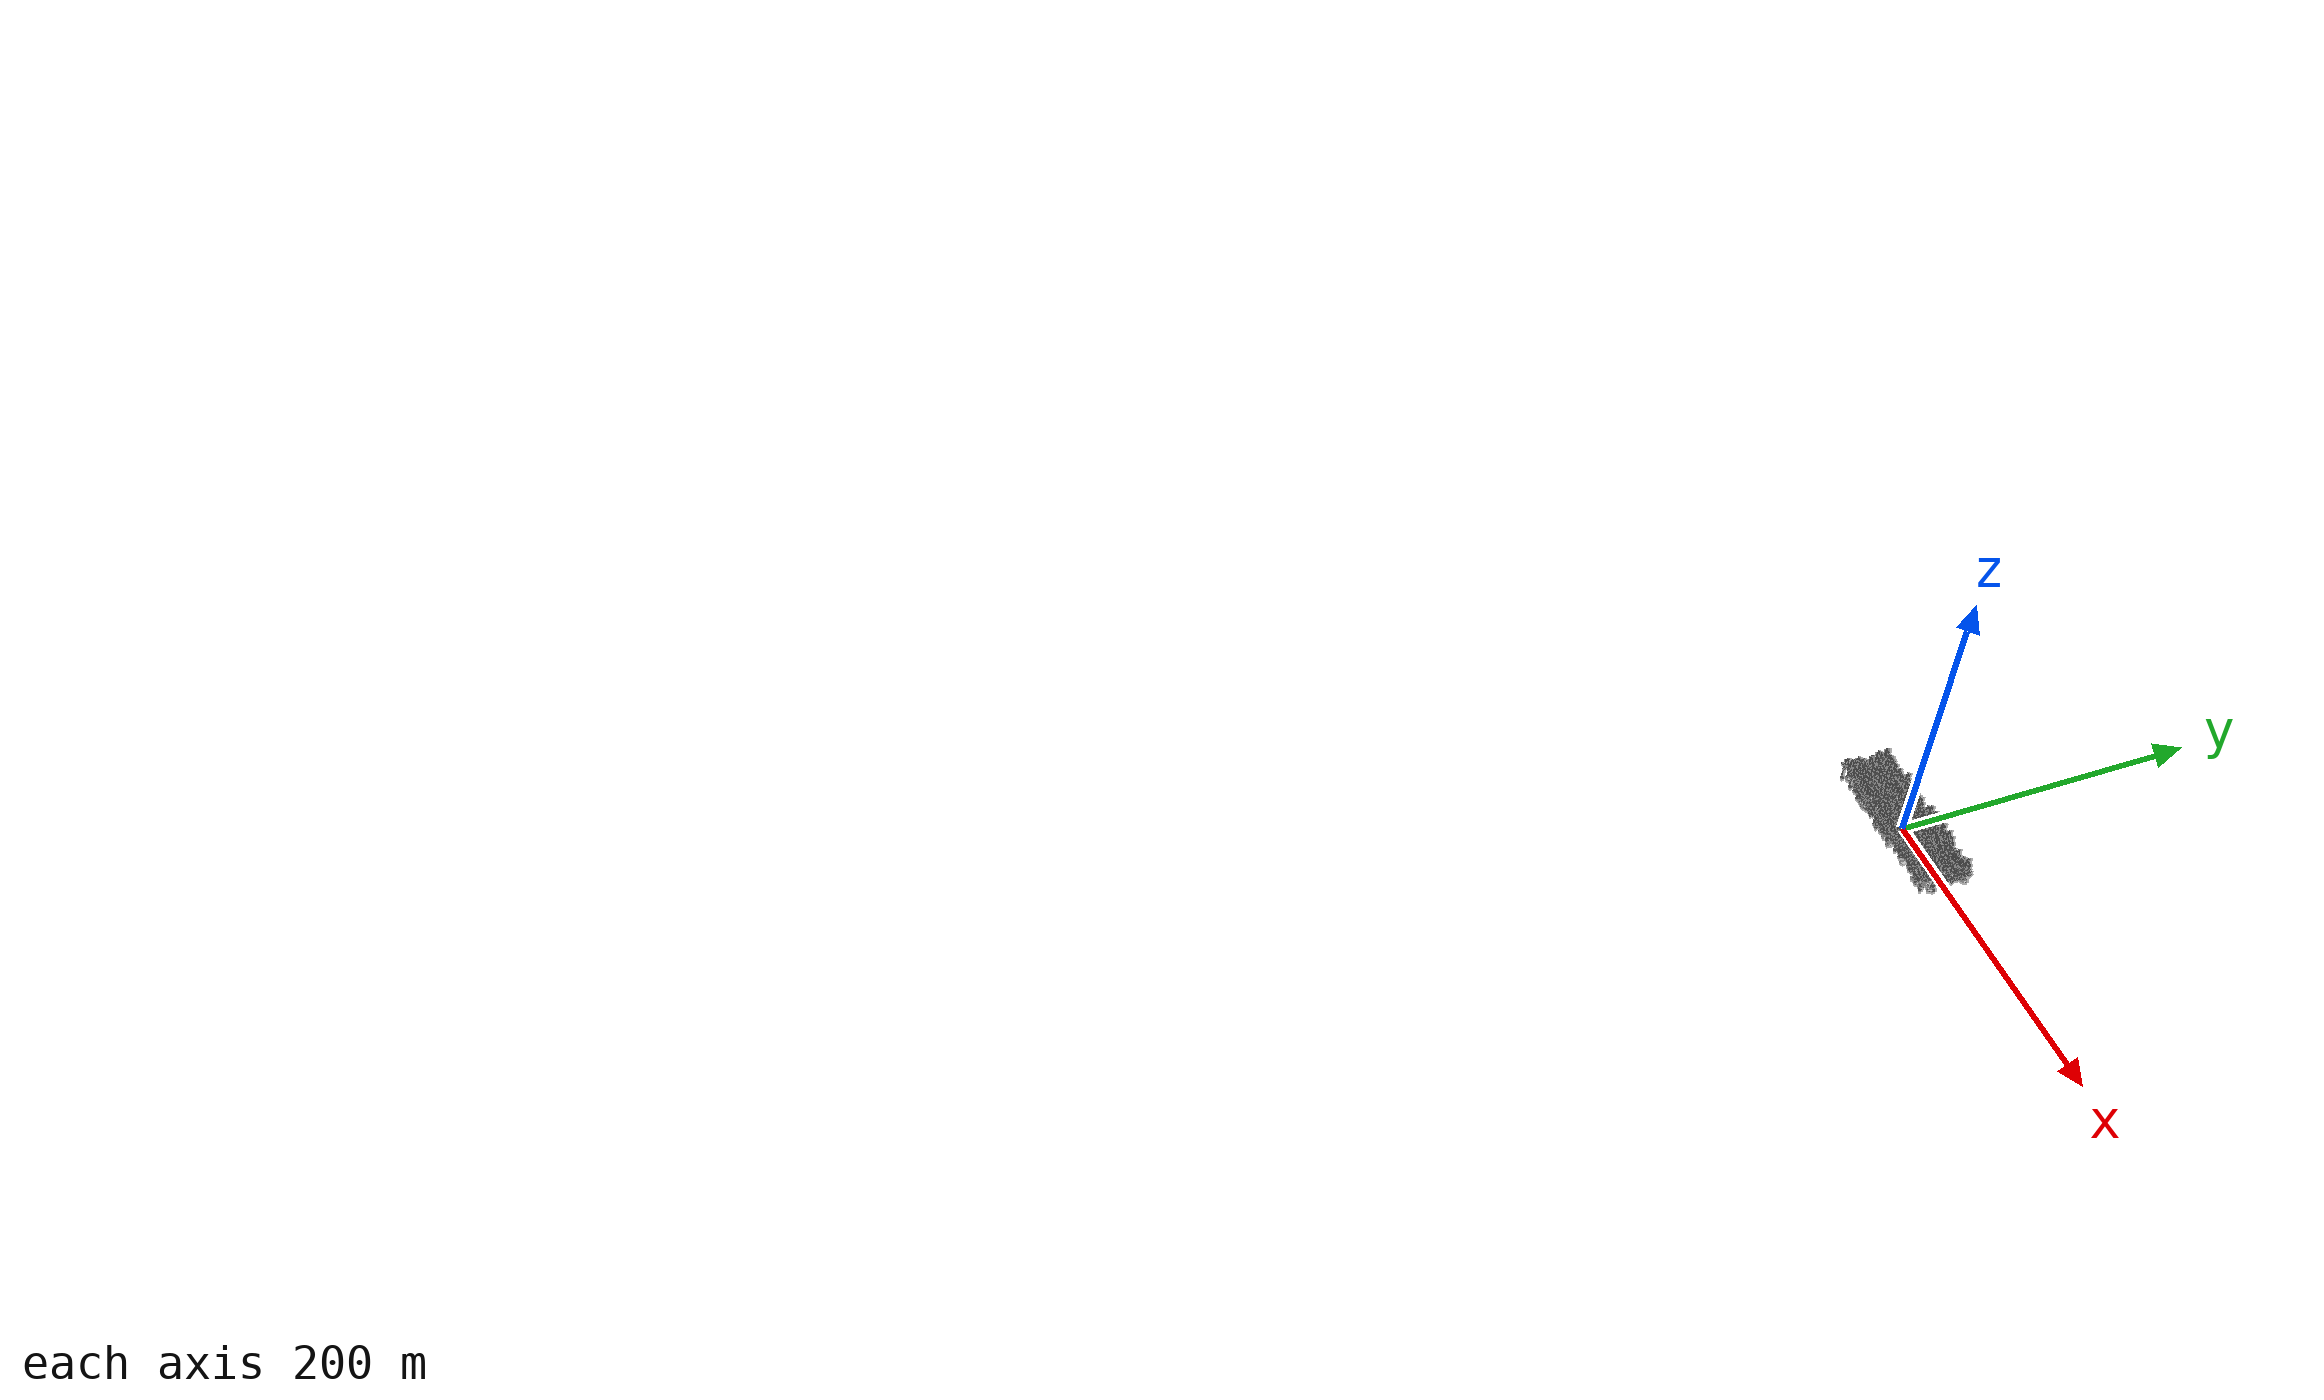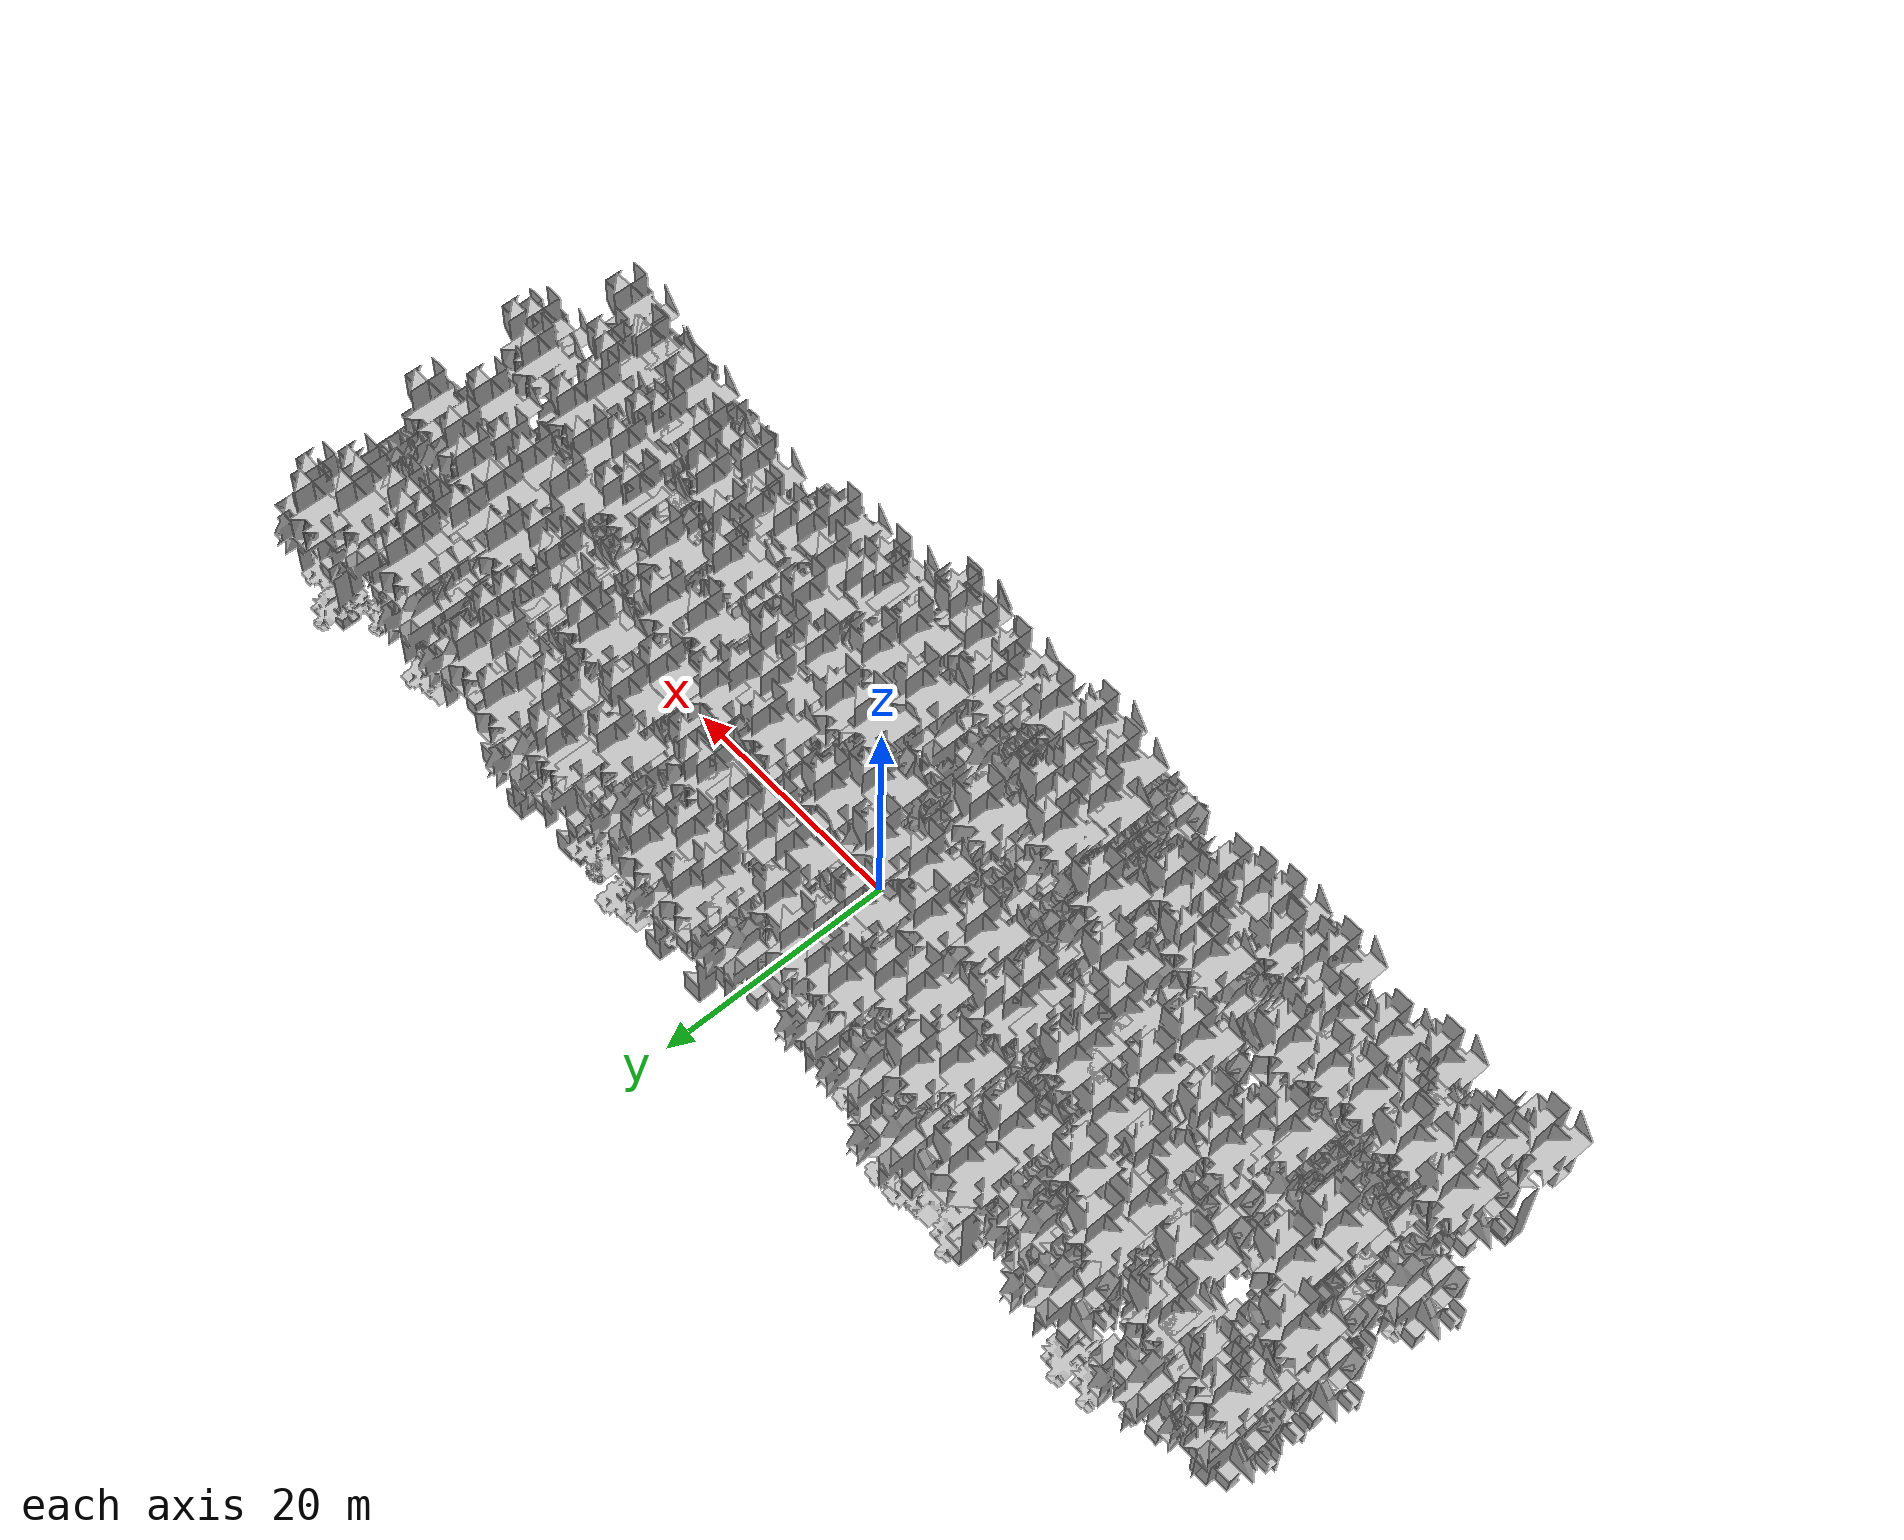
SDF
<sdf version="1.7">
    <world name="default">
        <plugin name="mrs_gazebo_static_transform_republisher_plugin" filename="libMrsGazeboCommonResources_StaticTransformRepublisher.so"/>
        <spherical_coordinates>
            <surface_model>EARTH_WGS84</surface_model>
            <latitude_deg>47.3977</latitude_deg>
            <longitude_deg>8.54559</longitude_deg>
            <elevation>0</elevation>
            <heading_deg>0</heading_deg>
        </spherical_coordinates>
        <physics name="default_physics" default="0" type="ode">
            <ode>
                <solver>
                    <type>quick</type>
                    <iters>10</iters>
                    <sor>1.3</sor>
                    <use_dynamic_moi_rescaling>0</use_dynamic_moi_rescaling>
                </solver>
                <constraints>
                    <cfm>0</cfm>
                    <erp>0.2</erp>
                    <contact_max_correcting_vel>1000</contact_max_correcting_vel>
                    <contact_surface_layer>0.001</contact_surface_layer>
                </constraints>
            </ode>
            <max_step_size>0.004</max_step_size>
            <real_time_factor>1</real_time_factor>
            <real_time_update_rate>250</real_time_update_rate>
        </physics>
        <scene>
            <shadows>0</shadows>
            <ambient>0.4 0.4 0.4 1</ambient>
            <background>0.7 0.7 0.7 1</background>
        </scene>
        <light name="sun" type="directional">
            <pose>0 0 1000 0.4 0.2 0</pose>
            <diffuse>1 1 1 1</diffuse>
            <specular>0.6 0.6 0.6 1</specular>
            <direction>0.1 0.1 -0.9</direction>
            <attenuation>
                <range>20</range>
                <constant>0.5</constant>
                <linear>0.01</linear>
                <quadratic>0.001</quadratic>
            </attenuation>
            <cast_shadows>1</cast_shadows>
            <spot>
                <inner_angle>0</inner_angle>
                <outer_angle>0</outer_angle>
                <falloff>0</falloff>
            </spot>
        </light>
        <model name="ground_plane">
            <static>1</static>
            <link name="link">
                <collision name="collision">
                    <pose>-50 0 0 0 -0 0</pose>
                    <geometry>
                        <plane>
                            <normal>0 0 1</normal>
                            <size>100 100</size>
                        </plane>
                    </geometry>
                    <surface>
                        <contact>
                            <ode>
                                <min_depth>0.01</min_depth>
                                <max_vel>0</max_vel>
                            </ode>
                        </contact>
                        <friction>
                            <ode/>
                            <torsional>
                                <ode/>
                            </torsional>
                        </friction>
                        <bounce/>
                    </surface>
                    <max_contacts>10</max_contacts>
                </collision>
                <visual name="grass">
                    <pose>0 0 0 0 -0 0</pose>
                    <cast_shadows>0</cast_shadows>
                    <geometry>
                        <mesh>
                            <scale>0.5814285714285714 0.18142857142857144 0.1</scale>
                            <uri>file://grass_plane/meshes/grass_plane.dae</uri>
                        </mesh>
                    </geometry>
                </visual>
                <self_collide>0</self_collide>
                <enable_wind>0</enable_wind>
                <kinematic>0</kinematic>
            </link>
        </model>
        <model name="the_void">
            <static>1</static>
            <link name="link">
                <pose>0 0 0.1 0 -0 0</pose>
                <visual name="the_void">
                    <pose>0 0 2 0 -0 0</pose>
                    <geometry>
                        <sphere>
                            <radius>0.25</radius>
                        </sphere>
                    </geometry>
                    <material>
                        <script>
                            <uri>file://media/materials/scripts/Gazebo.material</uri>
                            <name>Gazebo/Black</name>
                        </script>
                    </material>
                </visual>
                <self_collide>0</self_collide>
                <enable_wind>0</enable_wind>
                <kinematic>0</kinematic>
            </link>
            <pose>-1000 -1000 0 0 -0 0</pose>
        </model>
        <gui fullscreen="0">
            <camera name="camera">
                <pose>35.1577 98.6044 40.0204 0 0.407996 -1.99761</pose>
                <view_controller>orbit</view_controller>
                <projection_type>perspective</projection_type>
            </camera>
        </gui>
        <plugin name="mrs_gazebo_rviz_cam_synchronizer" filename="libMrsGazeboCommonResources_RvizCameraSynchronizer.so">
            <target_frame_id>gazebo_user_camera</target_frame_id>
            <world_origin_frame_id>uav1/gps_origin</world_origin_frame_id>
            <frame_to_follow>uav1</frame_to_follow>
        </plugin>
        <gravity>0 0 -9.8066</gravity>
        <magnetic_field>6e-06 2.3e-05 -4.2e-05</magnetic_field>
        <atmosphere type="adiabatic"/>
        <wind/>
        <model name="Tree 0">
            <static>1</static>
            <pose>-24.40015380244497 2.7771655417647025 0 1.57079 -0 0</pose>
            <link name="link">
                <pose>0 0 0 0 -0 0</pose>
                <collision name="collision">
                    <geometry>
                        <mesh>
                            <scale>3.5 5 3.5</scale>
                            <uri>model://tree_9/meshes/tree_9.obj</uri>
                        </mesh>
                    </geometry>
                    <max_contacts>10</max_contacts>
                    <surface>
                        <contact>
                            <ode/>
                        </contact>
                        <bounce/>
                        <friction>
                            <torsional>
                                <ode/>
                            </torsional>
                            <ode/>
                        </friction>
                    </surface>
                </collision>
                <visual name="visual">
                    <geometry>
                        <mesh>
                            <scale>3.5 5 3.5</scale>
                            <uri>model://tree_9/meshes/tree_9.obj</uri>
                        </mesh>
                    </geometry>
                </visual>
                <self_collide>0</self_collide>
                <enable_wind>0</enable_wind>
                <kinematic>0</kinematic>
            </link>
        </model>
        <model name="Tree 1">
            <static>1</static>
            <pose>32.246113342987115 0.1706914033773561 0 1.57079 -0 0</pose>
            <link name="link">
                <pose>0 0 0 0 -0 0</pose>
                <collision name="collision">
                    <geometry>
                        <mesh>
                            <scale>4 2.5 4</scale>
                            <uri>model://tree_1/meshes/tree_1.obj</uri>
                        </mesh>
                    </geometry>
                    <max_contacts>10</max_contacts>
                    <surface>
                        <contact>
                            <ode/>
                        </contact>
                        <bounce/>
                        <friction>
                            <torsional>
                                <ode/>
                            </torsional>
                            <ode/>
                        </friction>
                    </surface>
                </collision>
                <visual name="visual">
                    <geometry>
                        <mesh>
                            <scale>4 2.5 4</scale>
                            <uri>model://tree_1/meshes/tree_1.obj</uri>
                        </mesh>
                    </geometry>
                </visual>
                <self_collide>0</self_collide>
                <enable_wind>0</enable_wind>
                <kinematic>0</kinematic>
            </link>
        </model>
        <model name="Tree 2">
            <static>1</static>
            <pose>4.6822532477561225 -2.6083627503364912 0 1.57079 -0 0</pose>
            <link name="link">
                <pose>0 0 0 0 -0 0</pose>
                <collision name="collision">
                    <geometry>
                        <mesh>
                            <scale>3.5 5 3.5</scale>
                            <uri>model://tree_2/meshes/tree_2.obj</uri>
                        </mesh>
                    </geometry>
                    <max_contacts>10</max_contacts>
                    <surface>
                        <contact>
                            <ode/>
                        </contact>
                        <bounce/>
                        <friction>
                            <torsional>
                                <ode/>
                            </torsional>
                            <ode/>
                        </friction>
                    </surface>
                </collision>
                <visual name="visual">
                    <geometry>
                        <mesh>
                            <scale>3.5 5 3.5</scale>
                            <uri>model://tree_2/meshes/tree_2.obj</uri>
                        </mesh>
                    </geometry>
                </visual>
                <self_collide>0</self_collide>
                <enable_wind>0</enable_wind>
                <kinematic>0</kinematic>
            </link>
        </model>
        <model name="Tree 3">
            <static>1</static>
            <pose>37.284012888872894 12.578448107484277 0 1.57079 -0 0</pose>
            <link name="link">
                <pose>0 0 0 0 -0 0</pose>
                <collision name="collision">
                    <geometry>
                        <mesh>
                            <scale>3.5 5 3.5</scale>
                            <uri>model://tree_9/meshes/tree_9.obj</uri>
                        </mesh>
                    </geometry>
                    <max_contacts>10</max_contacts>
                    <surface>
                        <contact>
                            <ode/>
                        </contact>
                        <bounce/>
                        <friction>
                            <torsional>
                                <ode/>
                            </torsional>
                            <ode/>
                        </friction>
                    </surface>
                </collision>
                <visual name="visual">
                    <geometry>
                        <mesh>
                            <scale>3.5 5 3.5</scale>
                            <uri>model://tree_9/meshes/tree_9.obj</uri>
                        </mesh>
                    </geometry>
                </visual>
                <self_collide>0</self_collide>
                <enable_wind>0</enable_wind>
                <kinematic>0</kinematic>
            </link>
        </model>
        <model name="Tree 4">
            <static>1</static>
            <pose>-48.241566818626076 6.382101117961685 0 1.57079 -0 0</pose>
            <link name="link">
                <pose>0 0 0 0 -0 0</pose>
                <collision name="collision">
                    <geometry>
                        <mesh>
                            <scale>3.5 5 3.5</scale>
                            <uri>model://tree_2/meshes/tree_2.obj</uri>
                        </mesh>
                    </geometry>
                    <max_contacts>10</max_contacts>
                    <surface>
                        <contact>
                            <ode/>
                        </contact>
                        <bounce/>
                        <friction>
                            <torsional>
                                <ode/>
                            </torsional>
                            <ode/>
                        </friction>
                    </surface>
                </collision>
                <visual name="visual">
                    <geometry>
                        <mesh>
                            <scale>3.5 5 3.5</scale>
                            <uri>model://tree_2/meshes/tree_2.obj</uri>
                        </mesh>
                    </geometry>
                </visual>
                <self_collide>0</self_collide>
                <enable_wind>0</enable_wind>
                <kinematic>0</kinematic>
            </link>
        </model>
        <model name="Tree 5">
            <static>1</static>
            <pose>10.741834737825783 7.438542057268506 0 1.57079 -0 0</pose>
            <link name="link">
                <pose>0 0 0 0 -0 0</pose>
                <collision name="collision">
                    <geometry>
                        <mesh>
                            <scale>3.5 5 3.5</scale>
                            <uri>model://tree_9/meshes/tree_9.obj</uri>
                        </mesh>
                    </geometry>
                    <max_contacts>10</max_contacts>
                    <surface>
                        <contact>
                            <ode/>
                        </contact>
                        <bounce/>
                        <friction>
                            <torsional>
                                <ode/>
                            </torsional>
                            <ode/>
                        </friction>
                    </surface>
                </collision>
                <visual name="visual">
                    <geometry>
                        <mesh>
                            <scale>3.5 5 3.5</scale>
                            <uri>model://tree_9/meshes/tree_9.obj</uri>
                        </mesh>
                    </geometry>
                </visual>
                <self_collide>0</self_collide>
                <enable_wind>0</enable_wind>
                <kinematic>0</kinematic>
            </link>
        </model>
        <model name="Tree 6">
            <static>1</static>
            <pose>-46.17687277127987 -12.077543465122258 0 1.57079 -0 0</pose>
            <link name="link">
                <pose>0 0 0 0 -0 0</pose>
                <collision name="collision">
                    <geometry>
                        <mesh>
                            <scale>3.5 5 3.5</scale>
                            <uri>model://tree_9/meshes/tree_9.obj</uri>
                        </mesh>
                    </geometry>
                    <max_contacts>10</max_contacts>
                    <surface>
                        <contact>
                            <ode/>
                        </contact>
                        <bounce/>
                        <friction>
                            <torsional>
                                <ode/>
                            </torsional>
                            <ode/>
                        </friction>
                    </surface>
                </collision>
                <visual name="visual">
                    <geometry>
                        <mesh>
                            <scale>3.5 5 3.5</scale>
                            <uri>model://tree_9/meshes/tree_9.obj</uri>
                        </mesh>
                    </geometry>
                </visual>
                <self_collide>0</self_collide>
                <enable_wind>0</enable_wind>
                <kinematic>0</kinematic>
            </link>
        </model>
        <model name="Tree 7">
            <static>1</static>
            <pose>-3.4012049708011887 -10.99969805420975 0 1.57079 -0 0</pose>
            <link name="link">
                <pose>0 0 0 0 -0 0</pose>
                <collision name="collision">
                    <geometry>
                        <mesh>
                            <scale>3.5 5 3.5</scale>
                            <uri>model://tree_2/meshes/tree_2.obj</uri>
                        </mesh>
                    </geometry>
                    <max_contacts>10</max_contacts>
                    <surface>
                        <contact>
                            <ode/>
                        </contact>
                        <bounce/>
                        <friction>
                            <torsional>
                                <ode/>
                            </torsional>
                            <ode/>
                        </friction>
                    </surface>
                </collision>
                <visual name="visual">
                    <geometry>
                        <mesh>
                            <scale>3.5 5 3.5</scale>
                            <uri>model://tree_2/meshes/tree_2.obj</uri>
                        </mesh>
                    </geometry>
                </visual>
                <self_collide>0</self_collide>
                <enable_wind>0</enable_wind>
                <kinematic>0</kinematic>
            </link>
        </model>
        <model name="Tree 8">
            <static>1</static>
            <pose>-6.315009478187562 7.177040048046528 0 1.57079 -0 0</pose>
            <link name="link">
                <pose>0 0 0 0 -0 0</pose>
                <collision name="collision">
                    <geometry>
                        <mesh>
                            <scale>3.5 5 3.5</scale>
                            <uri>model://tree_9/meshes/tree_9.obj</uri>
                        </mesh>
                    </geometry>
                    <max_contacts>10</max_contacts>
                    <surface>
                        <contact>
                            <ode/>
                        </contact>
                        <bounce/>
                        <friction>
                            <torsional>
                                <ode/>
                            </torsional>
                            <ode/>
                        </friction>
                    </surface>
                </collision>
                <visual name="visual">
                    <geometry>
                        <mesh>
                            <scale>3.5 5 3.5</scale>
                            <uri>model://tree_9/meshes/tree_9.obj</uri>
                        </mesh>
                    </geometry>
                </visual>
                <self_collide>0</self_collide>
                <enable_wind>0</enable_wind>
                <kinematic>0</kinematic>
            </link>
        </model>
        <model name="Tree 9">
            <static>1</static>
            <pose>-9.78000082832689 -8.855958627671 0 1.57079 -0 0</pose>
            <link name="link">
                <pose>0 0 0 0 -0 0</pose>
                <collision name="collision">
                    <geometry>
                        <mesh>
                            <scale>3.5 5 3.5</scale>
                            <uri>model://tree_9/meshes/tree_9.obj</uri>
                        </mesh>
                    </geometry>
                    <max_contacts>10</max_contacts>
                    <surface>
                        <contact>
                            <ode/>
                        </contact>
                        <bounce/>
                        <friction>
                            <torsional>
                                <ode/>
                            </torsional>
                            <ode/>
                        </friction>
                    </surface>
                </collision>
                <visual name="visual">
                    <geometry>
                        <mesh>
                            <scale>3.5 5 3.5</scale>
                            <uri>model://tree_9/meshes/tree_9.obj</uri>
                        </mesh>
                    </geometry>
                </visual>
                <self_collide>0</self_collide>
                <enable_wind>0</enable_wind>
                <kinematic>0</kinematic>
            </link>
        </model>
        <model name="Tree 10">
            <static>1</static>
            <pose>-19.246089039979065 6.908874338125006 0 1.57079 -0 0</pose>
            <link name="link">
                <pose>0 0 0 0 -0 0</pose>
                <collision name="collision">
                    <geometry>
                        <mesh>
                            <scale>3.5 5 3.5</scale>
                            <uri>model://tree_2/meshes/tree_2.obj</uri>
                        </mesh>
                    </geometry>
                    <max_contacts>10</max_contacts>
                    <surface>
                        <contact>
                            <ode/>
                        </contact>
                        <bounce/>
                        <friction>
                            <torsional>
                                <ode/>
                            </torsional>
                            <ode/>
                        </friction>
                    </surface>
                </collision>
                <visual name="visual">
                    <geometry>
                        <mesh>
                            <scale>3.5 5 3.5</scale>
                            <uri>model://tree_2/meshes/tree_2.obj</uri>
                        </mesh>
                    </geometry>
                </visual>
                <self_collide>0</self_collide>
                <enable_wind>0</enable_wind>
                <kinematic>0</kinematic>
            </link>
        </model>
        <model name="Tree 11">
            <static>1</static>
            <pose>-29.711299888890707 11.643784595468148 0 1.57079 -0 0</pose>
            <link name="link">
                <pose>0 0 0 0 -0 0</pose>
                <collision name="collision">
                    <geometry>
                        <mesh>
                            <scale>3 2 3</scale>
                            <uri>model://tree_3/meshes/tree_3.obj</uri>
                        </mesh>
                    </geometry>
                    <max_contacts>10</max_contacts>
                    <surface>
                        <contact>
                            <ode/>
                        </contact>
                        <bounce/>
                        <friction>
                            <torsional>
                                <ode/>
                            </torsional>
                            <ode/>
                        </friction>
                    </surface>
                </collision>
                <visual name="visual">
                    <geometry>
                        <mesh>
                            <scale>3 2 3</scale>
                            <uri>model://tree_3/meshes/tree_3.obj</uri>
                        </mesh>
                    </geometry>
                </visual>
                <self_collide>0</self_collide>
                <enable_wind>0</enable_wind>
                <kinematic>0</kinematic>
            </link>
        </model>
        <model name="Tree 12">
            <static>1</static>
            <pose>-18.077300655426992 5.200777059565873 0 1.57079 -0 0</pose>
            <link name="link">
                <pose>0 0 0 0 -0 0</pose>
                <collision name="collision">
                    <geometry>
                        <mesh>
                            <scale>3.5 5 3.5</scale>
                            <uri>model://tree_9/meshes/tree_9.obj</uri>
                        </mesh>
                    </geometry>
                    <max_contacts>10</max_contacts>
                    <surface>
                        <contact>
                            <ode/>
                        </contact>
                        <bounce/>
                        <friction>
                            <torsional>
                                <ode/>
                            </torsional>
                            <ode/>
                        </friction>
                    </surface>
                </collision>
                <visual name="visual">
                    <geometry>
                        <mesh>
                            <scale>3.5 5 3.5</scale>
                            <uri>model://tree_9/meshes/tree_9.obj</uri>
                        </mesh>
                    </geometry>
                </visual>
                <self_collide>0</self_collide>
                <enable_wind>0</enable_wind>
                <kinematic>0</kinematic>
            </link>
        </model>
        <model name="Tree 13">
            <static>1</static>
            <pose>-6.0418201436939825 9.819887981123959 0 1.57079 -0 0</pose>
            <link name="link">
                <pose>0 0 0 0 -0 0</pose>
                <collision name="collision">
                    <geometry>
                        <mesh>
                            <scale>4 2.5 4</scale>
                            <uri>model://tree_1/meshes/tree_1.obj</uri>
                        </mesh>
                    </geometry>
                    <max_contacts>10</max_contacts>
                    <surface>
                        <contact>
                            <ode/>
                        </contact>
                        <bounce/>
                        <friction>
                            <torsional>
                                <ode/>
                            </torsional>
                            <ode/>
                        </friction>
                    </surface>
                </collision>
                <visual name="visual">
                    <geometry>
                        <mesh>
                            <scale>4 2.5 4</scale>
                            <uri>model://tree_1/meshes/tree_1.obj</uri>
                        </mesh>
                    </geometry>
                </visual>
                <self_collide>0</self_collide>
                <enable_wind>0</enable_wind>
                <kinematic>0</kinematic>
            </link>
        </model>
        <model name="Tree 14">
            <static>1</static>
            <pose>12.297697152173143 11.659283858585564 0 1.57079 -0 0</pose>
            <link name="link">
                <pose>0 0 0 0 -0 0</pose>
                <collision name="collision">
                    <geometry>
                        <mesh>
                            <scale>3 2 3</scale>
                            <uri>model://tree_3/meshes/tree_3.obj</uri>
                        </mesh>
                    </geometry>
                    <max_contacts>10</max_contacts>
                    <surface>
                        <contact>
                            <ode/>
                        </contact>
                        <bounce/>
                        <friction>
                            <torsional>
                                <ode/>
                            </torsional>
                            <ode/>
                        </friction>
                    </surface>
                </collision>
                <visual name="visual">
                    <geometry>
                        <mesh>
                            <scale>3 2 3</scale>
                            <uri>model://tree_3/meshes/tree_3.obj</uri>
                        </mesh>
                    </geometry>
                </visual>
                <self_collide>0</self_collide>
                <enable_wind>0</enable_wind>
                <kinematic>0</kinematic>
            </link>
        </model>
        <model name="Tree 15">
            <static>1</static>
            <pose>43.91958124333067 -2.473569055183649 0 1.57079 -0 0</pose>
            <link name="link">
                <pose>0 0 0 0 -0 0</pose>
                <collision name="collision">
                    <geometry>
                        <mesh>
                            <scale>3 2 3</scale>
                            <uri>model://tree_3/meshes/tree_3.obj</uri>
                        </mesh>
                    </geometry>
                    <max_contacts>10</max_contacts>
                    <surface>
                        <contact>
                            <ode/>
                        </contact>
                        <bounce/>
                        <friction>
                            <torsional>
                                <ode/>
                            </torsional>
                            <ode/>
                        </friction>
                    </surface>
                </collision>
                <visual name="visual">
                    <geometry>
                        <mesh>
                            <scale>3 2 3</scale>
                            <uri>model://tree_3/meshes/tree_3.obj</uri>
                        </mesh>
                    </geometry>
                </visual>
                <self_collide>0</self_collide>
                <enable_wind>0</enable_wind>
                <kinematic>0</kinematic>
            </link>
        </model>
        <model name="Tree 16">
            <static>1</static>
            <pose>-46.18537487104075 -11.622143205894108 0 1.57079 -0 0</pose>
            <link name="link">
                <pose>0 0 0 0 -0 0</pose>
                <collision name="collision">
                    <geometry>
                        <mesh>
                            <scale>4 2.5 4</scale>
                            <uri>model://tree_1/meshes/tree_1.obj</uri>
                        </mesh>
                    </geometry>
                    <max_contacts>10</max_contacts>
                    <surface>
                        <contact>
                            <ode/>
                        </contact>
                        <bounce/>
                        <friction>
                            <torsional>
                                <ode/>
                            </torsional>
                            <ode/>
                        </friction>
                    </surface>
                </collision>
                <visual name="visual">
                    <geometry>
                        <mesh>
                            <scale>4 2.5 4</scale>
                            <uri>model://tree_1/meshes/tree_1.obj</uri>
                        </mesh>
                    </geometry>
                </visual>
                <self_collide>0</self_collide>
                <enable_wind>0</enable_wind>
                <kinematic>0</kinematic>
            </link>
        </model>
        <model name="Tree 17">
            <static>1</static>
            <pose>-9.561964382676493 12.8208271931912 0 1.57079 -0 0</pose>
            <link name="link">
                <pose>0 0 0 0 -0 0</pose>
                <collision name="collision">
                    <geometry>
                        <mesh>
                            <scale>3.5 5 3.5</scale>
                            <uri>model://tree_2/meshes/tree_2.obj</uri>
                        </mesh>
                    </geometry>
                    <max_contacts>10</max_contacts>
                    <surface>
                        <contact>
                            <ode/>
                        </contact>
                        <bounce/>
                        <friction>
                            <torsional>
                                <ode/>
                            </torsional>
                            <ode/>
                        </friction>
                    </surface>
                </collision>
                <visual name="visual">
                    <geometry>
                        <mesh>
                            <scale>3.5 5 3.5</scale>
                            <uri>model://tree_2/meshes/tree_2.obj</uri>
                        </mesh>
                    </geometry>
                </visual>
                <self_collide>0</self_collide>
                <enable_wind>0</enable_wind>
                <kinematic>0</kinematic>
            </link>
        </model>
        <model name="Tree 18">
            <static>1</static>
            <pose>47.60759213112419 -10.418521644232777 0 1.57079 -0 0</pose>
            <link name="link">
                <pose>0 0 0 0 -0 0</pose>
                <collision name="collision">
                    <geometry>
                        <mesh>
                            <scale>3 2 3</scale>
                            <uri>model://tree_3/meshes/tree_3.obj</uri>
                        </mesh>
                    </geometry>
                    <max_contacts>10</max_contacts>
                    <surface>
                        <contact>
                            <ode/>
                        </contact>
                        <bounce/>
                        <friction>
                            <torsional>
                                <ode/>
                            </torsional>
                            <ode/>
                        </friction>
                    </surface>
                </collision>
                <visual name="visual">
                    <geometry>
                        <mesh>
                            <scale>3 2 3</scale>
                            <uri>model://tree_3/meshes/tree_3.obj</uri>
                        </mesh>
                    </geometry>
                </visual>
                <self_collide>0</self_collide>
                <enable_wind>0</enable_wind>
                <kinematic>0</kinematic>
            </link>
        </model>
        <model name="Tree 19">
            <static>1</static>
            <pose>41.006656613931085 4.813287169033867 0 1.57079 -0 0</pose>
            <link name="link">
                <pose>0 0 0 0 -0 0</pose>
                <collision name="collision">
                    <geometry>
                        <mesh>
                            <scale>3.5 5 3.5</scale>
                            <uri>model://tree_2/meshes/tree_2.obj</uri>
                        </mesh>
                    </geometry>
                    <max_contacts>10</max_contacts>
                    <surface>
                        <contact>
                            <ode/>
                        </contact>
                        <bounce/>
                        <friction>
                            <torsional>
                                <ode/>
                            </torsional>
                            <ode/>
                        </friction>
                    </surface>
                </collision>
                <visual name="visual">
                    <geometry>
                        <mesh>
                            <scale>3.5 5 3.5</scale>
                            <uri>model://tree_2/meshes/tree_2.obj</uri>
                        </mesh>
                    </geometry>
                </visual>
                <self_collide>0</self_collide>
                <enable_wind>0</enable_wind>
                <kinematic>0</kinematic>
            </link>
        </model>
        <model name="Tree 20">
            <static>1</static>
            <pose>-10.122272205326908 4.299424618157886 0 1.57079 -0 0</pose>
            <link name="link">
                <pose>0 0 0 0 -0 0</pose>
                <collision name="collision">
                    <geometry>
                        <mesh>
                            <scale>4 2.5 4</scale>
                            <uri>model://tree_1/meshes/tree_1.obj</uri>
                        </mesh>
                    </geometry>
                    <max_contacts>10</max_contacts>
                    <surface>
                        <contact>
                            <ode/>
                        </contact>
                        <bounce/>
                        <friction>
                            <torsional>
                                <ode/>
                            </torsional>
                            <ode/>
                        </friction>
                    </surface>
                </collision>
                <visual name="visual">
                    <geometry>
                        <mesh>
                            <scale>4 2.5 4</scale>
                            <uri>model://tree_1/meshes/tree_1.obj</uri>
                        </mesh>
                    </geometry>
                </visual>
                <self_collide>0</self_collide>
                <enable_wind>0</enable_wind>
                <kinematic>0</kinematic>
            </link>
        </model>
        <model name="Tree 21">
            <static>1</static>
            <pose>-4.50756942797765 10.08531511082169 0 1.57079 -0 0</pose>
            <link name="link">
                <pose>0 0 0 0 -0 0</pose>
                <collision name="collision">
                    <geometry>
                        <mesh>
                            <scale>4 2.5 4</scale>
                            <uri>model://tree_1/meshes/tree_1.obj</uri>
                        </mesh>
                    </geometry>
                    <max_contacts>10</max_contacts>
                    <surface>
                        <contact>
                            <ode/>
                        </contact>
                        <bounce/>
                        <friction>
                            <torsional>
                                <ode/>
                            </torsional>
                            <ode/>
                        </friction>
                    </surface>
                </collision>
                <visual name="visual">
                    <geometry>
                        <mesh>
                            <scale>4 2.5 4</scale>
                            <uri>model://tree_1/meshes/tree_1.obj</uri>
                        </mesh>
                    </geometry>
                </visual>
                <self_collide>0</self_collide>
                <enable_wind>0</enable_wind>
                <kinematic>0</kinematic>
            </link>
        </model>
        <model name="Tree 22">
            <static>1</static>
            <pose>8.560986949753492 -7.444285719568318 0 1.57079 -0 0</pose>
            <link name="link">
                <pose>0 0 0 0 -0 0</pose>
                <collision name="collision">
                    <geometry>
                        <mesh>
                            <scale>3.5 5 3.5</scale>
                            <uri>model://tree_9/meshes/tree_9.obj</uri>
                        </mesh>
                    </geometry>
                    <max_contacts>10</max_contacts>
                    <surface>
                        <contact>
                            <ode/>
                        </contact>
                        <bounce/>
                        <friction>
                            <torsional>
                                <ode/>
                            </torsional>
                            <ode/>
                        </friction>
                    </surface>
                </collision>
                <visual name="visual">
                    <geometry>
                        <mesh>
                            <scale>3.5 5 3.5</scale>
                            <uri>model://tree_9/meshes/tree_9.obj</uri>
                        </mesh>
                    </geometry>
                </visual>
                <self_collide>0</self_collide>
                <enable_wind>0</enable_wind>
                <kinematic>0</kinematic>
            </link>
        </model>
        <model name="Tree 23">
            <static>1</static>
            <pose>-41.37176256263588 -4.454853935062301 0 1.57079 -0 0</pose>
            <link name="link">
                <pose>0 0 0 0 -0 0</pose>
                <collision name="collision">
                    <geometry>
                        <mesh>
                            <scale>3.5 5 3.5</scale>
                            <uri>model://tree_2/meshes/tree_2.obj</uri>
                        </mesh>
                    </geometry>
                    <max_contacts>10</max_contacts>
                    <surface>
                        <contact>
                            <ode/>
                        </contact>
                        <bounce/>
                        <friction>
                            <torsional>
                                <ode/>
                            </torsional>
                            <ode/>
                        </friction>
                    </surface>
                </collision>
                <visual name="visual">
                    <geometry>
                        <mesh>
                            <scale>3.5 5 3.5</scale>
                            <uri>model://tree_2/meshes/tree_2.obj</uri>
                        </mesh>
                    </geometry>
                </visual>
                <self_collide>0</self_collide>
                <enable_wind>0</enable_wind>
                <kinematic>0</kinematic>
            </link>
        </model>
        <model name="Tree 24">
            <static>1</static>
            <pose>19.27694145751201 8.679136142417018 0 1.57079 -0 0</pose>
            <link name="link">
                <pose>0 0 0 0 -0 0</pose>
                <collision name="collision">
                    <geometry>
                        <mesh>
                            <scale>4 2.5 4</scale>
                            <uri>model://tree_1/meshes/tree_1.obj</uri>
                        </mesh>
                    </geometry>
                    <max_contacts>10</max_contacts>
                    <surface>
                        <contact>
                            <ode/>
                        </contact>
                        <bounce/>
                        <friction>
                            <torsional>
                                <ode/>
                            </torsional>
                            <ode/>
                        </friction>
                    </surface>
                </collision>
                <visual name="visual">
                    <geometry>
                        <mesh>
                            <scale>4 2.5 4</scale>
                            <uri>model://tree_1/meshes/tree_1.obj</uri>
                        </mesh>
                    </geometry>
                </visual>
                <self_collide>0</self_collide>
                <enable_wind>0</enable_wind>
                <kinematic>0</kinematic>
            </link>
        </model>
        <model name="Tree 25">
            <static>1</static>
            <pose>-14.25757203044791 -9.172714690948657 0 1.57079 -0 0</pose>
            <link name="link">
                <pose>0 0 0 0 -0 0</pose>
                <collision name="collision">
                    <geometry>
                        <mesh>
                            <scale>3.5 5 3.5</scale>
                            <uri>model://tree_2/meshes/tree_2.obj</uri>
                        </mesh>
                    </geometry>
                    <max_contacts>10</max_contacts>
                    <surface>
                        <contact>
                            <ode/>
                        </contact>
                        <bounce/>
                        <friction>
                            <torsional>
                                <ode/>
                            </torsional>
                            <ode/>
                        </friction>
                    </surface>
                </collision>
                <visual name="visual">
                    <geometry>
                        <mesh>
                            <scale>3.5 5 3.5</scale>
                            <uri>model://tree_2/meshes/tree_2.obj</uri>
                        </mesh>
                    </geometry>
                </visual>
                <self_collide>0</self_collide>
                <enable_wind>0</enable_wind>
                <kinematic>0</kinematic>
            </link>
        </model>
        <model name="Tree 26">
            <static>1</static>
            <pose>37.36971718288308 11.007175692957809 0 1.57079 -0 0</pose>
            <link name="link">
                <pose>0 0 0 0 -0 0</pose>
                <collision name="collision">
                    <geometry>
                        <mesh>
                            <scale>3.5 5 3.5</scale>
                            <uri>model://tree_9/meshes/tree_9.obj</uri>
                        </mesh>
                    </geometry>
                    <max_contacts>10</max_contacts>
                    <surface>
                        <contact>
                            <ode/>
                        </contact>
                        <bounce/>
                        <friction>
                            <torsional>
                                <ode/>
                            </torsional>
                            <ode/>
                        </friction>
                    </surface>
                </collision>
                <visual name="visual">
                    <geometry>
                        <mesh>
                            <scale>3.5 5 3.5</scale>
                            <uri>model://tree_9/meshes/tree_9.obj</uri>
                        </mesh>
                    </geometry>
                </visual>
                <self_collide>0</self_collide>
                <enable_wind>0</enable_wind>
                <kinematic>0</kinematic>
            </link>
        </model>
        <model name="Tree 27">
            <static>1</static>
            <pose>-46.30135250556976 3.190948742560927 0 1.57079 -0 0</pose>
            <link name="link">
                <pose>0 0 0 0 -0 0</pose>
                <collision name="collision">
                    <geometry>
                        <mesh>
                            <scale>3.5 5 3.5</scale>
                            <uri>model://tree_2/meshes/tree_2.obj</uri>
                        </mesh>
                    </geometry>
                    <max_contacts>10</max_contacts>
                    <surface>
                        <contact>
                            <ode/>
                        </contact>
                        <bounce/>
                        <friction>
                            <torsional>
                                <ode/>
                            </torsional>
                            <ode/>
                        </friction>
                    </surface>
                </collision>
                <visual name="visual">
                    <geometry>
                        <mesh>
                            <scale>3.5 5 3.5</scale>
                            <uri>model://tree_2/meshes/tree_2.obj</uri>
                        </mesh>
                    </geometry>
                </visual>
                <self_collide>0</self_collide>
                <enable_wind>0</enable_wind>
                <kinematic>0</kinematic>
            </link>
        </model>
        <model name="Tree 28">
            <static>1</static>
            <pose>38.61750530166188 -12.221965211046651 0 1.57079 -0 0</pose>
            <link name="link">
                <pose>0 0 0 0 -0 0</pose>
                <collision name="collision">
                    <geometry>
                        <mesh>
                            <scale>4 2.5 4</scale>
                            <uri>model://tree_1/meshes/tree_1.obj</uri>
                        </mesh>
                    </geometry>
                    <max_contacts>10</max_contacts>
                    <surface>
                        <contact>
                            <ode/>
                        </contact>
                        <bounce/>
                        <friction>
                            <torsional>
                                <ode/>
                            </torsional>
                            <ode/>
                        </friction>
                    </surface>
                </collision>
                <visual name="visual">
                    <geometry>
                        <mesh>
                            <scale>4 2.5 4</scale>
                            <uri>model://tree_1/meshes/tree_1.obj</uri>
                        </mesh>
                    </geometry>
                </visual>
                <self_collide>0</self_collide>
                <enable_wind>0</enable_wind>
                <kinematic>0</kinematic>
            </link>
        </model>
        <model name="Tree 29">
            <static>1</static>
            <pose>-22.807019266591308 6.473514083245718 0 1.57079 -0 0</pose>
            <link name="link">
                <pose>0 0 0 0 -0 0</pose>
                <collision name="collision">
                    <geometry>
                        <mesh>
                            <scale>3.5 5 3.5</scale>
                            <uri>model://tree_2/meshes/tree_2.obj</uri>
                        </mesh>
                    </geometry>
                    <max_contacts>10</max_contacts>
                    <surface>
                        <contact>
                            <ode/>
                        </contact>
                        <bounce/>
                        <friction>
                            <torsional>
                                <ode/>
                            </torsional>
                            <ode/>
                        </friction>
                    </surface>
                </collision>
                <visual name="visual">
                    <geometry>
                        <mesh>
                            <scale>3.5 5 3.5</scale>
                            <uri>model://tree_2/meshes/tree_2.obj</uri>
                        </mesh>
                    </geometry>
                </visual>
                <self_collide>0</self_collide>
                <enable_wind>0</enable_wind>
                <kinematic>0</kinematic>
            </link>
        </model>
        <model name="Tree 30">
            <static>1</static>
            <pose>-17.26765193191037 -11.461840166426708 0 1.57079 -0 0</pose>
            <link name="link">
                <pose>0 0 0 0 -0 0</pose>
                <collision name="collision">
                    <geometry>
                        <mesh>
                            <scale>3.5 5 3.5</scale>
                            <uri>model://tree_2/meshes/tree_2.obj</uri>
                        </mesh>
                    </geometry>
                    <max_contacts>10</max_contacts>
                    <surface>
                        <contact>
                            <ode/>
                        </contact>
                        <bounce/>
                        <friction>
                            <torsional>
                                <ode/>
                            </torsional>
                            <ode/>
                        </friction>
                    </surface>
                </collision>
                <visual name="visual">
                    <geometry>
                        <mesh>
                            <scale>3.5 5 3.5</scale>
                            <uri>model://tree_2/meshes/tree_2.obj</uri>
                        </mesh>
                    </geometry>
                </visual>
                <self_collide>0</self_collide>
                <enable_wind>0</enable_wind>
                <kinematic>0</kinematic>
            </link>
        </model>
        <model name="Tree 31">
            <static>1</static>
            <pose>-19.235276269843048 -10.087620515287782 0 1.57079 -0 0</pose>
            <link name="link">
                <pose>0 0 0 0 -0 0</pose>
                <collision name="collision">
                    <geometry>
                        <mesh>
                            <scale>3.5 5 3.5</scale>
                            <uri>model://tree_9/meshes/tree_9.obj</uri>
                        </mesh>
                    </geometry>
                    <max_contacts>10</max_contacts>
                    <surface>
                        <contact>
                            <ode/>
                        </contact>
                        <bounce/>
                        <friction>
                            <torsional>
                                <ode/>
                            </torsional>
                            <ode/>
                        </friction>
                    </surface>
                </collision>
                <visual name="visual">
                    <geometry>
                        <mesh>
                            <scale>3.5 5 3.5</scale>
                            <uri>model://tree_9/meshes/tree_9.obj</uri>
                        </mesh>
                    </geometry>
                </visual>
                <self_collide>0</self_collide>
                <enable_wind>0</enable_wind>
                <kinematic>0</kinematic>
            </link>
        </model>
        <model name="Tree 32">
            <static>1</static>
            <pose>3.6359509436147874 1.762278367412243 0 1.57079 -0 0</pose>
            <link name="link">
                <pose>0 0 0 0 -0 0</pose>
                <collision name="collision">
                    <geometry>
                        <mesh>
                            <scale>4 2.5 4</scale>
                            <uri>model://tree_1/meshes/tree_1.obj</uri>
                        </mesh>
                    </geometry>
                    <max_contacts>10</max_contacts>
                    <surface>
                        <contact>
                            <ode/>
                        </contact>
                        <bounce/>
                        <friction>
                            <torsional>
                                <ode/>
                            </torsional>
                            <ode/>
                        </friction>
                    </surface>
                </collision>
                <visual name="visual">
                    <geometry>
                        <mesh>
                            <scale>4 2.5 4</scale>
                            <uri>model://tree_1/meshes/tree_1.obj</uri>
                        </mesh>
                    </geometry>
                </visual>
                <self_collide>0</self_collide>
                <enable_wind>0</enable_wind>
                <kinematic>0</kinematic>
            </link>
        </model>
        <model name="Tree 33">
            <static>1</static>
            <pose>20.469371365420756 14.50723271962391 0 1.57079 -0 0</pose>
            <link name="link">
                <pose>0 0 0 0 -0 0</pose>
                <collision name="collision">
                    <geometry>
                        <mesh>
                            <scale>3.5 5 3.5</scale>
                            <uri>model://tree_2/meshes/tree_2.obj</uri>
                        </mesh>
                    </geometry>
                    <max_contacts>10</max_contacts>
                    <surface>
                        <contact>
                            <ode/>
                        </contact>
                        <bounce/>
                        <friction>
                            <torsional>
                                <ode/>
                            </torsional>
                            <ode/>
                        </friction>
                    </surface>
                </collision>
                <visual name="visual">
                    <geometry>
                        <mesh>
                            <scale>3.5 5 3.5</scale>
                            <uri>model://tree_2/meshes/tree_2.obj</uri>
                        </mesh>
                    </geometry>
                </visual>
                <self_collide>0</self_collide>
                <enable_wind>0</enable_wind>
                <kinematic>0</kinematic>
            </link>
        </model>
        <model name="Tree 34">
            <static>1</static>
            <pose>-27.007473826532312 6.812404441155536 0 1.57079 -0 0</pose>
            <link name="link">
                <pose>0 0 0 0 -0 0</pose>
                <collision name="collision">
                    <geometry>
                        <mesh>
                            <scale>3.5 5 3.5</scale>
                            <uri>model://tree_2/meshes/tree_2.obj</uri>
                        </mesh>
                    </geometry>
                    <max_contacts>10</max_contacts>
                    <surface>
                        <contact>
                            <ode/>
                        </contact>
                        <bounce/>
                        <friction>
                            <torsional>
                                <ode/>
                            </torsional>
                            <ode/>
                        </friction>
                    </surface>
                </collision>
                <visual name="visual">
                    <geometry>
                        <mesh>
                            <scale>3.5 5 3.5</scale>
                            <uri>model://tree_2/meshes/tree_2.obj</uri>
                        </mesh>
                    </geometry>
                </visual>
                <self_collide>0</self_collide>
                <enable_wind>0</enable_wind>
                <kinematic>0</kinematic>
            </link>
        </model>
        <model name="Tree 35">
            <static>1</static>
            <pose>17.55820511271034 13.923386057310417 0 1.57079 -0 0</pose>
            <link name="link">
                <pose>0 0 0 0 -0 0</pose>
                <collision name="collision">
                    <geometry>
                        <mesh>
                            <scale>3.5 5 3.5</scale>
                            <uri>model://tree_2/meshes/tree_2.obj</uri>
                        </mesh>
                    </geometry>
                    <max_contacts>10</max_contacts>
                    <surface>
                        <contact>
                            <ode/>
                        </contact>
                        <bounce/>
                        <friction>
                            <torsional>
                                <ode/>
                            </torsional>
                            <ode/>
                        </friction>
                    </surface>
                </collision>
                <visual name="visual">
                    <geometry>
                        <mesh>
                            <scale>3.5 5 3.5</scale>
                            <uri>model://tree_2/meshes/tree_2.obj</uri>
                        </mesh>
                    </geometry>
                </visual>
                <self_collide>0</self_collide>
                <enable_wind>0</enable_wind>
                <kinematic>0</kinematic>
            </link>
        </model>
        <model name="Tree 36">
            <static>1</static>
            <pose>-40.20980662681028 -13.55327013152386 0 1.57079 -0 0</pose>
            <link name="link">
                <pose>0 0 0 0 -0 0</pose>
                <collision name="collision">
                    <geometry>
                        <mesh>
                            <scale>3.5 5 3.5</scale>
                            <uri>model://tree_9/meshes/tree_9.obj</uri>
                        </mesh>
                    </geometry>
                    <max_contacts>10</max_contacts>
                    <surface>
                        <contact>
                            <ode/>
                        </contact>
                        <bounce/>
                        <friction>
                            <torsional>
                                <ode/>
                            </torsional>
                            <ode/>
                        </friction>
                    </surface>
                </collision>
                <visual name="visual">
                    <geometry>
                        <mesh>
                            <scale>3.5 5 3.5</scale>
                            <uri>model://tree_9/meshes/tree_9.obj</uri>
                        </mesh>
                    </geometry>
                </visual>
                <self_collide>0</self_collide>
                <enable_wind>0</enable_wind>
                <kinematic>0</kinematic>
            </link>
        </model>
        <model name="Tree 37">
            <static>1</static>
            <pose>-10.63687588219755 -6.996140885234148 0 1.57079 -0 0</pose>
            <link name="link">
                <pose>0 0 0 0 -0 0</pose>
                <collision name="collision">
                    <geometry>
                        <mesh>
                            <scale>3.5 5 3.5</scale>
                            <uri>model://tree_9/meshes/tree_9.obj</uri>
                        </mesh>
                    </geometry>
                    <max_contacts>10</max_contacts>
                    <surface>
                        <contact>
                            <ode/>
                        </contact>
                        <bounce/>
                        <friction>
                            <torsional>
                                <ode/>
                            </torsional>
                            <ode/>
                        </friction>
                    </surface>
                </collision>
                <visual name="visual">
                    <geometry>
                        <mesh>
                            <scale>3.5 5 3.5</scale>
                            <uri>model://tree_9/meshes/tree_9.obj</uri>
                        </mesh>
                    </geometry>
                </visual>
                <self_collide>0</self_collide>
                <enable_wind>0</enable_wind>
                <kinematic>0</kinematic>
            </link>
        </model>
        <model name="Tree 38">
            <static>1</static>
            <pose>-44.737884061568124 -5.737415419953194 0 1.57079 -0 0</pose>
            <link name="link">
                <pose>0 0 0 0 -0 0</pose>
                <collision name="collision">
                    <geometry>
                        <mesh>
                            <scale>3.5 5 3.5</scale>
                            <uri>model://tree_2/meshes/tree_2.obj</uri>
                        </mesh>
                    </geometry>
                    <max_contacts>10</max_contacts>
                    <surface>
                        <contact>
                            <ode/>
                        </contact>
                        <bounce/>
                        <friction>
                            <torsional>
                                <ode/>
                            </torsional>
                            <ode/>
                        </friction>
                    </surface>
                </collision>
                <visual name="visual">
                    <geometry>
                        <mesh>
                            <scale>3.5 5 3.5</scale>
                            <uri>model://tree_2/meshes/tree_2.obj</uri>
                        </mesh>
                    </geometry>
                </visual>
                <self_collide>0</self_collide>
                <enable_wind>0</enable_wind>
                <kinematic>0</kinematic>
            </link>
        </model>
        <model name="Tree 39">
            <static>1</static>
            <pose>-36.713377945901485 -4.955438176366888 0 1.57079 -0 0</pose>
            <link name="link">
                <pose>0 0 0 0 -0 0</pose>
                <collision name="collision">
                    <geometry>
                        <mesh>
                            <scale>3.5 5 3.5</scale>
                            <uri>model://tree_2/meshes/tree_2.obj</uri>
                        </mesh>
                    </geometry>
                    <max_contacts>10</max_contacts>
                    <surface>
                        <contact>
                            <ode/>
                        </contact>
                        <bounce/>
                        <friction>
                            <torsional>
                                <ode/>
                            </torsional>
                            <ode/>
                        </friction>
                    </surface>
                </collision>
                <visual name="visual">
                    <geometry>
                        <mesh>
                            <scale>3.5 5 3.5</scale>
                            <uri>model://tree_2/meshes/tree_2.obj</uri>
                        </mesh>
                    </geometry>
                </visual>
                <self_collide>0</self_collide>
                <enable_wind>0</enable_wind>
                <kinematic>0</kinematic>
            </link>
        </model>
        <model name="Tree 40">
            <static>1</static>
            <pose>11.061610932866913 -4.341356269984688 0 1.57079 -0 0</pose>
            <link name="link">
                <pose>0 0 0 0 -0 0</pose>
                <collision name="collision">
                    <geometry>
                        <mesh>
                            <scale>3.5 5 3.5</scale>
                            <uri>model://tree_9/meshes/tree_9.obj</uri>
                        </mesh>
                    </geometry>
                    <max_contacts>10</max_contacts>
                    <surface>
                        <contact>
                            <ode/>
                        </contact>
                        <bounce/>
                        <friction>
                            <torsional>
                                <ode/>
                            </torsional>
                            <ode/>
                        </friction>
                    </surface>
                </collision>
                <visual name="visual">
                    <geometry>
                        <mesh>
                            <scale>3.5 5 3.5</scale>
                            <uri>model://tree_9/meshes/tree_9.obj</uri>
                        </mesh>
                    </geometry>
                </visual>
                <self_collide>0</self_collide>
                <enable_wind>0</enable_wind>
                <kinematic>0</kinematic>
            </link>
        </model>
        <model name="Tree 41">
            <static>1</static>
            <pose>2.8465803868380988 -8.830586241369659 0 1.57079 -0 0</pose>
            <link name="link">
                <pose>0 0 0 0 -0 0</pose>
                <collision name="collision">
                    <geometry>
                        <mesh>
                            <scale>3.5 5 3.5</scale>
                            <uri>model://tree_2/meshes/tree_2.obj</uri>
                        </mesh>
                    </geometry>
                    <max_contacts>10</max_contacts>
                    <surface>
                        <contact>
                            <ode/>
                        </contact>
                        <bounce/>
                        <friction>
                            <torsional>
                                <ode/>
                            </torsional>
                            <ode/>
                        </friction>
                    </surface>
                </collision>
                <visual name="visual">
                    <geometry>
                        <mesh>
                            <scale>3.5 5 3.5</scale>
                            <uri>model://tree_2/meshes/tree_2.obj</uri>
                        </mesh>
                    </geometry>
                </visual>
                <self_collide>0</self_collide>
                <enable_wind>0</enable_wind>
                <kinematic>0</kinematic>
            </link>
        </model>
        <model name="Tree 42">
            <static>1</static>
            <pose>-2.4022848912385015 -13.264868014995365 0 1.57079 -0 0</pose>
            <link name="link">
                <pose>0 0 0 0 -0 0</pose>
                <collision name="collision">
                    <geometry>
                        <mesh>
                            <scale>4 2.5 4</scale>
                            <uri>model://tree_1/meshes/tree_1.obj</uri>
                        </mesh>
                    </geometry>
                    <max_contacts>10</max_contacts>
                    <surface>
                        <contact>
                            <ode/>
                        </contact>
                        <bounce/>
                        <friction>
                            <torsional>
                                <ode/>
                            </torsional>
                            <ode/>
                        </friction>
                    </surface>
                </collision>
                <visual name="visual">
                    <geometry>
                        <mesh>
                            <scale>4 2.5 4</scale>
                            <uri>model://tree_1/meshes/tree_1.obj</uri>
                        </mesh>
                    </geometry>
                </visual>
                <self_collide>0</self_collide>
                <enable_wind>0</enable_wind>
                <kinematic>0</kinematic>
            </link>
        </model>
        <model name="Tree 43">
            <static>1</static>
            <pose>21.651645164604446 -0.27466853605179686 0 1.57079 -0 0</pose>
            <link name="link">
                <pose>0 0 0 0 -0 0</pose>
                <collision name="collision">
                    <geometry>
                        <mesh>
                            <scale>3.5 5 3.5</scale>
                            <uri>model://tree_2/meshes/tree_2.obj</uri>
                        </mesh>
                    </geometry>
                    <max_contacts>10</max_contacts>
                    <surface>
                        <contact>
                            <ode/>
                        </contact>
                        <bounce/>
                        <friction>
                            <torsional>
                                <ode/>
                            </torsional>
                            <ode/>
                        </friction>
                    </surface>
                </collision>
                <visual name="visual">
                    <geometry>
                        <mesh>
                            <scale>3.5 5 3.5</scale>
                            <uri>model://tree_2/meshes/tree_2.obj</uri>
                        </mesh>
                    </geometry>
                </visual>
                <self_collide>0</self_collide>
                <enable_wind>0</enable_wind>
                <kinematic>0</kinematic>
            </link>
        </model>
        <model name="Tree 44">
            <static>1</static>
            <pose>35.48475294247655 13.259854168835275 0 1.57079 -0 0</pose>
            <link name="link">
                <pose>0 0 0 0 -0 0</pose>
                <collision name="collision">
                    <geometry>
                        <mesh>
                            <scale>3 2 3</scale>
                            <uri>model://tree_3/meshes/tree_3.obj</uri>
                        </mesh>
                    </geometry>
                    <max_contacts>10</max_contacts>
                    <surface>
                        <contact>
                            <ode/>
                        </contact>
                        <bounce/>
                        <friction>
                            <torsional>
                                <ode/>
                            </torsional>
                            <ode/>
                        </friction>
                    </surface>
                </collision>
                <visual name="visual">
                    <geometry>
                        <mesh>
                            <scale>3 2 3</scale>
                            <uri>model://tree_3/meshes/tree_3.obj</uri>
                        </mesh>
                    </geometry>
                </visual>
                <self_collide>0</self_collide>
                <enable_wind>0</enable_wind>
                <kinematic>0</kinematic>
            </link>
        </model>
        <model name="Tree 45">
            <static>1</static>
            <pose>15.098231038915507 -0.5515677905259757 0 1.57079 -0 0</pose>
            <link name="link">
                <pose>0 0 0 0 -0 0</pose>
                <collision name="collision">
                    <geometry>
                        <mesh>
                            <scale>3.5 5 3.5</scale>
                            <uri>model://tree_2/meshes/tree_2.obj</uri>
                        </mesh>
                    </geometry>
                    <max_contacts>10</max_contacts>
                    <surface>
                        <contact>
                            <ode/>
                        </contact>
                        <bounce/>
                        <friction>
                            <torsional>
                                <ode/>
                            </torsional>
                            <ode/>
                        </friction>
                    </surface>
                </collision>
                <visual name="visual">
                    <geometry>
                        <mesh>
                            <scale>3.5 5 3.5</scale>
                            <uri>model://tree_2/meshes/tree_2.obj</uri>
                        </mesh>
                    </geometry>
                </visual>
                <self_collide>0</self_collide>
                <enable_wind>0</enable_wind>
                <kinematic>0</kinematic>
            </link>
        </model>
        <model name="Tree 46">
            <static>1</static>
            <pose>-16.645446975290028 -8.424110646721756 0 1.57079 -0 0</pose>
            <link name="link">
                <pose>0 0 0 0 -0 0</pose>
                <collision name="collision">
                    <geometry>
                        <mesh>
                            <scale>4 2.5 4</scale>
                            <uri>model://tree_1/meshes/tree_1.obj</uri>
                        </mesh>
                    </geometry>
                    <max_contacts>10</max_contacts>
                    <surface>
                        <contact>
                            <ode/>
                        </contact>
                        <bounce/>
                        <friction>
                            <torsional>
                                <ode/>
                            </torsional>
                            <ode/>
                        </friction>
                    </surface>
                </collision>
                <visual name="visual">
                    <geometry>
                        <mesh>
                            <scale>4 2.5 4</scale>
                            <uri>model://tree_1/meshes/tree_1.obj</uri>
                        </mesh>
                    </geometry>
                </visual>
                <self_collide>0</self_collide>
                <enable_wind>0</enable_wind>
                <kinematic>0</kinematic>
            </link>
        </model>
        <model name="Tree 47">
            <static>1</static>
            <pose>-28.28898396001476 -11.51110367280395 0 1.57079 -0 0</pose>
            <link name="link">
                <pose>0 0 0 0 -0 0</pose>
                <collision name="collision">
                    <geometry>
                        <mesh>
                            <scale>3.5 5 3.5</scale>
                            <uri>model://tree_2/meshes/tree_2.obj</uri>
                        </mesh>
                    </geometry>
                    <max_contacts>10</max_contacts>
                    <surface>
                        <contact>
                            <ode/>
                        </contact>
                        <bounce/>
                        <friction>
                            <torsional>
                                <ode/>
                            </torsional>
                            <ode/>
                        </friction>
                    </surface>
                </collision>
                <visual name="visual">
                    <geometry>
                        <mesh>
                            <scale>3.5 5 3.5</scale>
                            <uri>model://tree_2/meshes/tree_2.obj</uri>
                        </mesh>
                    </geometry>
                </visual>
                <self_collide>0</self_collide>
                <enable_wind>0</enable_wind>
                <kinematic>0</kinematic>
            </link>
        </model>
        <model name="Tree 48">
            <static>1</static>
            <pose>43.36904601846531 -12.862080013970132 0 1.57079 -0 0</pose>
            <link name="link">
                <pose>0 0 0 0 -0 0</pose>
                <collision name="collision">
                    <geometry>
                        <mesh>
                            <scale>4 2.5 4</scale>
                            <uri>model://tree_1/meshes/tree_1.obj</uri>
                        </mesh>
                    </geometry>
                    <max_contacts>10</max_contacts>
                    <surface>
                        <contact>
                            <ode/>
                        </contact>
                        <bounce/>
                        <friction>
                            <torsional>
                                <ode/>
                            </torsional>
                            <ode/>
                        </friction>
                    </surface>
                </collision>
                <visual name="visual">
                    <geometry>
                        <mesh>
                            <scale>4 2.5 4</scale>
                            <uri>model://tree_1/meshes/tree_1.obj</uri>
                        </mesh>
                    </geometry>
                </visual>
                <self_collide>0</self_collide>
                <enable_wind>0</enable_wind>
                <kinematic>0</kinematic>
            </link>
        </model>
        <model name="Tree 49">
            <static>1</static>
            <pose>-32.16591095284862 -10.34539650880788 0 1.57079 -0 0</pose>
            <link name="link">
                <pose>0 0 0 0 -0 0</pose>
                <collision name="collision">
                    <geometry>
                        <mesh>
                            <scale>3.5 5 3.5</scale>
                            <uri>model://tree_9/meshes/tree_9.obj</uri>
                        </mesh>
                    </geometry>
                    <max_contacts>10</max_contacts>
                    <surface>
                        <contact>
                            <ode/>
                        </contact>
                        <bounce/>
                        <friction>
                            <torsional>
                                <ode/>
                            </torsional>
                            <ode/>
                        </friction>
                    </surface>
                </collision>
                <visual name="visual">
                    <geometry>
                        <mesh>
                            <scale>3.5 5 3.5</scale>
                            <uri>model://tree_9/meshes/tree_9.obj</uri>
                        </mesh>
                    </geometry>
                </visual>
                <self_collide>0</self_collide>
                <enable_wind>0</enable_wind>
                <kinematic>0</kinematic>
            </link>
        </model>
        <model name="Tree 50">
            <static>1</static>
            <pose>2.997747021663905 3.6113305052093736 0 1.57079 -0 0</pose>
            <link name="link">
                <pose>0 0 0 0 -0 0</pose>
                <collision name="collision">
                    <geometry>
                        <mesh>
                            <scale>4 2.5 4</scale>
                            <uri>model://tree_1/meshes/tree_1.obj</uri>
                        </mesh>
                    </geometry>
                    <max_contacts>10</max_contacts>
                    <surface>
                        <contact>
                            <ode/>
                        </contact>
                        <bounce/>
                        <friction>
                            <torsional>
                                <ode/>
                            </torsional>
                            <ode/>
                        </friction>
                    </surface>
                </collision>
                <visual name="visual">
                    <geometry>
                        <mesh>
                            <scale>4 2.5 4</scale>
                            <uri>model://tree_1/meshes/tree_1.obj</uri>
                        </mesh>
                    </geometry>
                </visual>
                <self_collide>0</self_collide>
                <enable_wind>0</enable_wind>
                <kinematic>0</kinematic>
            </link>
        </model>
        <model name="Tree 51">
            <static>1</static>
            <pose>-45.473820462327836 -2.637676971827874 0 1.57079 -0 0</pose>
            <link name="link">
                <pose>0 0 0 0 -0 0</pose>
                <collision name="collision">
                    <geometry>
                        <mesh>
                            <scale>3 2 3</scale>
                            <uri>model://tree_3/meshes/tree_3.obj</uri>
                        </mesh>
                    </geometry>
                    <max_contacts>10</max_contacts>
                    <surface>
                        <contact>
                            <ode/>
                        </contact>
                        <bounce/>
                        <friction>
                            <torsional>
                                <ode/>
                            </torsional>
                            <ode/>
                        </friction>
                    </surface>
                </collision>
                <visual name="visual">
                    <geometry>
                        <mesh>
                            <scale>3 2 3</scale>
                            <uri>model://tree_3/meshes/tree_3.obj</uri>
                        </mesh>
                    </geometry>
                </visual>
                <self_collide>0</self_collide>
                <enable_wind>0</enable_wind>
                <kinematic>0</kinematic>
            </link>
        </model>
        <model name="Tree 52">
            <static>1</static>
            <pose>17.71421692310868 14.36586388952043 0 1.57079 -0 0</pose>
            <link name="link">
                <pose>0 0 0 0 -0 0</pose>
                <collision name="collision">
                    <geometry>
                        <mesh>
                            <scale>3.5 5 3.5</scale>
                            <uri>model://tree_9/meshes/tree_9.obj</uri>
                        </mesh>
                    </geometry>
                    <max_contacts>10</max_contacts>
                    <surface>
                        <contact>
                            <ode/>
                        </contact>
                        <bounce/>
                        <friction>
                            <torsional>
                                <ode/>
                            </torsional>
                            <ode/>
                        </friction>
                    </surface>
                </collision>
                <visual name="visual">
                    <geometry>
                        <mesh>
                            <scale>3.5 5 3.5</scale>
                            <uri>model://tree_9/meshes/tree_9.obj</uri>
                        </mesh>
                    </geometry>
                </visual>
                <self_collide>0</self_collide>
                <enable_wind>0</enable_wind>
                <kinematic>0</kinematic>
            </link>
        </model>
        <model name="Tree 53">
            <static>1</static>
            <pose>45.61435876855707 -6.145360263990407 0 1.57079 -0 0</pose>
            <link name="link">
                <pose>0 0 0 0 -0 0</pose>
                <collision name="collision">
                    <geometry>
                        <mesh>
                            <scale>3.5 5 3.5</scale>
                            <uri>model://tree_9/meshes/tree_9.obj</uri>
                        </mesh>
                    </geometry>
                    <max_contacts>10</max_contacts>
                    <surface>
                        <contact>
                            <ode/>
                        </contact>
                        <bounce/>
                        <friction>
                            <torsional>
                                <ode/>
                            </torsional>
                            <ode/>
                        </friction>
                    </surface>
                </collision>
                <visual name="visual">
                    <geometry>
                        <mesh>
                            <scale>3.5 5 3.5</scale>
                            <uri>model://tree_9/meshes/tree_9.obj</uri>
                        </mesh>
                    </geometry>
                </visual>
                <self_collide>0</self_collide>
                <enable_wind>0</enable_wind>
                <kinematic>0</kinematic>
            </link>
        </model>
        <model name="Tree 54">
            <static>1</static>
            <pose>-7.252651108749568 -6.7189353691586575 0 1.57079 -0 0</pose>
            <link name="link">
                <pose>0 0 0 0 -0 0</pose>
                <collision name="collision">
                    <geometry>
                        <mesh>
                            <scale>3 2 3</scale>
                            <uri>model://tree_3/meshes/tree_3.obj</uri>
                        </mesh>
                    </geometry>
                    <max_contacts>10</max_contacts>
                    <surface>
                        <contact>
                            <ode/>
                        </contact>
                        <bounce/>
                        <friction>
                            <torsional>
                                <ode/>
                            </torsional>
                            <ode/>
                        </friction>
                    </surface>
                </collision>
                <visual name="visual">
                    <geometry>
                        <mesh>
                            <scale>3 2 3</scale>
                            <uri>model://tree_3/meshes/tree_3.obj</uri>
                        </mesh>
                    </geometry>
                </visual>
                <self_collide>0</self_collide>
                <enable_wind>0</enable_wind>
                <kinematic>0</kinematic>
            </link>
        </model>
        <model name="Tree 55">
            <static>1</static>
            <pose>-48.63088996787695 -2.6575167536044475 0 1.57079 -0 0</pose>
            <link name="link">
                <pose>0 0 0 0 -0 0</pose>
                <collision name="collision">
                    <geometry>
                        <mesh>
                            <scale>3.5 5 3.5</scale>
                            <uri>model://tree_2/meshes/tree_2.obj</uri>
                        </mesh>
                    </geometry>
                    <max_contacts>10</max_contacts>
                    <surface>
                        <contact>
                            <ode/>
                        </contact>
                        <bounce/>
                        <friction>
                            <torsional>
                                <ode/>
                            </torsional>
                            <ode/>
                        </friction>
                    </surface>
                </collision>
                <visual name="visual">
                    <geometry>
                        <mesh>
                            <scale>3.5 5 3.5</scale>
                            <uri>model://tree_2/meshes/tree_2.obj</uri>
                        </mesh>
                    </geometry>
                </visual>
                <self_collide>0</self_collide>
                <enable_wind>0</enable_wind>
                <kinematic>0</kinematic>
            </link>
        </model>
        <model name="Tree 56">
            <static>1</static>
            <pose>-13.108493741362537 -10.507799113421074 0 1.57079 -0 0</pose>
            <link name="link">
                <pose>0 0 0 0 -0 0</pose>
                <collision name="collision">
                    <geometry>
                        <mesh>
                            <scale>3.5 5 3.5</scale>
                            <uri>model://tree_2/meshes/tree_2.obj</uri>
                        </mesh>
                    </geometry>
                    <max_contacts>10</max_contacts>
                    <surface>
                        <contact>
                            <ode/>
                        </contact>
                        <bounce/>
                        <friction>
                            <torsional>
                                <ode/>
                            </torsional>
                            <ode/>
                        </friction>
                    </surface>
                </collision>
                <visual name="visual">
                    <geometry>
                        <mesh>
                            <scale>3.5 5 3.5</scale>
                            <uri>model://tree_2/meshes/tree_2.obj</uri>
                        </mesh>
                    </geometry>
                </visual>
                <self_collide>0</self_collide>
                <enable_wind>0</enable_wind>
                <kinematic>0</kinematic>
            </link>
        </model>
        <model name="Tree 57">
            <static>1</static>
            <pose>-4.404665531525616 -1.819818453909825 0 1.57079 -0 0</pose>
            <link name="link">
                <pose>0 0 0 0 -0 0</pose>
                <collision name="collision">
                    <geometry>
                        <mesh>
                            <scale>3 2 3</scale>
                            <uri>model://tree_3/meshes/tree_3.obj</uri>
                        </mesh>
                    </geometry>
                    <max_contacts>10</max_contacts>
                    <surface>
                        <contact>
                            <ode/>
                        </contact>
                        <bounce/>
                        <friction>
                            <torsional>
                                <ode/>
                            </torsional>
                            <ode/>
                        </friction>
                    </surface>
                </collision>
                <visual name="visual">
                    <geometry>
                        <mesh>
                            <scale>3 2 3</scale>
                            <uri>model://tree_3/meshes/tree_3.obj</uri>
                        </mesh>
                    </geometry>
                </visual>
                <self_collide>0</self_collide>
                <enable_wind>0</enable_wind>
                <kinematic>0</kinematic>
            </link>
        </model>
        <model name="Tree 58">
            <static>1</static>
            <pose>27.40537458155478 13.842136844669323 0 1.57079 -0 0</pose>
            <link name="link">
                <pose>0 0 0 0 -0 0</pose>
                <collision name="collision">
                    <geometry>
                        <mesh>
                            <scale>3.5 5 3.5</scale>
                            <uri>model://tree_9/meshes/tree_9.obj</uri>
                        </mesh>
                    </geometry>
                    <max_contacts>10</max_contacts>
                    <surface>
                        <contact>
                            <ode/>
                        </contact>
                        <bounce/>
                        <friction>
                            <torsional>
                                <ode/>
                            </torsional>
                            <ode/>
                        </friction>
                    </surface>
                </collision>
                <visual name="visual">
                    <geometry>
                        <mesh>
                            <scale>3.5 5 3.5</scale>
                            <uri>model://tree_9/meshes/tree_9.obj</uri>
                        </mesh>
                    </geometry>
                </visual>
                <self_collide>0</self_collide>
                <enable_wind>0</enable_wind>
                <kinematic>0</kinematic>
            </link>
        </model>
        <model name="Tree 59">
            <static>1</static>
            <pose>1.4722594682029424 -11.538113126309607 0 1.57079 -0 0</pose>
            <link name="link">
                <pose>0 0 0 0 -0 0</pose>
                <collision name="collision">
                    <geometry>
                        <mesh>
                            <scale>3.5 5 3.5</scale>
                            <uri>model://tree_9/meshes/tree_9.obj</uri>
                        </mesh>
                    </geometry>
                    <max_contacts>10</max_contacts>
                    <surface>
                        <contact>
                            <ode/>
                        </contact>
                        <bounce/>
                        <friction>
                            <torsional>
                                <ode/>
                            </torsional>
                            <ode/>
                        </friction>
                    </surface>
                </collision>
                <visual name="visual">
                    <geometry>
                        <mesh>
                            <scale>3.5 5 3.5</scale>
                            <uri>model://tree_9/meshes/tree_9.obj</uri>
                        </mesh>
                    </geometry>
                </visual>
                <self_collide>0</self_collide>
                <enable_wind>0</enable_wind>
                <kinematic>0</kinematic>
            </link>
        </model>
        <model name="Tree 60">
            <static>1</static>
            <pose>39.837653345468894 0.863291833308967 0 1.57079 -0 0</pose>
            <link name="link">
                <pose>0 0 0 0 -0 0</pose>
                <collision name="collision">
                    <geometry>
                        <mesh>
                            <scale>3.5 5 3.5</scale>
                            <uri>model://tree_9/meshes/tree_9.obj</uri>
                        </mesh>
                    </geometry>
                    <max_contacts>10</max_contacts>
                    <surface>
                        <contact>
                            <ode/>
                        </contact>
                        <bounce/>
                        <friction>
                            <torsional>
                                <ode/>
                            </torsional>
                            <ode/>
                        </friction>
                    </surface>
                </collision>
                <visual name="visual">
                    <geometry>
                        <mesh>
                            <scale>3.5 5 3.5</scale>
                            <uri>model://tree_9/meshes/tree_9.obj</uri>
                        </mesh>
                    </geometry>
                </visual>
                <self_collide>0</self_collide>
                <enable_wind>0</enable_wind>
                <kinematic>0</kinematic>
            </link>
        </model>
        <model name="Tree 61">
            <static>1</static>
            <pose>47.45742171939486 -8.127191151741822 0 1.57079 -0 0</pose>
            <link name="link">
                <pose>0 0 0 0 -0 0</pose>
                <collision name="collision">
                    <geometry>
                        <mesh>
                            <scale>3.5 5 3.5</scale>
                            <uri>model://tree_9/meshes/tree_9.obj</uri>
                        </mesh>
                    </geometry>
                    <max_contacts>10</max_contacts>
                    <surface>
                        <contact>
                            <ode/>
                        </contact>
                        <bounce/>
                        <friction>
                            <torsional>
                                <ode/>
                            </torsional>
                            <ode/>
                        </friction>
                    </surface>
                </collision>
                <visual name="visual">
                    <geometry>
                        <mesh>
                            <scale>3.5 5 3.5</scale>
                            <uri>model://tree_9/meshes/tree_9.obj</uri>
                        </mesh>
                    </geometry>
                </visual>
                <self_collide>0</self_collide>
                <enable_wind>0</enable_wind>
                <kinematic>0</kinematic>
            </link>
        </model>
        <model name="Tree 62">
            <static>1</static>
            <pose>-19.33313289067358 14.804902407971447 0 1.57079 -0 0</pose>
            <link name="link">
                <pose>0 0 0 0 -0 0</pose>
                <collision name="collision">
                    <geometry>
                        <mesh>
                            <scale>3.5 5 3.5</scale>
                            <uri>model://tree_2/meshes/tree_2.obj</uri>
                        </mesh>
                    </geometry>
                    <max_contacts>10</max_contacts>
                    <surface>
                        <contact>
                            <ode/>
                        </contact>
                        <bounce/>
                        <friction>
                            <torsional>
                                <ode/>
                            </torsional>
                            <ode/>
                        </friction>
                    </surface>
                </collision>
                <visual name="visual">
                    <geometry>
                        <mesh>
                            <scale>3.5 5 3.5</scale>
                            <uri>model://tree_2/meshes/tree_2.obj</uri>
                        </mesh>
                    </geometry>
                </visual>
                <self_collide>0</self_collide>
                <enable_wind>0</enable_wind>
                <kinematic>0</kinematic>
            </link>
        </model>
        <model name="Tree 63">
            <static>1</static>
            <pose>11.990695205096408 5.681073173187542 0 1.57079 -0 0</pose>
            <link name="link">
                <pose>0 0 0 0 -0 0</pose>
                <collision name="collision">
                    <geometry>
                        <mesh>
                            <scale>3.5 5 3.5</scale>
                            <uri>model://tree_2/meshes/tree_2.obj</uri>
                        </mesh>
                    </geometry>
                    <max_contacts>10</max_contacts>
                    <surface>
                        <contact>
                            <ode/>
                        </contact>
                        <bounce/>
                        <friction>
                            <torsional>
                                <ode/>
                            </torsional>
                            <ode/>
                        </friction>
                    </surface>
                </collision>
                <visual name="visual">
                    <geometry>
                        <mesh>
                            <scale>3.5 5 3.5</scale>
                            <uri>model://tree_2/meshes/tree_2.obj</uri>
                        </mesh>
                    </geometry>
                </visual>
                <self_collide>0</self_collide>
                <enable_wind>0</enable_wind>
                <kinematic>0</kinematic>
            </link>
        </model>
        <model name="Tree 64">
            <static>1</static>
            <pose>47.43225602594465 13.644360248099208 0 1.57079 -0 0</pose>
            <link name="link">
                <pose>0 0 0 0 -0 0</pose>
                <collision name="collision">
                    <geometry>
                        <mesh>
                            <scale>3.5 5 3.5</scale>
                            <uri>model://tree_2/meshes/tree_2.obj</uri>
                        </mesh>
                    </geometry>
                    <max_contacts>10</max_contacts>
                    <surface>
                        <contact>
                            <ode/>
                        </contact>
                        <bounce/>
                        <friction>
                            <torsional>
                                <ode/>
                            </torsional>
                            <ode/>
                        </friction>
                    </surface>
                </collision>
                <visual name="visual">
                    <geometry>
                        <mesh>
                            <scale>3.5 5 3.5</scale>
                            <uri>model://tree_2/meshes/tree_2.obj</uri>
                        </mesh>
                    </geometry>
                </visual>
                <self_collide>0</self_collide>
                <enable_wind>0</enable_wind>
                <kinematic>0</kinematic>
            </link>
        </model>
        <model name="Tree 65">
            <static>1</static>
            <pose>16.61158132229818 -8.170287521224468 0 1.57079 -0 0</pose>
            <link name="link">
                <pose>0 0 0 0 -0 0</pose>
                <collision name="collision">
                    <geometry>
                        <mesh>
                            <scale>4 2.5 4</scale>
                            <uri>model://tree_1/meshes/tree_1.obj</uri>
                        </mesh>
                    </geometry>
                    <max_contacts>10</max_contacts>
                    <surface>
                        <contact>
                            <ode/>
                        </contact>
                        <bounce/>
                        <friction>
                            <torsional>
                                <ode/>
                            </torsional>
                            <ode/>
                        </friction>
                    </surface>
                </collision>
                <visual name="visual">
                    <geometry>
                        <mesh>
                            <scale>4 2.5 4</scale>
                            <uri>model://tree_1/meshes/tree_1.obj</uri>
                        </mesh>
                    </geometry>
                </visual>
                <self_collide>0</self_collide>
                <enable_wind>0</enable_wind>
                <kinematic>0</kinematic>
            </link>
        </model>
        <model name="Tree 66">
            <static>1</static>
            <pose>36.98524182467192 6.487111636802393 0 1.57079 -0 0</pose>
            <link name="link">
                <pose>0 0 0 0 -0 0</pose>
                <collision name="collision">
                    <geometry>
                        <mesh>
                            <scale>3.5 5 3.5</scale>
                            <uri>model://tree_2/meshes/tree_2.obj</uri>
                        </mesh>
                    </geometry>
                    <max_contacts>10</max_contacts>
                    <surface>
                        <contact>
                            <ode/>
                        </contact>
                        <bounce/>
                        <friction>
                            <torsional>
                                <ode/>
                            </torsional>
                            <ode/>
                        </friction>
                    </surface>
                </collision>
                <visual name="visual">
                    <geometry>
                        <mesh>
                            <scale>3.5 5 3.5</scale>
                            <uri>model://tree_2/meshes/tree_2.obj</uri>
                        </mesh>
                    </geometry>
                </visual>
                <self_collide>0</self_collide>
                <enable_wind>0</enable_wind>
                <kinematic>0</kinematic>
            </link>
        </model>
        <model name="Tree 67">
            <static>1</static>
            <pose>-18.8985589633459 2.662210046289289 0 1.57079 -0 0</pose>
            <link name="link">
                <pose>0 0 0 0 -0 0</pose>
                <collision name="collision">
                    <geometry>
                        <mesh>
                            <scale>3.5 5 3.5</scale>
                            <uri>model://tree_9/meshes/tree_9.obj</uri>
                        </mesh>
                    </geometry>
                    <max_contacts>10</max_contacts>
                    <surface>
                        <contact>
                            <ode/>
                        </contact>
                        <bounce/>
                        <friction>
                            <torsional>
                                <ode/>
                            </torsional>
                            <ode/>
                        </friction>
                    </surface>
                </collision>
                <visual name="visual">
                    <geometry>
                        <mesh>
                            <scale>3.5 5 3.5</scale>
                            <uri>model://tree_9/meshes/tree_9.obj</uri>
                        </mesh>
                    </geometry>
                </visual>
                <self_collide>0</self_collide>
                <enable_wind>0</enable_wind>
                <kinematic>0</kinematic>
            </link>
        </model>
        <model name="Tree 68">
            <static>1</static>
            <pose>5.3373234300077 12.10923159641861 0 1.57079 -0 0</pose>
            <link name="link">
                <pose>0 0 0 0 -0 0</pose>
                <collision name="collision">
                    <geometry>
                        <mesh>
                            <scale>3.5 5 3.5</scale>
                            <uri>model://tree_9/meshes/tree_9.obj</uri>
                        </mesh>
                    </geometry>
                    <max_contacts>10</max_contacts>
                    <surface>
                        <contact>
                            <ode/>
                        </contact>
                        <bounce/>
                        <friction>
                            <torsional>
                                <ode/>
                            </torsional>
                            <ode/>
                        </friction>
                    </surface>
                </collision>
                <visual name="visual">
                    <geometry>
                        <mesh>
                            <scale>3.5 5 3.5</scale>
                            <uri>model://tree_9/meshes/tree_9.obj</uri>
                        </mesh>
                    </geometry>
                </visual>
                <self_collide>0</self_collide>
                <enable_wind>0</enable_wind>
                <kinematic>0</kinematic>
            </link>
        </model>
        <model name="Tree 69">
            <static>1</static>
            <pose>23.37305034663798 -9.252555463551698 0 1.57079 -0 0</pose>
            <link name="link">
                <pose>0 0 0 0 -0 0</pose>
                <collision name="collision">
                    <geometry>
                        <mesh>
                            <scale>3.5 5 3.5</scale>
                            <uri>model://tree_9/meshes/tree_9.obj</uri>
                        </mesh>
                    </geometry>
                    <max_contacts>10</max_contacts>
                    <surface>
                        <contact>
                            <ode/>
                        </contact>
                        <bounce/>
                        <friction>
                            <torsional>
                                <ode/>
                            </torsional>
                            <ode/>
                        </friction>
                    </surface>
                </collision>
                <visual name="visual">
                    <geometry>
                        <mesh>
                            <scale>3.5 5 3.5</scale>
                            <uri>model://tree_9/meshes/tree_9.obj</uri>
                        </mesh>
                    </geometry>
                </visual>
                <self_collide>0</self_collide>
                <enable_wind>0</enable_wind>
                <kinematic>0</kinematic>
            </link>
        </model>
        <model name="Tree 70">
            <static>1</static>
            <pose>-43.05283040350833 -6.099827330976208 0 1.57079 -0 0</pose>
            <link name="link">
                <pose>0 0 0 0 -0 0</pose>
                <collision name="collision">
                    <geometry>
                        <mesh>
                            <scale>3.5 5 3.5</scale>
                            <uri>model://tree_2/meshes/tree_2.obj</uri>
                        </mesh>
                    </geometry>
                    <max_contacts>10</max_contacts>
                    <surface>
                        <contact>
                            <ode/>
                        </contact>
                        <bounce/>
                        <friction>
                            <torsional>
                                <ode/>
                            </torsional>
                            <ode/>
                        </friction>
                    </surface>
                </collision>
                <visual name="visual">
                    <geometry>
                        <mesh>
                            <scale>3.5 5 3.5</scale>
                            <uri>model://tree_2/meshes/tree_2.obj</uri>
                        </mesh>
                    </geometry>
                </visual>
                <self_collide>0</self_collide>
                <enable_wind>0</enable_wind>
                <kinematic>0</kinematic>
            </link>
        </model>
        <model name="Tree 71">
            <static>1</static>
            <pose>29.939043311026538 -1.2379246793269818 0 1.57079 -0 0</pose>
            <link name="link">
                <pose>0 0 0 0 -0 0</pose>
                <collision name="collision">
                    <geometry>
                        <mesh>
                            <scale>4 2.5 4</scale>
                            <uri>model://tree_1/meshes/tree_1.obj</uri>
                        </mesh>
                    </geometry>
                    <max_contacts>10</max_contacts>
                    <surface>
                        <contact>
                            <ode/>
                        </contact>
                        <bounce/>
                        <friction>
                            <torsional>
                                <ode/>
                            </torsional>
                            <ode/>
                        </friction>
                    </surface>
                </collision>
                <visual name="visual">
                    <geometry>
                        <mesh>
                            <scale>4 2.5 4</scale>
                            <uri>model://tree_1/meshes/tree_1.obj</uri>
                        </mesh>
                    </geometry>
                </visual>
                <self_collide>0</self_collide>
                <enable_wind>0</enable_wind>
                <kinematic>0</kinematic>
            </link>
        </model>
        <model name="Tree 72">
            <static>1</static>
            <pose>22.196723169556805 -5.764996042859282 0 1.57079 -0 0</pose>
            <link name="link">
                <pose>0 0 0 0 -0 0</pose>
                <collision name="collision">
                    <geometry>
                        <mesh>
                            <scale>3.5 5 3.5</scale>
                            <uri>model://tree_9/meshes/tree_9.obj</uri>
                        </mesh>
                    </geometry>
                    <max_contacts>10</max_contacts>
                    <surface>
                        <contact>
                            <ode/>
                        </contact>
                        <bounce/>
                        <friction>
                            <torsional>
                                <ode/>
                            </torsional>
                            <ode/>
                        </friction>
                    </surface>
                </collision>
                <visual name="visual">
                    <geometry>
                        <mesh>
                            <scale>3.5 5 3.5</scale>
                            <uri>model://tree_9/meshes/tree_9.obj</uri>
                        </mesh>
                    </geometry>
                </visual>
                <self_collide>0</self_collide>
                <enable_wind>0</enable_wind>
                <kinematic>0</kinematic>
            </link>
        </model>
        <model name="Tree 73">
            <static>1</static>
            <pose>34.409120478889335 4.654451012780797 0 1.57079 -0 0</pose>
            <link name="link">
                <pose>0 0 0 0 -0 0</pose>
                <collision name="collision">
                    <geometry>
                        <mesh>
                            <scale>4 2.5 4</scale>
                            <uri>model://tree_1/meshes/tree_1.obj</uri>
                        </mesh>
                    </geometry>
                    <max_contacts>10</max_contacts>
                    <surface>
                        <contact>
                            <ode/>
                        </contact>
                        <bounce/>
                        <friction>
                            <torsional>
                                <ode/>
                            </torsional>
                            <ode/>
                        </friction>
                    </surface>
                </collision>
                <visual name="visual">
                    <geometry>
                        <mesh>
                            <scale>4 2.5 4</scale>
                            <uri>model://tree_1/meshes/tree_1.obj</uri>
                        </mesh>
                    </geometry>
                </visual>
                <self_collide>0</self_collide>
                <enable_wind>0</enable_wind>
                <kinematic>0</kinematic>
            </link>
        </model>
        <model name="Tree 74">
            <static>1</static>
            <pose>-33.38966319510442 -10.704734620714081 0 1.57079 -0 0</pose>
            <link name="link">
                <pose>0 0 0 0 -0 0</pose>
                <collision name="collision">
                    <geometry>
                        <mesh>
                            <scale>3.5 5 3.5</scale>
                            <uri>model://tree_9/meshes/tree_9.obj</uri>
                        </mesh>
                    </geometry>
                    <max_contacts>10</max_contacts>
                    <surface>
                        <contact>
                            <ode/>
                        </contact>
                        <bounce/>
                        <friction>
                            <torsional>
                                <ode/>
                            </torsional>
                            <ode/>
                        </friction>
                    </surface>
                </collision>
                <visual name="visual">
                    <geometry>
                        <mesh>
                            <scale>3.5 5 3.5</scale>
                            <uri>model://tree_9/meshes/tree_9.obj</uri>
                        </mesh>
                    </geometry>
                </visual>
                <self_collide>0</self_collide>
                <enable_wind>0</enable_wind>
                <kinematic>0</kinematic>
            </link>
        </model>
        <model name="Tree 75">
            <static>1</static>
            <pose>8.962611509599967 2.3648524277875183 0 1.57079 -0 0</pose>
            <link name="link">
                <pose>0 0 0 0 -0 0</pose>
                <collision name="collision">
                    <geometry>
                        <mesh>
                            <scale>3.5 5 3.5</scale>
                            <uri>model://tree_9/meshes/tree_9.obj</uri>
                        </mesh>
                    </geometry>
                    <max_contacts>10</max_contacts>
                    <surface>
                        <contact>
                            <ode/>
                        </contact>
                        <bounce/>
                        <friction>
                            <torsional>
                                <ode/>
                            </torsional>
                            <ode/>
                        </friction>
                    </surface>
                </collision>
                <visual name="visual">
                    <geometry>
                        <mesh>
                            <scale>3.5 5 3.5</scale>
                            <uri>model://tree_9/meshes/tree_9.obj</uri>
                        </mesh>
                    </geometry>
                </visual>
                <self_collide>0</self_collide>
                <enable_wind>0</enable_wind>
                <kinematic>0</kinematic>
            </link>
        </model>
        <model name="Tree 76">
            <static>1</static>
            <pose>21.954512408264662 -13.834138249437407 0 1.57079 -0 0</pose>
            <link name="link">
                <pose>0 0 0 0 -0 0</pose>
                <collision name="collision">
                    <geometry>
                        <mesh>
                            <scale>3.5 5 3.5</scale>
                            <uri>model://tree_2/meshes/tree_2.obj</uri>
                        </mesh>
                    </geometry>
                    <max_contacts>10</max_contacts>
                    <surface>
                        <contact>
                            <ode/>
                        </contact>
                        <bounce/>
                        <friction>
                            <torsional>
                                <ode/>
                            </torsional>
                            <ode/>
                        </friction>
                    </surface>
                </collision>
                <visual name="visual">
                    <geometry>
                        <mesh>
                            <scale>3.5 5 3.5</scale>
                            <uri>model://tree_2/meshes/tree_2.obj</uri>
                        </mesh>
                    </geometry>
                </visual>
                <self_collide>0</self_collide>
                <enable_wind>0</enable_wind>
                <kinematic>0</kinematic>
            </link>
        </model>
        <model name="Tree 77">
            <static>1</static>
            <pose>28.700878751398093 -8.224944167050186 0 1.57079 -0 0</pose>
            <link name="link">
                <pose>0 0 0 0 -0 0</pose>
                <collision name="collision">
                    <geometry>
                        <mesh>
                            <scale>3.5 5 3.5</scale>
                            <uri>model://tree_2/meshes/tree_2.obj</uri>
                        </mesh>
                    </geometry>
                    <max_contacts>10</max_contacts>
                    <surface>
                        <contact>
                            <ode/>
                        </contact>
                        <bounce/>
                        <friction>
                            <torsional>
                                <ode/>
                            </torsional>
                            <ode/>
                        </friction>
                    </surface>
                </collision>
                <visual name="visual">
                    <geometry>
                        <mesh>
                            <scale>3.5 5 3.5</scale>
                            <uri>model://tree_2/meshes/tree_2.obj</uri>
                        </mesh>
                    </geometry>
                </visual>
                <self_collide>0</self_collide>
                <enable_wind>0</enable_wind>
                <kinematic>0</kinematic>
            </link>
        </model>
        <model name="Tree 78">
            <static>1</static>
            <pose>12.44012067134598 -12.04280195409737 0 1.57079 -0 0</pose>
            <link name="link">
                <pose>0 0 0 0 -0 0</pose>
                <collision name="collision">
                    <geometry>
                        <mesh>
                            <scale>3.5 5 3.5</scale>
                            <uri>model://tree_9/meshes/tree_9.obj</uri>
                        </mesh>
                    </geometry>
                    <max_contacts>10</max_contacts>
                    <surface>
                        <contact>
                            <ode/>
                        </contact>
                        <bounce/>
                        <friction>
                            <torsional>
                                <ode/>
                            </torsional>
                            <ode/>
                        </friction>
                    </surface>
                </collision>
                <visual name="visual">
                    <geometry>
                        <mesh>
                            <scale>3.5 5 3.5</scale>
                            <uri>model://tree_9/meshes/tree_9.obj</uri>
                        </mesh>
                    </geometry>
                </visual>
                <self_collide>0</self_collide>
                <enable_wind>0</enable_wind>
                <kinematic>0</kinematic>
            </link>
        </model>
        <model name="Tree 79">
            <static>1</static>
            <pose>4.681067405825182 -0.435023142516485 0 1.57079 -0 0</pose>
            <link name="link">
                <pose>0 0 0 0 -0 0</pose>
                <collision name="collision">
                    <geometry>
                        <mesh>
                            <scale>3 2 3</scale>
                            <uri>model://tree_3/meshes/tree_3.obj</uri>
                        </mesh>
                    </geometry>
                    <max_contacts>10</max_contacts>
                    <surface>
                        <contact>
                            <ode/>
                        </contact>
                        <bounce/>
                        <friction>
                            <torsional>
                                <ode/>
                            </torsional>
                            <ode/>
                        </friction>
                    </surface>
                </collision>
                <visual name="visual">
                    <geometry>
                        <mesh>
                            <scale>3 2 3</scale>
                            <uri>model://tree_3/meshes/tree_3.obj</uri>
                        </mesh>
                    </geometry>
                </visual>
                <self_collide>0</self_collide>
                <enable_wind>0</enable_wind>
                <kinematic>0</kinematic>
            </link>
        </model>
        <model name="Tree 80">
            <static>1</static>
            <pose>-42.874006086607345 -7.980945791096854 0 1.57079 -0 0</pose>
            <link name="link">
                <pose>0 0 0 0 -0 0</pose>
                <collision name="collision">
                    <geometry>
                        <mesh>
                            <scale>3.5 5 3.5</scale>
                            <uri>model://tree_9/meshes/tree_9.obj</uri>
                        </mesh>
                    </geometry>
                    <max_contacts>10</max_contacts>
                    <surface>
                        <contact>
                            <ode/>
                        </contact>
                        <bounce/>
                        <friction>
                            <torsional>
                                <ode/>
                            </torsional>
                            <ode/>
                        </friction>
                    </surface>
                </collision>
                <visual name="visual">
                    <geometry>
                        <mesh>
                            <scale>3.5 5 3.5</scale>
                            <uri>model://tree_9/meshes/tree_9.obj</uri>
                        </mesh>
                    </geometry>
                </visual>
                <self_collide>0</self_collide>
                <enable_wind>0</enable_wind>
                <kinematic>0</kinematic>
            </link>
        </model>
        <model name="Tree 81">
            <static>1</static>
            <pose>-28.827968928739708 -1.3764416701420572 0 1.57079 -0 0</pose>
            <link name="link">
                <pose>0 0 0 0 -0 0</pose>
                <collision name="collision">
                    <geometry>
                        <mesh>
                            <scale>3.5 5 3.5</scale>
                            <uri>model://tree_2/meshes/tree_2.obj</uri>
                        </mesh>
                    </geometry>
                    <max_contacts>10</max_contacts>
                    <surface>
                        <contact>
                            <ode/>
                        </contact>
                        <bounce/>
                        <friction>
                            <torsional>
                                <ode/>
                            </torsional>
                            <ode/>
                        </friction>
                    </surface>
                </collision>
                <visual name="visual">
                    <geometry>
                        <mesh>
                            <scale>3.5 5 3.5</scale>
                            <uri>model://tree_2/meshes/tree_2.obj</uri>
                        </mesh>
                    </geometry>
                </visual>
                <self_collide>0</self_collide>
                <enable_wind>0</enable_wind>
                <kinematic>0</kinematic>
            </link>
        </model>
        <model name="Tree 82">
            <static>1</static>
            <pose>-15.134434102651454 -6.753644105992887 0 1.57079 -0 0</pose>
            <link name="link">
                <pose>0 0 0 0 -0 0</pose>
                <collision name="collision">
                    <geometry>
                        <mesh>
                            <scale>3 2 3</scale>
                            <uri>model://tree_3/meshes/tree_3.obj</uri>
                        </mesh>
                    </geometry>
                    <max_contacts>10</max_contacts>
                    <surface>
                        <contact>
                            <ode/>
                        </contact>
                        <bounce/>
                        <friction>
                            <torsional>
                                <ode/>
                            </torsional>
                            <ode/>
                        </friction>
                    </surface>
                </collision>
                <visual name="visual">
                    <geometry>
                        <mesh>
                            <scale>3 2 3</scale>
                            <uri>model://tree_3/meshes/tree_3.obj</uri>
                        </mesh>
                    </geometry>
                </visual>
                <self_collide>0</self_collide>
                <enable_wind>0</enable_wind>
                <kinematic>0</kinematic>
            </link>
        </model>
        <model name="Tree 83">
            <static>1</static>
            <pose>39.79448609846095 10.877477808570585 0 1.57079 -0 0</pose>
            <link name="link">
                <pose>0 0 0 0 -0 0</pose>
                <collision name="collision">
                    <geometry>
                        <mesh>
                            <scale>3.5 5 3.5</scale>
                            <uri>model://tree_2/meshes/tree_2.obj</uri>
                        </mesh>
                    </geometry>
                    <max_contacts>10</max_contacts>
                    <surface>
                        <contact>
                            <ode/>
                        </contact>
                        <bounce/>
                        <friction>
                            <torsional>
                                <ode/>
                            </torsional>
                            <ode/>
                        </friction>
                    </surface>
                </collision>
                <visual name="visual">
                    <geometry>
                        <mesh>
                            <scale>3.5 5 3.5</scale>
                            <uri>model://tree_2/meshes/tree_2.obj</uri>
                        </mesh>
                    </geometry>
                </visual>
                <self_collide>0</self_collide>
                <enable_wind>0</enable_wind>
                <kinematic>0</kinematic>
            </link>
        </model>
        <model name="Tree 84">
            <static>1</static>
            <pose>-37.17496855898004 -2.4882987942499017 0 1.57079 -0 0</pose>
            <link name="link">
                <pose>0 0 0 0 -0 0</pose>
                <collision name="collision">
                    <geometry>
                        <mesh>
                            <scale>3.5 5 3.5</scale>
                            <uri>model://tree_9/meshes/tree_9.obj</uri>
                        </mesh>
                    </geometry>
                    <max_contacts>10</max_contacts>
                    <surface>
                        <contact>
                            <ode/>
                        </contact>
                        <bounce/>
                        <friction>
                            <torsional>
                                <ode/>
                            </torsional>
                            <ode/>
                        </friction>
                    </surface>
                </collision>
                <visual name="visual">
                    <geometry>
                        <mesh>
                            <scale>3.5 5 3.5</scale>
                            <uri>model://tree_9/meshes/tree_9.obj</uri>
                        </mesh>
                    </geometry>
                </visual>
                <self_collide>0</self_collide>
                <enable_wind>0</enable_wind>
                <kinematic>0</kinematic>
            </link>
        </model>
        <model name="Tree 85">
            <static>1</static>
            <pose>-36.63728219528831 -12.465454596602275 0 1.57079 -0 0</pose>
            <link name="link">
                <pose>0 0 0 0 -0 0</pose>
                <collision name="collision">
                    <geometry>
                        <mesh>
                            <scale>3.5 5 3.5</scale>
                            <uri>model://tree_9/meshes/tree_9.obj</uri>
                        </mesh>
                    </geometry>
                    <max_contacts>10</max_contacts>
                    <surface>
                        <contact>
                            <ode/>
                        </contact>
                        <bounce/>
                        <friction>
                            <torsional>
                                <ode/>
                            </torsional>
                            <ode/>
                        </friction>
                    </surface>
                </collision>
                <visual name="visual">
                    <geometry>
                        <mesh>
                            <scale>3.5 5 3.5</scale>
                            <uri>model://tree_9/meshes/tree_9.obj</uri>
                        </mesh>
                    </geometry>
                </visual>
                <self_collide>0</self_collide>
                <enable_wind>0</enable_wind>
                <kinematic>0</kinematic>
            </link>
        </model>
        <model name="Tree 86">
            <static>1</static>
            <pose>-46.583399248025174 10.796009975533778 0 1.57079 -0 0</pose>
            <link name="link">
                <pose>0 0 0 0 -0 0</pose>
                <collision name="collision">
                    <geometry>
                        <mesh>
                            <scale>3 2 3</scale>
                            <uri>model://tree_3/meshes/tree_3.obj</uri>
                        </mesh>
                    </geometry>
                    <max_contacts>10</max_contacts>
                    <surface>
                        <contact>
                            <ode/>
                        </contact>
                        <bounce/>
                        <friction>
                            <torsional>
                                <ode/>
                            </torsional>
                            <ode/>
                        </friction>
                    </surface>
                </collision>
                <visual name="visual">
                    <geometry>
                        <mesh>
                            <scale>3 2 3</scale>
                            <uri>model://tree_3/meshes/tree_3.obj</uri>
                        </mesh>
                    </geometry>
                </visual>
                <self_collide>0</self_collide>
                <enable_wind>0</enable_wind>
                <kinematic>0</kinematic>
            </link>
        </model>
        <model name="Tree 87">
            <static>1</static>
            <pose>-25.42468141921665 10.666588720986113 0 1.57079 -0 0</pose>
            <link name="link">
                <pose>0 0 0 0 -0 0</pose>
                <collision name="collision">
                    <geometry>
                        <mesh>
                            <scale>3.5 5 3.5</scale>
                            <uri>model://tree_9/meshes/tree_9.obj</uri>
                        </mesh>
                    </geometry>
                    <max_contacts>10</max_contacts>
                    <surface>
                        <contact>
                            <ode/>
                        </contact>
                        <bounce/>
                        <friction>
                            <torsional>
                                <ode/>
                            </torsional>
                            <ode/>
                        </friction>
                    </surface>
                </collision>
                <visual name="visual">
                    <geometry>
                        <mesh>
                            <scale>3.5 5 3.5</scale>
                            <uri>model://tree_9/meshes/tree_9.obj</uri>
                        </mesh>
                    </geometry>
                </visual>
                <self_collide>0</self_collide>
                <enable_wind>0</enable_wind>
                <kinematic>0</kinematic>
            </link>
        </model>
        <model name="Tree 88">
            <static>1</static>
            <pose>45.497553167228816 14.632133089368605 0 1.57079 -0 0</pose>
            <link name="link">
                <pose>0 0 0 0 -0 0</pose>
                <collision name="collision">
                    <geometry>
                        <mesh>
                            <scale>3.5 5 3.5</scale>
                            <uri>model://tree_9/meshes/tree_9.obj</uri>
                        </mesh>
                    </geometry>
                    <max_contacts>10</max_contacts>
                    <surface>
                        <contact>
                            <ode/>
                        </contact>
                        <bounce/>
                        <friction>
                            <torsional>
                                <ode/>
                            </torsional>
                            <ode/>
                        </friction>
                    </surface>
                </collision>
                <visual name="visual">
                    <geometry>
                        <mesh>
                            <scale>3.5 5 3.5</scale>
                            <uri>model://tree_9/meshes/tree_9.obj</uri>
                        </mesh>
                    </geometry>
                </visual>
                <self_collide>0</self_collide>
                <enable_wind>0</enable_wind>
                <kinematic>0</kinematic>
            </link>
        </model>
        <model name="Tree 89">
            <static>1</static>
            <pose>-20.599174662907906 2.033883528326573 0 1.57079 -0 0</pose>
            <link name="link">
                <pose>0 0 0 0 -0 0</pose>
                <collision name="collision">
                    <geometry>
                        <mesh>
                            <scale>3.5 5 3.5</scale>
                            <uri>model://tree_2/meshes/tree_2.obj</uri>
                        </mesh>
                    </geometry>
                    <max_contacts>10</max_contacts>
                    <surface>
                        <contact>
                            <ode/>
                        </contact>
                        <bounce/>
                        <friction>
                            <torsional>
                                <ode/>
                            </torsional>
                            <ode/>
                        </friction>
                    </surface>
                </collision>
                <visual name="visual">
                    <geometry>
                        <mesh>
                            <scale>3.5 5 3.5</scale>
                            <uri>model://tree_2/meshes/tree_2.obj</uri>
                        </mesh>
                    </geometry>
                </visual>
                <self_collide>0</self_collide>
                <enable_wind>0</enable_wind>
                <kinematic>0</kinematic>
            </link>
        </model>
        <model name="Tree 90">
            <static>1</static>
            <pose>-37.94634690934134 9.079774527803607 0 1.57079 -0 0</pose>
            <link name="link">
                <pose>0 0 0 0 -0 0</pose>
                <collision name="collision">
                    <geometry>
                        <mesh>
                            <scale>4 2.5 4</scale>
                            <uri>model://tree_1/meshes/tree_1.obj</uri>
                        </mesh>
                    </geometry>
                    <max_contacts>10</max_contacts>
                    <surface>
                        <contact>
                            <ode/>
                        </contact>
                        <bounce/>
                        <friction>
                            <torsional>
                                <ode/>
                            </torsional>
                            <ode/>
                        </friction>
                    </surface>
                </collision>
                <visual name="visual">
                    <geometry>
                        <mesh>
                            <scale>4 2.5 4</scale>
                            <uri>model://tree_1/meshes/tree_1.obj</uri>
                        </mesh>
                    </geometry>
                </visual>
                <self_collide>0</self_collide>
                <enable_wind>0</enable_wind>
                <kinematic>0</kinematic>
            </link>
        </model>
        <model name="Tree 91">
            <static>1</static>
            <pose>-39.352182510271106 -2.250267082425877 0 1.57079 -0 0</pose>
            <link name="link">
                <pose>0 0 0 0 -0 0</pose>
                <collision name="collision">
                    <geometry>
                        <mesh>
                            <scale>3.5 5 3.5</scale>
                            <uri>model://tree_2/meshes/tree_2.obj</uri>
                        </mesh>
                    </geometry>
                    <max_contacts>10</max_contacts>
                    <surface>
                        <contact>
                            <ode/>
                        </contact>
                        <bounce/>
                        <friction>
                            <torsional>
                                <ode/>
                            </torsional>
                            <ode/>
                        </friction>
                    </surface>
                </collision>
                <visual name="visual">
                    <geometry>
                        <mesh>
                            <scale>3.5 5 3.5</scale>
                            <uri>model://tree_2/meshes/tree_2.obj</uri>
                        </mesh>
                    </geometry>
                </visual>
                <self_collide>0</self_collide>
                <enable_wind>0</enable_wind>
                <kinematic>0</kinematic>
            </link>
        </model>
        <model name="Tree 92">
            <static>1</static>
            <pose>-30.782452100543257 -0.08707817424112108 0 1.57079 -0 0</pose>
            <link name="link">
                <pose>0 0 0 0 -0 0</pose>
                <collision name="collision">
                    <geometry>
                        <mesh>
                            <scale>4 2.5 4</scale>
                            <uri>model://tree_1/meshes/tree_1.obj</uri>
                        </mesh>
                    </geometry>
                    <max_contacts>10</max_contacts>
                    <surface>
                        <contact>
                            <ode/>
                        </contact>
                        <bounce/>
                        <friction>
                            <torsional>
                                <ode/>
                            </torsional>
                            <ode/>
                        </friction>
                    </surface>
                </collision>
                <visual name="visual">
                    <geometry>
                        <mesh>
                            <scale>4 2.5 4</scale>
                            <uri>model://tree_1/meshes/tree_1.obj</uri>
                        </mesh>
                    </geometry>
                </visual>
                <self_collide>0</self_collide>
                <enable_wind>0</enable_wind>
                <kinematic>0</kinematic>
            </link>
        </model>
        <model name="Tree 93">
            <static>1</static>
            <pose>31.353733249547787 -10.738600366743135 0 1.57079 -0 0</pose>
            <link name="link">
                <pose>0 0 0 0 -0 0</pose>
                <collision name="collision">
                    <geometry>
                        <mesh>
                            <scale>3.5 5 3.5</scale>
                            <uri>model://tree_2/meshes/tree_2.obj</uri>
                        </mesh>
                    </geometry>
                    <max_contacts>10</max_contacts>
                    <surface>
                        <contact>
                            <ode/>
                        </contact>
                        <bounce/>
                        <friction>
                            <torsional>
                                <ode/>
                            </torsional>
                            <ode/>
                        </friction>
                    </surface>
                </collision>
                <visual name="visual">
                    <geometry>
                        <mesh>
                            <scale>3.5 5 3.5</scale>
                            <uri>model://tree_2/meshes/tree_2.obj</uri>
                        </mesh>
                    </geometry>
                </visual>
                <self_collide>0</self_collide>
                <enable_wind>0</enable_wind>
                <kinematic>0</kinematic>
            </link>
        </model>
        <model name="Tree 94">
            <static>1</static>
            <pose>-27.14866180384407 -12.238887905264328 0 1.57079 -0 0</pose>
            <link name="link">
                <pose>0 0 0 0 -0 0</pose>
                <collision name="collision">
                    <geometry>
                        <mesh>
                            <scale>3.5 5 3.5</scale>
                            <uri>model://tree_9/meshes/tree_9.obj</uri>
                        </mesh>
                    </geometry>
                    <max_contacts>10</max_contacts>
                    <surface>
                        <contact>
                            <ode/>
                        </contact>
                        <bounce/>
                        <friction>
                            <torsional>
                                <ode/>
                            </torsional>
                            <ode/>
                        </friction>
                    </surface>
                </collision>
                <visual name="visual">
                    <geometry>
                        <mesh>
                            <scale>3.5 5 3.5</scale>
                            <uri>model://tree_9/meshes/tree_9.obj</uri>
                        </mesh>
                    </geometry>
                </visual>
                <self_collide>0</self_collide>
                <enable_wind>0</enable_wind>
                <kinematic>0</kinematic>
            </link>
        </model>
        <model name="Tree 95">
            <static>1</static>
            <pose>-13.973509919220795 -10.337630379921805 0 1.57079 -0 0</pose>
            <link name="link">
                <pose>0 0 0 0 -0 0</pose>
                <collision name="collision">
                    <geometry>
                        <mesh>
                            <scale>3.5 5 3.5</scale>
                            <uri>model://tree_2/meshes/tree_2.obj</uri>
                        </mesh>
                    </geometry>
                    <max_contacts>10</max_contacts>
                    <surface>
                        <contact>
                            <ode/>
                        </contact>
                        <bounce/>
                        <friction>
                            <torsional>
                                <ode/>
                            </torsional>
                            <ode/>
                        </friction>
                    </surface>
                </collision>
                <visual name="visual">
                    <geometry>
                        <mesh>
                            <scale>3.5 5 3.5</scale>
                            <uri>model://tree_2/meshes/tree_2.obj</uri>
                        </mesh>
                    </geometry>
                </visual>
                <self_collide>0</self_collide>
                <enable_wind>0</enable_wind>
                <kinematic>0</kinematic>
            </link>
        </model>
        <model name="Tree 96">
            <static>1</static>
            <pose>33.24908184564282 -13.80955200206717 0 1.57079 -0 0</pose>
            <link name="link">
                <pose>0 0 0 0 -0 0</pose>
                <collision name="collision">
                    <geometry>
                        <mesh>
                            <scale>3.5 5 3.5</scale>
                            <uri>model://tree_2/meshes/tree_2.obj</uri>
                        </mesh>
                    </geometry>
                    <max_contacts>10</max_contacts>
                    <surface>
                        <contact>
                            <ode/>
                        </contact>
                        <bounce/>
                        <friction>
                            <torsional>
                                <ode/>
                            </torsional>
                            <ode/>
                        </friction>
                    </surface>
                </collision>
                <visual name="visual">
                    <geometry>
                        <mesh>
                            <scale>3.5 5 3.5</scale>
                            <uri>model://tree_2/meshes/tree_2.obj</uri>
                        </mesh>
                    </geometry>
                </visual>
                <self_collide>0</self_collide>
                <enable_wind>0</enable_wind>
                <kinematic>0</kinematic>
            </link>
        </model>
        <model name="Tree 97">
            <static>1</static>
            <pose>-11.054781495378386 -10.779453316111542 0 1.57079 -0 0</pose>
            <link name="link">
                <pose>0 0 0 0 -0 0</pose>
                <collision name="collision">
                    <geometry>
                        <mesh>
                            <scale>3.5 5 3.5</scale>
                            <uri>model://tree_9/meshes/tree_9.obj</uri>
                        </mesh>
                    </geometry>
                    <max_contacts>10</max_contacts>
                    <surface>
                        <contact>
                            <ode/>
                        </contact>
                        <bounce/>
                        <friction>
                            <torsional>
                                <ode/>
                            </torsional>
                            <ode/>
                        </friction>
                    </surface>
                </collision>
                <visual name="visual">
                    <geometry>
                        <mesh>
                            <scale>3.5 5 3.5</scale>
                            <uri>model://tree_9/meshes/tree_9.obj</uri>
                        </mesh>
                    </geometry>
                </visual>
                <self_collide>0</self_collide>
                <enable_wind>0</enable_wind>
                <kinematic>0</kinematic>
            </link>
        </model>
        <model name="Tree 98">
            <static>1</static>
            <pose>-41.24725420808651 -0.9652680922754193 0 1.57079 -0 0</pose>
            <link name="link">
                <pose>0 0 0 0 -0 0</pose>
                <collision name="collision">
                    <geometry>
                        <mesh>
                            <scale>3.5 5 3.5</scale>
                            <uri>model://tree_2/meshes/tree_2.obj</uri>
                        </mesh>
                    </geometry>
                    <max_contacts>10</max_contacts>
                    <surface>
                        <contact>
                            <ode/>
                        </contact>
                        <bounce/>
                        <friction>
                            <torsional>
                                <ode/>
                            </torsional>
                            <ode/>
                        </friction>
                    </surface>
                </collision>
                <visual name="visual">
                    <geometry>
                        <mesh>
                            <scale>3.5 5 3.5</scale>
                            <uri>model://tree_2/meshes/tree_2.obj</uri>
                        </mesh>
                    </geometry>
                </visual>
                <self_collide>0</self_collide>
                <enable_wind>0</enable_wind>
                <kinematic>0</kinematic>
            </link>
        </model>
        <model name="Tree 99">
            <static>1</static>
            <pose>30.947944273440584 10.277106238460838 0 1.57079 -0 0</pose>
            <link name="link">
                <pose>0 0 0 0 -0 0</pose>
                <collision name="collision">
                    <geometry>
                        <mesh>
                            <scale>3.5 5 3.5</scale>
                            <uri>model://tree_2/meshes/tree_2.obj</uri>
                        </mesh>
                    </geometry>
                    <max_contacts>10</max_contacts>
                    <surface>
                        <contact>
                            <ode/>
                        </contact>
                        <bounce/>
                        <friction>
                            <torsional>
                                <ode/>
                            </torsional>
                            <ode/>
                        </friction>
                    </surface>
                </collision>
                <visual name="visual">
                    <geometry>
                        <mesh>
                            <scale>3.5 5 3.5</scale>
                            <uri>model://tree_2/meshes/tree_2.obj</uri>
                        </mesh>
                    </geometry>
                </visual>
                <self_collide>0</self_collide>
                <enable_wind>0</enable_wind>
                <kinematic>0</kinematic>
            </link>
        </model>
        <model name="Tree 100">
            <static>1</static>
            <pose>7.972322488853102 -8.262014247079385 0 1.57079 -0 0</pose>
            <link name="link">
                <pose>0 0 0 0 -0 0</pose>
                <collision name="collision">
                    <geometry>
                        <mesh>
                            <scale>3 2 3</scale>
                            <uri>model://tree_3/meshes/tree_3.obj</uri>
                        </mesh>
                    </geometry>
                    <max_contacts>10</max_contacts>
                    <surface>
                        <contact>
                            <ode/>
                        </contact>
                        <bounce/>
                        <friction>
                            <torsional>
                                <ode/>
                            </torsional>
                            <ode/>
                        </friction>
                    </surface>
                </collision>
                <visual name="visual">
                    <geometry>
                        <mesh>
                            <scale>3 2 3</scale>
                            <uri>model://tree_3/meshes/tree_3.obj</uri>
                        </mesh>
                    </geometry>
                </visual>
                <self_collide>0</self_collide>
                <enable_wind>0</enable_wind>
                <kinematic>0</kinematic>
            </link>
        </model>
        <model name="Tree 101">
            <static>1</static>
            <pose>18.866480025564783 2.898422225168126 0 1.57079 -0 0</pose>
            <link name="link">
                <pose>0 0 0 0 -0 0</pose>
                <collision name="collision">
                    <geometry>
                        <mesh>
                            <scale>3.5 5 3.5</scale>
                            <uri>model://tree_2/meshes/tree_2.obj</uri>
                        </mesh>
                    </geometry>
                    <max_contacts>10</max_contacts>
                    <surface>
                        <contact>
                            <ode/>
                        </contact>
                        <bounce/>
                        <friction>
                            <torsional>
                                <ode/>
                            </torsional>
                            <ode/>
                        </friction>
                    </surface>
                </collision>
                <visual name="visual">
                    <geometry>
                        <mesh>
                            <scale>3.5 5 3.5</scale>
                            <uri>model://tree_2/meshes/tree_2.obj</uri>
                        </mesh>
                    </geometry>
                </visual>
                <self_collide>0</self_collide>
                <enable_wind>0</enable_wind>
                <kinematic>0</kinematic>
            </link>
        </model>
        <model name="Tree 102">
            <static>1</static>
            <pose>46.45969222806566 13.449213576250724 0 1.57079 -0 0</pose>
            <link name="link">
                <pose>0 0 0 0 -0 0</pose>
                <collision name="collision">
                    <geometry>
                        <mesh>
                            <scale>3.5 5 3.5</scale>
                            <uri>model://tree_9/meshes/tree_9.obj</uri>
                        </mesh>
                    </geometry>
                    <max_contacts>10</max_contacts>
                    <surface>
                        <contact>
                            <ode/>
                        </contact>
                        <bounce/>
                        <friction>
                            <torsional>
                                <ode/>
                            </torsional>
                            <ode/>
                        </friction>
                    </surface>
                </collision>
                <visual name="visual">
                    <geometry>
                        <mesh>
                            <scale>3.5 5 3.5</scale>
                            <uri>model://tree_9/meshes/tree_9.obj</uri>
                        </mesh>
                    </geometry>
                </visual>
                <self_collide>0</self_collide>
                <enable_wind>0</enable_wind>
                <kinematic>0</kinematic>
            </link>
        </model>
        <model name="Tree 103">
            <static>1</static>
            <pose>5.0837384030493595 14.065991016790193 0 1.57079 -0 0</pose>
            <link name="link">
                <pose>0 0 0 0 -0 0</pose>
                <collision name="collision">
                    <geometry>
                        <mesh>
                            <scale>3.5 5 3.5</scale>
                            <uri>model://tree_2/meshes/tree_2.obj</uri>
                        </mesh>
                    </geometry>
                    <max_contacts>10</max_contacts>
                    <surface>
                        <contact>
                            <ode/>
                        </contact>
                        <bounce/>
                        <friction>
                            <torsional>
                                <ode/>
                            </torsional>
                            <ode/>
                        </friction>
                    </surface>
                </collision>
                <visual name="visual">
                    <geometry>
                        <mesh>
                            <scale>3.5 5 3.5</scale>
                            <uri>model://tree_2/meshes/tree_2.obj</uri>
                        </mesh>
                    </geometry>
                </visual>
                <self_collide>0</self_collide>
                <enable_wind>0</enable_wind>
                <kinematic>0</kinematic>
            </link>
        </model>
        <model name="Tree 104">
            <static>1</static>
            <pose>-3.551729584530669 -10.695913549244814 0 1.57079 -0 0</pose>
            <link name="link">
                <pose>0 0 0 0 -0 0</pose>
                <collision name="collision">
                    <geometry>
                        <mesh>
                            <scale>3.5 5 3.5</scale>
                            <uri>model://tree_2/meshes/tree_2.obj</uri>
                        </mesh>
                    </geometry>
                    <max_contacts>10</max_contacts>
                    <surface>
                        <contact>
                            <ode/>
                        </contact>
                        <bounce/>
                        <friction>
                            <torsional>
                                <ode/>
                            </torsional>
                            <ode/>
                        </friction>
                    </surface>
                </collision>
                <visual name="visual">
                    <geometry>
                        <mesh>
                            <scale>3.5 5 3.5</scale>
                            <uri>model://tree_2/meshes/tree_2.obj</uri>
                        </mesh>
                    </geometry>
                </visual>
                <self_collide>0</self_collide>
                <enable_wind>0</enable_wind>
                <kinematic>0</kinematic>
            </link>
        </model>
        <model name="Tree 105">
            <static>1</static>
            <pose>-3.623164502576074 -1.418156111584926 0 1.57079 -0 0</pose>
            <link name="link">
                <pose>0 0 0 0 -0 0</pose>
                <collision name="collision">
                    <geometry>
                        <mesh>
                            <scale>3.5 5 3.5</scale>
                            <uri>model://tree_2/meshes/tree_2.obj</uri>
                        </mesh>
                    </geometry>
                    <max_contacts>10</max_contacts>
                    <surface>
                        <contact>
                            <ode/>
                        </contact>
                        <bounce/>
                        <friction>
                            <torsional>
                                <ode/>
                            </torsional>
                            <ode/>
                        </friction>
                    </surface>
                </collision>
                <visual name="visual">
                    <geometry>
                        <mesh>
                            <scale>3.5 5 3.5</scale>
                            <uri>model://tree_2/meshes/tree_2.obj</uri>
                        </mesh>
                    </geometry>
                </visual>
                <self_collide>0</self_collide>
                <enable_wind>0</enable_wind>
                <kinematic>0</kinematic>
            </link>
        </model>
        <model name="Tree 106">
            <static>1</static>
            <pose>1.678671374052172 12.840617621795072 0 1.57079 -0 0</pose>
            <link name="link">
                <pose>0 0 0 0 -0 0</pose>
                <collision name="collision">
                    <geometry>
                        <mesh>
                            <scale>3.5 5 3.5</scale>
                            <uri>model://tree_9/meshes/tree_9.obj</uri>
                        </mesh>
                    </geometry>
                    <max_contacts>10</max_contacts>
                    <surface>
                        <contact>
                            <ode/>
                        </contact>
                        <bounce/>
                        <friction>
                            <torsional>
                                <ode/>
                            </torsional>
                            <ode/>
                        </friction>
                    </surface>
                </collision>
                <visual name="visual">
                    <geometry>
                        <mesh>
                            <scale>3.5 5 3.5</scale>
                            <uri>model://tree_9/meshes/tree_9.obj</uri>
                        </mesh>
                    </geometry>
                </visual>
                <self_collide>0</self_collide>
                <enable_wind>0</enable_wind>
                <kinematic>0</kinematic>
            </link>
        </model>
        <model name="Tree 107">
            <static>1</static>
            <pose>4.29193354149465 3.625306814225997 0 1.57079 -0 0</pose>
            <link name="link">
                <pose>0 0 0 0 -0 0</pose>
                <collision name="collision">
                    <geometry>
                        <mesh>
                            <scale>3 2 3</scale>
                            <uri>model://tree_3/meshes/tree_3.obj</uri>
                        </mesh>
                    </geometry>
                    <max_contacts>10</max_contacts>
                    <surface>
                        <contact>
                            <ode/>
                        </contact>
                        <bounce/>
                        <friction>
                            <torsional>
                                <ode/>
                            </torsional>
                            <ode/>
                        </friction>
                    </surface>
                </collision>
                <visual name="visual">
                    <geometry>
                        <mesh>
                            <scale>3 2 3</scale>
                            <uri>model://tree_3/meshes/tree_3.obj</uri>
                        </mesh>
                    </geometry>
                </visual>
                <self_collide>0</self_collide>
                <enable_wind>0</enable_wind>
                <kinematic>0</kinematic>
            </link>
        </model>
        <model name="Tree 108">
            <static>1</static>
            <pose>-1.211522231776783 -9.199188831077318 0 1.57079 -0 0</pose>
            <link name="link">
                <pose>0 0 0 0 -0 0</pose>
                <collision name="collision">
                    <geometry>
                        <mesh>
                            <scale>3.5 5 3.5</scale>
                            <uri>model://tree_2/meshes/tree_2.obj</uri>
                        </mesh>
                    </geometry>
                    <max_contacts>10</max_contacts>
                    <surface>
                        <contact>
                            <ode/>
                        </contact>
                        <bounce/>
                        <friction>
                            <torsional>
                                <ode/>
                            </torsional>
                            <ode/>
                        </friction>
                    </surface>
                </collision>
                <visual name="visual">
                    <geometry>
                        <mesh>
                            <scale>3.5 5 3.5</scale>
                            <uri>model://tree_2/meshes/tree_2.obj</uri>
                        </mesh>
                    </geometry>
                </visual>
                <self_collide>0</self_collide>
                <enable_wind>0</enable_wind>
                <kinematic>0</kinematic>
            </link>
        </model>
        <model name="Tree 109">
            <static>1</static>
            <pose>45.544862444044796 3.707654224318844 0 1.57079 -0 0</pose>
            <link name="link">
                <pose>0 0 0 0 -0 0</pose>
                <collision name="collision">
                    <geometry>
                        <mesh>
                            <scale>3.5 5 3.5</scale>
                            <uri>model://tree_2/meshes/tree_2.obj</uri>
                        </mesh>
                    </geometry>
                    <max_contacts>10</max_contacts>
                    <surface>
                        <contact>
                            <ode/>
                        </contact>
                        <bounce/>
                        <friction>
                            <torsional>
                                <ode/>
                            </torsional>
                            <ode/>
                        </friction>
                    </surface>
                </collision>
                <visual name="visual">
                    <geometry>
                        <mesh>
                            <scale>3.5 5 3.5</scale>
                            <uri>model://tree_2/meshes/tree_2.obj</uri>
                        </mesh>
                    </geometry>
                </visual>
                <self_collide>0</self_collide>
                <enable_wind>0</enable_wind>
                <kinematic>0</kinematic>
            </link>
        </model>
        <model name="Tree 110">
            <static>1</static>
            <pose>-38.75108689037294 7.3974229593208705 0 1.57079 -0 0</pose>
            <link name="link">
                <pose>0 0 0 0 -0 0</pose>
                <collision name="collision">
                    <geometry>
                        <mesh>
                            <scale>3 2 3</scale>
                            <uri>model://tree_3/meshes/tree_3.obj</uri>
                        </mesh>
                    </geometry>
                    <max_contacts>10</max_contacts>
                    <surface>
                        <contact>
                            <ode/>
                        </contact>
                        <bounce/>
                        <friction>
                            <torsional>
                                <ode/>
                            </torsional>
                            <ode/>
                        </friction>
                    </surface>
                </collision>
                <visual name="visual">
                    <geometry>
                        <mesh>
                            <scale>3 2 3</scale>
                            <uri>model://tree_3/meshes/tree_3.obj</uri>
                        </mesh>
                    </geometry>
                </visual>
                <self_collide>0</self_collide>
                <enable_wind>0</enable_wind>
                <kinematic>0</kinematic>
            </link>
        </model>
        <model name="Tree 111">
            <static>1</static>
            <pose>-38.688029145899485 14.260944604503788 0 1.57079 -0 0</pose>
            <link name="link">
                <pose>0 0 0 0 -0 0</pose>
                <collision name="collision">
                    <geometry>
                        <mesh>
                            <scale>4 2.5 4</scale>
                            <uri>model://tree_1/meshes/tree_1.obj</uri>
                        </mesh>
                    </geometry>
                    <max_contacts>10</max_contacts>
                    <surface>
                        <contact>
                            <ode/>
                        </contact>
                        <bounce/>
                        <friction>
                            <torsional>
                                <ode/>
                            </torsional>
                            <ode/>
                        </friction>
                    </surface>
                </collision>
                <visual name="visual">
                    <geometry>
                        <mesh>
                            <scale>4 2.5 4</scale>
                            <uri>model://tree_1/meshes/tree_1.obj</uri>
                        </mesh>
                    </geometry>
                </visual>
                <self_collide>0</self_collide>
                <enable_wind>0</enable_wind>
                <kinematic>0</kinematic>
            </link>
        </model>
        <model name="Tree 112">
            <static>1</static>
            <pose>43.095135489859416 2.8614332996386196 0 1.57079 -0 0</pose>
            <link name="link">
                <pose>0 0 0 0 -0 0</pose>
                <collision name="collision">
                    <geometry>
                        <mesh>
                            <scale>3.5 5 3.5</scale>
                            <uri>model://tree_9/meshes/tree_9.obj</uri>
                        </mesh>
                    </geometry>
                    <max_contacts>10</max_contacts>
                    <surface>
                        <contact>
                            <ode/>
                        </contact>
                        <bounce/>
                        <friction>
                            <torsional>
                                <ode/>
                            </torsional>
                            <ode/>
                        </friction>
                    </surface>
                </collision>
                <visual name="visual">
                    <geometry>
                        <mesh>
                            <scale>3.5 5 3.5</scale>
                            <uri>model://tree_9/meshes/tree_9.obj</uri>
                        </mesh>
                    </geometry>
                </visual>
                <self_collide>0</self_collide>
                <enable_wind>0</enable_wind>
                <kinematic>0</kinematic>
            </link>
        </model>
        <model name="Tree 113">
            <static>1</static>
            <pose>21.114942426367165 -10.004792530964126 0 1.57079 -0 0</pose>
            <link name="link">
                <pose>0 0 0 0 -0 0</pose>
                <collision name="collision">
                    <geometry>
                        <mesh>
                            <scale>3.5 5 3.5</scale>
                            <uri>model://tree_9/meshes/tree_9.obj</uri>
                        </mesh>
                    </geometry>
                    <max_contacts>10</max_contacts>
                    <surface>
                        <contact>
                            <ode/>
                        </contact>
                        <bounce/>
                        <friction>
                            <torsional>
                                <ode/>
                            </torsional>
                            <ode/>
                        </friction>
                    </surface>
                </collision>
                <visual name="visual">
                    <geometry>
                        <mesh>
                            <scale>3.5 5 3.5</scale>
                            <uri>model://tree_9/meshes/tree_9.obj</uri>
                        </mesh>
                    </geometry>
                </visual>
                <self_collide>0</self_collide>
                <enable_wind>0</enable_wind>
                <kinematic>0</kinematic>
            </link>
        </model>
        <model name="Tree 114">
            <static>1</static>
            <pose>17.035675849129007 4.935735902252393 0 1.57079 -0 0</pose>
            <link name="link">
                <pose>0 0 0 0 -0 0</pose>
                <collision name="collision">
                    <geometry>
                        <mesh>
                            <scale>3.5 5 3.5</scale>
                            <uri>model://tree_9/meshes/tree_9.obj</uri>
                        </mesh>
                    </geometry>
                    <max_contacts>10</max_contacts>
                    <surface>
                        <contact>
                            <ode/>
                        </contact>
                        <bounce/>
                        <friction>
                            <torsional>
                                <ode/>
                            </torsional>
                            <ode/>
                        </friction>
                    </surface>
                </collision>
                <visual name="visual">
                    <geometry>
                        <mesh>
                            <scale>3.5 5 3.5</scale>
                            <uri>model://tree_9/meshes/tree_9.obj</uri>
                        </mesh>
                    </geometry>
                </visual>
                <self_collide>0</self_collide>
                <enable_wind>0</enable_wind>
                <kinematic>0</kinematic>
            </link>
        </model>
        <model name="Tree 115">
            <static>1</static>
            <pose>-1.5591693681686962 13.263280280250122 0 1.57079 -0 0</pose>
            <link name="link">
                <pose>0 0 0 0 -0 0</pose>
                <collision name="collision">
                    <geometry>
                        <mesh>
                            <scale>3.5 5 3.5</scale>
                            <uri>model://tree_2/meshes/tree_2.obj</uri>
                        </mesh>
                    </geometry>
                    <max_contacts>10</max_contacts>
                    <surface>
                        <contact>
                            <ode/>
                        </contact>
                        <bounce/>
                        <friction>
                            <torsional>
                                <ode/>
                            </torsional>
                            <ode/>
                        </friction>
                    </surface>
                </collision>
                <visual name="visual">
                    <geometry>
                        <mesh>
                            <scale>3.5 5 3.5</scale>
                            <uri>model://tree_2/meshes/tree_2.obj</uri>
                        </mesh>
                    </geometry>
                </visual>
                <self_collide>0</self_collide>
                <enable_wind>0</enable_wind>
                <kinematic>0</kinematic>
            </link>
        </model>
        <model name="Tree 116">
            <static>1</static>
            <pose>36.17720808929131 9.118183829779575 0 1.57079 -0 0</pose>
            <link name="link">
                <pose>0 0 0 0 -0 0</pose>
                <collision name="collision">
                    <geometry>
                        <mesh>
                            <scale>3.5 5 3.5</scale>
                            <uri>model://tree_2/meshes/tree_2.obj</uri>
                        </mesh>
                    </geometry>
                    <max_contacts>10</max_contacts>
                    <surface>
                        <contact>
                            <ode/>
                        </contact>
                        <bounce/>
                        <friction>
                            <torsional>
                                <ode/>
                            </torsional>
                            <ode/>
                        </friction>
                    </surface>
                </collision>
                <visual name="visual">
                    <geometry>
                        <mesh>
                            <scale>3.5 5 3.5</scale>
                            <uri>model://tree_2/meshes/tree_2.obj</uri>
                        </mesh>
                    </geometry>
                </visual>
                <self_collide>0</self_collide>
                <enable_wind>0</enable_wind>
                <kinematic>0</kinematic>
            </link>
        </model>
        <model name="Tree 117">
            <static>1</static>
            <pose>21.145697071521965 11.142856893543915 0 1.57079 -0 0</pose>
            <link name="link">
                <pose>0 0 0 0 -0 0</pose>
                <collision name="collision">
                    <geometry>
                        <mesh>
                            <scale>3.5 5 3.5</scale>
                            <uri>model://tree_9/meshes/tree_9.obj</uri>
                        </mesh>
                    </geometry>
                    <max_contacts>10</max_contacts>
                    <surface>
                        <contact>
                            <ode/>
                        </contact>
                        <bounce/>
                        <friction>
                            <torsional>
                                <ode/>
                            </torsional>
                            <ode/>
                        </friction>
                    </surface>
                </collision>
                <visual name="visual">
                    <geometry>
                        <mesh>
                            <scale>3.5 5 3.5</scale>
                            <uri>model://tree_9/meshes/tree_9.obj</uri>
                        </mesh>
                    </geometry>
                </visual>
                <self_collide>0</self_collide>
                <enable_wind>0</enable_wind>
                <kinematic>0</kinematic>
            </link>
        </model>
        <model name="Tree 118">
            <static>1</static>
            <pose>48.16509884957692 -7.037222544645659 0 1.57079 -0 0</pose>
            <link name="link">
                <pose>0 0 0 0 -0 0</pose>
                <collision name="collision">
                    <geometry>
                        <mesh>
                            <scale>3.5 5 3.5</scale>
                            <uri>model://tree_9/meshes/tree_9.obj</uri>
                        </mesh>
                    </geometry>
                    <max_contacts>10</max_contacts>
                    <surface>
                        <contact>
                            <ode/>
                        </contact>
                        <bounce/>
                        <friction>
                            <torsional>
                                <ode/>
                            </torsional>
                            <ode/>
                        </friction>
                    </surface>
                </collision>
                <visual name="visual">
                    <geometry>
                        <mesh>
                            <scale>3.5 5 3.5</scale>
                            <uri>model://tree_9/meshes/tree_9.obj</uri>
                        </mesh>
                    </geometry>
                </visual>
                <self_collide>0</self_collide>
                <enable_wind>0</enable_wind>
                <kinematic>0</kinematic>
            </link>
        </model>
        <model name="Tree 119">
            <static>1</static>
            <pose>-22.925428141938475 -7.891782289150005 0 1.57079 -0 0</pose>
            <link name="link">
                <pose>0 0 0 0 -0 0</pose>
                <collision name="collision">
                    <geometry>
                        <mesh>
                            <scale>3.5 5 3.5</scale>
                            <uri>model://tree_9/meshes/tree_9.obj</uri>
                        </mesh>
                    </geometry>
                    <max_contacts>10</max_contacts>
                    <surface>
                        <contact>
                            <ode/>
                        </contact>
                        <bounce/>
                        <friction>
                            <torsional>
                                <ode/>
                            </torsional>
                            <ode/>
                        </friction>
                    </surface>
                </collision>
                <visual name="visual">
                    <geometry>
                        <mesh>
                            <scale>3.5 5 3.5</scale>
                            <uri>model://tree_9/meshes/tree_9.obj</uri>
                        </mesh>
                    </geometry>
                </visual>
                <self_collide>0</self_collide>
                <enable_wind>0</enable_wind>
                <kinematic>0</kinematic>
            </link>
        </model>
        <model name="Tree 120">
            <static>1</static>
            <pose>-14.617412858436829 -2.6988523246624965 0 1.57079 -0 0</pose>
            <link name="link">
                <pose>0 0 0 0 -0 0</pose>
                <collision name="collision">
                    <geometry>
                        <mesh>
                            <scale>3.5 5 3.5</scale>
                            <uri>model://tree_2/meshes/tree_2.obj</uri>
                        </mesh>
                    </geometry>
                    <max_contacts>10</max_contacts>
                    <surface>
                        <contact>
                            <ode/>
                        </contact>
                        <bounce/>
                        <friction>
                            <torsional>
                                <ode/>
                            </torsional>
                            <ode/>
                        </friction>
                    </surface>
                </collision>
                <visual name="visual">
                    <geometry>
                        <mesh>
                            <scale>3.5 5 3.5</scale>
                            <uri>model://tree_2/meshes/tree_2.obj</uri>
                        </mesh>
                    </geometry>
                </visual>
                <self_collide>0</self_collide>
                <enable_wind>0</enable_wind>
                <kinematic>0</kinematic>
            </link>
        </model>
        <model name="Tree 121">
            <static>1</static>
            <pose>19.48769881832456 -7.520414759375629 0 1.57079 -0 0</pose>
            <link name="link">
                <pose>0 0 0 0 -0 0</pose>
                <collision name="collision">
                    <geometry>
                        <mesh>
                            <scale>4 2.5 4</scale>
                            <uri>model://tree_1/meshes/tree_1.obj</uri>
                        </mesh>
                    </geometry>
                    <max_contacts>10</max_contacts>
                    <surface>
                        <contact>
                            <ode/>
                        </contact>
                        <bounce/>
                        <friction>
                            <torsional>
                                <ode/>
                            </torsional>
                            <ode/>
                        </friction>
                    </surface>
                </collision>
                <visual name="visual">
                    <geometry>
                        <mesh>
                            <scale>4 2.5 4</scale>
                            <uri>model://tree_1/meshes/tree_1.obj</uri>
                        </mesh>
                    </geometry>
                </visual>
                <self_collide>0</self_collide>
                <enable_wind>0</enable_wind>
                <kinematic>0</kinematic>
            </link>
        </model>
        <model name="Tree 122">
            <static>1</static>
            <pose>-26.113012445757604 -14.710263509824312 0 1.57079 -0 0</pose>
            <link name="link">
                <pose>0 0 0 0 -0 0</pose>
                <collision name="collision">
                    <geometry>
                        <mesh>
                            <scale>3 2 3</scale>
                            <uri>model://tree_3/meshes/tree_3.obj</uri>
                        </mesh>
                    </geometry>
                    <max_contacts>10</max_contacts>
                    <surface>
                        <contact>
                            <ode/>
                        </contact>
                        <bounce/>
                        <friction>
                            <torsional>
                                <ode/>
                            </torsional>
                            <ode/>
                        </friction>
                    </surface>
                </collision>
                <visual name="visual">
                    <geometry>
                        <mesh>
                            <scale>3 2 3</scale>
                            <uri>model://tree_3/meshes/tree_3.obj</uri>
                        </mesh>
                    </geometry>
                </visual>
                <self_collide>0</self_collide>
                <enable_wind>0</enable_wind>
                <kinematic>0</kinematic>
            </link>
        </model>
        <model name="Tree 123">
            <static>1</static>
            <pose>-45.77639870316733 12.33438682677307 0 1.57079 -0 0</pose>
            <link name="link">
                <pose>0 0 0 0 -0 0</pose>
                <collision name="collision">
                    <geometry>
                        <mesh>
                            <scale>3.5 5 3.5</scale>
                            <uri>model://tree_9/meshes/tree_9.obj</uri>
                        </mesh>
                    </geometry>
                    <max_contacts>10</max_contacts>
                    <surface>
                        <contact>
                            <ode/>
                        </contact>
                        <bounce/>
                        <friction>
                            <torsional>
                                <ode/>
                            </torsional>
                            <ode/>
                        </friction>
                    </surface>
                </collision>
                <visual name="visual">
                    <geometry>
                        <mesh>
                            <scale>3.5 5 3.5</scale>
                            <uri>model://tree_9/meshes/tree_9.obj</uri>
                        </mesh>
                    </geometry>
                </visual>
                <self_collide>0</self_collide>
                <enable_wind>0</enable_wind>
                <kinematic>0</kinematic>
            </link>
        </model>
        <model name="Tree 124">
            <static>1</static>
            <pose>3.4940394068418854 5.405907248053346 0 1.57079 -0 0</pose>
            <link name="link">
                <pose>0 0 0 0 -0 0</pose>
                <collision name="collision">
                    <geometry>
                        <mesh>
                            <scale>3.5 5 3.5</scale>
                            <uri>model://tree_2/meshes/tree_2.obj</uri>
                        </mesh>
                    </geometry>
                    <max_contacts>10</max_contacts>
                    <surface>
                        <contact>
                            <ode/>
                        </contact>
                        <bounce/>
                        <friction>
                            <torsional>
                                <ode/>
                            </torsional>
                            <ode/>
                        </friction>
                    </surface>
                </collision>
                <visual name="visual">
                    <geometry>
                        <mesh>
                            <scale>3.5 5 3.5</scale>
                            <uri>model://tree_2/meshes/tree_2.obj</uri>
                        </mesh>
                    </geometry>
                </visual>
                <self_collide>0</self_collide>
                <enable_wind>0</enable_wind>
                <kinematic>0</kinematic>
            </link>
        </model>
        <model name="Tree 125">
            <static>1</static>
            <pose>-39.96006358677858 -3.6790821889221696 0 1.57079 -0 0</pose>
            <link name="link">
                <pose>0 0 0 0 -0 0</pose>
                <collision name="collision">
                    <geometry>
                        <mesh>
                            <scale>3.5 5 3.5</scale>
                            <uri>model://tree_2/meshes/tree_2.obj</uri>
                        </mesh>
                    </geometry>
                    <max_contacts>10</max_contacts>
                    <surface>
                        <contact>
                            <ode/>
                        </contact>
                        <bounce/>
                        <friction>
                            <torsional>
                                <ode/>
                            </torsional>
                            <ode/>
                        </friction>
                    </surface>
                </collision>
                <visual name="visual">
                    <geometry>
                        <mesh>
                            <scale>3.5 5 3.5</scale>
                            <uri>model://tree_2/meshes/tree_2.obj</uri>
                        </mesh>
                    </geometry>
                </visual>
                <self_collide>0</self_collide>
                <enable_wind>0</enable_wind>
                <kinematic>0</kinematic>
            </link>
        </model>
        <model name="Tree 126">
            <static>1</static>
            <pose>-21.25696360371416 -13.012700764244002 0 1.57079 -0 0</pose>
            <link name="link">
                <pose>0 0 0 0 -0 0</pose>
                <collision name="collision">
                    <geometry>
                        <mesh>
                            <scale>3.5 5 3.5</scale>
                            <uri>model://tree_9/meshes/tree_9.obj</uri>
                        </mesh>
                    </geometry>
                    <max_contacts>10</max_contacts>
                    <surface>
                        <contact>
                            <ode/>
                        </contact>
                        <bounce/>
                        <friction>
                            <torsional>
                                <ode/>
                            </torsional>
                            <ode/>
                        </friction>
                    </surface>
                </collision>
                <visual name="visual">
                    <geometry>
                        <mesh>
                            <scale>3.5 5 3.5</scale>
                            <uri>model://tree_9/meshes/tree_9.obj</uri>
                        </mesh>
                    </geometry>
                </visual>
                <self_collide>0</self_collide>
                <enable_wind>0</enable_wind>
                <kinematic>0</kinematic>
            </link>
        </model>
        <model name="Tree 127">
            <static>1</static>
            <pose>16.33268290484567 -10.507440536341779 0 1.57079 -0 0</pose>
            <link name="link">
                <pose>0 0 0 0 -0 0</pose>
                <collision name="collision">
                    <geometry>
                        <mesh>
                            <scale>3.5 5 3.5</scale>
                            <uri>model://tree_2/meshes/tree_2.obj</uri>
                        </mesh>
                    </geometry>
                    <max_contacts>10</max_contacts>
                    <surface>
                        <contact>
                            <ode/>
                        </contact>
                        <bounce/>
                        <friction>
                            <torsional>
                                <ode/>
                            </torsional>
                            <ode/>
                        </friction>
                    </surface>
                </collision>
                <visual name="visual">
                    <geometry>
                        <mesh>
                            <scale>3.5 5 3.5</scale>
                            <uri>model://tree_2/meshes/tree_2.obj</uri>
                        </mesh>
                    </geometry>
                </visual>
                <self_collide>0</self_collide>
                <enable_wind>0</enable_wind>
                <kinematic>0</kinematic>
            </link>
        </model>
        <model name="Tree 128">
            <static>1</static>
            <pose>-46.40583102946372 -9.91388502406651 0 1.57079 -0 0</pose>
            <link name="link">
                <pose>0 0 0 0 -0 0</pose>
                <collision name="collision">
                    <geometry>
                        <mesh>
                            <scale>3.5 5 3.5</scale>
                            <uri>model://tree_2/meshes/tree_2.obj</uri>
                        </mesh>
                    </geometry>
                    <max_contacts>10</max_contacts>
                    <surface>
                        <contact>
                            <ode/>
                        </contact>
                        <bounce/>
                        <friction>
                            <torsional>
                                <ode/>
                            </torsional>
                            <ode/>
                        </friction>
                    </surface>
                </collision>
                <visual name="visual">
                    <geometry>
                        <mesh>
                            <scale>3.5 5 3.5</scale>
                            <uri>model://tree_2/meshes/tree_2.obj</uri>
                        </mesh>
                    </geometry>
                </visual>
                <self_collide>0</self_collide>
                <enable_wind>0</enable_wind>
                <kinematic>0</kinematic>
            </link>
        </model>
        <model name="Tree 129">
            <static>1</static>
            <pose>-20.84212020373958 -7.935651665812874 0 1.57079 -0 0</pose>
            <link name="link">
                <pose>0 0 0 0 -0 0</pose>
                <collision name="collision">
                    <geometry>
                        <mesh>
                            <scale>3 2 3</scale>
                            <uri>model://tree_3/meshes/tree_3.obj</uri>
                        </mesh>
                    </geometry>
                    <max_contacts>10</max_contacts>
                    <surface>
                        <contact>
                            <ode/>
                        </contact>
                        <bounce/>
                        <friction>
                            <torsional>
                                <ode/>
                            </torsional>
                            <ode/>
                        </friction>
                    </surface>
                </collision>
                <visual name="visual">
                    <geometry>
                        <mesh>
                            <scale>3 2 3</scale>
                            <uri>model://tree_3/meshes/tree_3.obj</uri>
                        </mesh>
                    </geometry>
                </visual>
                <self_collide>0</self_collide>
                <enable_wind>0</enable_wind>
                <kinematic>0</kinematic>
            </link>
        </model>
        <model name="Tree 130">
            <static>1</static>
            <pose>21.459554466323112 -4.584574645488166 0 1.57079 -0 0</pose>
            <link name="link">
                <pose>0 0 0 0 -0 0</pose>
                <collision name="collision">
                    <geometry>
                        <mesh>
                            <scale>3.5 5 3.5</scale>
                            <uri>model://tree_9/meshes/tree_9.obj</uri>
                        </mesh>
                    </geometry>
                    <max_contacts>10</max_contacts>
                    <surface>
                        <contact>
                            <ode/>
                        </contact>
                        <bounce/>
                        <friction>
                            <torsional>
                                <ode/>
                            </torsional>
                            <ode/>
                        </friction>
                    </surface>
                </collision>
                <visual name="visual">
                    <geometry>
                        <mesh>
                            <scale>3.5 5 3.5</scale>
                            <uri>model://tree_9/meshes/tree_9.obj</uri>
                        </mesh>
                    </geometry>
                </visual>
                <self_collide>0</self_collide>
                <enable_wind>0</enable_wind>
                <kinematic>0</kinematic>
            </link>
        </model>
        <model name="Tree 131">
            <static>1</static>
            <pose>38.942708581624856 -3.8604812736316223 0 1.57079 -0 0</pose>
            <link name="link">
                <pose>0 0 0 0 -0 0</pose>
                <collision name="collision">
                    <geometry>
                        <mesh>
                            <scale>3.5 5 3.5</scale>
                            <uri>model://tree_2/meshes/tree_2.obj</uri>
                        </mesh>
                    </geometry>
                    <max_contacts>10</max_contacts>
                    <surface>
                        <contact>
                            <ode/>
                        </contact>
                        <bounce/>
                        <friction>
                            <torsional>
                                <ode/>
                            </torsional>
                            <ode/>
                        </friction>
                    </surface>
                </collision>
                <visual name="visual">
                    <geometry>
                        <mesh>
                            <scale>3.5 5 3.5</scale>
                            <uri>model://tree_2/meshes/tree_2.obj</uri>
                        </mesh>
                    </geometry>
                </visual>
                <self_collide>0</self_collide>
                <enable_wind>0</enable_wind>
                <kinematic>0</kinematic>
            </link>
        </model>
        <model name="Tree 132">
            <static>1</static>
            <pose>2.5521715355239536 -4.15453072158339 0 1.57079 -0 0</pose>
            <link name="link">
                <pose>0 0 0 0 -0 0</pose>
                <collision name="collision">
                    <geometry>
                        <mesh>
                            <scale>4 2.5 4</scale>
                            <uri>model://tree_1/meshes/tree_1.obj</uri>
                        </mesh>
                    </geometry>
                    <max_contacts>10</max_contacts>
                    <surface>
                        <contact>
                            <ode/>
                        </contact>
                        <bounce/>
                        <friction>
                            <torsional>
                                <ode/>
                            </torsional>
                            <ode/>
                        </friction>
                    </surface>
                </collision>
                <visual name="visual">
                    <geometry>
                        <mesh>
                            <scale>4 2.5 4</scale>
                            <uri>model://tree_1/meshes/tree_1.obj</uri>
                        </mesh>
                    </geometry>
                </visual>
                <self_collide>0</self_collide>
                <enable_wind>0</enable_wind>
                <kinematic>0</kinematic>
            </link>
        </model>
        <model name="Tree 133">
            <static>1</static>
            <pose>29.845886548754166 -9.194254597273273 0 1.57079 -0 0</pose>
            <link name="link">
                <pose>0 0 0 0 -0 0</pose>
                <collision name="collision">
                    <geometry>
                        <mesh>
                            <scale>3.5 5 3.5</scale>
                            <uri>model://tree_9/meshes/tree_9.obj</uri>
                        </mesh>
                    </geometry>
                    <max_contacts>10</max_contacts>
                    <surface>
                        <contact>
                            <ode/>
                        </contact>
                        <bounce/>
                        <friction>
                            <torsional>
                                <ode/>
                            </torsional>
                            <ode/>
                        </friction>
                    </surface>
                </collision>
                <visual name="visual">
                    <geometry>
                        <mesh>
                            <scale>3.5 5 3.5</scale>
                            <uri>model://tree_9/meshes/tree_9.obj</uri>
                        </mesh>
                    </geometry>
                </visual>
                <self_collide>0</self_collide>
                <enable_wind>0</enable_wind>
                <kinematic>0</kinematic>
            </link>
        </model>
        <model name="Tree 134">
            <static>1</static>
            <pose>-6.304005792309361 9.826214545092483 0 1.57079 -0 0</pose>
            <link name="link">
                <pose>0 0 0 0 -0 0</pose>
                <collision name="collision">
                    <geometry>
                        <mesh>
                            <scale>3.5 5 3.5</scale>
                            <uri>model://tree_9/meshes/tree_9.obj</uri>
                        </mesh>
                    </geometry>
                    <max_contacts>10</max_contacts>
                    <surface>
                        <contact>
                            <ode/>
                        </contact>
                        <bounce/>
                        <friction>
                            <torsional>
                                <ode/>
                            </torsional>
                            <ode/>
                        </friction>
                    </surface>
                </collision>
                <visual name="visual">
                    <geometry>
                        <mesh>
                            <scale>3.5 5 3.5</scale>
                            <uri>model://tree_9/meshes/tree_9.obj</uri>
                        </mesh>
                    </geometry>
                </visual>
                <self_collide>0</self_collide>
                <enable_wind>0</enable_wind>
                <kinematic>0</kinematic>
            </link>
        </model>
        <model name="Tree 135">
            <static>1</static>
            <pose>-28.497962263818074 5.374746039890805 0 1.57079 -0 0</pose>
            <link name="link">
                <pose>0 0 0 0 -0 0</pose>
                <collision name="collision">
                    <geometry>
                        <mesh>
                            <scale>3.5 5 3.5</scale>
                            <uri>model://tree_9/meshes/tree_9.obj</uri>
                        </mesh>
                    </geometry>
                    <max_contacts>10</max_contacts>
                    <surface>
                        <contact>
                            <ode/>
                        </contact>
                        <bounce/>
                        <friction>
                            <torsional>
                                <ode/>
                            </torsional>
                            <ode/>
                        </friction>
                    </surface>
                </collision>
                <visual name="visual">
                    <geometry>
                        <mesh>
                            <scale>3.5 5 3.5</scale>
                            <uri>model://tree_9/meshes/tree_9.obj</uri>
                        </mesh>
                    </geometry>
                </visual>
                <self_collide>0</self_collide>
                <enable_wind>0</enable_wind>
                <kinematic>0</kinematic>
            </link>
        </model>
        <model name="Tree 136">
            <static>1</static>
            <pose>16.887380662299748 14.171961930580977 0 1.57079 -0 0</pose>
            <link name="link">
                <pose>0 0 0 0 -0 0</pose>
                <collision name="collision">
                    <geometry>
                        <mesh>
                            <scale>3.5 5 3.5</scale>
                            <uri>model://tree_9/meshes/tree_9.obj</uri>
                        </mesh>
                    </geometry>
                    <max_contacts>10</max_contacts>
                    <surface>
                        <contact>
                            <ode/>
                        </contact>
                        <bounce/>
                        <friction>
                            <torsional>
                                <ode/>
                            </torsional>
                            <ode/>
                        </friction>
                    </surface>
                </collision>
                <visual name="visual">
                    <geometry>
                        <mesh>
                            <scale>3.5 5 3.5</scale>
                            <uri>model://tree_9/meshes/tree_9.obj</uri>
                        </mesh>
                    </geometry>
                </visual>
                <self_collide>0</self_collide>
                <enable_wind>0</enable_wind>
                <kinematic>0</kinematic>
            </link>
        </model>
        <model name="Tree 137">
            <static>1</static>
            <pose>30.569306665416434 -3.615237241262916 0 1.57079 -0 0</pose>
            <link name="link">
                <pose>0 0 0 0 -0 0</pose>
                <collision name="collision">
                    <geometry>
                        <mesh>
                            <scale>3.5 5 3.5</scale>
                            <uri>model://tree_9/meshes/tree_9.obj</uri>
                        </mesh>
                    </geometry>
                    <max_contacts>10</max_contacts>
                    <surface>
                        <contact>
                            <ode/>
                        </contact>
                        <bounce/>
                        <friction>
                            <torsional>
                                <ode/>
                            </torsional>
                            <ode/>
                        </friction>
                    </surface>
                </collision>
                <visual name="visual">
                    <geometry>
                        <mesh>
                            <scale>3.5 5 3.5</scale>
                            <uri>model://tree_9/meshes/tree_9.obj</uri>
                        </mesh>
                    </geometry>
                </visual>
                <self_collide>0</self_collide>
                <enable_wind>0</enable_wind>
                <kinematic>0</kinematic>
            </link>
        </model>
        <model name="Tree 138">
            <static>1</static>
            <pose>-24.491533465990997 -7.682028331269484 0 1.57079 -0 0</pose>
            <link name="link">
                <pose>0 0 0 0 -0 0</pose>
                <collision name="collision">
                    <geometry>
                        <mesh>
                            <scale>3.5 5 3.5</scale>
                            <uri>model://tree_9/meshes/tree_9.obj</uri>
                        </mesh>
                    </geometry>
                    <max_contacts>10</max_contacts>
                    <surface>
                        <contact>
                            <ode/>
                        </contact>
                        <bounce/>
                        <friction>
                            <torsional>
                                <ode/>
                            </torsional>
                            <ode/>
                        </friction>
                    </surface>
                </collision>
                <visual name="visual">
                    <geometry>
                        <mesh>
                            <scale>3.5 5 3.5</scale>
                            <uri>model://tree_9/meshes/tree_9.obj</uri>
                        </mesh>
                    </geometry>
                </visual>
                <self_collide>0</self_collide>
                <enable_wind>0</enable_wind>
                <kinematic>0</kinematic>
            </link>
        </model>
        <model name="Tree 139">
            <static>1</static>
            <pose>13.305543653086453 -13.112578573134037 0 1.57079 -0 0</pose>
            <link name="link">
                <pose>0 0 0 0 -0 0</pose>
                <collision name="collision">
                    <geometry>
                        <mesh>
                            <scale>3.5 5 3.5</scale>
                            <uri>model://tree_9/meshes/tree_9.obj</uri>
                        </mesh>
                    </geometry>
                    <max_contacts>10</max_contacts>
                    <surface>
                        <contact>
                            <ode/>
                        </contact>
                        <bounce/>
                        <friction>
                            <torsional>
                                <ode/>
                            </torsional>
                            <ode/>
                        </friction>
                    </surface>
                </collision>
                <visual name="visual">
                    <geometry>
                        <mesh>
                            <scale>3.5 5 3.5</scale>
                            <uri>model://tree_9/meshes/tree_9.obj</uri>
                        </mesh>
                    </geometry>
                </visual>
                <self_collide>0</self_collide>
                <enable_wind>0</enable_wind>
                <kinematic>0</kinematic>
            </link>
        </model>
        <model name="Tree 140">
            <static>1</static>
            <pose>40.69178032648743 -13.165950291534498 0 1.57079 -0 0</pose>
            <link name="link">
                <pose>0 0 0 0 -0 0</pose>
                <collision name="collision">
                    <geometry>
                        <mesh>
                            <scale>3.5 5 3.5</scale>
                            <uri>model://tree_9/meshes/tree_9.obj</uri>
                        </mesh>
                    </geometry>
                    <max_contacts>10</max_contacts>
                    <surface>
                        <contact>
                            <ode/>
                        </contact>
                        <bounce/>
                        <friction>
                            <torsional>
                                <ode/>
                            </torsional>
                            <ode/>
                        </friction>
                    </surface>
                </collision>
                <visual name="visual">
                    <geometry>
                        <mesh>
                            <scale>3.5 5 3.5</scale>
                            <uri>model://tree_9/meshes/tree_9.obj</uri>
                        </mesh>
                    </geometry>
                </visual>
                <self_collide>0</self_collide>
                <enable_wind>0</enable_wind>
                <kinematic>0</kinematic>
            </link>
        </model>
        <model name="Tree 141">
            <static>1</static>
            <pose>0.45623234617409736 -14.361518008566629 0 1.57079 -0 0</pose>
            <link name="link">
                <pose>0 0 0 0 -0 0</pose>
                <collision name="collision">
                    <geometry>
                        <mesh>
                            <scale>3.5 5 3.5</scale>
                            <uri>model://tree_2/meshes/tree_2.obj</uri>
                        </mesh>
                    </geometry>
                    <max_contacts>10</max_contacts>
                    <surface>
                        <contact>
                            <ode/>
                        </contact>
                        <bounce/>
                        <friction>
                            <torsional>
                                <ode/>
                            </torsional>
                            <ode/>
                        </friction>
                    </surface>
                </collision>
                <visual name="visual">
                    <geometry>
                        <mesh>
                            <scale>3.5 5 3.5</scale>
                            <uri>model://tree_2/meshes/tree_2.obj</uri>
                        </mesh>
                    </geometry>
                </visual>
                <self_collide>0</self_collide>
                <enable_wind>0</enable_wind>
                <kinematic>0</kinematic>
            </link>
        </model>
        <model name="Tree 142">
            <static>1</static>
            <pose>12.864700635699002 1.1374190355120746 0 1.57079 -0 0</pose>
            <link name="link">
                <pose>0 0 0 0 -0 0</pose>
                <collision name="collision">
                    <geometry>
                        <mesh>
                            <scale>3.5 5 3.5</scale>
                            <uri>model://tree_9/meshes/tree_9.obj</uri>
                        </mesh>
                    </geometry>
                    <max_contacts>10</max_contacts>
                    <surface>
                        <contact>
                            <ode/>
                        </contact>
                        <bounce/>
                        <friction>
                            <torsional>
                                <ode/>
                            </torsional>
                            <ode/>
                        </friction>
                    </surface>
                </collision>
                <visual name="visual">
                    <geometry>
                        <mesh>
                            <scale>3.5 5 3.5</scale>
                            <uri>model://tree_9/meshes/tree_9.obj</uri>
                        </mesh>
                    </geometry>
                </visual>
                <self_collide>0</self_collide>
                <enable_wind>0</enable_wind>
                <kinematic>0</kinematic>
            </link>
        </model>
        <model name="Tree 143">
            <static>1</static>
            <pose>46.92206762484683 6.849575950923217 0 1.57079 -0 0</pose>
            <link name="link">
                <pose>0 0 0 0 -0 0</pose>
                <collision name="collision">
                    <geometry>
                        <mesh>
                            <scale>3.5 5 3.5</scale>
                            <uri>model://tree_2/meshes/tree_2.obj</uri>
                        </mesh>
                    </geometry>
                    <max_contacts>10</max_contacts>
                    <surface>
                        <contact>
                            <ode/>
                        </contact>
                        <bounce/>
                        <friction>
                            <torsional>
                                <ode/>
                            </torsional>
                            <ode/>
                        </friction>
                    </surface>
                </collision>
                <visual name="visual">
                    <geometry>
                        <mesh>
                            <scale>3.5 5 3.5</scale>
                            <uri>model://tree_2/meshes/tree_2.obj</uri>
                        </mesh>
                    </geometry>
                </visual>
                <self_collide>0</self_collide>
                <enable_wind>0</enable_wind>
                <kinematic>0</kinematic>
            </link>
        </model>
        <model name="Tree 144">
            <static>1</static>
            <pose>-17.37646419418626 3.3595723735455714 0 1.57079 -0 0</pose>
            <link name="link">
                <pose>0 0 0 0 -0 0</pose>
                <collision name="collision">
                    <geometry>
                        <mesh>
                            <scale>3.5 5 3.5</scale>
                            <uri>model://tree_2/meshes/tree_2.obj</uri>
                        </mesh>
                    </geometry>
                    <max_contacts>10</max_contacts>
                    <surface>
                        <contact>
                            <ode/>
                        </contact>
                        <bounce/>
                        <friction>
                            <torsional>
                                <ode/>
                            </torsional>
                            <ode/>
                        </friction>
                    </surface>
                </collision>
                <visual name="visual">
                    <geometry>
                        <mesh>
                            <scale>3.5 5 3.5</scale>
                            <uri>model://tree_2/meshes/tree_2.obj</uri>
                        </mesh>
                    </geometry>
                </visual>
                <self_collide>0</self_collide>
                <enable_wind>0</enable_wind>
                <kinematic>0</kinematic>
            </link>
        </model>
        <model name="Tree 145">
            <static>1</static>
            <pose>-46.976875270208375 -7.558335046314816 0 1.57079 -0 0</pose>
            <link name="link">
                <pose>0 0 0 0 -0 0</pose>
                <collision name="collision">
                    <geometry>
                        <mesh>
                            <scale>3.5 5 3.5</scale>
                            <uri>model://tree_9/meshes/tree_9.obj</uri>
                        </mesh>
                    </geometry>
                    <max_contacts>10</max_contacts>
                    <surface>
                        <contact>
                            <ode/>
                        </contact>
                        <bounce/>
                        <friction>
                            <torsional>
                                <ode/>
                            </torsional>
                            <ode/>
                        </friction>
                    </surface>
                </collision>
                <visual name="visual">
                    <geometry>
                        <mesh>
                            <scale>3.5 5 3.5</scale>
                            <uri>model://tree_9/meshes/tree_9.obj</uri>
                        </mesh>
                    </geometry>
                </visual>
                <self_collide>0</self_collide>
                <enable_wind>0</enable_wind>
                <kinematic>0</kinematic>
            </link>
        </model>
        <model name="Tree 146">
            <static>1</static>
            <pose>28.679242795804967 6.768680516193612 0 1.57079 -0 0</pose>
            <link name="link">
                <pose>0 0 0 0 -0 0</pose>
                <collision name="collision">
                    <geometry>
                        <mesh>
                            <scale>3.5 5 3.5</scale>
                            <uri>model://tree_2/meshes/tree_2.obj</uri>
                        </mesh>
                    </geometry>
                    <max_contacts>10</max_contacts>
                    <surface>
                        <contact>
                            <ode/>
                        </contact>
                        <bounce/>
                        <friction>
                            <torsional>
                                <ode/>
                            </torsional>
                            <ode/>
                        </friction>
                    </surface>
                </collision>
                <visual name="visual">
                    <geometry>
                        <mesh>
                            <scale>3.5 5 3.5</scale>
                            <uri>model://tree_2/meshes/tree_2.obj</uri>
                        </mesh>
                    </geometry>
                </visual>
                <self_collide>0</self_collide>
                <enable_wind>0</enable_wind>
                <kinematic>0</kinematic>
            </link>
        </model>
        <model name="Tree 147">
            <static>1</static>
            <pose>20.733523170901947 -10.180845290302592 0 1.57079 -0 0</pose>
            <link name="link">
                <pose>0 0 0 0 -0 0</pose>
                <collision name="collision">
                    <geometry>
                        <mesh>
                            <scale>3.5 5 3.5</scale>
                            <uri>model://tree_2/meshes/tree_2.obj</uri>
                        </mesh>
                    </geometry>
                    <max_contacts>10</max_contacts>
                    <surface>
                        <contact>
                            <ode/>
                        </contact>
                        <bounce/>
                        <friction>
                            <torsional>
                                <ode/>
                            </torsional>
                            <ode/>
                        </friction>
                    </surface>
                </collision>
                <visual name="visual">
                    <geometry>
                        <mesh>
                            <scale>3.5 5 3.5</scale>
                            <uri>model://tree_2/meshes/tree_2.obj</uri>
                        </mesh>
                    </geometry>
                </visual>
                <self_collide>0</self_collide>
                <enable_wind>0</enable_wind>
                <kinematic>0</kinematic>
            </link>
        </model>
        <model name="Tree 148">
            <static>1</static>
            <pose>13.410024661314871 -7.057405192733151 0 1.57079 -0 0</pose>
            <link name="link">
                <pose>0 0 0 0 -0 0</pose>
                <collision name="collision">
                    <geometry>
                        <mesh>
                            <scale>3.5 5 3.5</scale>
                            <uri>model://tree_2/meshes/tree_2.obj</uri>
                        </mesh>
                    </geometry>
                    <max_contacts>10</max_contacts>
                    <surface>
                        <contact>
                            <ode/>
                        </contact>
                        <bounce/>
                        <friction>
                            <torsional>
                                <ode/>
                            </torsional>
                            <ode/>
                        </friction>
                    </surface>
                </collision>
                <visual name="visual">
                    <geometry>
                        <mesh>
                            <scale>3.5 5 3.5</scale>
                            <uri>model://tree_2/meshes/tree_2.obj</uri>
                        </mesh>
                    </geometry>
                </visual>
                <self_collide>0</self_collide>
                <enable_wind>0</enable_wind>
                <kinematic>0</kinematic>
            </link>
        </model>
        <model name="Tree 149">
            <static>1</static>
            <pose>-3.5871822514472598 -9.418296986089775 0 1.57079 -0 0</pose>
            <link name="link">
                <pose>0 0 0 0 -0 0</pose>
                <collision name="collision">
                    <geometry>
                        <mesh>
                            <scale>3.5 5 3.5</scale>
                            <uri>model://tree_2/meshes/tree_2.obj</uri>
                        </mesh>
                    </geometry>
                    <max_contacts>10</max_contacts>
                    <surface>
                        <contact>
                            <ode/>
                        </contact>
                        <bounce/>
                        <friction>
                            <torsional>
                                <ode/>
                            </torsional>
                            <ode/>
                        </friction>
                    </surface>
                </collision>
                <visual name="visual">
                    <geometry>
                        <mesh>
                            <scale>3.5 5 3.5</scale>
                            <uri>model://tree_2/meshes/tree_2.obj</uri>
                        </mesh>
                    </geometry>
                </visual>
                <self_collide>0</self_collide>
                <enable_wind>0</enable_wind>
                <kinematic>0</kinematic>
            </link>
        </model>
        <model name="Tree 150">
            <static>1</static>
            <pose>12.421474222127117 1.291088189520611 0 1.57079 -0 0</pose>
            <link name="link">
                <pose>0 0 0 0 -0 0</pose>
                <collision name="collision">
                    <geometry>
                        <mesh>
                            <scale>3 2 3</scale>
                            <uri>model://tree_3/meshes/tree_3.obj</uri>
                        </mesh>
                    </geometry>
                    <max_contacts>10</max_contacts>
                    <surface>
                        <contact>
                            <ode/>
                        </contact>
                        <bounce/>
                        <friction>
                            <torsional>
                                <ode/>
                            </torsional>
                            <ode/>
                        </friction>
                    </surface>
                </collision>
                <visual name="visual">
                    <geometry>
                        <mesh>
                            <scale>3 2 3</scale>
                            <uri>model://tree_3/meshes/tree_3.obj</uri>
                        </mesh>
                    </geometry>
                </visual>
                <self_collide>0</self_collide>
                <enable_wind>0</enable_wind>
                <kinematic>0</kinematic>
            </link>
        </model>
        <model name="Tree 151">
            <static>1</static>
            <pose>12.530108472807719 3.0781382320884454 0 1.57079 -0 0</pose>
            <link name="link">
                <pose>0 0 0 0 -0 0</pose>
                <collision name="collision">
                    <geometry>
                        <mesh>
                            <scale>3.5 5 3.5</scale>
                            <uri>model://tree_2/meshes/tree_2.obj</uri>
                        </mesh>
                    </geometry>
                    <max_contacts>10</max_contacts>
                    <surface>
                        <contact>
                            <ode/>
                        </contact>
                        <bounce/>
                        <friction>
                            <torsional>
                                <ode/>
                            </torsional>
                            <ode/>
                        </friction>
                    </surface>
                </collision>
                <visual name="visual">
                    <geometry>
                        <mesh>
                            <scale>3.5 5 3.5</scale>
                            <uri>model://tree_2/meshes/tree_2.obj</uri>
                        </mesh>
                    </geometry>
                </visual>
                <self_collide>0</self_collide>
                <enable_wind>0</enable_wind>
                <kinematic>0</kinematic>
            </link>
        </model>
        <model name="Tree 152">
            <static>1</static>
            <pose>-35.31778763679311 -8.023415156130389 0 1.57079 -0 0</pose>
            <link name="link">
                <pose>0 0 0 0 -0 0</pose>
                <collision name="collision">
                    <geometry>
                        <mesh>
                            <scale>4 2.5 4</scale>
                            <uri>model://tree_1/meshes/tree_1.obj</uri>
                        </mesh>
                    </geometry>
                    <max_contacts>10</max_contacts>
                    <surface>
                        <contact>
                            <ode/>
                        </contact>
                        <bounce/>
                        <friction>
                            <torsional>
                                <ode/>
                            </torsional>
                            <ode/>
                        </friction>
                    </surface>
                </collision>
                <visual name="visual">
                    <geometry>
                        <mesh>
                            <scale>4 2.5 4</scale>
                            <uri>model://tree_1/meshes/tree_1.obj</uri>
                        </mesh>
                    </geometry>
                </visual>
                <self_collide>0</self_collide>
                <enable_wind>0</enable_wind>
                <kinematic>0</kinematic>
            </link>
        </model>
        <model name="Tree 153">
            <static>1</static>
            <pose>-23.125696506977064 1.2321343518680514 0 1.57079 -0 0</pose>
            <link name="link">
                <pose>0 0 0 0 -0 0</pose>
                <collision name="collision">
                    <geometry>
                        <mesh>
                            <scale>3.5 5 3.5</scale>
                            <uri>model://tree_9/meshes/tree_9.obj</uri>
                        </mesh>
                    </geometry>
                    <max_contacts>10</max_contacts>
                    <surface>
                        <contact>
                            <ode/>
                        </contact>
                        <bounce/>
                        <friction>
                            <torsional>
                                <ode/>
                            </torsional>
                            <ode/>
                        </friction>
                    </surface>
                </collision>
                <visual name="visual">
                    <geometry>
                        <mesh>
                            <scale>3.5 5 3.5</scale>
                            <uri>model://tree_9/meshes/tree_9.obj</uri>
                        </mesh>
                    </geometry>
                </visual>
                <self_collide>0</self_collide>
                <enable_wind>0</enable_wind>
                <kinematic>0</kinematic>
            </link>
        </model>
        <model name="Tree 154">
            <static>1</static>
            <pose>22.93863996070489 14.914655937688693 0 1.57079 -0 0</pose>
            <link name="link">
                <pose>0 0 0 0 -0 0</pose>
                <collision name="collision">
                    <geometry>
                        <mesh>
                            <scale>3.5 5 3.5</scale>
                            <uri>model://tree_9/meshes/tree_9.obj</uri>
                        </mesh>
                    </geometry>
                    <max_contacts>10</max_contacts>
                    <surface>
                        <contact>
                            <ode/>
                        </contact>
                        <bounce/>
                        <friction>
                            <torsional>
                                <ode/>
                            </torsional>
                            <ode/>
                        </friction>
                    </surface>
                </collision>
                <visual name="visual">
                    <geometry>
                        <mesh>
                            <scale>3.5 5 3.5</scale>
                            <uri>model://tree_9/meshes/tree_9.obj</uri>
                        </mesh>
                    </geometry>
                </visual>
                <self_collide>0</self_collide>
                <enable_wind>0</enable_wind>
                <kinematic>0</kinematic>
            </link>
        </model>
        <model name="Tree 155">
            <static>1</static>
            <pose>-17.005684539055817 -12.40763513304589 0 1.57079 -0 0</pose>
            <link name="link">
                <pose>0 0 0 0 -0 0</pose>
                <collision name="collision">
                    <geometry>
                        <mesh>
                            <scale>3.5 5 3.5</scale>
                            <uri>model://tree_2/meshes/tree_2.obj</uri>
                        </mesh>
                    </geometry>
                    <max_contacts>10</max_contacts>
                    <surface>
                        <contact>
                            <ode/>
                        </contact>
                        <bounce/>
                        <friction>
                            <torsional>
                                <ode/>
                            </torsional>
                            <ode/>
                        </friction>
                    </surface>
                </collision>
                <visual name="visual">
                    <geometry>
                        <mesh>
                            <scale>3.5 5 3.5</scale>
                            <uri>model://tree_2/meshes/tree_2.obj</uri>
                        </mesh>
                    </geometry>
                </visual>
                <self_collide>0</self_collide>
                <enable_wind>0</enable_wind>
                <kinematic>0</kinematic>
            </link>
        </model>
        <model name="Tree 156">
            <static>1</static>
            <pose>-45.07128712180667 11.593934720547477 0 1.57079 -0 0</pose>
            <link name="link">
                <pose>0 0 0 0 -0 0</pose>
                <collision name="collision">
                    <geometry>
                        <mesh>
                            <scale>3.5 5 3.5</scale>
                            <uri>model://tree_2/meshes/tree_2.obj</uri>
                        </mesh>
                    </geometry>
                    <max_contacts>10</max_contacts>
                    <surface>
                        <contact>
                            <ode/>
                        </contact>
                        <bounce/>
                        <friction>
                            <torsional>
                                <ode/>
                            </torsional>
                            <ode/>
                        </friction>
                    </surface>
                </collision>
                <visual name="visual">
                    <geometry>
                        <mesh>
                            <scale>3.5 5 3.5</scale>
                            <uri>model://tree_2/meshes/tree_2.obj</uri>
                        </mesh>
                    </geometry>
                </visual>
                <self_collide>0</self_collide>
                <enable_wind>0</enable_wind>
                <kinematic>0</kinematic>
            </link>
        </model>
        <model name="Tree 157">
            <static>1</static>
            <pose>40.46143060145509 3.920253921624095 0 1.57079 -0 0</pose>
            <link name="link">
                <pose>0 0 0 0 -0 0</pose>
                <collision name="collision">
                    <geometry>
                        <mesh>
                            <scale>3.5 5 3.5</scale>
                            <uri>model://tree_9/meshes/tree_9.obj</uri>
                        </mesh>
                    </geometry>
                    <max_contacts>10</max_contacts>
                    <surface>
                        <contact>
                            <ode/>
                        </contact>
                        <bounce/>
                        <friction>
                            <torsional>
                                <ode/>
                            </torsional>
                            <ode/>
                        </friction>
                    </surface>
                </collision>
                <visual name="visual">
                    <geometry>
                        <mesh>
                            <scale>3.5 5 3.5</scale>
                            <uri>model://tree_9/meshes/tree_9.obj</uri>
                        </mesh>
                    </geometry>
                </visual>
                <self_collide>0</self_collide>
                <enable_wind>0</enable_wind>
                <kinematic>0</kinematic>
            </link>
        </model>
        <model name="Tree 158">
            <static>1</static>
            <pose>-28.22641401995801 0.8999232357915616 0 1.57079 -0 0</pose>
            <link name="link">
                <pose>0 0 0 0 -0 0</pose>
                <collision name="collision">
                    <geometry>
                        <mesh>
                            <scale>4 2.5 4</scale>
                            <uri>model://tree_1/meshes/tree_1.obj</uri>
                        </mesh>
                    </geometry>
                    <max_contacts>10</max_contacts>
                    <surface>
                        <contact>
                            <ode/>
                        </contact>
                        <bounce/>
                        <friction>
                            <torsional>
                                <ode/>
                            </torsional>
                            <ode/>
                        </friction>
                    </surface>
                </collision>
                <visual name="visual">
                    <geometry>
                        <mesh>
                            <scale>4 2.5 4</scale>
                            <uri>model://tree_1/meshes/tree_1.obj</uri>
                        </mesh>
                    </geometry>
                </visual>
                <self_collide>0</self_collide>
                <enable_wind>0</enable_wind>
                <kinematic>0</kinematic>
            </link>
        </model>
        <model name="Tree 159">
            <static>1</static>
            <pose>33.34363083927957 3.214086588557553 0 1.57079 -0 0</pose>
            <link name="link">
                <pose>0 0 0 0 -0 0</pose>
                <collision name="collision">
                    <geometry>
                        <mesh>
                            <scale>3.5 5 3.5</scale>
                            <uri>model://tree_2/meshes/tree_2.obj</uri>
                        </mesh>
                    </geometry>
                    <max_contacts>10</max_contacts>
                    <surface>
                        <contact>
                            <ode/>
                        </contact>
                        <bounce/>
                        <friction>
                            <torsional>
                                <ode/>
                            </torsional>
                            <ode/>
                        </friction>
                    </surface>
                </collision>
                <visual name="visual">
                    <geometry>
                        <mesh>
                            <scale>3.5 5 3.5</scale>
                            <uri>model://tree_2/meshes/tree_2.obj</uri>
                        </mesh>
                    </geometry>
                </visual>
                <self_collide>0</self_collide>
                <enable_wind>0</enable_wind>
                <kinematic>0</kinematic>
            </link>
        </model>
        <model name="Tree 160">
            <static>1</static>
            <pose>41.5502696585733 -2.83844144745758 0 1.57079 -0 0</pose>
            <link name="link">
                <pose>0 0 0 0 -0 0</pose>
                <collision name="collision">
                    <geometry>
                        <mesh>
                            <scale>4 2.5 4</scale>
                            <uri>model://tree_1/meshes/tree_1.obj</uri>
                        </mesh>
                    </geometry>
                    <max_contacts>10</max_contacts>
                    <surface>
                        <contact>
                            <ode/>
                        </contact>
                        <bounce/>
                        <friction>
                            <torsional>
                                <ode/>
                            </torsional>
                            <ode/>
                        </friction>
                    </surface>
                </collision>
                <visual name="visual">
                    <geometry>
                        <mesh>
                            <scale>4 2.5 4</scale>
                            <uri>model://tree_1/meshes/tree_1.obj</uri>
                        </mesh>
                    </geometry>
                </visual>
                <self_collide>0</self_collide>
                <enable_wind>0</enable_wind>
                <kinematic>0</kinematic>
            </link>
        </model>
        <model name="Tree 161">
            <static>1</static>
            <pose>7.844826275505298 -14.983526526974888 0 1.57079 -0 0</pose>
            <link name="link">
                <pose>0 0 0 0 -0 0</pose>
                <collision name="collision">
                    <geometry>
                        <mesh>
                            <scale>3.5 5 3.5</scale>
                            <uri>model://tree_9/meshes/tree_9.obj</uri>
                        </mesh>
                    </geometry>
                    <max_contacts>10</max_contacts>
                    <surface>
                        <contact>
                            <ode/>
                        </contact>
                        <bounce/>
                        <friction>
                            <torsional>
                                <ode/>
                            </torsional>
                            <ode/>
                        </friction>
                    </surface>
                </collision>
                <visual name="visual">
                    <geometry>
                        <mesh>
                            <scale>3.5 5 3.5</scale>
                            <uri>model://tree_9/meshes/tree_9.obj</uri>
                        </mesh>
                    </geometry>
                </visual>
                <self_collide>0</self_collide>
                <enable_wind>0</enable_wind>
                <kinematic>0</kinematic>
            </link>
        </model>
        <model name="Tree 162">
            <static>1</static>
            <pose>38.25897266571381 -7.513959520567686 0 1.57079 -0 0</pose>
            <link name="link">
                <pose>0 0 0 0 -0 0</pose>
                <collision name="collision">
                    <geometry>
                        <mesh>
                            <scale>3 2 3</scale>
                            <uri>model://tree_3/meshes/tree_3.obj</uri>
                        </mesh>
                    </geometry>
                    <max_contacts>10</max_contacts>
                    <surface>
                        <contact>
                            <ode/>
                        </contact>
                        <bounce/>
                        <friction>
                            <torsional>
                                <ode/>
                            </torsional>
                            <ode/>
                        </friction>
                    </surface>
                </collision>
                <visual name="visual">
                    <geometry>
                        <mesh>
                            <scale>3 2 3</scale>
                            <uri>model://tree_3/meshes/tree_3.obj</uri>
                        </mesh>
                    </geometry>
                </visual>
                <self_collide>0</self_collide>
                <enable_wind>0</enable_wind>
                <kinematic>0</kinematic>
            </link>
        </model>
        <model name="Tree 163">
            <static>1</static>
            <pose>-45.83417846589545 6.856954530368206 0 1.57079 -0 0</pose>
            <link name="link">
                <pose>0 0 0 0 -0 0</pose>
                <collision name="collision">
                    <geometry>
                        <mesh>
                            <scale>3.5 5 3.5</scale>
                            <uri>model://tree_2/meshes/tree_2.obj</uri>
                        </mesh>
                    </geometry>
                    <max_contacts>10</max_contacts>
                    <surface>
                        <contact>
                            <ode/>
                        </contact>
                        <bounce/>
                        <friction>
                            <torsional>
                                <ode/>
                            </torsional>
                            <ode/>
                        </friction>
                    </surface>
                </collision>
                <visual name="visual">
                    <geometry>
                        <mesh>
                            <scale>3.5 5 3.5</scale>
                            <uri>model://tree_2/meshes/tree_2.obj</uri>
                        </mesh>
                    </geometry>
                </visual>
                <self_collide>0</self_collide>
                <enable_wind>0</enable_wind>
                <kinematic>0</kinematic>
            </link>
        </model>
        <model name="Tree 164">
            <static>1</static>
            <pose>25.95384094046281 11.945593123678787 0 1.57079 -0 0</pose>
            <link name="link">
                <pose>0 0 0 0 -0 0</pose>
                <collision name="collision">
                    <geometry>
                        <mesh>
                            <scale>3.5 5 3.5</scale>
                            <uri>model://tree_9/meshes/tree_9.obj</uri>
                        </mesh>
                    </geometry>
                    <max_contacts>10</max_contacts>
                    <surface>
                        <contact>
                            <ode/>
                        </contact>
                        <bounce/>
                        <friction>
                            <torsional>
                                <ode/>
                            </torsional>
                            <ode/>
                        </friction>
                    </surface>
                </collision>
                <visual name="visual">
                    <geometry>
                        <mesh>
                            <scale>3.5 5 3.5</scale>
                            <uri>model://tree_9/meshes/tree_9.obj</uri>
                        </mesh>
                    </geometry>
                </visual>
                <self_collide>0</self_collide>
                <enable_wind>0</enable_wind>
                <kinematic>0</kinematic>
            </link>
        </model>
        <model name="Tree 165">
            <static>1</static>
            <pose>42.53349551472009 -10.732854253025405 0 1.57079 -0 0</pose>
            <link name="link">
                <pose>0 0 0 0 -0 0</pose>
                <collision name="collision">
                    <geometry>
                        <mesh>
                            <scale>3.5 5 3.5</scale>
                            <uri>model://tree_9/meshes/tree_9.obj</uri>
                        </mesh>
                    </geometry>
                    <max_contacts>10</max_contacts>
                    <surface>
                        <contact>
                            <ode/>
                        </contact>
                        <bounce/>
                        <friction>
                            <torsional>
                                <ode/>
                            </torsional>
                            <ode/>
                        </friction>
                    </surface>
                </collision>
                <visual name="visual">
                    <geometry>
                        <mesh>
                            <scale>3.5 5 3.5</scale>
                            <uri>model://tree_9/meshes/tree_9.obj</uri>
                        </mesh>
                    </geometry>
                </visual>
                <self_collide>0</self_collide>
                <enable_wind>0</enable_wind>
                <kinematic>0</kinematic>
            </link>
        </model>
        <model name="Tree 166">
            <static>1</static>
            <pose>-8.093773924874156 12.012939539512633 0 1.57079 -0 0</pose>
            <link name="link">
                <pose>0 0 0 0 -0 0</pose>
                <collision name="collision">
                    <geometry>
                        <mesh>
                            <scale>3.5 5 3.5</scale>
                            <uri>model://tree_9/meshes/tree_9.obj</uri>
                        </mesh>
                    </geometry>
                    <max_contacts>10</max_contacts>
                    <surface>
                        <contact>
                            <ode/>
                        </contact>
                        <bounce/>
                        <friction>
                            <torsional>
                                <ode/>
                            </torsional>
                            <ode/>
                        </friction>
                    </surface>
                </collision>
                <visual name="visual">
                    <geometry>
                        <mesh>
                            <scale>3.5 5 3.5</scale>
                            <uri>model://tree_9/meshes/tree_9.obj</uri>
                        </mesh>
                    </geometry>
                </visual>
                <self_collide>0</self_collide>
                <enable_wind>0</enable_wind>
                <kinematic>0</kinematic>
            </link>
        </model>
        <model name="Tree 167">
            <static>1</static>
            <pose>-43.54043390489575 -6.616497783034269 0 1.57079 -0 0</pose>
            <link name="link">
                <pose>0 0 0 0 -0 0</pose>
                <collision name="collision">
                    <geometry>
                        <mesh>
                            <scale>3.5 5 3.5</scale>
                            <uri>model://tree_2/meshes/tree_2.obj</uri>
                        </mesh>
                    </geometry>
                    <max_contacts>10</max_contacts>
                    <surface>
                        <contact>
                            <ode/>
                        </contact>
                        <bounce/>
                        <friction>
                            <torsional>
                                <ode/>
                            </torsional>
                            <ode/>
                        </friction>
                    </surface>
                </collision>
                <visual name="visual">
                    <geometry>
                        <mesh>
                            <scale>3.5 5 3.5</scale>
                            <uri>model://tree_2/meshes/tree_2.obj</uri>
                        </mesh>
                    </geometry>
                </visual>
                <self_collide>0</self_collide>
                <enable_wind>0</enable_wind>
                <kinematic>0</kinematic>
            </link>
        </model>
        <model name="Tree 168">
            <static>1</static>
            <pose>47.55760316236237 2.614897732891798 0 1.57079 -0 0</pose>
            <link name="link">
                <pose>0 0 0 0 -0 0</pose>
                <collision name="collision">
                    <geometry>
                        <mesh>
                            <scale>3.5 5 3.5</scale>
                            <uri>model://tree_9/meshes/tree_9.obj</uri>
                        </mesh>
                    </geometry>
                    <max_contacts>10</max_contacts>
                    <surface>
                        <contact>
                            <ode/>
                        </contact>
                        <bounce/>
                        <friction>
                            <torsional>
                                <ode/>
                            </torsional>
                            <ode/>
                        </friction>
                    </surface>
                </collision>
                <visual name="visual">
                    <geometry>
                        <mesh>
                            <scale>3.5 5 3.5</scale>
                            <uri>model://tree_9/meshes/tree_9.obj</uri>
                        </mesh>
                    </geometry>
                </visual>
                <self_collide>0</self_collide>
                <enable_wind>0</enable_wind>
                <kinematic>0</kinematic>
            </link>
        </model>
        <model name="Tree 169">
            <static>1</static>
            <pose>-7.766242587901587 8.201411838905614 0 1.57079 -0 0</pose>
            <link name="link">
                <pose>0 0 0 0 -0 0</pose>
                <collision name="collision">
                    <geometry>
                        <mesh>
                            <scale>4 2.5 4</scale>
                            <uri>model://tree_1/meshes/tree_1.obj</uri>
                        </mesh>
                    </geometry>
                    <max_contacts>10</max_contacts>
                    <surface>
                        <contact>
                            <ode/>
                        </contact>
                        <bounce/>
                        <friction>
                            <torsional>
                                <ode/>
                            </torsional>
                            <ode/>
                        </friction>
                    </surface>
                </collision>
                <visual name="visual">
                    <geometry>
                        <mesh>
                            <scale>4 2.5 4</scale>
                            <uri>model://tree_1/meshes/tree_1.obj</uri>
                        </mesh>
                    </geometry>
                </visual>
                <self_collide>0</self_collide>
                <enable_wind>0</enable_wind>
                <kinematic>0</kinematic>
            </link>
        </model>
        <model name="Tree 170">
            <static>1</static>
            <pose>-6.187052908722386 -4.254893991170686 0 1.57079 -0 0</pose>
            <link name="link">
                <pose>0 0 0 0 -0 0</pose>
                <collision name="collision">
                    <geometry>
                        <mesh>
                            <scale>3.5 5 3.5</scale>
                            <uri>model://tree_9/meshes/tree_9.obj</uri>
                        </mesh>
                    </geometry>
                    <max_contacts>10</max_contacts>
                    <surface>
                        <contact>
                            <ode/>
                        </contact>
                        <bounce/>
                        <friction>
                            <torsional>
                                <ode/>
                            </torsional>
                            <ode/>
                        </friction>
                    </surface>
                </collision>
                <visual name="visual">
                    <geometry>
                        <mesh>
                            <scale>3.5 5 3.5</scale>
                            <uri>model://tree_9/meshes/tree_9.obj</uri>
                        </mesh>
                    </geometry>
                </visual>
                <self_collide>0</self_collide>
                <enable_wind>0</enable_wind>
                <kinematic>0</kinematic>
            </link>
        </model>
        <model name="Tree 171">
            <static>1</static>
            <pose>41.820135000855956 4.785373671862505 0 1.57079 -0 0</pose>
            <link name="link">
                <pose>0 0 0 0 -0 0</pose>
                <collision name="collision">
                    <geometry>
                        <mesh>
                            <scale>3.5 5 3.5</scale>
                            <uri>model://tree_2/meshes/tree_2.obj</uri>
                        </mesh>
                    </geometry>
                    <max_contacts>10</max_contacts>
                    <surface>
                        <contact>
                            <ode/>
                        </contact>
                        <bounce/>
                        <friction>
                            <torsional>
                                <ode/>
                            </torsional>
                            <ode/>
                        </friction>
                    </surface>
                </collision>
                <visual name="visual">
                    <geometry>
                        <mesh>
                            <scale>3.5 5 3.5</scale>
                            <uri>model://tree_2/meshes/tree_2.obj</uri>
                        </mesh>
                    </geometry>
                </visual>
                <self_collide>0</self_collide>
                <enable_wind>0</enable_wind>
                <kinematic>0</kinematic>
            </link>
        </model>
        <model name="Tree 172">
            <static>1</static>
            <pose>40.04258439244062 -5.162783463816021 0 1.57079 -0 0</pose>
            <link name="link">
                <pose>0 0 0 0 -0 0</pose>
                <collision name="collision">
                    <geometry>
                        <mesh>
                            <scale>3.5 5 3.5</scale>
                            <uri>model://tree_9/meshes/tree_9.obj</uri>
                        </mesh>
                    </geometry>
                    <max_contacts>10</max_contacts>
                    <surface>
                        <contact>
                            <ode/>
                        </contact>
                        <bounce/>
                        <friction>
                            <torsional>
                                <ode/>
                            </torsional>
                            <ode/>
                        </friction>
                    </surface>
                </collision>
                <visual name="visual">
                    <geometry>
                        <mesh>
                            <scale>3.5 5 3.5</scale>
                            <uri>model://tree_9/meshes/tree_9.obj</uri>
                        </mesh>
                    </geometry>
                </visual>
                <self_collide>0</self_collide>
                <enable_wind>0</enable_wind>
                <kinematic>0</kinematic>
            </link>
        </model>
        <model name="Tree 173">
            <static>1</static>
            <pose>9.67470886787477 -10.70825469409753 0 1.57079 -0 0</pose>
            <link name="link">
                <pose>0 0 0 0 -0 0</pose>
                <collision name="collision">
                    <geometry>
                        <mesh>
                            <scale>3.5 5 3.5</scale>
                            <uri>model://tree_2/meshes/tree_2.obj</uri>
                        </mesh>
                    </geometry>
                    <max_contacts>10</max_contacts>
                    <surface>
                        <contact>
                            <ode/>
                        </contact>
                        <bounce/>
                        <friction>
                            <torsional>
                                <ode/>
                            </torsional>
                            <ode/>
                        </friction>
                    </surface>
                </collision>
                <visual name="visual">
                    <geometry>
                        <mesh>
                            <scale>3.5 5 3.5</scale>
                            <uri>model://tree_2/meshes/tree_2.obj</uri>
                        </mesh>
                    </geometry>
                </visual>
                <self_collide>0</self_collide>
                <enable_wind>0</enable_wind>
                <kinematic>0</kinematic>
            </link>
        </model>
        <model name="Tree 174">
            <static>1</static>
            <pose>-35.74605047152066 -0.9910902568546369 0 1.57079 -0 0</pose>
            <link name="link">
                <pose>0 0 0 0 -0 0</pose>
                <collision name="collision">
                    <geometry>
                        <mesh>
                            <scale>3.5 5 3.5</scale>
                            <uri>model://tree_9/meshes/tree_9.obj</uri>
                        </mesh>
                    </geometry>
                    <max_contacts>10</max_contacts>
                    <surface>
                        <contact>
                            <ode/>
                        </contact>
                        <bounce/>
                        <friction>
                            <torsional>
                                <ode/>
                            </torsional>
                            <ode/>
                        </friction>
                    </surface>
                </collision>
                <visual name="visual">
                    <geometry>
                        <mesh>
                            <scale>3.5 5 3.5</scale>
                            <uri>model://tree_9/meshes/tree_9.obj</uri>
                        </mesh>
                    </geometry>
                </visual>
                <self_collide>0</self_collide>
                <enable_wind>0</enable_wind>
                <kinematic>0</kinematic>
            </link>
        </model>
        <model name="Tree 175">
            <static>1</static>
            <pose>28.199312727580235 -6.062269736530633 0 1.57079 -0 0</pose>
            <link name="link">
                <pose>0 0 0 0 -0 0</pose>
                <collision name="collision">
                    <geometry>
                        <mesh>
                            <scale>3.5 5 3.5</scale>
                            <uri>model://tree_2/meshes/tree_2.obj</uri>
                        </mesh>
                    </geometry>
                    <max_contacts>10</max_contacts>
                    <surface>
                        <contact>
                            <ode/>
                        </contact>
                        <bounce/>
                        <friction>
                            <torsional>
                                <ode/>
                            </torsional>
                            <ode/>
                        </friction>
                    </surface>
                </collision>
                <visual name="visual">
                    <geometry>
                        <mesh>
                            <scale>3.5 5 3.5</scale>
                            <uri>model://tree_2/meshes/tree_2.obj</uri>
                        </mesh>
                    </geometry>
                </visual>
                <self_collide>0</self_collide>
                <enable_wind>0</enable_wind>
                <kinematic>0</kinematic>
            </link>
        </model>
        <model name="Tree 176">
            <static>1</static>
            <pose>-3.129153629576585 -13.628378443871592 0 1.57079 -0 0</pose>
            <link name="link">
                <pose>0 0 0 0 -0 0</pose>
                <collision name="collision">
                    <geometry>
                        <mesh>
                            <scale>3.5 5 3.5</scale>
                            <uri>model://tree_9/meshes/tree_9.obj</uri>
                        </mesh>
                    </geometry>
                    <max_contacts>10</max_contacts>
                    <surface>
                        <contact>
                            <ode/>
                        </contact>
                        <bounce/>
                        <friction>
                            <torsional>
                                <ode/>
                            </torsional>
                            <ode/>
                        </friction>
                    </surface>
                </collision>
                <visual name="visual">
                    <geometry>
                        <mesh>
                            <scale>3.5 5 3.5</scale>
                            <uri>model://tree_9/meshes/tree_9.obj</uri>
                        </mesh>
                    </geometry>
                </visual>
                <self_collide>0</self_collide>
                <enable_wind>0</enable_wind>
                <kinematic>0</kinematic>
            </link>
        </model>
        <model name="Tree 177">
            <static>1</static>
            <pose>15.938307087296465 -4.639483353089375 0 1.57079 -0 0</pose>
            <link name="link">
                <pose>0 0 0 0 -0 0</pose>
                <collision name="collision">
                    <geometry>
                        <mesh>
                            <scale>3.5 5 3.5</scale>
                            <uri>model://tree_2/meshes/tree_2.obj</uri>
                        </mesh>
                    </geometry>
                    <max_contacts>10</max_contacts>
                    <surface>
                        <contact>
                            <ode/>
                        </contact>
                        <bounce/>
                        <friction>
                            <torsional>
                                <ode/>
                            </torsional>
                            <ode/>
                        </friction>
                    </surface>
                </collision>
                <visual name="visual">
                    <geometry>
                        <mesh>
                            <scale>3.5 5 3.5</scale>
                            <uri>model://tree_2/meshes/tree_2.obj</uri>
                        </mesh>
                    </geometry>
                </visual>
                <self_collide>0</self_collide>
                <enable_wind>0</enable_wind>
                <kinematic>0</kinematic>
            </link>
        </model>
        <model name="Tree 178">
            <static>1</static>
            <pose>-15.990074792300575 -4.025133841838159 0 1.57079 -0 0</pose>
            <link name="link">
                <pose>0 0 0 0 -0 0</pose>
                <collision name="collision">
                    <geometry>
                        <mesh>
                            <scale>3.5 5 3.5</scale>
                            <uri>model://tree_2/meshes/tree_2.obj</uri>
                        </mesh>
                    </geometry>
                    <max_contacts>10</max_contacts>
                    <surface>
                        <contact>
                            <ode/>
                        </contact>
                        <bounce/>
                        <friction>
                            <torsional>
                                <ode/>
                            </torsional>
                            <ode/>
                        </friction>
                    </surface>
                </collision>
                <visual name="visual">
                    <geometry>
                        <mesh>
                            <scale>3.5 5 3.5</scale>
                            <uri>model://tree_2/meshes/tree_2.obj</uri>
                        </mesh>
                    </geometry>
                </visual>
                <self_collide>0</self_collide>
                <enable_wind>0</enable_wind>
                <kinematic>0</kinematic>
            </link>
        </model>
        <model name="Tree 179">
            <static>1</static>
            <pose>-13.913943690919965 1.969350279766548 0 1.57079 -0 0</pose>
            <link name="link">
                <pose>0 0 0 0 -0 0</pose>
                <collision name="collision">
                    <geometry>
                        <mesh>
                            <scale>3.5 5 3.5</scale>
                            <uri>model://tree_2/meshes/tree_2.obj</uri>
                        </mesh>
                    </geometry>
                    <max_contacts>10</max_contacts>
                    <surface>
                        <contact>
                            <ode/>
                        </contact>
                        <bounce/>
                        <friction>
                            <torsional>
                                <ode/>
                            </torsional>
                            <ode/>
                        </friction>
                    </surface>
                </collision>
                <visual name="visual">
                    <geometry>
                        <mesh>
                            <scale>3.5 5 3.5</scale>
                            <uri>model://tree_2/meshes/tree_2.obj</uri>
                        </mesh>
                    </geometry>
                </visual>
                <self_collide>0</self_collide>
                <enable_wind>0</enable_wind>
                <kinematic>0</kinematic>
            </link>
        </model>
        <model name="Tree 180">
            <static>1</static>
            <pose>-44.68416163700892 -3.3675785920145884 0 1.57079 -0 0</pose>
            <link name="link">
                <pose>0 0 0 0 -0 0</pose>
                <collision name="collision">
                    <geometry>
                        <mesh>
                            <scale>3.5 5 3.5</scale>
                            <uri>model://tree_2/meshes/tree_2.obj</uri>
                        </mesh>
                    </geometry>
                    <max_contacts>10</max_contacts>
                    <surface>
                        <contact>
                            <ode/>
                        </contact>
                        <bounce/>
                        <friction>
                            <torsional>
                                <ode/>
                            </torsional>
                            <ode/>
                        </friction>
                    </surface>
                </collision>
                <visual name="visual">
                    <geometry>
                        <mesh>
                            <scale>3.5 5 3.5</scale>
                            <uri>model://tree_2/meshes/tree_2.obj</uri>
                        </mesh>
                    </geometry>
                </visual>
                <self_collide>0</self_collide>
                <enable_wind>0</enable_wind>
                <kinematic>0</kinematic>
            </link>
        </model>
        <model name="Tree 181">
            <static>1</static>
            <pose>-16.17347830099314 -5.940815012460348 0 1.57079 -0 0</pose>
            <link name="link">
                <pose>0 0 0 0 -0 0</pose>
                <collision name="collision">
                    <geometry>
                        <mesh>
                            <scale>3.5 5 3.5</scale>
                            <uri>model://tree_9/meshes/tree_9.obj</uri>
                        </mesh>
                    </geometry>
                    <max_contacts>10</max_contacts>
                    <surface>
                        <contact>
                            <ode/>
                        </contact>
                        <bounce/>
                        <friction>
                            <torsional>
                                <ode/>
                            </torsional>
                            <ode/>
                        </friction>
                    </surface>
                </collision>
                <visual name="visual">
                    <geometry>
                        <mesh>
                            <scale>3.5 5 3.5</scale>
                            <uri>model://tree_9/meshes/tree_9.obj</uri>
                        </mesh>
                    </geometry>
                </visual>
                <self_collide>0</self_collide>
                <enable_wind>0</enable_wind>
                <kinematic>0</kinematic>
            </link>
        </model>
        <model name="Tree 182">
            <static>1</static>
            <pose>-6.400215497979531 -12.655017682371113 0 1.57079 -0 0</pose>
            <link name="link">
                <pose>0 0 0 0 -0 0</pose>
                <collision name="collision">
                    <geometry>
                        <mesh>
                            <scale>3.5 5 3.5</scale>
                            <uri>model://tree_9/meshes/tree_9.obj</uri>
                        </mesh>
                    </geometry>
                    <max_contacts>10</max_contacts>
                    <surface>
                        <contact>
                            <ode/>
                        </contact>
                        <bounce/>
                        <friction>
                            <torsional>
                                <ode/>
                            </torsional>
                            <ode/>
                        </friction>
                    </surface>
                </collision>
                <visual name="visual">
                    <geometry>
                        <mesh>
                            <scale>3.5 5 3.5</scale>
                            <uri>model://tree_9/meshes/tree_9.obj</uri>
                        </mesh>
                    </geometry>
                </visual>
                <self_collide>0</self_collide>
                <enable_wind>0</enable_wind>
                <kinematic>0</kinematic>
            </link>
        </model>
        <model name="Tree 183">
            <static>1</static>
            <pose>-7.6640467445860025 3.161824891241938 0 1.57079 -0 0</pose>
            <link name="link">
                <pose>0 0 0 0 -0 0</pose>
                <collision name="collision">
                    <geometry>
                        <mesh>
                            <scale>3.5 5 3.5</scale>
                            <uri>model://tree_2/meshes/tree_2.obj</uri>
                        </mesh>
                    </geometry>
                    <max_contacts>10</max_contacts>
                    <surface>
                        <contact>
                            <ode/>
                        </contact>
                        <bounce/>
                        <friction>
                            <torsional>
                                <ode/>
                            </torsional>
                            <ode/>
                        </friction>
                    </surface>
                </collision>
                <visual name="visual">
                    <geometry>
                        <mesh>
                            <scale>3.5 5 3.5</scale>
                            <uri>model://tree_2/meshes/tree_2.obj</uri>
                        </mesh>
                    </geometry>
                </visual>
                <self_collide>0</self_collide>
                <enable_wind>0</enable_wind>
                <kinematic>0</kinematic>
            </link>
        </model>
        <model name="Tree 184">
            <static>1</static>
            <pose>-28.32883082339188 -3.1775341582242227 0 1.57079 -0 0</pose>
            <link name="link">
                <pose>0 0 0 0 -0 0</pose>
                <collision name="collision">
                    <geometry>
                        <mesh>
                            <scale>3.5 5 3.5</scale>
                            <uri>model://tree_2/meshes/tree_2.obj</uri>
                        </mesh>
                    </geometry>
                    <max_contacts>10</max_contacts>
                    <surface>
                        <contact>
                            <ode/>
                        </contact>
                        <bounce/>
                        <friction>
                            <torsional>
                                <ode/>
                            </torsional>
                            <ode/>
                        </friction>
                    </surface>
                </collision>
                <visual name="visual">
                    <geometry>
                        <mesh>
                            <scale>3.5 5 3.5</scale>
                            <uri>model://tree_2/meshes/tree_2.obj</uri>
                        </mesh>
                    </geometry>
                </visual>
                <self_collide>0</self_collide>
                <enable_wind>0</enable_wind>
                <kinematic>0</kinematic>
            </link>
        </model>
        <model name="Tree 185">
            <static>1</static>
            <pose>11.080197282879908 -0.2623953746317387 0 1.57079 -0 0</pose>
            <link name="link">
                <pose>0 0 0 0 -0 0</pose>
                <collision name="collision">
                    <geometry>
                        <mesh>
                            <scale>3.5 5 3.5</scale>
                            <uri>model://tree_9/meshes/tree_9.obj</uri>
                        </mesh>
                    </geometry>
                    <max_contacts>10</max_contacts>
                    <surface>
                        <contact>
                            <ode/>
                        </contact>
                        <bounce/>
                        <friction>
                            <torsional>
                                <ode/>
                            </torsional>
                            <ode/>
                        </friction>
                    </surface>
                </collision>
                <visual name="visual">
                    <geometry>
                        <mesh>
                            <scale>3.5 5 3.5</scale>
                            <uri>model://tree_9/meshes/tree_9.obj</uri>
                        </mesh>
                    </geometry>
                </visual>
                <self_collide>0</self_collide>
                <enable_wind>0</enable_wind>
                <kinematic>0</kinematic>
            </link>
        </model>
        <model name="Tree 186">
            <static>1</static>
            <pose>-10.568614593004526 -0.9073695276291467 0 1.57079 -0 0</pose>
            <link name="link">
                <pose>0 0 0 0 -0 0</pose>
                <collision name="collision">
                    <geometry>
                        <mesh>
                            <scale>3.5 5 3.5</scale>
                            <uri>model://tree_2/meshes/tree_2.obj</uri>
                        </mesh>
                    </geometry>
                    <max_contacts>10</max_contacts>
                    <surface>
                        <contact>
                            <ode/>
                        </contact>
                        <bounce/>
                        <friction>
                            <torsional>
                                <ode/>
                            </torsional>
                            <ode/>
                        </friction>
                    </surface>
                </collision>
                <visual name="visual">
                    <geometry>
                        <mesh>
                            <scale>3.5 5 3.5</scale>
                            <uri>model://tree_2/meshes/tree_2.obj</uri>
                        </mesh>
                    </geometry>
                </visual>
                <self_collide>0</self_collide>
                <enable_wind>0</enable_wind>
                <kinematic>0</kinematic>
            </link>
        </model>
        <model name="Tree 187">
            <static>1</static>
            <pose>44.98650637647546 10.692690050463575 0 1.57079 -0 0</pose>
            <link name="link">
                <pose>0 0 0 0 -0 0</pose>
                <collision name="collision">
                    <geometry>
                        <mesh>
                            <scale>3.5 5 3.5</scale>
                            <uri>model://tree_9/meshes/tree_9.obj</uri>
                        </mesh>
                    </geometry>
                    <max_contacts>10</max_contacts>
                    <surface>
                        <contact>
                            <ode/>
                        </contact>
                        <bounce/>
                        <friction>
                            <torsional>
                                <ode/>
                            </torsional>
                            <ode/>
                        </friction>
                    </surface>
                </collision>
                <visual name="visual">
                    <geometry>
                        <mesh>
                            <scale>3.5 5 3.5</scale>
                            <uri>model://tree_9/meshes/tree_9.obj</uri>
                        </mesh>
                    </geometry>
                </visual>
                <self_collide>0</self_collide>
                <enable_wind>0</enable_wind>
                <kinematic>0</kinematic>
            </link>
        </model>
        <model name="Tree 188">
            <static>1</static>
            <pose>-32.58513255686468 -12.138388132554887 0 1.57079 -0 0</pose>
            <link name="link">
                <pose>0 0 0 0 -0 0</pose>
                <collision name="collision">
                    <geometry>
                        <mesh>
                            <scale>3.5 5 3.5</scale>
                            <uri>model://tree_2/meshes/tree_2.obj</uri>
                        </mesh>
                    </geometry>
                    <max_contacts>10</max_contacts>
                    <surface>
                        <contact>
                            <ode/>
                        </contact>
                        <bounce/>
                        <friction>
                            <torsional>
                                <ode/>
                            </torsional>
                            <ode/>
                        </friction>
                    </surface>
                </collision>
                <visual name="visual">
                    <geometry>
                        <mesh>
                            <scale>3.5 5 3.5</scale>
                            <uri>model://tree_2/meshes/tree_2.obj</uri>
                        </mesh>
                    </geometry>
                </visual>
                <self_collide>0</self_collide>
                <enable_wind>0</enable_wind>
                <kinematic>0</kinematic>
            </link>
        </model>
        <model name="Tree 189">
            <static>1</static>
            <pose>24.525317211321678 -10.842759497907803 0 1.57079 -0 0</pose>
            <link name="link">
                <pose>0 0 0 0 -0 0</pose>
                <collision name="collision">
                    <geometry>
                        <mesh>
                            <scale>3.5 5 3.5</scale>
                            <uri>model://tree_2/meshes/tree_2.obj</uri>
                        </mesh>
                    </geometry>
                    <max_contacts>10</max_contacts>
                    <surface>
                        <contact>
                            <ode/>
                        </contact>
                        <bounce/>
                        <friction>
                            <torsional>
                                <ode/>
                            </torsional>
                            <ode/>
                        </friction>
                    </surface>
                </collision>
                <visual name="visual">
                    <geometry>
                        <mesh>
                            <scale>3.5 5 3.5</scale>
                            <uri>model://tree_2/meshes/tree_2.obj</uri>
                        </mesh>
                    </geometry>
                </visual>
                <self_collide>0</self_collide>
                <enable_wind>0</enable_wind>
                <kinematic>0</kinematic>
            </link>
        </model>
        <model name="Tree 190">
            <static>1</static>
            <pose>-42.4842549645385 14.49945525280916 0 1.57079 -0 0</pose>
            <link name="link">
                <pose>0 0 0 0 -0 0</pose>
                <collision name="collision">
                    <geometry>
                        <mesh>
                            <scale>3.5 5 3.5</scale>
                            <uri>model://tree_2/meshes/tree_2.obj</uri>
                        </mesh>
                    </geometry>
                    <max_contacts>10</max_contacts>
                    <surface>
                        <contact>
                            <ode/>
                        </contact>
                        <bounce/>
                        <friction>
                            <torsional>
                                <ode/>
                            </torsional>
                            <ode/>
                        </friction>
                    </surface>
                </collision>
                <visual name="visual">
                    <geometry>
                        <mesh>
                            <scale>3.5 5 3.5</scale>
                            <uri>model://tree_2/meshes/tree_2.obj</uri>
                        </mesh>
                    </geometry>
                </visual>
                <self_collide>0</self_collide>
                <enable_wind>0</enable_wind>
                <kinematic>0</kinematic>
            </link>
        </model>
        <model name="Tree 191">
            <static>1</static>
            <pose>44.63761049174995 -0.9561816670168906 0 1.57079 -0 0</pose>
            <link name="link">
                <pose>0 0 0 0 -0 0</pose>
                <collision name="collision">
                    <geometry>
                        <mesh>
                            <scale>3.5 5 3.5</scale>
                            <uri>model://tree_9/meshes/tree_9.obj</uri>
                        </mesh>
                    </geometry>
                    <max_contacts>10</max_contacts>
                    <surface>
                        <contact>
                            <ode/>
                        </contact>
                        <bounce/>
                        <friction>
                            <torsional>
                                <ode/>
                            </torsional>
                            <ode/>
                        </friction>
                    </surface>
                </collision>
                <visual name="visual">
                    <geometry>
                        <mesh>
                            <scale>3.5 5 3.5</scale>
                            <uri>model://tree_9/meshes/tree_9.obj</uri>
                        </mesh>
                    </geometry>
                </visual>
                <self_collide>0</self_collide>
                <enable_wind>0</enable_wind>
                <kinematic>0</kinematic>
            </link>
        </model>
        <model name="Tree 192">
            <static>1</static>
            <pose>34.966703281235354 -3.3888274205193767 0 1.57079 -0 0</pose>
            <link name="link">
                <pose>0 0 0 0 -0 0</pose>
                <collision name="collision">
                    <geometry>
                        <mesh>
                            <scale>3.5 5 3.5</scale>
                            <uri>model://tree_2/meshes/tree_2.obj</uri>
                        </mesh>
                    </geometry>
                    <max_contacts>10</max_contacts>
                    <surface>
                        <contact>
                            <ode/>
                        </contact>
                        <bounce/>
                        <friction>
                            <torsional>
                                <ode/>
                            </torsional>
                            <ode/>
                        </friction>
                    </surface>
                </collision>
                <visual name="visual">
                    <geometry>
                        <mesh>
                            <scale>3.5 5 3.5</scale>
                            <uri>model://tree_2/meshes/tree_2.obj</uri>
                        </mesh>
                    </geometry>
                </visual>
                <self_collide>0</self_collide>
                <enable_wind>0</enable_wind>
                <kinematic>0</kinematic>
            </link>
        </model>
        <model name="Tree 193">
            <static>1</static>
            <pose>-48.515869132850064 -14.526610218309372 0 1.57079 -0 0</pose>
            <link name="link">
                <pose>0 0 0 0 -0 0</pose>
                <collision name="collision">
                    <geometry>
                        <mesh>
                            <scale>3.5 5 3.5</scale>
                            <uri>model://tree_9/meshes/tree_9.obj</uri>
                        </mesh>
                    </geometry>
                    <max_contacts>10</max_contacts>
                    <surface>
                        <contact>
                            <ode/>
                        </contact>
                        <bounce/>
                        <friction>
                            <torsional>
                                <ode/>
                            </torsional>
                            <ode/>
                        </friction>
                    </surface>
                </collision>
                <visual name="visual">
                    <geometry>
                        <mesh>
                            <scale>3.5 5 3.5</scale>
                            <uri>model://tree_9/meshes/tree_9.obj</uri>
                        </mesh>
                    </geometry>
                </visual>
                <self_collide>0</self_collide>
                <enable_wind>0</enable_wind>
                <kinematic>0</kinematic>
            </link>
        </model>
        <model name="Tree 194">
            <static>1</static>
            <pose>40.94123999267819 -12.996705459085552 0 1.57079 -0 0</pose>
            <link name="link">
                <pose>0 0 0 0 -0 0</pose>
                <collision name="collision">
                    <geometry>
                        <mesh>
                            <scale>3.5 5 3.5</scale>
                            <uri>model://tree_9/meshes/tree_9.obj</uri>
                        </mesh>
                    </geometry>
                    <max_contacts>10</max_contacts>
                    <surface>
                        <contact>
                            <ode/>
                        </contact>
                        <bounce/>
                        <friction>
                            <torsional>
                                <ode/>
                            </torsional>
                            <ode/>
                        </friction>
                    </surface>
                </collision>
                <visual name="visual">
                    <geometry>
                        <mesh>
                            <scale>3.5 5 3.5</scale>
                            <uri>model://tree_9/meshes/tree_9.obj</uri>
                        </mesh>
                    </geometry>
                </visual>
                <self_collide>0</self_collide>
                <enable_wind>0</enable_wind>
                <kinematic>0</kinematic>
            </link>
        </model>
        <model name="Tree 195">
            <static>1</static>
            <pose>-8.435822333579218 0.3271861425226401 0 1.57079 -0 0</pose>
            <link name="link">
                <pose>0 0 0 0 -0 0</pose>
                <collision name="collision">
                    <geometry>
                        <mesh>
                            <scale>3.5 5 3.5</scale>
                            <uri>model://tree_2/meshes/tree_2.obj</uri>
                        </mesh>
                    </geometry>
                    <max_contacts>10</max_contacts>
                    <surface>
                        <contact>
                            <ode/>
                        </contact>
                        <bounce/>
                        <friction>
                            <torsional>
                                <ode/>
                            </torsional>
                            <ode/>
                        </friction>
                    </surface>
                </collision>
                <visual name="visual">
                    <geometry>
                        <mesh>
                            <scale>3.5 5 3.5</scale>
                            <uri>model://tree_2/meshes/tree_2.obj</uri>
                        </mesh>
                    </geometry>
                </visual>
                <self_collide>0</self_collide>
                <enable_wind>0</enable_wind>
                <kinematic>0</kinematic>
            </link>
        </model>
        <model name="Tree 196">
            <static>1</static>
            <pose>-24.493462070262215 -11.74679386154484 0 1.57079 -0 0</pose>
            <link name="link">
                <pose>0 0 0 0 -0 0</pose>
                <collision name="collision">
                    <geometry>
                        <mesh>
                            <scale>4 2.5 4</scale>
                            <uri>model://tree_1/meshes/tree_1.obj</uri>
                        </mesh>
                    </geometry>
                    <max_contacts>10</max_contacts>
                    <surface>
                        <contact>
                            <ode/>
                        </contact>
                        <bounce/>
                        <friction>
                            <torsional>
                                <ode/>
                            </torsional>
                            <ode/>
                        </friction>
                    </surface>
                </collision>
                <visual name="visual">
                    <geometry>
                        <mesh>
                            <scale>4 2.5 4</scale>
                            <uri>model://tree_1/meshes/tree_1.obj</uri>
                        </mesh>
                    </geometry>
                </visual>
                <self_collide>0</self_collide>
                <enable_wind>0</enable_wind>
                <kinematic>0</kinematic>
            </link>
        </model>
        <model name="Tree 197">
            <static>1</static>
            <pose>-27.36469876463292 -14.882999838979236 0 1.57079 -0 0</pose>
            <link name="link">
                <pose>0 0 0 0 -0 0</pose>
                <collision name="collision">
                    <geometry>
                        <mesh>
                            <scale>3.5 5 3.5</scale>
                            <uri>model://tree_2/meshes/tree_2.obj</uri>
                        </mesh>
                    </geometry>
                    <max_contacts>10</max_contacts>
                    <surface>
                        <contact>
                            <ode/>
                        </contact>
                        <bounce/>
                        <friction>
                            <torsional>
                                <ode/>
                            </torsional>
                            <ode/>
                        </friction>
                    </surface>
                </collision>
                <visual name="visual">
                    <geometry>
                        <mesh>
                            <scale>3.5 5 3.5</scale>
                            <uri>model://tree_2/meshes/tree_2.obj</uri>
                        </mesh>
                    </geometry>
                </visual>
                <self_collide>0</self_collide>
                <enable_wind>0</enable_wind>
                <kinematic>0</kinematic>
            </link>
        </model>
        <model name="Tree 198">
            <static>1</static>
            <pose>-41.27467431039099 -9.94467456345189 0 1.57079 -0 0</pose>
            <link name="link">
                <pose>0 0 0 0 -0 0</pose>
                <collision name="collision">
                    <geometry>
                        <mesh>
                            <scale>3.5 5 3.5</scale>
                            <uri>model://tree_9/meshes/tree_9.obj</uri>
                        </mesh>
                    </geometry>
                    <max_contacts>10</max_contacts>
                    <surface>
                        <contact>
                            <ode/>
                        </contact>
                        <bounce/>
                        <friction>
                            <torsional>
                                <ode/>
                            </torsional>
                            <ode/>
                        </friction>
                    </surface>
                </collision>
                <visual name="visual">
                    <geometry>
                        <mesh>
                            <scale>3.5 5 3.5</scale>
                            <uri>model://tree_9/meshes/tree_9.obj</uri>
                        </mesh>
                    </geometry>
                </visual>
                <self_collide>0</self_collide>
                <enable_wind>0</enable_wind>
                <kinematic>0</kinematic>
            </link>
        </model>
        <model name="Tree 199">
            <static>1</static>
            <pose>-22.974434792113 -6.221540622499562 0 1.57079 -0 0</pose>
            <link name="link">
                <pose>0 0 0 0 -0 0</pose>
                <collision name="collision">
                    <geometry>
                        <mesh>
                            <scale>4 2.5 4</scale>
                            <uri>model://tree_1/meshes/tree_1.obj</uri>
                        </mesh>
                    </geometry>
                    <max_contacts>10</max_contacts>
                    <surface>
                        <contact>
                            <ode/>
                        </contact>
                        <bounce/>
                        <friction>
                            <torsional>
                                <ode/>
                            </torsional>
                            <ode/>
                        </friction>
                    </surface>
                </collision>
                <visual name="visual">
                    <geometry>
                        <mesh>
                            <scale>4 2.5 4</scale>
                            <uri>model://tree_1/meshes/tree_1.obj</uri>
                        </mesh>
                    </geometry>
                </visual>
                <self_collide>0</self_collide>
                <enable_wind>0</enable_wind>
                <kinematic>0</kinematic>
            </link>
        </model>
        <model name="Tree 200">
            <static>1</static>
            <pose>45.02357526058684 -14.561841662367266 0 1.57079 -0 0</pose>
            <link name="link">
                <pose>0 0 0 0 -0 0</pose>
                <collision name="collision">
                    <geometry>
                        <mesh>
                            <scale>3.5 5 3.5</scale>
                            <uri>model://tree_9/meshes/tree_9.obj</uri>
                        </mesh>
                    </geometry>
                    <max_contacts>10</max_contacts>
                    <surface>
                        <contact>
                            <ode/>
                        </contact>
                        <bounce/>
                        <friction>
                            <torsional>
                                <ode/>
                            </torsional>
                            <ode/>
                        </friction>
                    </surface>
                </collision>
                <visual name="visual">
                    <geometry>
                        <mesh>
                            <scale>3.5 5 3.5</scale>
                            <uri>model://tree_9/meshes/tree_9.obj</uri>
                        </mesh>
                    </geometry>
                </visual>
                <self_collide>0</self_collide>
                <enable_wind>0</enable_wind>
                <kinematic>0</kinematic>
            </link>
        </model>
        <model name="Tree 201">
            <static>1</static>
            <pose>18.992742942488164 8.386642838144596 0 1.57079 -0 0</pose>
            <link name="link">
                <pose>0 0 0 0 -0 0</pose>
                <collision name="collision">
                    <geometry>
                        <mesh>
                            <scale>3.5 5 3.5</scale>
                            <uri>model://tree_2/meshes/tree_2.obj</uri>
                        </mesh>
                    </geometry>
                    <max_contacts>10</max_contacts>
                    <surface>
                        <contact>
                            <ode/>
                        </contact>
                        <bounce/>
                        <friction>
                            <torsional>
                                <ode/>
                            </torsional>
                            <ode/>
                        </friction>
                    </surface>
                </collision>
                <visual name="visual">
                    <geometry>
                        <mesh>
                            <scale>3.5 5 3.5</scale>
                            <uri>model://tree_2/meshes/tree_2.obj</uri>
                        </mesh>
                    </geometry>
                </visual>
                <self_collide>0</self_collide>
                <enable_wind>0</enable_wind>
                <kinematic>0</kinematic>
            </link>
        </model>
        <model name="Tree 202">
            <static>1</static>
            <pose>-8.180034159898256 -11.074881698176661 0 1.57079 -0 0</pose>
            <link name="link">
                <pose>0 0 0 0 -0 0</pose>
                <collision name="collision">
                    <geometry>
                        <mesh>
                            <scale>3.5 5 3.5</scale>
                            <uri>model://tree_9/meshes/tree_9.obj</uri>
                        </mesh>
                    </geometry>
                    <max_contacts>10</max_contacts>
                    <surface>
                        <contact>
                            <ode/>
                        </contact>
                        <bounce/>
                        <friction>
                            <torsional>
                                <ode/>
                            </torsional>
                            <ode/>
                        </friction>
                    </surface>
                </collision>
                <visual name="visual">
                    <geometry>
                        <mesh>
                            <scale>3.5 5 3.5</scale>
                            <uri>model://tree_9/meshes/tree_9.obj</uri>
                        </mesh>
                    </geometry>
                </visual>
                <self_collide>0</self_collide>
                <enable_wind>0</enable_wind>
                <kinematic>0</kinematic>
            </link>
        </model>
        <model name="Tree 203">
            <static>1</static>
            <pose>-40.50523026247732 -10.764072761702327 0 1.57079 -0 0</pose>
            <link name="link">
                <pose>0 0 0 0 -0 0</pose>
                <collision name="collision">
                    <geometry>
                        <mesh>
                            <scale>3.5 5 3.5</scale>
                            <uri>model://tree_9/meshes/tree_9.obj</uri>
                        </mesh>
                    </geometry>
                    <max_contacts>10</max_contacts>
                    <surface>
                        <contact>
                            <ode/>
                        </contact>
                        <bounce/>
                        <friction>
                            <torsional>
                                <ode/>
                            </torsional>
                            <ode/>
                        </friction>
                    </surface>
                </collision>
                <visual name="visual">
                    <geometry>
                        <mesh>
                            <scale>3.5 5 3.5</scale>
                            <uri>model://tree_9/meshes/tree_9.obj</uri>
                        </mesh>
                    </geometry>
                </visual>
                <self_collide>0</self_collide>
                <enable_wind>0</enable_wind>
                <kinematic>0</kinematic>
            </link>
        </model>
        <model name="Tree 204">
            <static>1</static>
            <pose>-30.608993890063896 -13.922454092016107 0 1.57079 -0 0</pose>
            <link name="link">
                <pose>0 0 0 0 -0 0</pose>
                <collision name="collision">
                    <geometry>
                        <mesh>
                            <scale>3.5 5 3.5</scale>
                            <uri>model://tree_9/meshes/tree_9.obj</uri>
                        </mesh>
                    </geometry>
                    <max_contacts>10</max_contacts>
                    <surface>
                        <contact>
                            <ode/>
                        </contact>
                        <bounce/>
                        <friction>
                            <torsional>
                                <ode/>
                            </torsional>
                            <ode/>
                        </friction>
                    </surface>
                </collision>
                <visual name="visual">
                    <geometry>
                        <mesh>
                            <scale>3.5 5 3.5</scale>
                            <uri>model://tree_9/meshes/tree_9.obj</uri>
                        </mesh>
                    </geometry>
                </visual>
                <self_collide>0</self_collide>
                <enable_wind>0</enable_wind>
                <kinematic>0</kinematic>
            </link>
        </model>
        <model name="Tree 205">
            <static>1</static>
            <pose>-36.96279009326166 5.2509934017291044 0 1.57079 -0 0</pose>
            <link name="link">
                <pose>0 0 0 0 -0 0</pose>
                <collision name="collision">
                    <geometry>
                        <mesh>
                            <scale>3.5 5 3.5</scale>
                            <uri>model://tree_2/meshes/tree_2.obj</uri>
                        </mesh>
                    </geometry>
                    <max_contacts>10</max_contacts>
                    <surface>
                        <contact>
                            <ode/>
                        </contact>
                        <bounce/>
                        <friction>
                            <torsional>
                                <ode/>
                            </torsional>
                            <ode/>
                        </friction>
                    </surface>
                </collision>
                <visual name="visual">
                    <geometry>
                        <mesh>
                            <scale>3.5 5 3.5</scale>
                            <uri>model://tree_2/meshes/tree_2.obj</uri>
                        </mesh>
                    </geometry>
                </visual>
                <self_collide>0</self_collide>
                <enable_wind>0</enable_wind>
                <kinematic>0</kinematic>
            </link>
        </model>
        <model name="Tree 206">
            <static>1</static>
            <pose>-27.654190660150142 -11.002781363345793 0 1.57079 -0 0</pose>
            <link name="link">
                <pose>0 0 0 0 -0 0</pose>
                <collision name="collision">
                    <geometry>
                        <mesh>
                            <scale>3.5 5 3.5</scale>
                            <uri>model://tree_2/meshes/tree_2.obj</uri>
                        </mesh>
                    </geometry>
                    <max_contacts>10</max_contacts>
                    <surface>
                        <contact>
                            <ode/>
                        </contact>
                        <bounce/>
                        <friction>
                            <torsional>
                                <ode/>
                            </torsional>
                            <ode/>
                        </friction>
                    </surface>
                </collision>
                <visual name="visual">
                    <geometry>
                        <mesh>
                            <scale>3.5 5 3.5</scale>
                            <uri>model://tree_2/meshes/tree_2.obj</uri>
                        </mesh>
                    </geometry>
                </visual>
                <self_collide>0</self_collide>
                <enable_wind>0</enable_wind>
                <kinematic>0</kinematic>
            </link>
        </model>
        <model name="Tree 207">
            <static>1</static>
            <pose>43.544698602668916 12.400981414717162 0 1.57079 -0 0</pose>
            <link name="link">
                <pose>0 0 0 0 -0 0</pose>
                <collision name="collision">
                    <geometry>
                        <mesh>
                            <scale>3.5 5 3.5</scale>
                            <uri>model://tree_9/meshes/tree_9.obj</uri>
                        </mesh>
                    </geometry>
                    <max_contacts>10</max_contacts>
                    <surface>
                        <contact>
                            <ode/>
                        </contact>
                        <bounce/>
                        <friction>
                            <torsional>
                                <ode/>
                            </torsional>
                            <ode/>
                        </friction>
                    </surface>
                </collision>
                <visual name="visual">
                    <geometry>
                        <mesh>
                            <scale>3.5 5 3.5</scale>
                            <uri>model://tree_9/meshes/tree_9.obj</uri>
                        </mesh>
                    </geometry>
                </visual>
                <self_collide>0</self_collide>
                <enable_wind>0</enable_wind>
                <kinematic>0</kinematic>
            </link>
        </model>
        <model name="Tree 208">
            <static>1</static>
            <pose>-38.68491742366061 -11.601499474588568 0 1.57079 -0 0</pose>
            <link name="link">
                <pose>0 0 0 0 -0 0</pose>
                <collision name="collision">
                    <geometry>
                        <mesh>
                            <scale>3 2 3</scale>
                            <uri>model://tree_3/meshes/tree_3.obj</uri>
                        </mesh>
                    </geometry>
                    <max_contacts>10</max_contacts>
                    <surface>
                        <contact>
                            <ode/>
                        </contact>
                        <bounce/>
                        <friction>
                            <torsional>
                                <ode/>
                            </torsional>
                            <ode/>
                        </friction>
                    </surface>
                </collision>
                <visual name="visual">
                    <geometry>
                        <mesh>
                            <scale>3 2 3</scale>
                            <uri>model://tree_3/meshes/tree_3.obj</uri>
                        </mesh>
                    </geometry>
                </visual>
                <self_collide>0</self_collide>
                <enable_wind>0</enable_wind>
                <kinematic>0</kinematic>
            </link>
        </model>
        <model name="Tree 209">
            <static>1</static>
            <pose>-43.72600975508127 3.816114958453369 0 1.57079 -0 0</pose>
            <link name="link">
                <pose>0 0 0 0 -0 0</pose>
                <collision name="collision">
                    <geometry>
                        <mesh>
                            <scale>3.5 5 3.5</scale>
                            <uri>model://tree_9/meshes/tree_9.obj</uri>
                        </mesh>
                    </geometry>
                    <max_contacts>10</max_contacts>
                    <surface>
                        <contact>
                            <ode/>
                        </contact>
                        <bounce/>
                        <friction>
                            <torsional>
                                <ode/>
                            </torsional>
                            <ode/>
                        </friction>
                    </surface>
                </collision>
                <visual name="visual">
                    <geometry>
                        <mesh>
                            <scale>3.5 5 3.5</scale>
                            <uri>model://tree_9/meshes/tree_9.obj</uri>
                        </mesh>
                    </geometry>
                </visual>
                <self_collide>0</self_collide>
                <enable_wind>0</enable_wind>
                <kinematic>0</kinematic>
            </link>
        </model>
        <model name="Tree 210">
            <static>1</static>
            <pose>6.918842234171031 14.790345971682111 0 1.57079 -0 0</pose>
            <link name="link">
                <pose>0 0 0 0 -0 0</pose>
                <collision name="collision">
                    <geometry>
                        <mesh>
                            <scale>3.5 5 3.5</scale>
                            <uri>model://tree_9/meshes/tree_9.obj</uri>
                        </mesh>
                    </geometry>
                    <max_contacts>10</max_contacts>
                    <surface>
                        <contact>
                            <ode/>
                        </contact>
                        <bounce/>
                        <friction>
                            <torsional>
                                <ode/>
                            </torsional>
                            <ode/>
                        </friction>
                    </surface>
                </collision>
                <visual name="visual">
                    <geometry>
                        <mesh>
                            <scale>3.5 5 3.5</scale>
                            <uri>model://tree_9/meshes/tree_9.obj</uri>
                        </mesh>
                    </geometry>
                </visual>
                <self_collide>0</self_collide>
                <enable_wind>0</enable_wind>
                <kinematic>0</kinematic>
            </link>
        </model>
        <model name="Tree 211">
            <static>1</static>
            <pose>-32.132505329443276 7.965798762588506 0 1.57079 -0 0</pose>
            <link name="link">
                <pose>0 0 0 0 -0 0</pose>
                <collision name="collision">
                    <geometry>
                        <mesh>
                            <scale>4 2.5 4</scale>
                            <uri>model://tree_1/meshes/tree_1.obj</uri>
                        </mesh>
                    </geometry>
                    <max_contacts>10</max_contacts>
                    <surface>
                        <contact>
                            <ode/>
                        </contact>
                        <bounce/>
                        <friction>
                            <torsional>
                                <ode/>
                            </torsional>
                            <ode/>
                        </friction>
                    </surface>
                </collision>
                <visual name="visual">
                    <geometry>
                        <mesh>
                            <scale>4 2.5 4</scale>
                            <uri>model://tree_1/meshes/tree_1.obj</uri>
                        </mesh>
                    </geometry>
                </visual>
                <self_collide>0</self_collide>
                <enable_wind>0</enable_wind>
                <kinematic>0</kinematic>
            </link>
        </model>
        <model name="Tree 212">
            <static>1</static>
            <pose>4.51891289936804 10.640554352454831 0 1.57079 -0 0</pose>
            <link name="link">
                <pose>0 0 0 0 -0 0</pose>
                <collision name="collision">
                    <geometry>
                        <mesh>
                            <scale>3.5 5 3.5</scale>
                            <uri>model://tree_2/meshes/tree_2.obj</uri>
                        </mesh>
                    </geometry>
                    <max_contacts>10</max_contacts>
                    <surface>
                        <contact>
                            <ode/>
                        </contact>
                        <bounce/>
                        <friction>
                            <torsional>
                                <ode/>
                            </torsional>
                            <ode/>
                        </friction>
                    </surface>
                </collision>
                <visual name="visual">
                    <geometry>
                        <mesh>
                            <scale>3.5 5 3.5</scale>
                            <uri>model://tree_2/meshes/tree_2.obj</uri>
                        </mesh>
                    </geometry>
                </visual>
                <self_collide>0</self_collide>
                <enable_wind>0</enable_wind>
                <kinematic>0</kinematic>
            </link>
        </model>
        <model name="Tree 213">
            <static>1</static>
            <pose>31.31857762931945 -2.4606115797913795 0 1.57079 -0 0</pose>
            <link name="link">
                <pose>0 0 0 0 -0 0</pose>
                <collision name="collision">
                    <geometry>
                        <mesh>
                            <scale>3.5 5 3.5</scale>
                            <uri>model://tree_9/meshes/tree_9.obj</uri>
                        </mesh>
                    </geometry>
                    <max_contacts>10</max_contacts>
                    <surface>
                        <contact>
                            <ode/>
                        </contact>
                        <bounce/>
                        <friction>
                            <torsional>
                                <ode/>
                            </torsional>
                            <ode/>
                        </friction>
                    </surface>
                </collision>
                <visual name="visual">
                    <geometry>
                        <mesh>
                            <scale>3.5 5 3.5</scale>
                            <uri>model://tree_9/meshes/tree_9.obj</uri>
                        </mesh>
                    </geometry>
                </visual>
                <self_collide>0</self_collide>
                <enable_wind>0</enable_wind>
                <kinematic>0</kinematic>
            </link>
        </model>
        <model name="Tree 214">
            <static>1</static>
            <pose>-21.878900286448566 4.6263997090878135 0 1.57079 -0 0</pose>
            <link name="link">
                <pose>0 0 0 0 -0 0</pose>
                <collision name="collision">
                    <geometry>
                        <mesh>
                            <scale>3.5 5 3.5</scale>
                            <uri>model://tree_2/meshes/tree_2.obj</uri>
                        </mesh>
                    </geometry>
                    <max_contacts>10</max_contacts>
                    <surface>
                        <contact>
                            <ode/>
                        </contact>
                        <bounce/>
                        <friction>
                            <torsional>
                                <ode/>
                            </torsional>
                            <ode/>
                        </friction>
                    </surface>
                </collision>
                <visual name="visual">
                    <geometry>
                        <mesh>
                            <scale>3.5 5 3.5</scale>
                            <uri>model://tree_2/meshes/tree_2.obj</uri>
                        </mesh>
                    </geometry>
                </visual>
                <self_collide>0</self_collide>
                <enable_wind>0</enable_wind>
                <kinematic>0</kinematic>
            </link>
        </model>
        <model name="Tree 215">
            <static>1</static>
            <pose>41.36664932096518 -14.66445483237439 0 1.57079 -0 0</pose>
            <link name="link">
                <pose>0 0 0 0 -0 0</pose>
                <collision name="collision">
                    <geometry>
                        <mesh>
                            <scale>3.5 5 3.5</scale>
                            <uri>model://tree_2/meshes/tree_2.obj</uri>
                        </mesh>
                    </geometry>
                    <max_contacts>10</max_contacts>
                    <surface>
                        <contact>
                            <ode/>
                        </contact>
                        <bounce/>
                        <friction>
                            <torsional>
                                <ode/>
                            </torsional>
                            <ode/>
                        </friction>
                    </surface>
                </collision>
                <visual name="visual">
                    <geometry>
                        <mesh>
                            <scale>3.5 5 3.5</scale>
                            <uri>model://tree_2/meshes/tree_2.obj</uri>
                        </mesh>
                    </geometry>
                </visual>
                <self_collide>0</self_collide>
                <enable_wind>0</enable_wind>
                <kinematic>0</kinematic>
            </link>
        </model>
        <model name="Tree 216">
            <static>1</static>
            <pose>18.125666693873626 1.986957766836376 0 1.57079 -0 0</pose>
            <link name="link">
                <pose>0 0 0 0 -0 0</pose>
                <collision name="collision">
                    <geometry>
                        <mesh>
                            <scale>4 2.5 4</scale>
                            <uri>model://tree_1/meshes/tree_1.obj</uri>
                        </mesh>
                    </geometry>
                    <max_contacts>10</max_contacts>
                    <surface>
                        <contact>
                            <ode/>
                        </contact>
                        <bounce/>
                        <friction>
                            <torsional>
                                <ode/>
                            </torsional>
                            <ode/>
                        </friction>
                    </surface>
                </collision>
                <visual name="visual">
                    <geometry>
                        <mesh>
                            <scale>4 2.5 4</scale>
                            <uri>model://tree_1/meshes/tree_1.obj</uri>
                        </mesh>
                    </geometry>
                </visual>
                <self_collide>0</self_collide>
                <enable_wind>0</enable_wind>
                <kinematic>0</kinematic>
            </link>
        </model>
        <model name="Tree 217">
            <static>1</static>
            <pose>29.456840442969863 4.279364484121295 0 1.57079 -0 0</pose>
            <link name="link">
                <pose>0 0 0 0 -0 0</pose>
                <collision name="collision">
                    <geometry>
                        <mesh>
                            <scale>3.5 5 3.5</scale>
                            <uri>model://tree_9/meshes/tree_9.obj</uri>
                        </mesh>
                    </geometry>
                    <max_contacts>10</max_contacts>
                    <surface>
                        <contact>
                            <ode/>
                        </contact>
                        <bounce/>
                        <friction>
                            <torsional>
                                <ode/>
                            </torsional>
                            <ode/>
                        </friction>
                    </surface>
                </collision>
                <visual name="visual">
                    <geometry>
                        <mesh>
                            <scale>3.5 5 3.5</scale>
                            <uri>model://tree_9/meshes/tree_9.obj</uri>
                        </mesh>
                    </geometry>
                </visual>
                <self_collide>0</self_collide>
                <enable_wind>0</enable_wind>
                <kinematic>0</kinematic>
            </link>
        </model>
        <model name="Tree 218">
            <static>1</static>
            <pose>16.82593050565461 -6.520768326568046 0 1.57079 -0 0</pose>
            <link name="link">
                <pose>0 0 0 0 -0 0</pose>
                <collision name="collision">
                    <geometry>
                        <mesh>
                            <scale>3.5 5 3.5</scale>
                            <uri>model://tree_2/meshes/tree_2.obj</uri>
                        </mesh>
                    </geometry>
                    <max_contacts>10</max_contacts>
                    <surface>
                        <contact>
                            <ode/>
                        </contact>
                        <bounce/>
                        <friction>
                            <torsional>
                                <ode/>
                            </torsional>
                            <ode/>
                        </friction>
                    </surface>
                </collision>
                <visual name="visual">
                    <geometry>
                        <mesh>
                            <scale>3.5 5 3.5</scale>
                            <uri>model://tree_2/meshes/tree_2.obj</uri>
                        </mesh>
                    </geometry>
                </visual>
                <self_collide>0</self_collide>
                <enable_wind>0</enable_wind>
                <kinematic>0</kinematic>
            </link>
        </model>
        <model name="Tree 219">
            <static>1</static>
            <pose>-14.313393525586136 -12.101610474671434 0 1.57079 -0 0</pose>
            <link name="link">
                <pose>0 0 0 0 -0 0</pose>
                <collision name="collision">
                    <geometry>
                        <mesh>
                            <scale>3.5 5 3.5</scale>
                            <uri>model://tree_2/meshes/tree_2.obj</uri>
                        </mesh>
                    </geometry>
                    <max_contacts>10</max_contacts>
                    <surface>
                        <contact>
                            <ode/>
                        </contact>
                        <bounce/>
                        <friction>
                            <torsional>
                                <ode/>
                            </torsional>
                            <ode/>
                        </friction>
                    </surface>
                </collision>
                <visual name="visual">
                    <geometry>
                        <mesh>
                            <scale>3.5 5 3.5</scale>
                            <uri>model://tree_2/meshes/tree_2.obj</uri>
                        </mesh>
                    </geometry>
                </visual>
                <self_collide>0</self_collide>
                <enable_wind>0</enable_wind>
                <kinematic>0</kinematic>
            </link>
        </model>
        <model name="Tree 220">
            <static>1</static>
            <pose>11.606685348303834 3.170353462703943 0 1.57079 -0 0</pose>
            <link name="link">
                <pose>0 0 0 0 -0 0</pose>
                <collision name="collision">
                    <geometry>
                        <mesh>
                            <scale>3.5 5 3.5</scale>
                            <uri>model://tree_2/meshes/tree_2.obj</uri>
                        </mesh>
                    </geometry>
                    <max_contacts>10</max_contacts>
                    <surface>
                        <contact>
                            <ode/>
                        </contact>
                        <bounce/>
                        <friction>
                            <torsional>
                                <ode/>
                            </torsional>
                            <ode/>
                        </friction>
                    </surface>
                </collision>
                <visual name="visual">
                    <geometry>
                        <mesh>
                            <scale>3.5 5 3.5</scale>
                            <uri>model://tree_2/meshes/tree_2.obj</uri>
                        </mesh>
                    </geometry>
                </visual>
                <self_collide>0</self_collide>
                <enable_wind>0</enable_wind>
                <kinematic>0</kinematic>
            </link>
        </model>
        <model name="Tree 221">
            <static>1</static>
            <pose>-48.477820969930555 -4.564984445700405 0 1.57079 -0 0</pose>
            <link name="link">
                <pose>0 0 0 0 -0 0</pose>
                <collision name="collision">
                    <geometry>
                        <mesh>
                            <scale>4 2.5 4</scale>
                            <uri>model://tree_1/meshes/tree_1.obj</uri>
                        </mesh>
                    </geometry>
                    <max_contacts>10</max_contacts>
                    <surface>
                        <contact>
                            <ode/>
                        </contact>
                        <bounce/>
                        <friction>
                            <torsional>
                                <ode/>
                            </torsional>
                            <ode/>
                        </friction>
                    </surface>
                </collision>
                <visual name="visual">
                    <geometry>
                        <mesh>
                            <scale>4 2.5 4</scale>
                            <uri>model://tree_1/meshes/tree_1.obj</uri>
                        </mesh>
                    </geometry>
                </visual>
                <self_collide>0</self_collide>
                <enable_wind>0</enable_wind>
                <kinematic>0</kinematic>
            </link>
        </model>
        <model name="Tree 222">
            <static>1</static>
            <pose>-22.993972287431884 2.043264474323525 0 1.57079 -0 0</pose>
            <link name="link">
                <pose>0 0 0 0 -0 0</pose>
                <collision name="collision">
                    <geometry>
                        <mesh>
                            <scale>3.5 5 3.5</scale>
                            <uri>model://tree_2/meshes/tree_2.obj</uri>
                        </mesh>
                    </geometry>
                    <max_contacts>10</max_contacts>
                    <surface>
                        <contact>
                            <ode/>
                        </contact>
                        <bounce/>
                        <friction>
                            <torsional>
                                <ode/>
                            </torsional>
                            <ode/>
                        </friction>
                    </surface>
                </collision>
                <visual name="visual">
                    <geometry>
                        <mesh>
                            <scale>3.5 5 3.5</scale>
                            <uri>model://tree_2/meshes/tree_2.obj</uri>
                        </mesh>
                    </geometry>
                </visual>
                <self_collide>0</self_collide>
                <enable_wind>0</enable_wind>
                <kinematic>0</kinematic>
            </link>
        </model>
        <model name="Tree 223">
            <static>1</static>
            <pose>11.435702770001853 2.995562021681959 0 1.57079 -0 0</pose>
            <link name="link">
                <pose>0 0 0 0 -0 0</pose>
                <collision name="collision">
                    <geometry>
                        <mesh>
                            <scale>3 2 3</scale>
                            <uri>model://tree_3/meshes/tree_3.obj</uri>
                        </mesh>
                    </geometry>
                    <max_contacts>10</max_contacts>
                    <surface>
                        <contact>
                            <ode/>
                        </contact>
                        <bounce/>
                        <friction>
                            <torsional>
                                <ode/>
                            </torsional>
                            <ode/>
                        </friction>
                    </surface>
                </collision>
                <visual name="visual">
                    <geometry>
                        <mesh>
                            <scale>3 2 3</scale>
                            <uri>model://tree_3/meshes/tree_3.obj</uri>
                        </mesh>
                    </geometry>
                </visual>
                <self_collide>0</self_collide>
                <enable_wind>0</enable_wind>
                <kinematic>0</kinematic>
            </link>
        </model>
        <model name="Tree 224">
            <static>1</static>
            <pose>31.099440274319377 -6.606701045077925 0 1.57079 -0 0</pose>
            <link name="link">
                <pose>0 0 0 0 -0 0</pose>
                <collision name="collision">
                    <geometry>
                        <mesh>
                            <scale>3.5 5 3.5</scale>
                            <uri>model://tree_2/meshes/tree_2.obj</uri>
                        </mesh>
                    </geometry>
                    <max_contacts>10</max_contacts>
                    <surface>
                        <contact>
                            <ode/>
                        </contact>
                        <bounce/>
                        <friction>
                            <torsional>
                                <ode/>
                            </torsional>
                            <ode/>
                        </friction>
                    </surface>
                </collision>
                <visual name="visual">
                    <geometry>
                        <mesh>
                            <scale>3.5 5 3.5</scale>
                            <uri>model://tree_2/meshes/tree_2.obj</uri>
                        </mesh>
                    </geometry>
                </visual>
                <self_collide>0</self_collide>
                <enable_wind>0</enable_wind>
                <kinematic>0</kinematic>
            </link>
        </model>
        <model name="Tree 225">
            <static>1</static>
            <pose>-23.040403793343096 4.380710514267442 0 1.57079 -0 0</pose>
            <link name="link">
                <pose>0 0 0 0 -0 0</pose>
                <collision name="collision">
                    <geometry>
                        <mesh>
                            <scale>3.5 5 3.5</scale>
                            <uri>model://tree_2/meshes/tree_2.obj</uri>
                        </mesh>
                    </geometry>
                    <max_contacts>10</max_contacts>
                    <surface>
                        <contact>
                            <ode/>
                        </contact>
                        <bounce/>
                        <friction>
                            <torsional>
                                <ode/>
                            </torsional>
                            <ode/>
                        </friction>
                    </surface>
                </collision>
                <visual name="visual">
                    <geometry>
                        <mesh>
                            <scale>3.5 5 3.5</scale>
                            <uri>model://tree_2/meshes/tree_2.obj</uri>
                        </mesh>
                    </geometry>
                </visual>
                <self_collide>0</self_collide>
                <enable_wind>0</enable_wind>
                <kinematic>0</kinematic>
            </link>
        </model>
        <model name="Tree 226">
            <static>1</static>
            <pose>0.8188144203377377 -12.519068065319521 0 1.57079 -0 0</pose>
            <link name="link">
                <pose>0 0 0 0 -0 0</pose>
                <collision name="collision">
                    <geometry>
                        <mesh>
                            <scale>3.5 5 3.5</scale>
                            <uri>model://tree_9/meshes/tree_9.obj</uri>
                        </mesh>
                    </geometry>
                    <max_contacts>10</max_contacts>
                    <surface>
                        <contact>
                            <ode/>
                        </contact>
                        <bounce/>
                        <friction>
                            <torsional>
                                <ode/>
                            </torsional>
                            <ode/>
                        </friction>
                    </surface>
                </collision>
                <visual name="visual">
                    <geometry>
                        <mesh>
                            <scale>3.5 5 3.5</scale>
                            <uri>model://tree_9/meshes/tree_9.obj</uri>
                        </mesh>
                    </geometry>
                </visual>
                <self_collide>0</self_collide>
                <enable_wind>0</enable_wind>
                <kinematic>0</kinematic>
            </link>
        </model>
        <model name="Tree 227">
            <static>1</static>
            <pose>8.379148166993225 7.7590207620640115 0 1.57079 -0 0</pose>
            <link name="link">
                <pose>0 0 0 0 -0 0</pose>
                <collision name="collision">
                    <geometry>
                        <mesh>
                            <scale>3.5 5 3.5</scale>
                            <uri>model://tree_9/meshes/tree_9.obj</uri>
                        </mesh>
                    </geometry>
                    <max_contacts>10</max_contacts>
                    <surface>
                        <contact>
                            <ode/>
                        </contact>
                        <bounce/>
                        <friction>
                            <torsional>
                                <ode/>
                            </torsional>
                            <ode/>
                        </friction>
                    </surface>
                </collision>
                <visual name="visual">
                    <geometry>
                        <mesh>
                            <scale>3.5 5 3.5</scale>
                            <uri>model://tree_9/meshes/tree_9.obj</uri>
                        </mesh>
                    </geometry>
                </visual>
                <self_collide>0</self_collide>
                <enable_wind>0</enable_wind>
                <kinematic>0</kinematic>
            </link>
        </model>
        <model name="Tree 228">
            <static>1</static>
            <pose>-15.113440460649421 -9.453423731114434 0 1.57079 -0 0</pose>
            <link name="link">
                <pose>0 0 0 0 -0 0</pose>
                <collision name="collision">
                    <geometry>
                        <mesh>
                            <scale>3.5 5 3.5</scale>
                            <uri>model://tree_2/meshes/tree_2.obj</uri>
                        </mesh>
                    </geometry>
                    <max_contacts>10</max_contacts>
                    <surface>
                        <contact>
                            <ode/>
                        </contact>
                        <bounce/>
                        <friction>
                            <torsional>
                                <ode/>
                            </torsional>
                            <ode/>
                        </friction>
                    </surface>
                </collision>
                <visual name="visual">
                    <geometry>
                        <mesh>
                            <scale>3.5 5 3.5</scale>
                            <uri>model://tree_2/meshes/tree_2.obj</uri>
                        </mesh>
                    </geometry>
                </visual>
                <self_collide>0</self_collide>
                <enable_wind>0</enable_wind>
                <kinematic>0</kinematic>
            </link>
        </model>
        <model name="Tree 229">
            <static>1</static>
            <pose>-47.47617158998075 10.598547703084023 0 1.57079 -0 0</pose>
            <link name="link">
                <pose>0 0 0 0 -0 0</pose>
                <collision name="collision">
                    <geometry>
                        <mesh>
                            <scale>3.5 5 3.5</scale>
                            <uri>model://tree_2/meshes/tree_2.obj</uri>
                        </mesh>
                    </geometry>
                    <max_contacts>10</max_contacts>
                    <surface>
                        <contact>
                            <ode/>
                        </contact>
                        <bounce/>
                        <friction>
                            <torsional>
                                <ode/>
                            </torsional>
                            <ode/>
                        </friction>
                    </surface>
                </collision>
                <visual name="visual">
                    <geometry>
                        <mesh>
                            <scale>3.5 5 3.5</scale>
                            <uri>model://tree_2/meshes/tree_2.obj</uri>
                        </mesh>
                    </geometry>
                </visual>
                <self_collide>0</self_collide>
                <enable_wind>0</enable_wind>
                <kinematic>0</kinematic>
            </link>
        </model>
        <model name="Tree 230">
            <static>1</static>
            <pose>4.677286906296274 -13.644620102970485 0 1.57079 -0 0</pose>
            <link name="link">
                <pose>0 0 0 0 -0 0</pose>
                <collision name="collision">
                    <geometry>
                        <mesh>
                            <scale>3.5 5 3.5</scale>
                            <uri>model://tree_9/meshes/tree_9.obj</uri>
                        </mesh>
                    </geometry>
                    <max_contacts>10</max_contacts>
                    <surface>
                        <contact>
                            <ode/>
                        </contact>
                        <bounce/>
                        <friction>
                            <torsional>
                                <ode/>
                            </torsional>
                            <ode/>
                        </friction>
                    </surface>
                </collision>
                <visual name="visual">
                    <geometry>
                        <mesh>
                            <scale>3.5 5 3.5</scale>
                            <uri>model://tree_9/meshes/tree_9.obj</uri>
                        </mesh>
                    </geometry>
                </visual>
                <self_collide>0</self_collide>
                <enable_wind>0</enable_wind>
                <kinematic>0</kinematic>
            </link>
        </model>
        <model name="Tree 231">
            <static>1</static>
            <pose>-6.235334917758614 -14.93435672805424 0 1.57079 -0 0</pose>
            <link name="link">
                <pose>0 0 0 0 -0 0</pose>
                <collision name="collision">
                    <geometry>
                        <mesh>
                            <scale>3.5 5 3.5</scale>
                            <uri>model://tree_9/meshes/tree_9.obj</uri>
                        </mesh>
                    </geometry>
                    <max_contacts>10</max_contacts>
                    <surface>
                        <contact>
                            <ode/>
                        </contact>
                        <bounce/>
                        <friction>
                            <torsional>
                                <ode/>
                            </torsional>
                            <ode/>
                        </friction>
                    </surface>
                </collision>
                <visual name="visual">
                    <geometry>
                        <mesh>
                            <scale>3.5 5 3.5</scale>
                            <uri>model://tree_9/meshes/tree_9.obj</uri>
                        </mesh>
                    </geometry>
                </visual>
                <self_collide>0</self_collide>
                <enable_wind>0</enable_wind>
                <kinematic>0</kinematic>
            </link>
        </model>
        <model name="Tree 232">
            <static>1</static>
            <pose>1.7301684433556446 3.9252196286578354 0 1.57079 -0 0</pose>
            <link name="link">
                <pose>0 0 0 0 -0 0</pose>
                <collision name="collision">
                    <geometry>
                        <mesh>
                            <scale>3.5 5 3.5</scale>
                            <uri>model://tree_2/meshes/tree_2.obj</uri>
                        </mesh>
                    </geometry>
                    <max_contacts>10</max_contacts>
                    <surface>
                        <contact>
                            <ode/>
                        </contact>
                        <bounce/>
                        <friction>
                            <torsional>
                                <ode/>
                            </torsional>
                            <ode/>
                        </friction>
                    </surface>
                </collision>
                <visual name="visual">
                    <geometry>
                        <mesh>
                            <scale>3.5 5 3.5</scale>
                            <uri>model://tree_2/meshes/tree_2.obj</uri>
                        </mesh>
                    </geometry>
                </visual>
                <self_collide>0</self_collide>
                <enable_wind>0</enable_wind>
                <kinematic>0</kinematic>
            </link>
        </model>
        <model name="Tree 233">
            <static>1</static>
            <pose>-18.637259256340826 -8.922985887295582 0 1.57079 -0 0</pose>
            <link name="link">
                <pose>0 0 0 0 -0 0</pose>
                <collision name="collision">
                    <geometry>
                        <mesh>
                            <scale>3 2 3</scale>
                            <uri>model://tree_3/meshes/tree_3.obj</uri>
                        </mesh>
                    </geometry>
                    <max_contacts>10</max_contacts>
                    <surface>
                        <contact>
                            <ode/>
                        </contact>
                        <bounce/>
                        <friction>
                            <torsional>
                                <ode/>
                            </torsional>
                            <ode/>
                        </friction>
                    </surface>
                </collision>
                <visual name="visual">
                    <geometry>
                        <mesh>
                            <scale>3 2 3</scale>
                            <uri>model://tree_3/meshes/tree_3.obj</uri>
                        </mesh>
                    </geometry>
                </visual>
                <self_collide>0</self_collide>
                <enable_wind>0</enable_wind>
                <kinematic>0</kinematic>
            </link>
        </model>
        <model name="Tree 234">
            <static>1</static>
            <pose>-24.76605814054048 6.336172286438327 0 1.57079 -0 0</pose>
            <link name="link">
                <pose>0 0 0 0 -0 0</pose>
                <collision name="collision">
                    <geometry>
                        <mesh>
                            <scale>3.5 5 3.5</scale>
                            <uri>model://tree_2/meshes/tree_2.obj</uri>
                        </mesh>
                    </geometry>
                    <max_contacts>10</max_contacts>
                    <surface>
                        <contact>
                            <ode/>
                        </contact>
                        <bounce/>
                        <friction>
                            <torsional>
                                <ode/>
                            </torsional>
                            <ode/>
                        </friction>
                    </surface>
                </collision>
                <visual name="visual">
                    <geometry>
                        <mesh>
                            <scale>3.5 5 3.5</scale>
                            <uri>model://tree_2/meshes/tree_2.obj</uri>
                        </mesh>
                    </geometry>
                </visual>
                <self_collide>0</self_collide>
                <enable_wind>0</enable_wind>
                <kinematic>0</kinematic>
            </link>
        </model>
        <model name="Tree 235">
            <static>1</static>
            <pose>-11.963174153257683 9.53148524681578 0 1.57079 -0 0</pose>
            <link name="link">
                <pose>0 0 0 0 -0 0</pose>
                <collision name="collision">
                    <geometry>
                        <mesh>
                            <scale>3.5 5 3.5</scale>
                            <uri>model://tree_2/meshes/tree_2.obj</uri>
                        </mesh>
                    </geometry>
                    <max_contacts>10</max_contacts>
                    <surface>
                        <contact>
                            <ode/>
                        </contact>
                        <bounce/>
                        <friction>
                            <torsional>
                                <ode/>
                            </torsional>
                            <ode/>
                        </friction>
                    </surface>
                </collision>
                <visual name="visual">
                    <geometry>
                        <mesh>
                            <scale>3.5 5 3.5</scale>
                            <uri>model://tree_2/meshes/tree_2.obj</uri>
                        </mesh>
                    </geometry>
                </visual>
                <self_collide>0</self_collide>
                <enable_wind>0</enable_wind>
                <kinematic>0</kinematic>
            </link>
        </model>
        <model name="Tree 236">
            <static>1</static>
            <pose>2.021613179537141 8.617392845584313 0 1.57079 -0 0</pose>
            <link name="link">
                <pose>0 0 0 0 -0 0</pose>
                <collision name="collision">
                    <geometry>
                        <mesh>
                            <scale>3.5 5 3.5</scale>
                            <uri>model://tree_9/meshes/tree_9.obj</uri>
                        </mesh>
                    </geometry>
                    <max_contacts>10</max_contacts>
                    <surface>
                        <contact>
                            <ode/>
                        </contact>
                        <bounce/>
                        <friction>
                            <torsional>
                                <ode/>
                            </torsional>
                            <ode/>
                        </friction>
                    </surface>
                </collision>
                <visual name="visual">
                    <geometry>
                        <mesh>
                            <scale>3.5 5 3.5</scale>
                            <uri>model://tree_9/meshes/tree_9.obj</uri>
                        </mesh>
                    </geometry>
                </visual>
                <self_collide>0</self_collide>
                <enable_wind>0</enable_wind>
                <kinematic>0</kinematic>
            </link>
        </model>
        <model name="Tree 237">
            <static>1</static>
            <pose>-45.16847185607485 -11.005490393534856 0 1.57079 -0 0</pose>
            <link name="link">
                <pose>0 0 0 0 -0 0</pose>
                <collision name="collision">
                    <geometry>
                        <mesh>
                            <scale>3.5 5 3.5</scale>
                            <uri>model://tree_9/meshes/tree_9.obj</uri>
                        </mesh>
                    </geometry>
                    <max_contacts>10</max_contacts>
                    <surface>
                        <contact>
                            <ode/>
                        </contact>
                        <bounce/>
                        <friction>
                            <torsional>
                                <ode/>
                            </torsional>
                            <ode/>
                        </friction>
                    </surface>
                </collision>
                <visual name="visual">
                    <geometry>
                        <mesh>
                            <scale>3.5 5 3.5</scale>
                            <uri>model://tree_9/meshes/tree_9.obj</uri>
                        </mesh>
                    </geometry>
                </visual>
                <self_collide>0</self_collide>
                <enable_wind>0</enable_wind>
                <kinematic>0</kinematic>
            </link>
        </model>
        <model name="Tree 238">
            <static>1</static>
            <pose>-21.477950285375805 -10.39508444866755 0 1.57079 -0 0</pose>
            <link name="link">
                <pose>0 0 0 0 -0 0</pose>
                <collision name="collision">
                    <geometry>
                        <mesh>
                            <scale>3.5 5 3.5</scale>
                            <uri>model://tree_9/meshes/tree_9.obj</uri>
                        </mesh>
                    </geometry>
                    <max_contacts>10</max_contacts>
                    <surface>
                        <contact>
                            <ode/>
                        </contact>
                        <bounce/>
                        <friction>
                            <torsional>
                                <ode/>
                            </torsional>
                            <ode/>
                        </friction>
                    </surface>
                </collision>
                <visual name="visual">
                    <geometry>
                        <mesh>
                            <scale>3.5 5 3.5</scale>
                            <uri>model://tree_9/meshes/tree_9.obj</uri>
                        </mesh>
                    </geometry>
                </visual>
                <self_collide>0</self_collide>
                <enable_wind>0</enable_wind>
                <kinematic>0</kinematic>
            </link>
        </model>
        <model name="Tree 239">
            <static>1</static>
            <pose>28.266008116416785 8.087722914629339 0 1.57079 -0 0</pose>
            <link name="link">
                <pose>0 0 0 0 -0 0</pose>
                <collision name="collision">
                    <geometry>
                        <mesh>
                            <scale>3.5 5 3.5</scale>
                            <uri>model://tree_9/meshes/tree_9.obj</uri>
                        </mesh>
                    </geometry>
                    <max_contacts>10</max_contacts>
                    <surface>
                        <contact>
                            <ode/>
                        </contact>
                        <bounce/>
                        <friction>
                            <torsional>
                                <ode/>
                            </torsional>
                            <ode/>
                        </friction>
                    </surface>
                </collision>
                <visual name="visual">
                    <geometry>
                        <mesh>
                            <scale>3.5 5 3.5</scale>
                            <uri>model://tree_9/meshes/tree_9.obj</uri>
                        </mesh>
                    </geometry>
                </visual>
                <self_collide>0</self_collide>
                <enable_wind>0</enable_wind>
                <kinematic>0</kinematic>
            </link>
        </model>
        <model name="Tree 240">
            <static>1</static>
            <pose>1.7736065250483293 -14.134339073286258 0 1.57079 -0 0</pose>
            <link name="link">
                <pose>0 0 0 0 -0 0</pose>
                <collision name="collision">
                    <geometry>
                        <mesh>
                            <scale>3.5 5 3.5</scale>
                            <uri>model://tree_9/meshes/tree_9.obj</uri>
                        </mesh>
                    </geometry>
                    <max_contacts>10</max_contacts>
                    <surface>
                        <contact>
                            <ode/>
                        </contact>
                        <bounce/>
                        <friction>
                            <torsional>
                                <ode/>
                            </torsional>
                            <ode/>
                        </friction>
                    </surface>
                </collision>
                <visual name="visual">
                    <geometry>
                        <mesh>
                            <scale>3.5 5 3.5</scale>
                            <uri>model://tree_9/meshes/tree_9.obj</uri>
                        </mesh>
                    </geometry>
                </visual>
                <self_collide>0</self_collide>
                <enable_wind>0</enable_wind>
                <kinematic>0</kinematic>
            </link>
        </model>
        <model name="Tree 241">
            <static>1</static>
            <pose>-39.953765043587474 10.350071025216135 0 1.57079 -0 0</pose>
            <link name="link">
                <pose>0 0 0 0 -0 0</pose>
                <collision name="collision">
                    <geometry>
                        <mesh>
                            <scale>4 2.5 4</scale>
                            <uri>model://tree_1/meshes/tree_1.obj</uri>
                        </mesh>
                    </geometry>
                    <max_contacts>10</max_contacts>
                    <surface>
                        <contact>
                            <ode/>
                        </contact>
                        <bounce/>
                        <friction>
                            <torsional>
                                <ode/>
                            </torsional>
                            <ode/>
                        </friction>
                    </surface>
                </collision>
                <visual name="visual">
                    <geometry>
                        <mesh>
                            <scale>4 2.5 4</scale>
                            <uri>model://tree_1/meshes/tree_1.obj</uri>
                        </mesh>
                    </geometry>
                </visual>
                <self_collide>0</self_collide>
                <enable_wind>0</enable_wind>
                <kinematic>0</kinematic>
            </link>
        </model>
        <model name="Tree 242">
            <static>1</static>
            <pose>-2.60241587746129 7.973924783425506 0 1.57079 -0 0</pose>
            <link name="link">
                <pose>0 0 0 0 -0 0</pose>
                <collision name="collision">
                    <geometry>
                        <mesh>
                            <scale>3 2 3</scale>
                            <uri>model://tree_3/meshes/tree_3.obj</uri>
                        </mesh>
                    </geometry>
                    <max_contacts>10</max_contacts>
                    <surface>
                        <contact>
                            <ode/>
                        </contact>
                        <bounce/>
                        <friction>
                            <torsional>
                                <ode/>
                            </torsional>
                            <ode/>
                        </friction>
                    </surface>
                </collision>
                <visual name="visual">
                    <geometry>
                        <mesh>
                            <scale>3 2 3</scale>
                            <uri>model://tree_3/meshes/tree_3.obj</uri>
                        </mesh>
                    </geometry>
                </visual>
                <self_collide>0</self_collide>
                <enable_wind>0</enable_wind>
                <kinematic>0</kinematic>
            </link>
        </model>
        <model name="Tree 243">
            <static>1</static>
            <pose>34.95785870139697 -1.403223643274318 0 1.57079 -0 0</pose>
            <link name="link">
                <pose>0 0 0 0 -0 0</pose>
                <collision name="collision">
                    <geometry>
                        <mesh>
                            <scale>3.5 5 3.5</scale>
                            <uri>model://tree_2/meshes/tree_2.obj</uri>
                        </mesh>
                    </geometry>
                    <max_contacts>10</max_contacts>
                    <surface>
                        <contact>
                            <ode/>
                        </contact>
                        <bounce/>
                        <friction>
                            <torsional>
                                <ode/>
                            </torsional>
                            <ode/>
                        </friction>
                    </surface>
                </collision>
                <visual name="visual">
                    <geometry>
                        <mesh>
                            <scale>3.5 5 3.5</scale>
                            <uri>model://tree_2/meshes/tree_2.obj</uri>
                        </mesh>
                    </geometry>
                </visual>
                <self_collide>0</self_collide>
                <enable_wind>0</enable_wind>
                <kinematic>0</kinematic>
            </link>
        </model>
        <model name="Tree 244">
            <static>1</static>
            <pose>4.8147158899447575 -3.441245897927871 0 1.57079 -0 0</pose>
            <link name="link">
                <pose>0 0 0 0 -0 0</pose>
                <collision name="collision">
                    <geometry>
                        <mesh>
                            <scale>3.5 5 3.5</scale>
                            <uri>model://tree_9/meshes/tree_9.obj</uri>
                        </mesh>
                    </geometry>
                    <max_contacts>10</max_contacts>
                    <surface>
                        <contact>
                            <ode/>
                        </contact>
                        <bounce/>
                        <friction>
                            <torsional>
                                <ode/>
                            </torsional>
                            <ode/>
                        </friction>
                    </surface>
                </collision>
                <visual name="visual">
                    <geometry>
                        <mesh>
                            <scale>3.5 5 3.5</scale>
                            <uri>model://tree_9/meshes/tree_9.obj</uri>
                        </mesh>
                    </geometry>
                </visual>
                <self_collide>0</self_collide>
                <enable_wind>0</enable_wind>
                <kinematic>0</kinematic>
            </link>
        </model>
        <model name="Tree 245">
            <static>1</static>
            <pose>-2.5077756789965804 10.159841752355252 0 1.57079 -0 0</pose>
            <link name="link">
                <pose>0 0 0 0 -0 0</pose>
                <collision name="collision">
                    <geometry>
                        <mesh>
                            <scale>3.5 5 3.5</scale>
                            <uri>model://tree_2/meshes/tree_2.obj</uri>
                        </mesh>
                    </geometry>
                    <max_contacts>10</max_contacts>
                    <surface>
                        <contact>
                            <ode/>
                        </contact>
                        <bounce/>
                        <friction>
                            <torsional>
                                <ode/>
                            </torsional>
                            <ode/>
                        </friction>
                    </surface>
                </collision>
                <visual name="visual">
                    <geometry>
                        <mesh>
                            <scale>3.5 5 3.5</scale>
                            <uri>model://tree_2/meshes/tree_2.obj</uri>
                        </mesh>
                    </geometry>
                </visual>
                <self_collide>0</self_collide>
                <enable_wind>0</enable_wind>
                <kinematic>0</kinematic>
            </link>
        </model>
        <model name="Tree 246">
            <static>1</static>
            <pose>-35.65122462561596 -7.856072011490874 0 1.57079 -0 0</pose>
            <link name="link">
                <pose>0 0 0 0 -0 0</pose>
                <collision name="collision">
                    <geometry>
                        <mesh>
                            <scale>3.5 5 3.5</scale>
                            <uri>model://tree_9/meshes/tree_9.obj</uri>
                        </mesh>
                    </geometry>
                    <max_contacts>10</max_contacts>
                    <surface>
                        <contact>
                            <ode/>
                        </contact>
                        <bounce/>
                        <friction>
                            <torsional>
                                <ode/>
                            </torsional>
                            <ode/>
                        </friction>
                    </surface>
                </collision>
                <visual name="visual">
                    <geometry>
                        <mesh>
                            <scale>3.5 5 3.5</scale>
                            <uri>model://tree_9/meshes/tree_9.obj</uri>
                        </mesh>
                    </geometry>
                </visual>
                <self_collide>0</self_collide>
                <enable_wind>0</enable_wind>
                <kinematic>0</kinematic>
            </link>
        </model>
        <model name="Tree 247">
            <static>1</static>
            <pose>-28.4059401738131 -2.6552634584868304 0 1.57079 -0 0</pose>
            <link name="link">
                <pose>0 0 0 0 -0 0</pose>
                <collision name="collision">
                    <geometry>
                        <mesh>
                            <scale>3.5 5 3.5</scale>
                            <uri>model://tree_9/meshes/tree_9.obj</uri>
                        </mesh>
                    </geometry>
                    <max_contacts>10</max_contacts>
                    <surface>
                        <contact>
                            <ode/>
                        </contact>
                        <bounce/>
                        <friction>
                            <torsional>
                                <ode/>
                            </torsional>
                            <ode/>
                        </friction>
                    </surface>
                </collision>
                <visual name="visual">
                    <geometry>
                        <mesh>
                            <scale>3.5 5 3.5</scale>
                            <uri>model://tree_9/meshes/tree_9.obj</uri>
                        </mesh>
                    </geometry>
                </visual>
                <self_collide>0</self_collide>
                <enable_wind>0</enable_wind>
                <kinematic>0</kinematic>
            </link>
        </model>
        <model name="Tree 248">
            <static>1</static>
            <pose>-30.514986630638248 9.179834639559001 0 1.57079 -0 0</pose>
            <link name="link">
                <pose>0 0 0 0 -0 0</pose>
                <collision name="collision">
                    <geometry>
                        <mesh>
                            <scale>3.5 5 3.5</scale>
                            <uri>model://tree_9/meshes/tree_9.obj</uri>
                        </mesh>
                    </geometry>
                    <max_contacts>10</max_contacts>
                    <surface>
                        <contact>
                            <ode/>
                        </contact>
                        <bounce/>
                        <friction>
                            <torsional>
                                <ode/>
                            </torsional>
                            <ode/>
                        </friction>
                    </surface>
                </collision>
                <visual name="visual">
                    <geometry>
                        <mesh>
                            <scale>3.5 5 3.5</scale>
                            <uri>model://tree_9/meshes/tree_9.obj</uri>
                        </mesh>
                    </geometry>
                </visual>
                <self_collide>0</self_collide>
                <enable_wind>0</enable_wind>
                <kinematic>0</kinematic>
            </link>
        </model>
        <model name="Tree 249">
            <static>1</static>
            <pose>41.22405827833852 -10.254407557955087 0 1.57079 -0 0</pose>
            <link name="link">
                <pose>0 0 0 0 -0 0</pose>
                <collision name="collision">
                    <geometry>
                        <mesh>
                            <scale>3.5 5 3.5</scale>
                            <uri>model://tree_9/meshes/tree_9.obj</uri>
                        </mesh>
                    </geometry>
                    <max_contacts>10</max_contacts>
                    <surface>
                        <contact>
                            <ode/>
                        </contact>
                        <bounce/>
                        <friction>
                            <torsional>
                                <ode/>
                            </torsional>
                            <ode/>
                        </friction>
                    </surface>
                </collision>
                <visual name="visual">
                    <geometry>
                        <mesh>
                            <scale>3.5 5 3.5</scale>
                            <uri>model://tree_9/meshes/tree_9.obj</uri>
                        </mesh>
                    </geometry>
                </visual>
                <self_collide>0</self_collide>
                <enable_wind>0</enable_wind>
                <kinematic>0</kinematic>
            </link>
        </model>
        <model name="Tree 250">
            <static>1</static>
            <pose>16.690606231449408 4.6984684600426085 0 1.57079 -0 0</pose>
            <link name="link">
                <pose>0 0 0 0 -0 0</pose>
                <collision name="collision">
                    <geometry>
                        <mesh>
                            <scale>3.5 5 3.5</scale>
                            <uri>model://tree_2/meshes/tree_2.obj</uri>
                        </mesh>
                    </geometry>
                    <max_contacts>10</max_contacts>
                    <surface>
                        <contact>
                            <ode/>
                        </contact>
                        <bounce/>
                        <friction>
                            <torsional>
                                <ode/>
                            </torsional>
                            <ode/>
                        </friction>
                    </surface>
                </collision>
                <visual name="visual">
                    <geometry>
                        <mesh>
                            <scale>3.5 5 3.5</scale>
                            <uri>model://tree_2/meshes/tree_2.obj</uri>
                        </mesh>
                    </geometry>
                </visual>
                <self_collide>0</self_collide>
                <enable_wind>0</enable_wind>
                <kinematic>0</kinematic>
            </link>
        </model>
        <model name="Tree 251">
            <static>1</static>
            <pose>34.26960536425119 0.054757729823503354 0 1.57079 -0 0</pose>
            <link name="link">
                <pose>0 0 0 0 -0 0</pose>
                <collision name="collision">
                    <geometry>
                        <mesh>
                            <scale>3.5 5 3.5</scale>
                            <uri>model://tree_9/meshes/tree_9.obj</uri>
                        </mesh>
                    </geometry>
                    <max_contacts>10</max_contacts>
                    <surface>
                        <contact>
                            <ode/>
                        </contact>
                        <bounce/>
                        <friction>
                            <torsional>
                                <ode/>
                            </torsional>
                            <ode/>
                        </friction>
                    </surface>
                </collision>
                <visual name="visual">
                    <geometry>
                        <mesh>
                            <scale>3.5 5 3.5</scale>
                            <uri>model://tree_9/meshes/tree_9.obj</uri>
                        </mesh>
                    </geometry>
                </visual>
                <self_collide>0</self_collide>
                <enable_wind>0</enable_wind>
                <kinematic>0</kinematic>
            </link>
        </model>
        <model name="Tree 252">
            <static>1</static>
            <pose>-25.92499893012143 8.162024074097424 0 1.57079 -0 0</pose>
            <link name="link">
                <pose>0 0 0 0 -0 0</pose>
                <collision name="collision">
                    <geometry>
                        <mesh>
                            <scale>3.5 5 3.5</scale>
                            <uri>model://tree_2/meshes/tree_2.obj</uri>
                        </mesh>
                    </geometry>
                    <max_contacts>10</max_contacts>
                    <surface>
                        <contact>
                            <ode/>
                        </contact>
                        <bounce/>
                        <friction>
                            <torsional>
                                <ode/>
                            </torsional>
                            <ode/>
                        </friction>
                    </surface>
                </collision>
                <visual name="visual">
                    <geometry>
                        <mesh>
                            <scale>3.5 5 3.5</scale>
                            <uri>model://tree_2/meshes/tree_2.obj</uri>
                        </mesh>
                    </geometry>
                </visual>
                <self_collide>0</self_collide>
                <enable_wind>0</enable_wind>
                <kinematic>0</kinematic>
            </link>
        </model>
        <model name="Tree 253">
            <static>1</static>
            <pose>29.74944806581584 4.649252268336976 0 1.57079 -0 0</pose>
            <link name="link">
                <pose>0 0 0 0 -0 0</pose>
                <collision name="collision">
                    <geometry>
                        <mesh>
                            <scale>3.5 5 3.5</scale>
                            <uri>model://tree_9/meshes/tree_9.obj</uri>
                        </mesh>
                    </geometry>
                    <max_contacts>10</max_contacts>
                    <surface>
                        <contact>
                            <ode/>
                        </contact>
                        <bounce/>
                        <friction>
                            <torsional>
                                <ode/>
                            </torsional>
                            <ode/>
                        </friction>
                    </surface>
                </collision>
                <visual name="visual">
                    <geometry>
                        <mesh>
                            <scale>3.5 5 3.5</scale>
                            <uri>model://tree_9/meshes/tree_9.obj</uri>
                        </mesh>
                    </geometry>
                </visual>
                <self_collide>0</self_collide>
                <enable_wind>0</enable_wind>
                <kinematic>0</kinematic>
            </link>
        </model>
        <model name="Tree 254">
            <static>1</static>
            <pose>8.688023603970677 2.715351373770968 0 1.57079 -0 0</pose>
            <link name="link">
                <pose>0 0 0 0 -0 0</pose>
                <collision name="collision">
                    <geometry>
                        <mesh>
                            <scale>3.5 5 3.5</scale>
                            <uri>model://tree_2/meshes/tree_2.obj</uri>
                        </mesh>
                    </geometry>
                    <max_contacts>10</max_contacts>
                    <surface>
                        <contact>
                            <ode/>
                        </contact>
                        <bounce/>
                        <friction>
                            <torsional>
                                <ode/>
                            </torsional>
                            <ode/>
                        </friction>
                    </surface>
                </collision>
                <visual name="visual">
                    <geometry>
                        <mesh>
                            <scale>3.5 5 3.5</scale>
                            <uri>model://tree_2/meshes/tree_2.obj</uri>
                        </mesh>
                    </geometry>
                </visual>
                <self_collide>0</self_collide>
                <enable_wind>0</enable_wind>
                <kinematic>0</kinematic>
            </link>
        </model>
        <model name="Tree 255">
            <static>1</static>
            <pose>30.53121874693464 -3.8975080141703717 0 1.57079 -0 0</pose>
            <link name="link">
                <pose>0 0 0 0 -0 0</pose>
                <collision name="collision">
                    <geometry>
                        <mesh>
                            <scale>3.5 5 3.5</scale>
                            <uri>model://tree_9/meshes/tree_9.obj</uri>
                        </mesh>
                    </geometry>
                    <max_contacts>10</max_contacts>
                    <surface>
                        <contact>
                            <ode/>
                        </contact>
                        <bounce/>
                        <friction>
                            <torsional>
                                <ode/>
                            </torsional>
                            <ode/>
                        </friction>
                    </surface>
                </collision>
                <visual name="visual">
                    <geometry>
                        <mesh>
                            <scale>3.5 5 3.5</scale>
                            <uri>model://tree_9/meshes/tree_9.obj</uri>
                        </mesh>
                    </geometry>
                </visual>
                <self_collide>0</self_collide>
                <enable_wind>0</enable_wind>
                <kinematic>0</kinematic>
            </link>
        </model>
        <model name="Tree 256">
            <static>1</static>
            <pose>18.116116177263862 10.902681222989138 0 1.57079 -0 0</pose>
            <link name="link">
                <pose>0 0 0 0 -0 0</pose>
                <collision name="collision">
                    <geometry>
                        <mesh>
                            <scale>4 2.5 4</scale>
                            <uri>model://tree_1/meshes/tree_1.obj</uri>
                        </mesh>
                    </geometry>
                    <max_contacts>10</max_contacts>
                    <surface>
                        <contact>
                            <ode/>
                        </contact>
                        <bounce/>
                        <friction>
                            <torsional>
                                <ode/>
                            </torsional>
                            <ode/>
                        </friction>
                    </surface>
                </collision>
                <visual name="visual">
                    <geometry>
                        <mesh>
                            <scale>4 2.5 4</scale>
                            <uri>model://tree_1/meshes/tree_1.obj</uri>
                        </mesh>
                    </geometry>
                </visual>
                <self_collide>0</self_collide>
                <enable_wind>0</enable_wind>
                <kinematic>0</kinematic>
            </link>
        </model>
        <model name="Tree 257">
            <static>1</static>
            <pose>-10.843589064135415 4.653866985880899 0 1.57079 -0 0</pose>
            <link name="link">
                <pose>0 0 0 0 -0 0</pose>
                <collision name="collision">
                    <geometry>
                        <mesh>
                            <scale>4 2.5 4</scale>
                            <uri>model://tree_1/meshes/tree_1.obj</uri>
                        </mesh>
                    </geometry>
                    <max_contacts>10</max_contacts>
                    <surface>
                        <contact>
                            <ode/>
                        </contact>
                        <bounce/>
                        <friction>
                            <torsional>
                                <ode/>
                            </torsional>
                            <ode/>
                        </friction>
                    </surface>
                </collision>
                <visual name="visual">
                    <geometry>
                        <mesh>
                            <scale>4 2.5 4</scale>
                            <uri>model://tree_1/meshes/tree_1.obj</uri>
                        </mesh>
                    </geometry>
                </visual>
                <self_collide>0</self_collide>
                <enable_wind>0</enable_wind>
                <kinematic>0</kinematic>
            </link>
        </model>
        <model name="Tree 258">
            <static>1</static>
            <pose>16.54919766744922 6.203549425354197 0 1.57079 -0 0</pose>
            <link name="link">
                <pose>0 0 0 0 -0 0</pose>
                <collision name="collision">
                    <geometry>
                        <mesh>
                            <scale>3.5 5 3.5</scale>
                            <uri>model://tree_2/meshes/tree_2.obj</uri>
                        </mesh>
                    </geometry>
                    <max_contacts>10</max_contacts>
                    <surface>
                        <contact>
                            <ode/>
                        </contact>
                        <bounce/>
                        <friction>
                            <torsional>
                                <ode/>
                            </torsional>
                            <ode/>
                        </friction>
                    </surface>
                </collision>
                <visual name="visual">
                    <geometry>
                        <mesh>
                            <scale>3.5 5 3.5</scale>
                            <uri>model://tree_2/meshes/tree_2.obj</uri>
                        </mesh>
                    </geometry>
                </visual>
                <self_collide>0</self_collide>
                <enable_wind>0</enable_wind>
                <kinematic>0</kinematic>
            </link>
        </model>
        <model name="Tree 259">
            <static>1</static>
            <pose>-9.910803344402076 10.14411007127833 0 1.57079 -0 0</pose>
            <link name="link">
                <pose>0 0 0 0 -0 0</pose>
                <collision name="collision">
                    <geometry>
                        <mesh>
                            <scale>3.5 5 3.5</scale>
                            <uri>model://tree_2/meshes/tree_2.obj</uri>
                        </mesh>
                    </geometry>
                    <max_contacts>10</max_contacts>
                    <surface>
                        <contact>
                            <ode/>
                        </contact>
                        <bounce/>
                        <friction>
                            <torsional>
                                <ode/>
                            </torsional>
                            <ode/>
                        </friction>
                    </surface>
                </collision>
                <visual name="visual">
                    <geometry>
                        <mesh>
                            <scale>3.5 5 3.5</scale>
                            <uri>model://tree_2/meshes/tree_2.obj</uri>
                        </mesh>
                    </geometry>
                </visual>
                <self_collide>0</self_collide>
                <enable_wind>0</enable_wind>
                <kinematic>0</kinematic>
            </link>
        </model>
        <model name="Tree 260">
            <static>1</static>
            <pose>-10.001349294272863 4.217145679844268 0 1.57079 -0 0</pose>
            <link name="link">
                <pose>0 0 0 0 -0 0</pose>
                <collision name="collision">
                    <geometry>
                        <mesh>
                            <scale>3.5 5 3.5</scale>
                            <uri>model://tree_9/meshes/tree_9.obj</uri>
                        </mesh>
                    </geometry>
                    <max_contacts>10</max_contacts>
                    <surface>
                        <contact>
                            <ode/>
                        </contact>
                        <bounce/>
                        <friction>
                            <torsional>
                                <ode/>
                            </torsional>
                            <ode/>
                        </friction>
                    </surface>
                </collision>
                <visual name="visual">
                    <geometry>
                        <mesh>
                            <scale>3.5 5 3.5</scale>
                            <uri>model://tree_9/meshes/tree_9.obj</uri>
                        </mesh>
                    </geometry>
                </visual>
                <self_collide>0</self_collide>
                <enable_wind>0</enable_wind>
                <kinematic>0</kinematic>
            </link>
        </model>
        <model name="Tree 261">
            <static>1</static>
            <pose>26.740040383749218 -1.8676163280130424 0 1.57079 -0 0</pose>
            <link name="link">
                <pose>0 0 0 0 -0 0</pose>
                <collision name="collision">
                    <geometry>
                        <mesh>
                            <scale>3.5 5 3.5</scale>
                            <uri>model://tree_2/meshes/tree_2.obj</uri>
                        </mesh>
                    </geometry>
                    <max_contacts>10</max_contacts>
                    <surface>
                        <contact>
                            <ode/>
                        </contact>
                        <bounce/>
                        <friction>
                            <torsional>
                                <ode/>
                            </torsional>
                            <ode/>
                        </friction>
                    </surface>
                </collision>
                <visual name="visual">
                    <geometry>
                        <mesh>
                            <scale>3.5 5 3.5</scale>
                            <uri>model://tree_2/meshes/tree_2.obj</uri>
                        </mesh>
                    </geometry>
                </visual>
                <self_collide>0</self_collide>
                <enable_wind>0</enable_wind>
                <kinematic>0</kinematic>
            </link>
        </model>
        <model name="Tree 262">
            <static>1</static>
            <pose>-5.386164481821801 3.6874264438634476 0 1.57079 -0 0</pose>
            <link name="link">
                <pose>0 0 0 0 -0 0</pose>
                <collision name="collision">
                    <geometry>
                        <mesh>
                            <scale>3 2 3</scale>
                            <uri>model://tree_3/meshes/tree_3.obj</uri>
                        </mesh>
                    </geometry>
                    <max_contacts>10</max_contacts>
                    <surface>
                        <contact>
                            <ode/>
                        </contact>
                        <bounce/>
                        <friction>
                            <torsional>
                                <ode/>
                            </torsional>
                            <ode/>
                        </friction>
                    </surface>
                </collision>
                <visual name="visual">
                    <geometry>
                        <mesh>
                            <scale>3 2 3</scale>
                            <uri>model://tree_3/meshes/tree_3.obj</uri>
                        </mesh>
                    </geometry>
                </visual>
                <self_collide>0</self_collide>
                <enable_wind>0</enable_wind>
                <kinematic>0</kinematic>
            </link>
        </model>
        <model name="Tree 263">
            <static>1</static>
            <pose>39.89525986370393 -14.891262166856343 0 1.57079 -0 0</pose>
            <link name="link">
                <pose>0 0 0 0 -0 0</pose>
                <collision name="collision">
                    <geometry>
                        <mesh>
                            <scale>3 2 3</scale>
                            <uri>model://tree_3/meshes/tree_3.obj</uri>
                        </mesh>
                    </geometry>
                    <max_contacts>10</max_contacts>
                    <surface>
                        <contact>
                            <ode/>
                        </contact>
                        <bounce/>
                        <friction>
                            <torsional>
                                <ode/>
                            </torsional>
                            <ode/>
                        </friction>
                    </surface>
                </collision>
                <visual name="visual">
                    <geometry>
                        <mesh>
                            <scale>3 2 3</scale>
                            <uri>model://tree_3/meshes/tree_3.obj</uri>
                        </mesh>
                    </geometry>
                </visual>
                <self_collide>0</self_collide>
                <enable_wind>0</enable_wind>
                <kinematic>0</kinematic>
            </link>
        </model>
        <model name="Tree 264">
            <static>1</static>
            <pose>-30.323316077405472 10.618715486717289 0 1.57079 -0 0</pose>
            <link name="link">
                <pose>0 0 0 0 -0 0</pose>
                <collision name="collision">
                    <geometry>
                        <mesh>
                            <scale>3.5 5 3.5</scale>
                            <uri>model://tree_2/meshes/tree_2.obj</uri>
                        </mesh>
                    </geometry>
                    <max_contacts>10</max_contacts>
                    <surface>
                        <contact>
                            <ode/>
                        </contact>
                        <bounce/>
                        <friction>
                            <torsional>
                                <ode/>
                            </torsional>
                            <ode/>
                        </friction>
                    </surface>
                </collision>
                <visual name="visual">
                    <geometry>
                        <mesh>
                            <scale>3.5 5 3.5</scale>
                            <uri>model://tree_2/meshes/tree_2.obj</uri>
                        </mesh>
                    </geometry>
                </visual>
                <self_collide>0</self_collide>
                <enable_wind>0</enable_wind>
                <kinematic>0</kinematic>
            </link>
        </model>
        <model name="Tree 265">
            <static>1</static>
            <pose>35.63449309148308 12.834666037784782 0 1.57079 -0 0</pose>
            <link name="link">
                <pose>0 0 0 0 -0 0</pose>
                <collision name="collision">
                    <geometry>
                        <mesh>
                            <scale>3.5 5 3.5</scale>
                            <uri>model://tree_2/meshes/tree_2.obj</uri>
                        </mesh>
                    </geometry>
                    <max_contacts>10</max_contacts>
                    <surface>
                        <contact>
                            <ode/>
                        </contact>
                        <bounce/>
                        <friction>
                            <torsional>
                                <ode/>
                            </torsional>
                            <ode/>
                        </friction>
                    </surface>
                </collision>
                <visual name="visual">
                    <geometry>
                        <mesh>
                            <scale>3.5 5 3.5</scale>
                            <uri>model://tree_2/meshes/tree_2.obj</uri>
                        </mesh>
                    </geometry>
                </visual>
                <self_collide>0</self_collide>
                <enable_wind>0</enable_wind>
                <kinematic>0</kinematic>
            </link>
        </model>
        <model name="Tree 266">
            <static>1</static>
            <pose>8.072033781480954 -10.560383065816577 0 1.57079 -0 0</pose>
            <link name="link">
                <pose>0 0 0 0 -0 0</pose>
                <collision name="collision">
                    <geometry>
                        <mesh>
                            <scale>3.5 5 3.5</scale>
                            <uri>model://tree_9/meshes/tree_9.obj</uri>
                        </mesh>
                    </geometry>
                    <max_contacts>10</max_contacts>
                    <surface>
                        <contact>
                            <ode/>
                        </contact>
                        <bounce/>
                        <friction>
                            <torsional>
                                <ode/>
                            </torsional>
                            <ode/>
                        </friction>
                    </surface>
                </collision>
                <visual name="visual">
                    <geometry>
                        <mesh>
                            <scale>3.5 5 3.5</scale>
                            <uri>model://tree_9/meshes/tree_9.obj</uri>
                        </mesh>
                    </geometry>
                </visual>
                <self_collide>0</self_collide>
                <enable_wind>0</enable_wind>
                <kinematic>0</kinematic>
            </link>
        </model>
        <model name="Tree 267">
            <static>1</static>
            <pose>7.846613882782954 -14.179319863213466 0 1.57079 -0 0</pose>
            <link name="link">
                <pose>0 0 0 0 -0 0</pose>
                <collision name="collision">
                    <geometry>
                        <mesh>
                            <scale>4 2.5 4</scale>
                            <uri>model://tree_1/meshes/tree_1.obj</uri>
                        </mesh>
                    </geometry>
                    <max_contacts>10</max_contacts>
                    <surface>
                        <contact>
                            <ode/>
                        </contact>
                        <bounce/>
                        <friction>
                            <torsional>
                                <ode/>
                            </torsional>
                            <ode/>
                        </friction>
                    </surface>
                </collision>
                <visual name="visual">
                    <geometry>
                        <mesh>
                            <scale>4 2.5 4</scale>
                            <uri>model://tree_1/meshes/tree_1.obj</uri>
                        </mesh>
                    </geometry>
                </visual>
                <self_collide>0</self_collide>
                <enable_wind>0</enable_wind>
                <kinematic>0</kinematic>
            </link>
        </model>
        <model name="Tree 268">
            <static>1</static>
            <pose>-23.092153883483363 -13.571165420922139 0 1.57079 -0 0</pose>
            <link name="link">
                <pose>0 0 0 0 -0 0</pose>
                <collision name="collision">
                    <geometry>
                        <mesh>
                            <scale>3.5 5 3.5</scale>
                            <uri>model://tree_9/meshes/tree_9.obj</uri>
                        </mesh>
                    </geometry>
                    <max_contacts>10</max_contacts>
                    <surface>
                        <contact>
                            <ode/>
                        </contact>
                        <bounce/>
                        <friction>
                            <torsional>
                                <ode/>
                            </torsional>
                            <ode/>
                        </friction>
                    </surface>
                </collision>
                <visual name="visual">
                    <geometry>
                        <mesh>
                            <scale>3.5 5 3.5</scale>
                            <uri>model://tree_9/meshes/tree_9.obj</uri>
                        </mesh>
                    </geometry>
                </visual>
                <self_collide>0</self_collide>
                <enable_wind>0</enable_wind>
                <kinematic>0</kinematic>
            </link>
        </model>
        <model name="Tree 269">
            <static>1</static>
            <pose>-43.973505281764496 -0.12062224743946537 0 1.57079 -0 0</pose>
            <link name="link">
                <pose>0 0 0 0 -0 0</pose>
                <collision name="collision">
                    <geometry>
                        <mesh>
                            <scale>3.5 5 3.5</scale>
                            <uri>model://tree_9/meshes/tree_9.obj</uri>
                        </mesh>
                    </geometry>
                    <max_contacts>10</max_contacts>
                    <surface>
                        <contact>
                            <ode/>
                        </contact>
                        <bounce/>
                        <friction>
                            <torsional>
                                <ode/>
                            </torsional>
                            <ode/>
                        </friction>
                    </surface>
                </collision>
                <visual name="visual">
                    <geometry>
                        <mesh>
                            <scale>3.5 5 3.5</scale>
                            <uri>model://tree_9/meshes/tree_9.obj</uri>
                        </mesh>
                    </geometry>
                </visual>
                <self_collide>0</self_collide>
                <enable_wind>0</enable_wind>
                <kinematic>0</kinematic>
            </link>
        </model>
        <model name="Tree 270">
            <static>1</static>
            <pose>-32.72862991575658 -9.917096730690451 0 1.57079 -0 0</pose>
            <link name="link">
                <pose>0 0 0 0 -0 0</pose>
                <collision name="collision">
                    <geometry>
                        <mesh>
                            <scale>3.5 5 3.5</scale>
                            <uri>model://tree_2/meshes/tree_2.obj</uri>
                        </mesh>
                    </geometry>
                    <max_contacts>10</max_contacts>
                    <surface>
                        <contact>
                            <ode/>
                        </contact>
                        <bounce/>
                        <friction>
                            <torsional>
                                <ode/>
                            </torsional>
                            <ode/>
                        </friction>
                    </surface>
                </collision>
                <visual name="visual">
                    <geometry>
                        <mesh>
                            <scale>3.5 5 3.5</scale>
                            <uri>model://tree_2/meshes/tree_2.obj</uri>
                        </mesh>
                    </geometry>
                </visual>
                <self_collide>0</self_collide>
                <enable_wind>0</enable_wind>
                <kinematic>0</kinematic>
            </link>
        </model>
        <model name="Tree 271">
            <static>1</static>
            <pose>13.838346983604865 -7.086536295199718 0 1.57079 -0 0</pose>
            <link name="link">
                <pose>0 0 0 0 -0 0</pose>
                <collision name="collision">
                    <geometry>
                        <mesh>
                            <scale>3.5 5 3.5</scale>
                            <uri>model://tree_2/meshes/tree_2.obj</uri>
                        </mesh>
                    </geometry>
                    <max_contacts>10</max_contacts>
                    <surface>
                        <contact>
                            <ode/>
                        </contact>
                        <bounce/>
                        <friction>
                            <torsional>
                                <ode/>
                            </torsional>
                            <ode/>
                        </friction>
                    </surface>
                </collision>
                <visual name="visual">
                    <geometry>
                        <mesh>
                            <scale>3.5 5 3.5</scale>
                            <uri>model://tree_2/meshes/tree_2.obj</uri>
                        </mesh>
                    </geometry>
                </visual>
                <self_collide>0</self_collide>
                <enable_wind>0</enable_wind>
                <kinematic>0</kinematic>
            </link>
        </model>
        <model name="Tree 272">
            <static>1</static>
            <pose>-46.63220314170508 10.269531181645359 0 1.57079 -0 0</pose>
            <link name="link">
                <pose>0 0 0 0 -0 0</pose>
                <collision name="collision">
                    <geometry>
                        <mesh>
                            <scale>3 2 3</scale>
                            <uri>model://tree_3/meshes/tree_3.obj</uri>
                        </mesh>
                    </geometry>
                    <max_contacts>10</max_contacts>
                    <surface>
                        <contact>
                            <ode/>
                        </contact>
                        <bounce/>
                        <friction>
                            <torsional>
                                <ode/>
                            </torsional>
                            <ode/>
                        </friction>
                    </surface>
                </collision>
                <visual name="visual">
                    <geometry>
                        <mesh>
                            <scale>3 2 3</scale>
                            <uri>model://tree_3/meshes/tree_3.obj</uri>
                        </mesh>
                    </geometry>
                </visual>
                <self_collide>0</self_collide>
                <enable_wind>0</enable_wind>
                <kinematic>0</kinematic>
            </link>
        </model>
        <model name="Tree 273">
            <static>1</static>
            <pose>-38.278373900092234 -8.39281769683901 0 1.57079 -0 0</pose>
            <link name="link">
                <pose>0 0 0 0 -0 0</pose>
                <collision name="collision">
                    <geometry>
                        <mesh>
                            <scale>3.5 5 3.5</scale>
                            <uri>model://tree_9/meshes/tree_9.obj</uri>
                        </mesh>
                    </geometry>
                    <max_contacts>10</max_contacts>
                    <surface>
                        <contact>
                            <ode/>
                        </contact>
                        <bounce/>
                        <friction>
                            <torsional>
                                <ode/>
                            </torsional>
                            <ode/>
                        </friction>
                    </surface>
                </collision>
                <visual name="visual">
                    <geometry>
                        <mesh>
                            <scale>3.5 5 3.5</scale>
                            <uri>model://tree_9/meshes/tree_9.obj</uri>
                        </mesh>
                    </geometry>
                </visual>
                <self_collide>0</self_collide>
                <enable_wind>0</enable_wind>
                <kinematic>0</kinematic>
            </link>
        </model>
        <model name="Tree 274">
            <static>1</static>
            <pose>-33.15034329447867 -0.46268898303387473 0 1.57079 -0 0</pose>
            <link name="link">
                <pose>0 0 0 0 -0 0</pose>
                <collision name="collision">
                    <geometry>
                        <mesh>
                            <scale>3.5 5 3.5</scale>
                            <uri>model://tree_2/meshes/tree_2.obj</uri>
                        </mesh>
                    </geometry>
                    <max_contacts>10</max_contacts>
                    <surface>
                        <contact>
                            <ode/>
                        </contact>
                        <bounce/>
                        <friction>
                            <torsional>
                                <ode/>
                            </torsional>
                            <ode/>
                        </friction>
                    </surface>
                </collision>
                <visual name="visual">
                    <geometry>
                        <mesh>
                            <scale>3.5 5 3.5</scale>
                            <uri>model://tree_2/meshes/tree_2.obj</uri>
                        </mesh>
                    </geometry>
                </visual>
                <self_collide>0</self_collide>
                <enable_wind>0</enable_wind>
                <kinematic>0</kinematic>
            </link>
        </model>
        <model name="Tree 275">
            <static>1</static>
            <pose>3.202379959707372 11.657615088617035 0 1.57079 -0 0</pose>
            <link name="link">
                <pose>0 0 0 0 -0 0</pose>
                <collision name="collision">
                    <geometry>
                        <mesh>
                            <scale>3.5 5 3.5</scale>
                            <uri>model://tree_2/meshes/tree_2.obj</uri>
                        </mesh>
                    </geometry>
                    <max_contacts>10</max_contacts>
                    <surface>
                        <contact>
                            <ode/>
                        </contact>
                        <bounce/>
                        <friction>
                            <torsional>
                                <ode/>
                            </torsional>
                            <ode/>
                        </friction>
                    </surface>
                </collision>
                <visual name="visual">
                    <geometry>
                        <mesh>
                            <scale>3.5 5 3.5</scale>
                            <uri>model://tree_2/meshes/tree_2.obj</uri>
                        </mesh>
                    </geometry>
                </visual>
                <self_collide>0</self_collide>
                <enable_wind>0</enable_wind>
                <kinematic>0</kinematic>
            </link>
        </model>
        <model name="Tree 276">
            <static>1</static>
            <pose>23.61040872720359 -13.916511789688897 0 1.57079 -0 0</pose>
            <link name="link">
                <pose>0 0 0 0 -0 0</pose>
                <collision name="collision">
                    <geometry>
                        <mesh>
                            <scale>4 2.5 4</scale>
                            <uri>model://tree_1/meshes/tree_1.obj</uri>
                        </mesh>
                    </geometry>
                    <max_contacts>10</max_contacts>
                    <surface>
                        <contact>
                            <ode/>
                        </contact>
                        <bounce/>
                        <friction>
                            <torsional>
                                <ode/>
                            </torsional>
                            <ode/>
                        </friction>
                    </surface>
                </collision>
                <visual name="visual">
                    <geometry>
                        <mesh>
                            <scale>4 2.5 4</scale>
                            <uri>model://tree_1/meshes/tree_1.obj</uri>
                        </mesh>
                    </geometry>
                </visual>
                <self_collide>0</self_collide>
                <enable_wind>0</enable_wind>
                <kinematic>0</kinematic>
            </link>
        </model>
        <model name="Tree 277">
            <static>1</static>
            <pose>-4.739412101948062 -0.5216797215276792 0 1.57079 -0 0</pose>
            <link name="link">
                <pose>0 0 0 0 -0 0</pose>
                <collision name="collision">
                    <geometry>
                        <mesh>
                            <scale>4 2.5 4</scale>
                            <uri>model://tree_1/meshes/tree_1.obj</uri>
                        </mesh>
                    </geometry>
                    <max_contacts>10</max_contacts>
                    <surface>
                        <contact>
                            <ode/>
                        </contact>
                        <bounce/>
                        <friction>
                            <torsional>
                                <ode/>
                            </torsional>
                            <ode/>
                        </friction>
                    </surface>
                </collision>
                <visual name="visual">
                    <geometry>
                        <mesh>
                            <scale>4 2.5 4</scale>
                            <uri>model://tree_1/meshes/tree_1.obj</uri>
                        </mesh>
                    </geometry>
                </visual>
                <self_collide>0</self_collide>
                <enable_wind>0</enable_wind>
                <kinematic>0</kinematic>
            </link>
        </model>
        <model name="Tree 278">
            <static>1</static>
            <pose>26.266447133278206 5.555326431202936 0 1.57079 -0 0</pose>
            <link name="link">
                <pose>0 0 0 0 -0 0</pose>
                <collision name="collision">
                    <geometry>
                        <mesh>
                            <scale>3.5 5 3.5</scale>
                            <uri>model://tree_9/meshes/tree_9.obj</uri>
                        </mesh>
                    </geometry>
                    <max_contacts>10</max_contacts>
                    <surface>
                        <contact>
                            <ode/>
                        </contact>
                        <bounce/>
                        <friction>
                            <torsional>
                                <ode/>
                            </torsional>
                            <ode/>
                        </friction>
                    </surface>
                </collision>
                <visual name="visual">
                    <geometry>
                        <mesh>
                            <scale>3.5 5 3.5</scale>
                            <uri>model://tree_9/meshes/tree_9.obj</uri>
                        </mesh>
                    </geometry>
                </visual>
                <self_collide>0</self_collide>
                <enable_wind>0</enable_wind>
                <kinematic>0</kinematic>
            </link>
        </model>
        <model name="Tree 279">
            <static>1</static>
            <pose>18.307019055652574 -6.465102249947742 0 1.57079 -0 0</pose>
            <link name="link">
                <pose>0 0 0 0 -0 0</pose>
                <collision name="collision">
                    <geometry>
                        <mesh>
                            <scale>4 2.5 4</scale>
                            <uri>model://tree_1/meshes/tree_1.obj</uri>
                        </mesh>
                    </geometry>
                    <max_contacts>10</max_contacts>
                    <surface>
                        <contact>
                            <ode/>
                        </contact>
                        <bounce/>
                        <friction>
                            <torsional>
                                <ode/>
                            </torsional>
                            <ode/>
                        </friction>
                    </surface>
                </collision>
                <visual name="visual">
                    <geometry>
                        <mesh>
                            <scale>4 2.5 4</scale>
                            <uri>model://tree_1/meshes/tree_1.obj</uri>
                        </mesh>
                    </geometry>
                </visual>
                <self_collide>0</self_collide>
                <enable_wind>0</enable_wind>
                <kinematic>0</kinematic>
            </link>
        </model>
        <model name="Tree 280">
            <static>1</static>
            <pose>-7.437284894084669 -7.344471199688504 0 1.57079 -0 0</pose>
            <link name="link">
                <pose>0 0 0 0 -0 0</pose>
                <collision name="collision">
                    <geometry>
                        <mesh>
                            <scale>3.5 5 3.5</scale>
                            <uri>model://tree_2/meshes/tree_2.obj</uri>
                        </mesh>
                    </geometry>
                    <max_contacts>10</max_contacts>
                    <surface>
                        <contact>
                            <ode/>
                        </contact>
                        <bounce/>
                        <friction>
                            <torsional>
                                <ode/>
                            </torsional>
                            <ode/>
                        </friction>
                    </surface>
                </collision>
                <visual name="visual">
                    <geometry>
                        <mesh>
                            <scale>3.5 5 3.5</scale>
                            <uri>model://tree_2/meshes/tree_2.obj</uri>
                        </mesh>
                    </geometry>
                </visual>
                <self_collide>0</self_collide>
                <enable_wind>0</enable_wind>
                <kinematic>0</kinematic>
            </link>
        </model>
        <model name="Tree 281">
            <static>1</static>
            <pose>-13.109659319660736 2.4443757382848226 0 1.57079 -0 0</pose>
            <link name="link">
                <pose>0 0 0 0 -0 0</pose>
                <collision name="collision">
                    <geometry>
                        <mesh>
                            <scale>3.5 5 3.5</scale>
                            <uri>model://tree_9/meshes/tree_9.obj</uri>
                        </mesh>
                    </geometry>
                    <max_contacts>10</max_contacts>
                    <surface>
                        <contact>
                            <ode/>
                        </contact>
                        <bounce/>
                        <friction>
                            <torsional>
                                <ode/>
                            </torsional>
                            <ode/>
                        </friction>
                    </surface>
                </collision>
                <visual name="visual">
                    <geometry>
                        <mesh>
                            <scale>3.5 5 3.5</scale>
                            <uri>model://tree_9/meshes/tree_9.obj</uri>
                        </mesh>
                    </geometry>
                </visual>
                <self_collide>0</self_collide>
                <enable_wind>0</enable_wind>
                <kinematic>0</kinematic>
            </link>
        </model>
        <model name="Tree 282">
            <static>1</static>
            <pose>11.135294884833975 -0.8631921448123894 0 1.57079 -0 0</pose>
            <link name="link">
                <pose>0 0 0 0 -0 0</pose>
                <collision name="collision">
                    <geometry>
                        <mesh>
                            <scale>3.5 5 3.5</scale>
                            <uri>model://tree_2/meshes/tree_2.obj</uri>
                        </mesh>
                    </geometry>
                    <max_contacts>10</max_contacts>
                    <surface>
                        <contact>
                            <ode/>
                        </contact>
                        <bounce/>
                        <friction>
                            <torsional>
                                <ode/>
                            </torsional>
                            <ode/>
                        </friction>
                    </surface>
                </collision>
                <visual name="visual">
                    <geometry>
                        <mesh>
                            <scale>3.5 5 3.5</scale>
                            <uri>model://tree_2/meshes/tree_2.obj</uri>
                        </mesh>
                    </geometry>
                </visual>
                <self_collide>0</self_collide>
                <enable_wind>0</enable_wind>
                <kinematic>0</kinematic>
            </link>
        </model>
        <model name="Tree 283">
            <static>1</static>
            <pose>19.623303462869075 -10.92446043171512 0 1.57079 -0 0</pose>
            <link name="link">
                <pose>0 0 0 0 -0 0</pose>
                <collision name="collision">
                    <geometry>
                        <mesh>
                            <scale>3.5 5 3.5</scale>
                            <uri>model://tree_9/meshes/tree_9.obj</uri>
                        </mesh>
                    </geometry>
                    <max_contacts>10</max_contacts>
                    <surface>
                        <contact>
                            <ode/>
                        </contact>
                        <bounce/>
                        <friction>
                            <torsional>
                                <ode/>
                            </torsional>
                            <ode/>
                        </friction>
                    </surface>
                </collision>
                <visual name="visual">
                    <geometry>
                        <mesh>
                            <scale>3.5 5 3.5</scale>
                            <uri>model://tree_9/meshes/tree_9.obj</uri>
                        </mesh>
                    </geometry>
                </visual>
                <self_collide>0</self_collide>
                <enable_wind>0</enable_wind>
                <kinematic>0</kinematic>
            </link>
        </model>
        <model name="Tree 284">
            <static>1</static>
            <pose>-22.618351320334835 2.7995176028120348 0 1.57079 -0 0</pose>
            <link name="link">
                <pose>0 0 0 0 -0 0</pose>
                <collision name="collision">
                    <geometry>
                        <mesh>
                            <scale>3.5 5 3.5</scale>
                            <uri>model://tree_2/meshes/tree_2.obj</uri>
                        </mesh>
                    </geometry>
                    <max_contacts>10</max_contacts>
                    <surface>
                        <contact>
                            <ode/>
                        </contact>
                        <bounce/>
                        <friction>
                            <torsional>
                                <ode/>
                            </torsional>
                            <ode/>
                        </friction>
                    </surface>
                </collision>
                <visual name="visual">
                    <geometry>
                        <mesh>
                            <scale>3.5 5 3.5</scale>
                            <uri>model://tree_2/meshes/tree_2.obj</uri>
                        </mesh>
                    </geometry>
                </visual>
                <self_collide>0</self_collide>
                <enable_wind>0</enable_wind>
                <kinematic>0</kinematic>
            </link>
        </model>
        <model name="Tree 285">
            <static>1</static>
            <pose>31.8998690218541 3.918400917252768 0 1.57079 -0 0</pose>
            <link name="link">
                <pose>0 0 0 0 -0 0</pose>
                <collision name="collision">
                    <geometry>
                        <mesh>
                            <scale>3.5 5 3.5</scale>
                            <uri>model://tree_9/meshes/tree_9.obj</uri>
                        </mesh>
                    </geometry>
                    <max_contacts>10</max_contacts>
                    <surface>
                        <contact>
                            <ode/>
                        </contact>
                        <bounce/>
                        <friction>
                            <torsional>
                                <ode/>
                            </torsional>
                            <ode/>
                        </friction>
                    </surface>
                </collision>
                <visual name="visual">
                    <geometry>
                        <mesh>
                            <scale>3.5 5 3.5</scale>
                            <uri>model://tree_9/meshes/tree_9.obj</uri>
                        </mesh>
                    </geometry>
                </visual>
                <self_collide>0</self_collide>
                <enable_wind>0</enable_wind>
                <kinematic>0</kinematic>
            </link>
        </model>
        <model name="Tree 286">
            <static>1</static>
            <pose>42.99810366586398 -9.141072022961279 0 1.57079 -0 0</pose>
            <link name="link">
                <pose>0 0 0 0 -0 0</pose>
                <collision name="collision">
                    <geometry>
                        <mesh>
                            <scale>4 2.5 4</scale>
                            <uri>model://tree_1/meshes/tree_1.obj</uri>
                        </mesh>
                    </geometry>
                    <max_contacts>10</max_contacts>
                    <surface>
                        <contact>
                            <ode/>
                        </contact>
                        <bounce/>
                        <friction>
                            <torsional>
                                <ode/>
                            </torsional>
                            <ode/>
                        </friction>
                    </surface>
                </collision>
                <visual name="visual">
                    <geometry>
                        <mesh>
                            <scale>4 2.5 4</scale>
                            <uri>model://tree_1/meshes/tree_1.obj</uri>
                        </mesh>
                    </geometry>
                </visual>
                <self_collide>0</self_collide>
                <enable_wind>0</enable_wind>
                <kinematic>0</kinematic>
            </link>
        </model>
        <model name="Tree 287">
            <static>1</static>
            <pose>-36.49405781161131 -8.663280387233822 0 1.57079 -0 0</pose>
            <link name="link">
                <pose>0 0 0 0 -0 0</pose>
                <collision name="collision">
                    <geometry>
                        <mesh>
                            <scale>3.5 5 3.5</scale>
                            <uri>model://tree_2/meshes/tree_2.obj</uri>
                        </mesh>
                    </geometry>
                    <max_contacts>10</max_contacts>
                    <surface>
                        <contact>
                            <ode/>
                        </contact>
                        <bounce/>
                        <friction>
                            <torsional>
                                <ode/>
                            </torsional>
                            <ode/>
                        </friction>
                    </surface>
                </collision>
                <visual name="visual">
                    <geometry>
                        <mesh>
                            <scale>3.5 5 3.5</scale>
                            <uri>model://tree_2/meshes/tree_2.obj</uri>
                        </mesh>
                    </geometry>
                </visual>
                <self_collide>0</self_collide>
                <enable_wind>0</enable_wind>
                <kinematic>0</kinematic>
            </link>
        </model>
        <model name="Tree 288">
            <static>1</static>
            <pose>1.3868517845281545 -2.8453884145916994 0 1.57079 -0 0</pose>
            <link name="link">
                <pose>0 0 0 0 -0 0</pose>
                <collision name="collision">
                    <geometry>
                        <mesh>
                            <scale>4 2.5 4</scale>
                            <uri>model://tree_1/meshes/tree_1.obj</uri>
                        </mesh>
                    </geometry>
                    <max_contacts>10</max_contacts>
                    <surface>
                        <contact>
                            <ode/>
                        </contact>
                        <bounce/>
                        <friction>
                            <torsional>
                                <ode/>
                            </torsional>
                            <ode/>
                        </friction>
                    </surface>
                </collision>
                <visual name="visual">
                    <geometry>
                        <mesh>
                            <scale>4 2.5 4</scale>
                            <uri>model://tree_1/meshes/tree_1.obj</uri>
                        </mesh>
                    </geometry>
                </visual>
                <self_collide>0</self_collide>
                <enable_wind>0</enable_wind>
                <kinematic>0</kinematic>
            </link>
        </model>
        <model name="Tree 289">
            <static>1</static>
            <pose>-28.21641968315103 6.170617716658974 0 1.57079 -0 0</pose>
            <link name="link">
                <pose>0 0 0 0 -0 0</pose>
                <collision name="collision">
                    <geometry>
                        <mesh>
                            <scale>3.5 5 3.5</scale>
                            <uri>model://tree_2/meshes/tree_2.obj</uri>
                        </mesh>
                    </geometry>
                    <max_contacts>10</max_contacts>
                    <surface>
                        <contact>
                            <ode/>
                        </contact>
                        <bounce/>
                        <friction>
                            <torsional>
                                <ode/>
                            </torsional>
                            <ode/>
                        </friction>
                    </surface>
                </collision>
                <visual name="visual">
                    <geometry>
                        <mesh>
                            <scale>3.5 5 3.5</scale>
                            <uri>model://tree_2/meshes/tree_2.obj</uri>
                        </mesh>
                    </geometry>
                </visual>
                <self_collide>0</self_collide>
                <enable_wind>0</enable_wind>
                <kinematic>0</kinematic>
            </link>
        </model>
        <model name="Tree 290">
            <static>1</static>
            <pose>0.3330174831010311 -0.2415561761148428 0 1.57079 -0 0</pose>
            <link name="link">
                <pose>0 0 0 0 -0 0</pose>
                <collision name="collision">
                    <geometry>
                        <mesh>
                            <scale>3.5 5 3.5</scale>
                            <uri>model://tree_9/meshes/tree_9.obj</uri>
                        </mesh>
                    </geometry>
                    <max_contacts>10</max_contacts>
                    <surface>
                        <contact>
                            <ode/>
                        </contact>
                        <bounce/>
                        <friction>
                            <torsional>
                                <ode/>
                            </torsional>
                            <ode/>
                        </friction>
                    </surface>
                </collision>
                <visual name="visual">
                    <geometry>
                        <mesh>
                            <scale>3.5 5 3.5</scale>
                            <uri>model://tree_9/meshes/tree_9.obj</uri>
                        </mesh>
                    </geometry>
                </visual>
                <self_collide>0</self_collide>
                <enable_wind>0</enable_wind>
                <kinematic>0</kinematic>
            </link>
        </model>
        <model name="Tree 291">
            <static>1</static>
            <pose>14.028927363436978 -10.694736325965362 0 1.57079 -0 0</pose>
            <link name="link">
                <pose>0 0 0 0 -0 0</pose>
                <collision name="collision">
                    <geometry>
                        <mesh>
                            <scale>3.5 5 3.5</scale>
                            <uri>model://tree_9/meshes/tree_9.obj</uri>
                        </mesh>
                    </geometry>
                    <max_contacts>10</max_contacts>
                    <surface>
                        <contact>
                            <ode/>
                        </contact>
                        <bounce/>
                        <friction>
                            <torsional>
                                <ode/>
                            </torsional>
                            <ode/>
                        </friction>
                    </surface>
                </collision>
                <visual name="visual">
                    <geometry>
                        <mesh>
                            <scale>3.5 5 3.5</scale>
                            <uri>model://tree_9/meshes/tree_9.obj</uri>
                        </mesh>
                    </geometry>
                </visual>
                <self_collide>0</self_collide>
                <enable_wind>0</enable_wind>
                <kinematic>0</kinematic>
            </link>
        </model>
        <model name="Tree 292">
            <static>1</static>
            <pose>-22.786266071034213 -10.02859132107427 0 1.57079 -0 0</pose>
            <link name="link">
                <pose>0 0 0 0 -0 0</pose>
                <collision name="collision">
                    <geometry>
                        <mesh>
                            <scale>3.5 5 3.5</scale>
                            <uri>model://tree_9/meshes/tree_9.obj</uri>
                        </mesh>
                    </geometry>
                    <max_contacts>10</max_contacts>
                    <surface>
                        <contact>
                            <ode/>
                        </contact>
                        <bounce/>
                        <friction>
                            <torsional>
                                <ode/>
                            </torsional>
                            <ode/>
                        </friction>
                    </surface>
                </collision>
                <visual name="visual">
                    <geometry>
                        <mesh>
                            <scale>3.5 5 3.5</scale>
                            <uri>model://tree_9/meshes/tree_9.obj</uri>
                        </mesh>
                    </geometry>
                </visual>
                <self_collide>0</self_collide>
                <enable_wind>0</enable_wind>
                <kinematic>0</kinematic>
            </link>
        </model>
        <model name="Tree 293">
            <static>1</static>
            <pose>-46.07149074367166 4.017762299530407 0 1.57079 -0 0</pose>
            <link name="link">
                <pose>0 0 0 0 -0 0</pose>
                <collision name="collision">
                    <geometry>
                        <mesh>
                            <scale>3.5 5 3.5</scale>
                            <uri>model://tree_2/meshes/tree_2.obj</uri>
                        </mesh>
                    </geometry>
                    <max_contacts>10</max_contacts>
                    <surface>
                        <contact>
                            <ode/>
                        </contact>
                        <bounce/>
                        <friction>
                            <torsional>
                                <ode/>
                            </torsional>
                            <ode/>
                        </friction>
                    </surface>
                </collision>
                <visual name="visual">
                    <geometry>
                        <mesh>
                            <scale>3.5 5 3.5</scale>
                            <uri>model://tree_2/meshes/tree_2.obj</uri>
                        </mesh>
                    </geometry>
                </visual>
                <self_collide>0</self_collide>
                <enable_wind>0</enable_wind>
                <kinematic>0</kinematic>
            </link>
        </model>
        <model name="Tree 294">
            <static>1</static>
            <pose>18.575221556827017 -12.976814694924196 0 1.57079 -0 0</pose>
            <link name="link">
                <pose>0 0 0 0 -0 0</pose>
                <collision name="collision">
                    <geometry>
                        <mesh>
                            <scale>3.5 5 3.5</scale>
                            <uri>model://tree_9/meshes/tree_9.obj</uri>
                        </mesh>
                    </geometry>
                    <max_contacts>10</max_contacts>
                    <surface>
                        <contact>
                            <ode/>
                        </contact>
                        <bounce/>
                        <friction>
                            <torsional>
                                <ode/>
                            </torsional>
                            <ode/>
                        </friction>
                    </surface>
                </collision>
                <visual name="visual">
                    <geometry>
                        <mesh>
                            <scale>3.5 5 3.5</scale>
                            <uri>model://tree_9/meshes/tree_9.obj</uri>
                        </mesh>
                    </geometry>
                </visual>
                <self_collide>0</self_collide>
                <enable_wind>0</enable_wind>
                <kinematic>0</kinematic>
            </link>
        </model>
        <model name="Tree 295">
            <static>1</static>
            <pose>0.6746716818994827 6.295601057496079 0 1.57079 -0 0</pose>
            <link name="link">
                <pose>0 0 0 0 -0 0</pose>
                <collision name="collision">
                    <geometry>
                        <mesh>
                            <scale>3.5 5 3.5</scale>
                            <uri>model://tree_2/meshes/tree_2.obj</uri>
                        </mesh>
                    </geometry>
                    <max_contacts>10</max_contacts>
                    <surface>
                        <contact>
                            <ode/>
                        </contact>
                        <bounce/>
                        <friction>
                            <torsional>
                                <ode/>
                            </torsional>
                            <ode/>
                        </friction>
                    </surface>
                </collision>
                <visual name="visual">
                    <geometry>
                        <mesh>
                            <scale>3.5 5 3.5</scale>
                            <uri>model://tree_2/meshes/tree_2.obj</uri>
                        </mesh>
                    </geometry>
                </visual>
                <self_collide>0</self_collide>
                <enable_wind>0</enable_wind>
                <kinematic>0</kinematic>
            </link>
        </model>
        <model name="Tree 296">
            <static>1</static>
            <pose>-6.878137071885128 2.6418176979321935 0 1.57079 -0 0</pose>
            <link name="link">
                <pose>0 0 0 0 -0 0</pose>
                <collision name="collision">
                    <geometry>
                        <mesh>
                            <scale>3.5 5 3.5</scale>
                            <uri>model://tree_2/meshes/tree_2.obj</uri>
                        </mesh>
                    </geometry>
                    <max_contacts>10</max_contacts>
                    <surface>
                        <contact>
                            <ode/>
                        </contact>
                        <bounce/>
                        <friction>
                            <torsional>
                                <ode/>
                            </torsional>
                            <ode/>
                        </friction>
                    </surface>
                </collision>
                <visual name="visual">
                    <geometry>
                        <mesh>
                            <scale>3.5 5 3.5</scale>
                            <uri>model://tree_2/meshes/tree_2.obj</uri>
                        </mesh>
                    </geometry>
                </visual>
                <self_collide>0</self_collide>
                <enable_wind>0</enable_wind>
                <kinematic>0</kinematic>
            </link>
        </model>
        <model name="Tree 297">
            <static>1</static>
            <pose>45.540011756486905 14.781627761965158 0 1.57079 -0 0</pose>
            <link name="link">
                <pose>0 0 0 0 -0 0</pose>
                <collision name="collision">
                    <geometry>
                        <mesh>
                            <scale>4 2.5 4</scale>
                            <uri>model://tree_1/meshes/tree_1.obj</uri>
                        </mesh>
                    </geometry>
                    <max_contacts>10</max_contacts>
                    <surface>
                        <contact>
                            <ode/>
                        </contact>
                        <bounce/>
                        <friction>
                            <torsional>
                                <ode/>
                            </torsional>
                            <ode/>
                        </friction>
                    </surface>
                </collision>
                <visual name="visual">
                    <geometry>
                        <mesh>
                            <scale>4 2.5 4</scale>
                            <uri>model://tree_1/meshes/tree_1.obj</uri>
                        </mesh>
                    </geometry>
                </visual>
                <self_collide>0</self_collide>
                <enable_wind>0</enable_wind>
                <kinematic>0</kinematic>
            </link>
        </model>
        <model name="Tree 298">
            <static>1</static>
            <pose>24.587429665295247 6.198732618045376 0 1.57079 -0 0</pose>
            <link name="link">
                <pose>0 0 0 0 -0 0</pose>
                <collision name="collision">
                    <geometry>
                        <mesh>
                            <scale>3.5 5 3.5</scale>
                            <uri>model://tree_9/meshes/tree_9.obj</uri>
                        </mesh>
                    </geometry>
                    <max_contacts>10</max_contacts>
                    <surface>
                        <contact>
                            <ode/>
                        </contact>
                        <bounce/>
                        <friction>
                            <torsional>
                                <ode/>
                            </torsional>
                            <ode/>
                        </friction>
                    </surface>
                </collision>
                <visual name="visual">
                    <geometry>
                        <mesh>
                            <scale>3.5 5 3.5</scale>
                            <uri>model://tree_9/meshes/tree_9.obj</uri>
                        </mesh>
                    </geometry>
                </visual>
                <self_collide>0</self_collide>
                <enable_wind>0</enable_wind>
                <kinematic>0</kinematic>
            </link>
        </model>
        <model name="Tree 299">
            <static>1</static>
            <pose>38.23902592365884 9.155904368468594 0 1.57079 -0 0</pose>
            <link name="link">
                <pose>0 0 0 0 -0 0</pose>
                <collision name="collision">
                    <geometry>
                        <mesh>
                            <scale>3.5 5 3.5</scale>
                            <uri>model://tree_9/meshes/tree_9.obj</uri>
                        </mesh>
                    </geometry>
                    <max_contacts>10</max_contacts>
                    <surface>
                        <contact>
                            <ode/>
                        </contact>
                        <bounce/>
                        <friction>
                            <torsional>
                                <ode/>
                            </torsional>
                            <ode/>
                        </friction>
                    </surface>
                </collision>
                <visual name="visual">
                    <geometry>
                        <mesh>
                            <scale>3.5 5 3.5</scale>
                            <uri>model://tree_9/meshes/tree_9.obj</uri>
                        </mesh>
                    </geometry>
                </visual>
                <self_collide>0</self_collide>
                <enable_wind>0</enable_wind>
                <kinematic>0</kinematic>
            </link>
        </model>
        <model name="Tree 300">
            <static>1</static>
            <pose>15.159860373962339 -6.6447406664715185 0 1.57079 -0 0</pose>
            <link name="link">
                <pose>0 0 0 0 -0 0</pose>
                <collision name="collision">
                    <geometry>
                        <mesh>
                            <scale>3.5 5 3.5</scale>
                            <uri>model://tree_9/meshes/tree_9.obj</uri>
                        </mesh>
                    </geometry>
                    <max_contacts>10</max_contacts>
                    <surface>
                        <contact>
                            <ode/>
                        </contact>
                        <bounce/>
                        <friction>
                            <torsional>
                                <ode/>
                            </torsional>
                            <ode/>
                        </friction>
                    </surface>
                </collision>
                <visual name="visual">
                    <geometry>
                        <mesh>
                            <scale>3.5 5 3.5</scale>
                            <uri>model://tree_9/meshes/tree_9.obj</uri>
                        </mesh>
                    </geometry>
                </visual>
                <self_collide>0</self_collide>
                <enable_wind>0</enable_wind>
                <kinematic>0</kinematic>
            </link>
        </model>
        <model name="Tree 301">
            <static>1</static>
            <pose>-25.318273292200715 -14.02855271824003 0 1.57079 -0 0</pose>
            <link name="link">
                <pose>0 0 0 0 -0 0</pose>
                <collision name="collision">
                    <geometry>
                        <mesh>
                            <scale>3.5 5 3.5</scale>
                            <uri>model://tree_9/meshes/tree_9.obj</uri>
                        </mesh>
                    </geometry>
                    <max_contacts>10</max_contacts>
                    <surface>
                        <contact>
                            <ode/>
                        </contact>
                        <bounce/>
                        <friction>
                            <torsional>
                                <ode/>
                            </torsional>
                            <ode/>
                        </friction>
                    </surface>
                </collision>
                <visual name="visual">
                    <geometry>
                        <mesh>
                            <scale>3.5 5 3.5</scale>
                            <uri>model://tree_9/meshes/tree_9.obj</uri>
                        </mesh>
                    </geometry>
                </visual>
                <self_collide>0</self_collide>
                <enable_wind>0</enable_wind>
                <kinematic>0</kinematic>
            </link>
        </model>
        <model name="Tree 302">
            <static>1</static>
            <pose>29.974271773968255 0.8202007497809056 0 1.57079 -0 0</pose>
            <link name="link">
                <pose>0 0 0 0 -0 0</pose>
                <collision name="collision">
                    <geometry>
                        <mesh>
                            <scale>3.5 5 3.5</scale>
                            <uri>model://tree_2/meshes/tree_2.obj</uri>
                        </mesh>
                    </geometry>
                    <max_contacts>10</max_contacts>
                    <surface>
                        <contact>
                            <ode/>
                        </contact>
                        <bounce/>
                        <friction>
                            <torsional>
                                <ode/>
                            </torsional>
                            <ode/>
                        </friction>
                    </surface>
                </collision>
                <visual name="visual">
                    <geometry>
                        <mesh>
                            <scale>3.5 5 3.5</scale>
                            <uri>model://tree_2/meshes/tree_2.obj</uri>
                        </mesh>
                    </geometry>
                </visual>
                <self_collide>0</self_collide>
                <enable_wind>0</enable_wind>
                <kinematic>0</kinematic>
            </link>
        </model>
        <model name="Tree 303">
            <static>1</static>
            <pose>-28.468897643801437 1.1266948449550043 0 1.57079 -0 0</pose>
            <link name="link">
                <pose>0 0 0 0 -0 0</pose>
                <collision name="collision">
                    <geometry>
                        <mesh>
                            <scale>3.5 5 3.5</scale>
                            <uri>model://tree_9/meshes/tree_9.obj</uri>
                        </mesh>
                    </geometry>
                    <max_contacts>10</max_contacts>
                    <surface>
                        <contact>
                            <ode/>
                        </contact>
                        <bounce/>
                        <friction>
                            <torsional>
                                <ode/>
                            </torsional>
                            <ode/>
                        </friction>
                    </surface>
                </collision>
                <visual name="visual">
                    <geometry>
                        <mesh>
                            <scale>3.5 5 3.5</scale>
                            <uri>model://tree_9/meshes/tree_9.obj</uri>
                        </mesh>
                    </geometry>
                </visual>
                <self_collide>0</self_collide>
                <enable_wind>0</enable_wind>
                <kinematic>0</kinematic>
            </link>
        </model>
        <model name="Tree 304">
            <static>1</static>
            <pose>9.169475989491765 8.243383077228298 0 1.57079 -0 0</pose>
            <link name="link">
                <pose>0 0 0 0 -0 0</pose>
                <collision name="collision">
                    <geometry>
                        <mesh>
                            <scale>3.5 5 3.5</scale>
                            <uri>model://tree_9/meshes/tree_9.obj</uri>
                        </mesh>
                    </geometry>
                    <max_contacts>10</max_contacts>
                    <surface>
                        <contact>
                            <ode/>
                        </contact>
                        <bounce/>
                        <friction>
                            <torsional>
                                <ode/>
                            </torsional>
                            <ode/>
                        </friction>
                    </surface>
                </collision>
                <visual name="visual">
                    <geometry>
                        <mesh>
                            <scale>3.5 5 3.5</scale>
                            <uri>model://tree_9/meshes/tree_9.obj</uri>
                        </mesh>
                    </geometry>
                </visual>
                <self_collide>0</self_collide>
                <enable_wind>0</enable_wind>
                <kinematic>0</kinematic>
            </link>
        </model>
        <model name="Tree 305">
            <static>1</static>
            <pose>-11.724985828319767 -8.722291447414747 0 1.57079 -0 0</pose>
            <link name="link">
                <pose>0 0 0 0 -0 0</pose>
                <collision name="collision">
                    <geometry>
                        <mesh>
                            <scale>4 2.5 4</scale>
                            <uri>model://tree_1/meshes/tree_1.obj</uri>
                        </mesh>
                    </geometry>
                    <max_contacts>10</max_contacts>
                    <surface>
                        <contact>
                            <ode/>
                        </contact>
                        <bounce/>
                        <friction>
                            <torsional>
                                <ode/>
                            </torsional>
                            <ode/>
                        </friction>
                    </surface>
                </collision>
                <visual name="visual">
                    <geometry>
                        <mesh>
                            <scale>4 2.5 4</scale>
                            <uri>model://tree_1/meshes/tree_1.obj</uri>
                        </mesh>
                    </geometry>
                </visual>
                <self_collide>0</self_collide>
                <enable_wind>0</enable_wind>
                <kinematic>0</kinematic>
            </link>
        </model>
        <model name="Tree 306">
            <static>1</static>
            <pose>-12.710659095980937 12.125643316578898 0 1.57079 -0 0</pose>
            <link name="link">
                <pose>0 0 0 0 -0 0</pose>
                <collision name="collision">
                    <geometry>
                        <mesh>
                            <scale>3 2 3</scale>
                            <uri>model://tree_3/meshes/tree_3.obj</uri>
                        </mesh>
                    </geometry>
                    <max_contacts>10</max_contacts>
                    <surface>
                        <contact>
                            <ode/>
                        </contact>
                        <bounce/>
                        <friction>
                            <torsional>
                                <ode/>
                            </torsional>
                            <ode/>
                        </friction>
                    </surface>
                </collision>
                <visual name="visual">
                    <geometry>
                        <mesh>
                            <scale>3 2 3</scale>
                            <uri>model://tree_3/meshes/tree_3.obj</uri>
                        </mesh>
                    </geometry>
                </visual>
                <self_collide>0</self_collide>
                <enable_wind>0</enable_wind>
                <kinematic>0</kinematic>
            </link>
        </model>
        <model name="Tree 307">
            <static>1</static>
            <pose>-20.243097478200834 7.710136055642973 0 1.57079 -0 0</pose>
            <link name="link">
                <pose>0 0 0 0 -0 0</pose>
                <collision name="collision">
                    <geometry>
                        <mesh>
                            <scale>3.5 5 3.5</scale>
                            <uri>model://tree_2/meshes/tree_2.obj</uri>
                        </mesh>
                    </geometry>
                    <max_contacts>10</max_contacts>
                    <surface>
                        <contact>
                            <ode/>
                        </contact>
                        <bounce/>
                        <friction>
                            <torsional>
                                <ode/>
                            </torsional>
                            <ode/>
                        </friction>
                    </surface>
                </collision>
                <visual name="visual">
                    <geometry>
                        <mesh>
                            <scale>3.5 5 3.5</scale>
                            <uri>model://tree_2/meshes/tree_2.obj</uri>
                        </mesh>
                    </geometry>
                </visual>
                <self_collide>0</self_collide>
                <enable_wind>0</enable_wind>
                <kinematic>0</kinematic>
            </link>
        </model>
        <model name="Tree 308">
            <static>1</static>
            <pose>43.473454013071105 8.911023551147427 0 1.57079 -0 0</pose>
            <link name="link">
                <pose>0 0 0 0 -0 0</pose>
                <collision name="collision">
                    <geometry>
                        <mesh>
                            <scale>4 2.5 4</scale>
                            <uri>model://tree_1/meshes/tree_1.obj</uri>
                        </mesh>
                    </geometry>
                    <max_contacts>10</max_contacts>
                    <surface>
                        <contact>
                            <ode/>
                        </contact>
                        <bounce/>
                        <friction>
                            <torsional>
                                <ode/>
                            </torsional>
                            <ode/>
                        </friction>
                    </surface>
                </collision>
                <visual name="visual">
                    <geometry>
                        <mesh>
                            <scale>4 2.5 4</scale>
                            <uri>model://tree_1/meshes/tree_1.obj</uri>
                        </mesh>
                    </geometry>
                </visual>
                <self_collide>0</self_collide>
                <enable_wind>0</enable_wind>
                <kinematic>0</kinematic>
            </link>
        </model>
        <model name="Tree 309">
            <static>1</static>
            <pose>-2.371753609264779 10.822067851207365 0 1.57079 -0 0</pose>
            <link name="link">
                <pose>0 0 0 0 -0 0</pose>
                <collision name="collision">
                    <geometry>
                        <mesh>
                            <scale>3.5 5 3.5</scale>
                            <uri>model://tree_9/meshes/tree_9.obj</uri>
                        </mesh>
                    </geometry>
                    <max_contacts>10</max_contacts>
                    <surface>
                        <contact>
                            <ode/>
                        </contact>
                        <bounce/>
                        <friction>
                            <torsional>
                                <ode/>
                            </torsional>
                            <ode/>
                        </friction>
                    </surface>
                </collision>
                <visual name="visual">
                    <geometry>
                        <mesh>
                            <scale>3.5 5 3.5</scale>
                            <uri>model://tree_9/meshes/tree_9.obj</uri>
                        </mesh>
                    </geometry>
                </visual>
                <self_collide>0</self_collide>
                <enable_wind>0</enable_wind>
                <kinematic>0</kinematic>
            </link>
        </model>
        <model name="Tree 310">
            <static>1</static>
            <pose>29.826538153047423 -8.60617542661119 0 1.57079 -0 0</pose>
            <link name="link">
                <pose>0 0 0 0 -0 0</pose>
                <collision name="collision">
                    <geometry>
                        <mesh>
                            <scale>4 2.5 4</scale>
                            <uri>model://tree_1/meshes/tree_1.obj</uri>
                        </mesh>
                    </geometry>
                    <max_contacts>10</max_contacts>
                    <surface>
                        <contact>
                            <ode/>
                        </contact>
                        <bounce/>
                        <friction>
                            <torsional>
                                <ode/>
                            </torsional>
                            <ode/>
                        </friction>
                    </surface>
                </collision>
                <visual name="visual">
                    <geometry>
                        <mesh>
                            <scale>4 2.5 4</scale>
                            <uri>model://tree_1/meshes/tree_1.obj</uri>
                        </mesh>
                    </geometry>
                </visual>
                <self_collide>0</self_collide>
                <enable_wind>0</enable_wind>
                <kinematic>0</kinematic>
            </link>
        </model>
        <model name="Tree 311">
            <static>1</static>
            <pose>-12.24884486500575 -14.98656731650449 0 1.57079 -0 0</pose>
            <link name="link">
                <pose>0 0 0 0 -0 0</pose>
                <collision name="collision">
                    <geometry>
                        <mesh>
                            <scale>3.5 5 3.5</scale>
                            <uri>model://tree_2/meshes/tree_2.obj</uri>
                        </mesh>
                    </geometry>
                    <max_contacts>10</max_contacts>
                    <surface>
                        <contact>
                            <ode/>
                        </contact>
                        <bounce/>
                        <friction>
                            <torsional>
                                <ode/>
                            </torsional>
                            <ode/>
                        </friction>
                    </surface>
                </collision>
                <visual name="visual">
                    <geometry>
                        <mesh>
                            <scale>3.5 5 3.5</scale>
                            <uri>model://tree_2/meshes/tree_2.obj</uri>
                        </mesh>
                    </geometry>
                </visual>
                <self_collide>0</self_collide>
                <enable_wind>0</enable_wind>
                <kinematic>0</kinematic>
            </link>
        </model>
        <model name="Tree 312">
            <static>1</static>
            <pose>2.01400786587584 2.6408006472830614 0 1.57079 -0 0</pose>
            <link name="link">
                <pose>0 0 0 0 -0 0</pose>
                <collision name="collision">
                    <geometry>
                        <mesh>
                            <scale>3.5 5 3.5</scale>
                            <uri>model://tree_9/meshes/tree_9.obj</uri>
                        </mesh>
                    </geometry>
                    <max_contacts>10</max_contacts>
                    <surface>
                        <contact>
                            <ode/>
                        </contact>
                        <bounce/>
                        <friction>
                            <torsional>
                                <ode/>
                            </torsional>
                            <ode/>
                        </friction>
                    </surface>
                </collision>
                <visual name="visual">
                    <geometry>
                        <mesh>
                            <scale>3.5 5 3.5</scale>
                            <uri>model://tree_9/meshes/tree_9.obj</uri>
                        </mesh>
                    </geometry>
                </visual>
                <self_collide>0</self_collide>
                <enable_wind>0</enable_wind>
                <kinematic>0</kinematic>
            </link>
        </model>
        <model name="Tree 313">
            <static>1</static>
            <pose>-38.863257170599454 -1.4212085724091104 0 1.57079 -0 0</pose>
            <link name="link">
                <pose>0 0 0 0 -0 0</pose>
                <collision name="collision">
                    <geometry>
                        <mesh>
                            <scale>3.5 5 3.5</scale>
                            <uri>model://tree_2/meshes/tree_2.obj</uri>
                        </mesh>
                    </geometry>
                    <max_contacts>10</max_contacts>
                    <surface>
                        <contact>
                            <ode/>
                        </contact>
                        <bounce/>
                        <friction>
                            <torsional>
                                <ode/>
                            </torsional>
                            <ode/>
                        </friction>
                    </surface>
                </collision>
                <visual name="visual">
                    <geometry>
                        <mesh>
                            <scale>3.5 5 3.5</scale>
                            <uri>model://tree_2/meshes/tree_2.obj</uri>
                        </mesh>
                    </geometry>
                </visual>
                <self_collide>0</self_collide>
                <enable_wind>0</enable_wind>
                <kinematic>0</kinematic>
            </link>
        </model>
        <model name="Tree 314">
            <static>1</static>
            <pose>3.4847568370514566 -6.806772549176035 0 1.57079 -0 0</pose>
            <link name="link">
                <pose>0 0 0 0 -0 0</pose>
                <collision name="collision">
                    <geometry>
                        <mesh>
                            <scale>3 2 3</scale>
                            <uri>model://tree_3/meshes/tree_3.obj</uri>
                        </mesh>
                    </geometry>
                    <max_contacts>10</max_contacts>
                    <surface>
                        <contact>
                            <ode/>
                        </contact>
                        <bounce/>
                        <friction>
                            <torsional>
                                <ode/>
                            </torsional>
                            <ode/>
                        </friction>
                    </surface>
                </collision>
                <visual name="visual">
                    <geometry>
                        <mesh>
                            <scale>3 2 3</scale>
                            <uri>model://tree_3/meshes/tree_3.obj</uri>
                        </mesh>
                    </geometry>
                </visual>
                <self_collide>0</self_collide>
                <enable_wind>0</enable_wind>
                <kinematic>0</kinematic>
            </link>
        </model>
        <model name="Tree 315">
            <static>1</static>
            <pose>34.82788435892532 -3.1272380954879235 0 1.57079 -0 0</pose>
            <link name="link">
                <pose>0 0 0 0 -0 0</pose>
                <collision name="collision">
                    <geometry>
                        <mesh>
                            <scale>4 2.5 4</scale>
                            <uri>model://tree_1/meshes/tree_1.obj</uri>
                        </mesh>
                    </geometry>
                    <max_contacts>10</max_contacts>
                    <surface>
                        <contact>
                            <ode/>
                        </contact>
                        <bounce/>
                        <friction>
                            <torsional>
                                <ode/>
                            </torsional>
                            <ode/>
                        </friction>
                    </surface>
                </collision>
                <visual name="visual">
                    <geometry>
                        <mesh>
                            <scale>4 2.5 4</scale>
                            <uri>model://tree_1/meshes/tree_1.obj</uri>
                        </mesh>
                    </geometry>
                </visual>
                <self_collide>0</self_collide>
                <enable_wind>0</enable_wind>
                <kinematic>0</kinematic>
            </link>
        </model>
        <model name="Tree 316">
            <static>1</static>
            <pose>-29.488184159365492 -12.784805698620385 0 1.57079 -0 0</pose>
            <link name="link">
                <pose>0 0 0 0 -0 0</pose>
                <collision name="collision">
                    <geometry>
                        <mesh>
                            <scale>3.5 5 3.5</scale>
                            <uri>model://tree_9/meshes/tree_9.obj</uri>
                        </mesh>
                    </geometry>
                    <max_contacts>10</max_contacts>
                    <surface>
                        <contact>
                            <ode/>
                        </contact>
                        <bounce/>
                        <friction>
                            <torsional>
                                <ode/>
                            </torsional>
                            <ode/>
                        </friction>
                    </surface>
                </collision>
                <visual name="visual">
                    <geometry>
                        <mesh>
                            <scale>3.5 5 3.5</scale>
                            <uri>model://tree_9/meshes/tree_9.obj</uri>
                        </mesh>
                    </geometry>
                </visual>
                <self_collide>0</self_collide>
                <enable_wind>0</enable_wind>
                <kinematic>0</kinematic>
            </link>
        </model>
        <model name="Tree 317">
            <static>1</static>
            <pose>0.06362389675827984 7.776190664188643 0 1.57079 -0 0</pose>
            <link name="link">
                <pose>0 0 0 0 -0 0</pose>
                <collision name="collision">
                    <geometry>
                        <mesh>
                            <scale>3.5 5 3.5</scale>
                            <uri>model://tree_9/meshes/tree_9.obj</uri>
                        </mesh>
                    </geometry>
                    <max_contacts>10</max_contacts>
                    <surface>
                        <contact>
                            <ode/>
                        </contact>
                        <bounce/>
                        <friction>
                            <torsional>
                                <ode/>
                            </torsional>
                            <ode/>
                        </friction>
                    </surface>
                </collision>
                <visual name="visual">
                    <geometry>
                        <mesh>
                            <scale>3.5 5 3.5</scale>
                            <uri>model://tree_9/meshes/tree_9.obj</uri>
                        </mesh>
                    </geometry>
                </visual>
                <self_collide>0</self_collide>
                <enable_wind>0</enable_wind>
                <kinematic>0</kinematic>
            </link>
        </model>
        <model name="Tree 318">
            <static>1</static>
            <pose>-8.4085789590102 4.067730344208151 0 1.57079 -0 0</pose>
            <link name="link">
                <pose>0 0 0 0 -0 0</pose>
                <collision name="collision">
                    <geometry>
                        <mesh>
                            <scale>3.5 5 3.5</scale>
                            <uri>model://tree_2/meshes/tree_2.obj</uri>
                        </mesh>
                    </geometry>
                    <max_contacts>10</max_contacts>
                    <surface>
                        <contact>
                            <ode/>
                        </contact>
                        <bounce/>
                        <friction>
                            <torsional>
                                <ode/>
                            </torsional>
                            <ode/>
                        </friction>
                    </surface>
                </collision>
                <visual name="visual">
                    <geometry>
                        <mesh>
                            <scale>3.5 5 3.5</scale>
                            <uri>model://tree_2/meshes/tree_2.obj</uri>
                        </mesh>
                    </geometry>
                </visual>
                <self_collide>0</self_collide>
                <enable_wind>0</enable_wind>
                <kinematic>0</kinematic>
            </link>
        </model>
        <model name="Tree 319">
            <static>1</static>
            <pose>-41.371984184705276 11.73424195165759 0 1.57079 -0 0</pose>
            <link name="link">
                <pose>0 0 0 0 -0 0</pose>
                <collision name="collision">
                    <geometry>
                        <mesh>
                            <scale>3.5 5 3.5</scale>
                            <uri>model://tree_9/meshes/tree_9.obj</uri>
                        </mesh>
                    </geometry>
                    <max_contacts>10</max_contacts>
                    <surface>
                        <contact>
                            <ode/>
                        </contact>
                        <bounce/>
                        <friction>
                            <torsional>
                                <ode/>
                            </torsional>
                            <ode/>
                        </friction>
                    </surface>
                </collision>
                <visual name="visual">
                    <geometry>
                        <mesh>
                            <scale>3.5 5 3.5</scale>
                            <uri>model://tree_9/meshes/tree_9.obj</uri>
                        </mesh>
                    </geometry>
                </visual>
                <self_collide>0</self_collide>
                <enable_wind>0</enable_wind>
                <kinematic>0</kinematic>
            </link>
        </model>
        <model name="Tree 320">
            <static>1</static>
            <pose>6.917927876457121 -8.264078838836944 0 1.57079 -0 0</pose>
            <link name="link">
                <pose>0 0 0 0 -0 0</pose>
                <collision name="collision">
                    <geometry>
                        <mesh>
                            <scale>3 2 3</scale>
                            <uri>model://tree_3/meshes/tree_3.obj</uri>
                        </mesh>
                    </geometry>
                    <max_contacts>10</max_contacts>
                    <surface>
                        <contact>
                            <ode/>
                        </contact>
                        <bounce/>
                        <friction>
                            <torsional>
                                <ode/>
                            </torsional>
                            <ode/>
                        </friction>
                    </surface>
                </collision>
                <visual name="visual">
                    <geometry>
                        <mesh>
                            <scale>3 2 3</scale>
                            <uri>model://tree_3/meshes/tree_3.obj</uri>
                        </mesh>
                    </geometry>
                </visual>
                <self_collide>0</self_collide>
                <enable_wind>0</enable_wind>
                <kinematic>0</kinematic>
            </link>
        </model>
        <model name="Tree 321">
            <static>1</static>
            <pose>12.039147593849222 12.332475892924041 0 1.57079 -0 0</pose>
            <link name="link">
                <pose>0 0 0 0 -0 0</pose>
                <collision name="collision">
                    <geometry>
                        <mesh>
                            <scale>3.5 5 3.5</scale>
                            <uri>model://tree_2/meshes/tree_2.obj</uri>
                        </mesh>
                    </geometry>
                    <max_contacts>10</max_contacts>
                    <surface>
                        <contact>
                            <ode/>
                        </contact>
                        <bounce/>
                        <friction>
                            <torsional>
                                <ode/>
                            </torsional>
                            <ode/>
                        </friction>
                    </surface>
                </collision>
                <visual name="visual">
                    <geometry>
                        <mesh>
                            <scale>3.5 5 3.5</scale>
                            <uri>model://tree_2/meshes/tree_2.obj</uri>
                        </mesh>
                    </geometry>
                </visual>
                <self_collide>0</self_collide>
                <enable_wind>0</enable_wind>
                <kinematic>0</kinematic>
            </link>
        </model>
        <model name="Tree 322">
            <static>1</static>
            <pose>23.86183370314511 1.024365211578921 0 1.57079 -0 0</pose>
            <link name="link">
                <pose>0 0 0 0 -0 0</pose>
                <collision name="collision">
                    <geometry>
                        <mesh>
                            <scale>4 2.5 4</scale>
                            <uri>model://tree_1/meshes/tree_1.obj</uri>
                        </mesh>
                    </geometry>
                    <max_contacts>10</max_contacts>
                    <surface>
                        <contact>
                            <ode/>
                        </contact>
                        <bounce/>
                        <friction>
                            <torsional>
                                <ode/>
                            </torsional>
                            <ode/>
                        </friction>
                    </surface>
                </collision>
                <visual name="visual">
                    <geometry>
                        <mesh>
                            <scale>4 2.5 4</scale>
                            <uri>model://tree_1/meshes/tree_1.obj</uri>
                        </mesh>
                    </geometry>
                </visual>
                <self_collide>0</self_collide>
                <enable_wind>0</enable_wind>
                <kinematic>0</kinematic>
            </link>
        </model>
        <model name="Tree 323">
            <static>1</static>
            <pose>31.31312142952916 0.0999133917924464 0 1.57079 -0 0</pose>
            <link name="link">
                <pose>0 0 0 0 -0 0</pose>
                <collision name="collision">
                    <geometry>
                        <mesh>
                            <scale>3.5 5 3.5</scale>
                            <uri>model://tree_2/meshes/tree_2.obj</uri>
                        </mesh>
                    </geometry>
                    <max_contacts>10</max_contacts>
                    <surface>
                        <contact>
                            <ode/>
                        </contact>
                        <bounce/>
                        <friction>
                            <torsional>
                                <ode/>
                            </torsional>
                            <ode/>
                        </friction>
                    </surface>
                </collision>
                <visual name="visual">
                    <geometry>
                        <mesh>
                            <scale>3.5 5 3.5</scale>
                            <uri>model://tree_2/meshes/tree_2.obj</uri>
                        </mesh>
                    </geometry>
                </visual>
                <self_collide>0</self_collide>
                <enable_wind>0</enable_wind>
                <kinematic>0</kinematic>
            </link>
        </model>
        <model name="Tree 324">
            <static>1</static>
            <pose>-39.523629267728566 8.529051558200386 0 1.57079 -0 0</pose>
            <link name="link">
                <pose>0 0 0 0 -0 0</pose>
                <collision name="collision">
                    <geometry>
                        <mesh>
                            <scale>3.5 5 3.5</scale>
                            <uri>model://tree_9/meshes/tree_9.obj</uri>
                        </mesh>
                    </geometry>
                    <max_contacts>10</max_contacts>
                    <surface>
                        <contact>
                            <ode/>
                        </contact>
                        <bounce/>
                        <friction>
                            <torsional>
                                <ode/>
                            </torsional>
                            <ode/>
                        </friction>
                    </surface>
                </collision>
                <visual name="visual">
                    <geometry>
                        <mesh>
                            <scale>3.5 5 3.5</scale>
                            <uri>model://tree_9/meshes/tree_9.obj</uri>
                        </mesh>
                    </geometry>
                </visual>
                <self_collide>0</self_collide>
                <enable_wind>0</enable_wind>
                <kinematic>0</kinematic>
            </link>
        </model>
        <model name="Tree 325">
            <static>1</static>
            <pose>22.80380713243649 6.78435263596743 0 1.57079 -0 0</pose>
            <link name="link">
                <pose>0 0 0 0 -0 0</pose>
                <collision name="collision">
                    <geometry>
                        <mesh>
                            <scale>3.5 5 3.5</scale>
                            <uri>model://tree_2/meshes/tree_2.obj</uri>
                        </mesh>
                    </geometry>
                    <max_contacts>10</max_contacts>
                    <surface>
                        <contact>
                            <ode/>
                        </contact>
                        <bounce/>
                        <friction>
                            <torsional>
                                <ode/>
                            </torsional>
                            <ode/>
                        </friction>
                    </surface>
                </collision>
                <visual name="visual">
                    <geometry>
                        <mesh>
                            <scale>3.5 5 3.5</scale>
                            <uri>model://tree_2/meshes/tree_2.obj</uri>
                        </mesh>
                    </geometry>
                </visual>
                <self_collide>0</self_collide>
                <enable_wind>0</enable_wind>
                <kinematic>0</kinematic>
            </link>
        </model>
        <model name="Tree 326">
            <static>1</static>
            <pose>14.829087575059837 11.335776074808837 0 1.57079 -0 0</pose>
            <link name="link">
                <pose>0 0 0 0 -0 0</pose>
                <collision name="collision">
                    <geometry>
                        <mesh>
                            <scale>3.5 5 3.5</scale>
                            <uri>model://tree_9/meshes/tree_9.obj</uri>
                        </mesh>
                    </geometry>
                    <max_contacts>10</max_contacts>
                    <surface>
                        <contact>
                            <ode/>
                        </contact>
                        <bounce/>
                        <friction>
                            <torsional>
                                <ode/>
                            </torsional>
                            <ode/>
                        </friction>
                    </surface>
                </collision>
                <visual name="visual">
                    <geometry>
                        <mesh>
                            <scale>3.5 5 3.5</scale>
                            <uri>model://tree_9/meshes/tree_9.obj</uri>
                        </mesh>
                    </geometry>
                </visual>
                <self_collide>0</self_collide>
                <enable_wind>0</enable_wind>
                <kinematic>0</kinematic>
            </link>
        </model>
        <model name="Tree 327">
            <static>1</static>
            <pose>35.92351980202518 -12.903978423932625 0 1.57079 -0 0</pose>
            <link name="link">
                <pose>0 0 0 0 -0 0</pose>
                <collision name="collision">
                    <geometry>
                        <mesh>
                            <scale>3.5 5 3.5</scale>
                            <uri>model://tree_9/meshes/tree_9.obj</uri>
                        </mesh>
                    </geometry>
                    <max_contacts>10</max_contacts>
                    <surface>
                        <contact>
                            <ode/>
                        </contact>
                        <bounce/>
                        <friction>
                            <torsional>
                                <ode/>
                            </torsional>
                            <ode/>
                        </friction>
                    </surface>
                </collision>
                <visual name="visual">
                    <geometry>
                        <mesh>
                            <scale>3.5 5 3.5</scale>
                            <uri>model://tree_9/meshes/tree_9.obj</uri>
                        </mesh>
                    </geometry>
                </visual>
                <self_collide>0</self_collide>
                <enable_wind>0</enable_wind>
                <kinematic>0</kinematic>
            </link>
        </model>
        <model name="Tree 328">
            <static>1</static>
            <pose>37.312235438159576 -8.907435786647014 0 1.57079 -0 0</pose>
            <link name="link">
                <pose>0 0 0 0 -0 0</pose>
                <collision name="collision">
                    <geometry>
                        <mesh>
                            <scale>3.5 5 3.5</scale>
                            <uri>model://tree_2/meshes/tree_2.obj</uri>
                        </mesh>
                    </geometry>
                    <max_contacts>10</max_contacts>
                    <surface>
                        <contact>
                            <ode/>
                        </contact>
                        <bounce/>
                        <friction>
                            <torsional>
                                <ode/>
                            </torsional>
                            <ode/>
                        </friction>
                    </surface>
                </collision>
                <visual name="visual">
                    <geometry>
                        <mesh>
                            <scale>3.5 5 3.5</scale>
                            <uri>model://tree_2/meshes/tree_2.obj</uri>
                        </mesh>
                    </geometry>
                </visual>
                <self_collide>0</self_collide>
                <enable_wind>0</enable_wind>
                <kinematic>0</kinematic>
            </link>
        </model>
        <model name="Tree 329">
            <static>1</static>
            <pose>10.525170635247342 14.54021786638637 0 1.57079 -0 0</pose>
            <link name="link">
                <pose>0 0 0 0 -0 0</pose>
                <collision name="collision">
                    <geometry>
                        <mesh>
                            <scale>3 2 3</scale>
                            <uri>model://tree_3/meshes/tree_3.obj</uri>
                        </mesh>
                    </geometry>
                    <max_contacts>10</max_contacts>
                    <surface>
                        <contact>
                            <ode/>
                        </contact>
                        <bounce/>
                        <friction>
                            <torsional>
                                <ode/>
                            </torsional>
                            <ode/>
                        </friction>
                    </surface>
                </collision>
                <visual name="visual">
                    <geometry>
                        <mesh>
                            <scale>3 2 3</scale>
                            <uri>model://tree_3/meshes/tree_3.obj</uri>
                        </mesh>
                    </geometry>
                </visual>
                <self_collide>0</self_collide>
                <enable_wind>0</enable_wind>
                <kinematic>0</kinematic>
            </link>
        </model>
        <model name="Tree 330">
            <static>1</static>
            <pose>-23.700552709087347 -7.334255167185896 0 1.57079 -0 0</pose>
            <link name="link">
                <pose>0 0 0 0 -0 0</pose>
                <collision name="collision">
                    <geometry>
                        <mesh>
                            <scale>3.5 5 3.5</scale>
                            <uri>model://tree_2/meshes/tree_2.obj</uri>
                        </mesh>
                    </geometry>
                    <max_contacts>10</max_contacts>
                    <surface>
                        <contact>
                            <ode/>
                        </contact>
                        <bounce/>
                        <friction>
                            <torsional>
                                <ode/>
                            </torsional>
                            <ode/>
                        </friction>
                    </surface>
                </collision>
                <visual name="visual">
                    <geometry>
                        <mesh>
                            <scale>3.5 5 3.5</scale>
                            <uri>model://tree_2/meshes/tree_2.obj</uri>
                        </mesh>
                    </geometry>
                </visual>
                <self_collide>0</self_collide>
                <enable_wind>0</enable_wind>
                <kinematic>0</kinematic>
            </link>
        </model>
        <model name="Tree 331">
            <static>1</static>
            <pose>-41.7083152888356 11.014593558839103 0 1.57079 -0 0</pose>
            <link name="link">
                <pose>0 0 0 0 -0 0</pose>
                <collision name="collision">
                    <geometry>
                        <mesh>
                            <scale>3.5 5 3.5</scale>
                            <uri>model://tree_2/meshes/tree_2.obj</uri>
                        </mesh>
                    </geometry>
                    <max_contacts>10</max_contacts>
                    <surface>
                        <contact>
                            <ode/>
                        </contact>
                        <bounce/>
                        <friction>
                            <torsional>
                                <ode/>
                            </torsional>
                            <ode/>
                        </friction>
                    </surface>
                </collision>
                <visual name="visual">
                    <geometry>
                        <mesh>
                            <scale>3.5 5 3.5</scale>
                            <uri>model://tree_2/meshes/tree_2.obj</uri>
                        </mesh>
                    </geometry>
                </visual>
                <self_collide>0</self_collide>
                <enable_wind>0</enable_wind>
                <kinematic>0</kinematic>
            </link>
        </model>
        <model name="Tree 332">
            <static>1</static>
            <pose>28.50914448514409 9.158771717469051 0 1.57079 -0 0</pose>
            <link name="link">
                <pose>0 0 0 0 -0 0</pose>
                <collision name="collision">
                    <geometry>
                        <mesh>
                            <scale>3.5 5 3.5</scale>
                            <uri>model://tree_9/meshes/tree_9.obj</uri>
                        </mesh>
                    </geometry>
                    <max_contacts>10</max_contacts>
                    <surface>
                        <contact>
                            <ode/>
                        </contact>
                        <bounce/>
                        <friction>
                            <torsional>
                                <ode/>
                            </torsional>
                            <ode/>
                        </friction>
                    </surface>
                </collision>
                <visual name="visual">
                    <geometry>
                        <mesh>
                            <scale>3.5 5 3.5</scale>
                            <uri>model://tree_9/meshes/tree_9.obj</uri>
                        </mesh>
                    </geometry>
                </visual>
                <self_collide>0</self_collide>
                <enable_wind>0</enable_wind>
                <kinematic>0</kinematic>
            </link>
        </model>
        <model name="Tree 333">
            <static>1</static>
            <pose>33.63933330437368 6.358702304200413 0 1.57079 -0 0</pose>
            <link name="link">
                <pose>0 0 0 0 -0 0</pose>
                <collision name="collision">
                    <geometry>
                        <mesh>
                            <scale>3.5 5 3.5</scale>
                            <uri>model://tree_9/meshes/tree_9.obj</uri>
                        </mesh>
                    </geometry>
                    <max_contacts>10</max_contacts>
                    <surface>
                        <contact>
                            <ode/>
                        </contact>
                        <bounce/>
                        <friction>
                            <torsional>
                                <ode/>
                            </torsional>
                            <ode/>
                        </friction>
                    </surface>
                </collision>
                <visual name="visual">
                    <geometry>
                        <mesh>
                            <scale>3.5 5 3.5</scale>
                            <uri>model://tree_9/meshes/tree_9.obj</uri>
                        </mesh>
                    </geometry>
                </visual>
                <self_collide>0</self_collide>
                <enable_wind>0</enable_wind>
                <kinematic>0</kinematic>
            </link>
        </model>
        <model name="Tree 334">
            <static>1</static>
            <pose>28.21231699270382 -2.009828105523452 0 1.57079 -0 0</pose>
            <link name="link">
                <pose>0 0 0 0 -0 0</pose>
                <collision name="collision">
                    <geometry>
                        <mesh>
                            <scale>3 2 3</scale>
                            <uri>model://tree_3/meshes/tree_3.obj</uri>
                        </mesh>
                    </geometry>
                    <max_contacts>10</max_contacts>
                    <surface>
                        <contact>
                            <ode/>
                        </contact>
                        <bounce/>
                        <friction>
                            <torsional>
                                <ode/>
                            </torsional>
                            <ode/>
                        </friction>
                    </surface>
                </collision>
                <visual name="visual">
                    <geometry>
                        <mesh>
                            <scale>3 2 3</scale>
                            <uri>model://tree_3/meshes/tree_3.obj</uri>
                        </mesh>
                    </geometry>
                </visual>
                <self_collide>0</self_collide>
                <enable_wind>0</enable_wind>
                <kinematic>0</kinematic>
            </link>
        </model>
        <model name="Tree 335">
            <static>1</static>
            <pose>37.721022707780705 -1.277605421656494 0 1.57079 -0 0</pose>
            <link name="link">
                <pose>0 0 0 0 -0 0</pose>
                <collision name="collision">
                    <geometry>
                        <mesh>
                            <scale>3.5 5 3.5</scale>
                            <uri>model://tree_2/meshes/tree_2.obj</uri>
                        </mesh>
                    </geometry>
                    <max_contacts>10</max_contacts>
                    <surface>
                        <contact>
                            <ode/>
                        </contact>
                        <bounce/>
                        <friction>
                            <torsional>
                                <ode/>
                            </torsional>
                            <ode/>
                        </friction>
                    </surface>
                </collision>
                <visual name="visual">
                    <geometry>
                        <mesh>
                            <scale>3.5 5 3.5</scale>
                            <uri>model://tree_2/meshes/tree_2.obj</uri>
                        </mesh>
                    </geometry>
                </visual>
                <self_collide>0</self_collide>
                <enable_wind>0</enable_wind>
                <kinematic>0</kinematic>
            </link>
        </model>
        <model name="Tree 336">
            <static>1</static>
            <pose>-23.698502496022883 -11.611883919119085 0 1.57079 -0 0</pose>
            <link name="link">
                <pose>0 0 0 0 -0 0</pose>
                <collision name="collision">
                    <geometry>
                        <mesh>
                            <scale>4 2.5 4</scale>
                            <uri>model://tree_1/meshes/tree_1.obj</uri>
                        </mesh>
                    </geometry>
                    <max_contacts>10</max_contacts>
                    <surface>
                        <contact>
                            <ode/>
                        </contact>
                        <bounce/>
                        <friction>
                            <torsional>
                                <ode/>
                            </torsional>
                            <ode/>
                        </friction>
                    </surface>
                </collision>
                <visual name="visual">
                    <geometry>
                        <mesh>
                            <scale>4 2.5 4</scale>
                            <uri>model://tree_1/meshes/tree_1.obj</uri>
                        </mesh>
                    </geometry>
                </visual>
                <self_collide>0</self_collide>
                <enable_wind>0</enable_wind>
                <kinematic>0</kinematic>
            </link>
        </model>
        <model name="Tree 337">
            <static>1</static>
            <pose>36.71142441483701 -14.08937518408736 0 1.57079 -0 0</pose>
            <link name="link">
                <pose>0 0 0 0 -0 0</pose>
                <collision name="collision">
                    <geometry>
                        <mesh>
                            <scale>4 2.5 4</scale>
                            <uri>model://tree_1/meshes/tree_1.obj</uri>
                        </mesh>
                    </geometry>
                    <max_contacts>10</max_contacts>
                    <surface>
                        <contact>
                            <ode/>
                        </contact>
                        <bounce/>
                        <friction>
                            <torsional>
                                <ode/>
                            </torsional>
                            <ode/>
                        </friction>
                    </surface>
                </collision>
                <visual name="visual">
                    <geometry>
                        <mesh>
                            <scale>4 2.5 4</scale>
                            <uri>model://tree_1/meshes/tree_1.obj</uri>
                        </mesh>
                    </geometry>
                </visual>
                <self_collide>0</self_collide>
                <enable_wind>0</enable_wind>
                <kinematic>0</kinematic>
            </link>
        </model>
        <model name="Tree 338">
            <static>1</static>
            <pose>-14.064875004269858 5.297692708892356 0 1.57079 -0 0</pose>
            <link name="link">
                <pose>0 0 0 0 -0 0</pose>
                <collision name="collision">
                    <geometry>
                        <mesh>
                            <scale>4 2.5 4</scale>
                            <uri>model://tree_1/meshes/tree_1.obj</uri>
                        </mesh>
                    </geometry>
                    <max_contacts>10</max_contacts>
                    <surface>
                        <contact>
                            <ode/>
                        </contact>
                        <bounce/>
                        <friction>
                            <torsional>
                                <ode/>
                            </torsional>
                            <ode/>
                        </friction>
                    </surface>
                </collision>
                <visual name="visual">
                    <geometry>
                        <mesh>
                            <scale>4 2.5 4</scale>
                            <uri>model://tree_1/meshes/tree_1.obj</uri>
                        </mesh>
                    </geometry>
                </visual>
                <self_collide>0</self_collide>
                <enable_wind>0</enable_wind>
                <kinematic>0</kinematic>
            </link>
        </model>
        <model name="Tree 339">
            <static>1</static>
            <pose>-11.848760222175152 9.295461304167098 0 1.57079 -0 0</pose>
            <link name="link">
                <pose>0 0 0 0 -0 0</pose>
                <collision name="collision">
                    <geometry>
                        <mesh>
                            <scale>3.5 5 3.5</scale>
                            <uri>model://tree_9/meshes/tree_9.obj</uri>
                        </mesh>
                    </geometry>
                    <max_contacts>10</max_contacts>
                    <surface>
                        <contact>
                            <ode/>
                        </contact>
                        <bounce/>
                        <friction>
                            <torsional>
                                <ode/>
                            </torsional>
                            <ode/>
                        </friction>
                    </surface>
                </collision>
                <visual name="visual">
                    <geometry>
                        <mesh>
                            <scale>3.5 5 3.5</scale>
                            <uri>model://tree_9/meshes/tree_9.obj</uri>
                        </mesh>
                    </geometry>
                </visual>
                <self_collide>0</self_collide>
                <enable_wind>0</enable_wind>
                <kinematic>0</kinematic>
            </link>
        </model>
        <model name="Tree 340">
            <static>1</static>
            <pose>-29.117834244231332 3.0934456180152985 0 1.57079 -0 0</pose>
            <link name="link">
                <pose>0 0 0 0 -0 0</pose>
                <collision name="collision">
                    <geometry>
                        <mesh>
                            <scale>4 2.5 4</scale>
                            <uri>model://tree_1/meshes/tree_1.obj</uri>
                        </mesh>
                    </geometry>
                    <max_contacts>10</max_contacts>
                    <surface>
                        <contact>
                            <ode/>
                        </contact>
                        <bounce/>
                        <friction>
                            <torsional>
                                <ode/>
                            </torsional>
                            <ode/>
                        </friction>
                    </surface>
                </collision>
                <visual name="visual">
                    <geometry>
                        <mesh>
                            <scale>4 2.5 4</scale>
                            <uri>model://tree_1/meshes/tree_1.obj</uri>
                        </mesh>
                    </geometry>
                </visual>
                <self_collide>0</self_collide>
                <enable_wind>0</enable_wind>
                <kinematic>0</kinematic>
            </link>
        </model>
        <model name="Tree 341">
            <static>1</static>
            <pose>-38.76342030328375 10.163401619349138 0 1.57079 -0 0</pose>
            <link name="link">
                <pose>0 0 0 0 -0 0</pose>
                <collision name="collision">
                    <geometry>
                        <mesh>
                            <scale>3.5 5 3.5</scale>
                            <uri>model://tree_2/meshes/tree_2.obj</uri>
                        </mesh>
                    </geometry>
                    <max_contacts>10</max_contacts>
                    <surface>
                        <contact>
                            <ode/>
                        </contact>
                        <bounce/>
                        <friction>
                            <torsional>
                                <ode/>
                            </torsional>
                            <ode/>
                        </friction>
                    </surface>
                </collision>
                <visual name="visual">
                    <geometry>
                        <mesh>
                            <scale>3.5 5 3.5</scale>
                            <uri>model://tree_2/meshes/tree_2.obj</uri>
                        </mesh>
                    </geometry>
                </visual>
                <self_collide>0</self_collide>
                <enable_wind>0</enable_wind>
                <kinematic>0</kinematic>
            </link>
        </model>
        <model name="Tree 342">
            <static>1</static>
            <pose>23.0248202032284 6.431485408560029 0 1.57079 -0 0</pose>
            <link name="link">
                <pose>0 0 0 0 -0 0</pose>
                <collision name="collision">
                    <geometry>
                        <mesh>
                            <scale>3.5 5 3.5</scale>
                            <uri>model://tree_9/meshes/tree_9.obj</uri>
                        </mesh>
                    </geometry>
                    <max_contacts>10</max_contacts>
                    <surface>
                        <contact>
                            <ode/>
                        </contact>
                        <bounce/>
                        <friction>
                            <torsional>
                                <ode/>
                            </torsional>
                            <ode/>
                        </friction>
                    </surface>
                </collision>
                <visual name="visual">
                    <geometry>
                        <mesh>
                            <scale>3.5 5 3.5</scale>
                            <uri>model://tree_9/meshes/tree_9.obj</uri>
                        </mesh>
                    </geometry>
                </visual>
                <self_collide>0</self_collide>
                <enable_wind>0</enable_wind>
                <kinematic>0</kinematic>
            </link>
        </model>
        <model name="Tree 343">
            <static>1</static>
            <pose>-23.90221078477613 -0.41634858408199626 0 1.57079 -0 0</pose>
            <link name="link">
                <pose>0 0 0 0 -0 0</pose>
                <collision name="collision">
                    <geometry>
                        <mesh>
                            <scale>3.5 5 3.5</scale>
                            <uri>model://tree_9/meshes/tree_9.obj</uri>
                        </mesh>
                    </geometry>
                    <max_contacts>10</max_contacts>
                    <surface>
                        <contact>
                            <ode/>
                        </contact>
                        <bounce/>
                        <friction>
                            <torsional>
                                <ode/>
                            </torsional>
                            <ode/>
                        </friction>
                    </surface>
                </collision>
                <visual name="visual">
                    <geometry>
                        <mesh>
                            <scale>3.5 5 3.5</scale>
                            <uri>model://tree_9/meshes/tree_9.obj</uri>
                        </mesh>
                    </geometry>
                </visual>
                <self_collide>0</self_collide>
                <enable_wind>0</enable_wind>
                <kinematic>0</kinematic>
            </link>
        </model>
        <model name="Tree 344">
            <static>1</static>
            <pose>7.359411901267585 -14.620818345956598 0 1.57079 -0 0</pose>
            <link name="link">
                <pose>0 0 0 0 -0 0</pose>
                <collision name="collision">
                    <geometry>
                        <mesh>
                            <scale>3.5 5 3.5</scale>
                            <uri>model://tree_9/meshes/tree_9.obj</uri>
                        </mesh>
                    </geometry>
                    <max_contacts>10</max_contacts>
                    <surface>
                        <contact>
                            <ode/>
                        </contact>
                        <bounce/>
                        <friction>
                            <torsional>
                                <ode/>
                            </torsional>
                            <ode/>
                        </friction>
                    </surface>
                </collision>
                <visual name="visual">
                    <geometry>
                        <mesh>
                            <scale>3.5 5 3.5</scale>
                            <uri>model://tree_9/meshes/tree_9.obj</uri>
                        </mesh>
                    </geometry>
                </visual>
                <self_collide>0</self_collide>
                <enable_wind>0</enable_wind>
                <kinematic>0</kinematic>
            </link>
        </model>
        <model name="Tree 345">
            <static>1</static>
            <pose>4.286944015114997 -7.731451969871824 0 1.57079 -0 0</pose>
            <link name="link">
                <pose>0 0 0 0 -0 0</pose>
                <collision name="collision">
                    <geometry>
                        <mesh>
                            <scale>3.5 5 3.5</scale>
                            <uri>model://tree_9/meshes/tree_9.obj</uri>
                        </mesh>
                    </geometry>
                    <max_contacts>10</max_contacts>
                    <surface>
                        <contact>
                            <ode/>
                        </contact>
                        <bounce/>
                        <friction>
                            <torsional>
                                <ode/>
                            </torsional>
                            <ode/>
                        </friction>
                    </surface>
                </collision>
                <visual name="visual">
                    <geometry>
                        <mesh>
                            <scale>3.5 5 3.5</scale>
                            <uri>model://tree_9/meshes/tree_9.obj</uri>
                        </mesh>
                    </geometry>
                </visual>
                <self_collide>0</self_collide>
                <enable_wind>0</enable_wind>
                <kinematic>0</kinematic>
            </link>
        </model>
        <model name="Tree 346">
            <static>1</static>
            <pose>-7.172970705565035 -13.987740080322707 0 1.57079 -0 0</pose>
            <link name="link">
                <pose>0 0 0 0 -0 0</pose>
                <collision name="collision">
                    <geometry>
                        <mesh>
                            <scale>4 2.5 4</scale>
                            <uri>model://tree_1/meshes/tree_1.obj</uri>
                        </mesh>
                    </geometry>
                    <max_contacts>10</max_contacts>
                    <surface>
                        <contact>
                            <ode/>
                        </contact>
                        <bounce/>
                        <friction>
                            <torsional>
                                <ode/>
                            </torsional>
                            <ode/>
                        </friction>
                    </surface>
                </collision>
                <visual name="visual">
                    <geometry>
                        <mesh>
                            <scale>4 2.5 4</scale>
                            <uri>model://tree_1/meshes/tree_1.obj</uri>
                        </mesh>
                    </geometry>
                </visual>
                <self_collide>0</self_collide>
                <enable_wind>0</enable_wind>
                <kinematic>0</kinematic>
            </link>
        </model>
        <model name="Tree 347">
            <static>1</static>
            <pose>40.260040666793714 -6.478444285329548 0 1.57079 -0 0</pose>
            <link name="link">
                <pose>0 0 0 0 -0 0</pose>
                <collision name="collision">
                    <geometry>
                        <mesh>
                            <scale>3.5 5 3.5</scale>
                            <uri>model://tree_2/meshes/tree_2.obj</uri>
                        </mesh>
                    </geometry>
                    <max_contacts>10</max_contacts>
                    <surface>
                        <contact>
                            <ode/>
                        </contact>
                        <bounce/>
                        <friction>
                            <torsional>
                                <ode/>
                            </torsional>
                            <ode/>
                        </friction>
                    </surface>
                </collision>
                <visual name="visual">
                    <geometry>
                        <mesh>
                            <scale>3.5 5 3.5</scale>
                            <uri>model://tree_2/meshes/tree_2.obj</uri>
                        </mesh>
                    </geometry>
                </visual>
                <self_collide>0</self_collide>
                <enable_wind>0</enable_wind>
                <kinematic>0</kinematic>
            </link>
        </model>
        <model name="Tree 348">
            <static>1</static>
            <pose>0.14629481528248078 1.972762613039638 0 1.57079 -0 0</pose>
            <link name="link">
                <pose>0 0 0 0 -0 0</pose>
                <collision name="collision">
                    <geometry>
                        <mesh>
                            <scale>4 2.5 4</scale>
                            <uri>model://tree_1/meshes/tree_1.obj</uri>
                        </mesh>
                    </geometry>
                    <max_contacts>10</max_contacts>
                    <surface>
                        <contact>
                            <ode/>
                        </contact>
                        <bounce/>
                        <friction>
                            <torsional>
                                <ode/>
                            </torsional>
                            <ode/>
                        </friction>
                    </surface>
                </collision>
                <visual name="visual">
                    <geometry>
                        <mesh>
                            <scale>4 2.5 4</scale>
                            <uri>model://tree_1/meshes/tree_1.obj</uri>
                        </mesh>
                    </geometry>
                </visual>
                <self_collide>0</self_collide>
                <enable_wind>0</enable_wind>
                <kinematic>0</kinematic>
            </link>
        </model>
        <model name="Tree 349">
            <static>1</static>
            <pose>-26.83959758249226 -11.445945933464253 0 1.57079 -0 0</pose>
            <link name="link">
                <pose>0 0 0 0 -0 0</pose>
                <collision name="collision">
                    <geometry>
                        <mesh>
                            <scale>3.5 5 3.5</scale>
                            <uri>model://tree_2/meshes/tree_2.obj</uri>
                        </mesh>
                    </geometry>
                    <max_contacts>10</max_contacts>
                    <surface>
                        <contact>
                            <ode/>
                        </contact>
                        <bounce/>
                        <friction>
                            <torsional>
                                <ode/>
                            </torsional>
                            <ode/>
                        </friction>
                    </surface>
                </collision>
                <visual name="visual">
                    <geometry>
                        <mesh>
                            <scale>3.5 5 3.5</scale>
                            <uri>model://tree_2/meshes/tree_2.obj</uri>
                        </mesh>
                    </geometry>
                </visual>
                <self_collide>0</self_collide>
                <enable_wind>0</enable_wind>
                <kinematic>0</kinematic>
            </link>
        </model>
        <model name="Tree 350">
            <static>1</static>
            <pose>16.480547943877596 -10.053495167302643 0 1.57079 -0 0</pose>
            <link name="link">
                <pose>0 0 0 0 -0 0</pose>
                <collision name="collision">
                    <geometry>
                        <mesh>
                            <scale>3.5 5 3.5</scale>
                            <uri>model://tree_9/meshes/tree_9.obj</uri>
                        </mesh>
                    </geometry>
                    <max_contacts>10</max_contacts>
                    <surface>
                        <contact>
                            <ode/>
                        </contact>
                        <bounce/>
                        <friction>
                            <torsional>
                                <ode/>
                            </torsional>
                            <ode/>
                        </friction>
                    </surface>
                </collision>
                <visual name="visual">
                    <geometry>
                        <mesh>
                            <scale>3.5 5 3.5</scale>
                            <uri>model://tree_9/meshes/tree_9.obj</uri>
                        </mesh>
                    </geometry>
                </visual>
                <self_collide>0</self_collide>
                <enable_wind>0</enable_wind>
                <kinematic>0</kinematic>
            </link>
        </model>
        <model name="Tree 351">
            <static>1</static>
            <pose>-13.197974288293203 -7.27078169413079 0 1.57079 -0 0</pose>
            <link name="link">
                <pose>0 0 0 0 -0 0</pose>
                <collision name="collision">
                    <geometry>
                        <mesh>
                            <scale>3.5 5 3.5</scale>
                            <uri>model://tree_2/meshes/tree_2.obj</uri>
                        </mesh>
                    </geometry>
                    <max_contacts>10</max_contacts>
                    <surface>
                        <contact>
                            <ode/>
                        </contact>
                        <bounce/>
                        <friction>
                            <torsional>
                                <ode/>
                            </torsional>
                            <ode/>
                        </friction>
                    </surface>
                </collision>
                <visual name="visual">
                    <geometry>
                        <mesh>
                            <scale>3.5 5 3.5</scale>
                            <uri>model://tree_2/meshes/tree_2.obj</uri>
                        </mesh>
                    </geometry>
                </visual>
                <self_collide>0</self_collide>
                <enable_wind>0</enable_wind>
                <kinematic>0</kinematic>
            </link>
        </model>
        <model name="Tree 352">
            <static>1</static>
            <pose>-22.46292889736187 -5.8552661191066555 0 1.57079 -0 0</pose>
            <link name="link">
                <pose>0 0 0 0 -0 0</pose>
                <collision name="collision">
                    <geometry>
                        <mesh>
                            <scale>3.5 5 3.5</scale>
                            <uri>model://tree_2/meshes/tree_2.obj</uri>
                        </mesh>
                    </geometry>
                    <max_contacts>10</max_contacts>
                    <surface>
                        <contact>
                            <ode/>
                        </contact>
                        <bounce/>
                        <friction>
                            <torsional>
                                <ode/>
                            </torsional>
                            <ode/>
                        </friction>
                    </surface>
                </collision>
                <visual name="visual">
                    <geometry>
                        <mesh>
                            <scale>3.5 5 3.5</scale>
                            <uri>model://tree_2/meshes/tree_2.obj</uri>
                        </mesh>
                    </geometry>
                </visual>
                <self_collide>0</self_collide>
                <enable_wind>0</enable_wind>
                <kinematic>0</kinematic>
            </link>
        </model>
        <model name="Tree 353">
            <static>1</static>
            <pose>-47.20290083694932 12.547827775817282 0 1.57079 -0 0</pose>
            <link name="link">
                <pose>0 0 0 0 -0 0</pose>
                <collision name="collision">
                    <geometry>
                        <mesh>
                            <scale>3.5 5 3.5</scale>
                            <uri>model://tree_2/meshes/tree_2.obj</uri>
                        </mesh>
                    </geometry>
                    <max_contacts>10</max_contacts>
                    <surface>
                        <contact>
                            <ode/>
                        </contact>
                        <bounce/>
                        <friction>
                            <torsional>
                                <ode/>
                            </torsional>
                            <ode/>
                        </friction>
                    </surface>
                </collision>
                <visual name="visual">
                    <geometry>
                        <mesh>
                            <scale>3.5 5 3.5</scale>
                            <uri>model://tree_2/meshes/tree_2.obj</uri>
                        </mesh>
                    </geometry>
                </visual>
                <self_collide>0</self_collide>
                <enable_wind>0</enable_wind>
                <kinematic>0</kinematic>
            </link>
        </model>
        <model name="Tree 354">
            <static>1</static>
            <pose>-44.8558804941226 0.8141054030857298 0 1.57079 -0 0</pose>
            <link name="link">
                <pose>0 0 0 0 -0 0</pose>
                <collision name="collision">
                    <geometry>
                        <mesh>
                            <scale>3.5 5 3.5</scale>
                            <uri>model://tree_2/meshes/tree_2.obj</uri>
                        </mesh>
                    </geometry>
                    <max_contacts>10</max_contacts>
                    <surface>
                        <contact>
                            <ode/>
                        </contact>
                        <bounce/>
                        <friction>
                            <torsional>
                                <ode/>
                            </torsional>
                            <ode/>
                        </friction>
                    </surface>
                </collision>
                <visual name="visual">
                    <geometry>
                        <mesh>
                            <scale>3.5 5 3.5</scale>
                            <uri>model://tree_2/meshes/tree_2.obj</uri>
                        </mesh>
                    </geometry>
                </visual>
                <self_collide>0</self_collide>
                <enable_wind>0</enable_wind>
                <kinematic>0</kinematic>
            </link>
        </model>
        <model name="Tree 355">
            <static>1</static>
            <pose>25.609942294058413 -2.033720353215257 0 1.57079 -0 0</pose>
            <link name="link">
                <pose>0 0 0 0 -0 0</pose>
                <collision name="collision">
                    <geometry>
                        <mesh>
                            <scale>3.5 5 3.5</scale>
                            <uri>model://tree_9/meshes/tree_9.obj</uri>
                        </mesh>
                    </geometry>
                    <max_contacts>10</max_contacts>
                    <surface>
                        <contact>
                            <ode/>
                        </contact>
                        <bounce/>
                        <friction>
                            <torsional>
                                <ode/>
                            </torsional>
                            <ode/>
                        </friction>
                    </surface>
                </collision>
                <visual name="visual">
                    <geometry>
                        <mesh>
                            <scale>3.5 5 3.5</scale>
                            <uri>model://tree_9/meshes/tree_9.obj</uri>
                        </mesh>
                    </geometry>
                </visual>
                <self_collide>0</self_collide>
                <enable_wind>0</enable_wind>
                <kinematic>0</kinematic>
            </link>
        </model>
        <model name="Tree 356">
            <static>1</static>
            <pose>25.745365082260932 5.599231236241803 0 1.57079 -0 0</pose>
            <link name="link">
                <pose>0 0 0 0 -0 0</pose>
                <collision name="collision">
                    <geometry>
                        <mesh>
                            <scale>4 2.5 4</scale>
                            <uri>model://tree_1/meshes/tree_1.obj</uri>
                        </mesh>
                    </geometry>
                    <max_contacts>10</max_contacts>
                    <surface>
                        <contact>
                            <ode/>
                        </contact>
                        <bounce/>
                        <friction>
                            <torsional>
                                <ode/>
                            </torsional>
                            <ode/>
                        </friction>
                    </surface>
                </collision>
                <visual name="visual">
                    <geometry>
                        <mesh>
                            <scale>4 2.5 4</scale>
                            <uri>model://tree_1/meshes/tree_1.obj</uri>
                        </mesh>
                    </geometry>
                </visual>
                <self_collide>0</self_collide>
                <enable_wind>0</enable_wind>
                <kinematic>0</kinematic>
            </link>
        </model>
        <model name="Tree 357">
            <static>1</static>
            <pose>-10.041628964595176 11.787553644673999 0 1.57079 -0 0</pose>
            <link name="link">
                <pose>0 0 0 0 -0 0</pose>
                <collision name="collision">
                    <geometry>
                        <mesh>
                            <scale>3.5 5 3.5</scale>
                            <uri>model://tree_9/meshes/tree_9.obj</uri>
                        </mesh>
                    </geometry>
                    <max_contacts>10</max_contacts>
                    <surface>
                        <contact>
                            <ode/>
                        </contact>
                        <bounce/>
                        <friction>
                            <torsional>
                                <ode/>
                            </torsional>
                            <ode/>
                        </friction>
                    </surface>
                </collision>
                <visual name="visual">
                    <geometry>
                        <mesh>
                            <scale>3.5 5 3.5</scale>
                            <uri>model://tree_9/meshes/tree_9.obj</uri>
                        </mesh>
                    </geometry>
                </visual>
                <self_collide>0</self_collide>
                <enable_wind>0</enable_wind>
                <kinematic>0</kinematic>
            </link>
        </model>
        <model name="Tree 358">
            <static>1</static>
            <pose>-14.12893316378159 13.02405922016634 0 1.57079 -0 0</pose>
            <link name="link">
                <pose>0 0 0 0 -0 0</pose>
                <collision name="collision">
                    <geometry>
                        <mesh>
                            <scale>3.5 5 3.5</scale>
                            <uri>model://tree_2/meshes/tree_2.obj</uri>
                        </mesh>
                    </geometry>
                    <max_contacts>10</max_contacts>
                    <surface>
                        <contact>
                            <ode/>
                        </contact>
                        <bounce/>
                        <friction>
                            <torsional>
                                <ode/>
                            </torsional>
                            <ode/>
                        </friction>
                    </surface>
                </collision>
                <visual name="visual">
                    <geometry>
                        <mesh>
                            <scale>3.5 5 3.5</scale>
                            <uri>model://tree_2/meshes/tree_2.obj</uri>
                        </mesh>
                    </geometry>
                </visual>
                <self_collide>0</self_collide>
                <enable_wind>0</enable_wind>
                <kinematic>0</kinematic>
            </link>
        </model>
        <model name="Tree 359">
            <static>1</static>
            <pose>35.366891771186005 -6.25401053816295 0 1.57079 -0 0</pose>
            <link name="link">
                <pose>0 0 0 0 -0 0</pose>
                <collision name="collision">
                    <geometry>
                        <mesh>
                            <scale>3.5 5 3.5</scale>
                            <uri>model://tree_2/meshes/tree_2.obj</uri>
                        </mesh>
                    </geometry>
                    <max_contacts>10</max_contacts>
                    <surface>
                        <contact>
                            <ode/>
                        </contact>
                        <bounce/>
                        <friction>
                            <torsional>
                                <ode/>
                            </torsional>
                            <ode/>
                        </friction>
                    </surface>
                </collision>
                <visual name="visual">
                    <geometry>
                        <mesh>
                            <scale>3.5 5 3.5</scale>
                            <uri>model://tree_2/meshes/tree_2.obj</uri>
                        </mesh>
                    </geometry>
                </visual>
                <self_collide>0</self_collide>
                <enable_wind>0</enable_wind>
                <kinematic>0</kinematic>
            </link>
        </model>
        <model name="Tree 360">
            <static>1</static>
            <pose>37.260618930965435 3.5703694426320247 0 1.57079 -0 0</pose>
            <link name="link">
                <pose>0 0 0 0 -0 0</pose>
                <collision name="collision">
                    <geometry>
                        <mesh>
                            <scale>3.5 5 3.5</scale>
                            <uri>model://tree_9/meshes/tree_9.obj</uri>
                        </mesh>
                    </geometry>
                    <max_contacts>10</max_contacts>
                    <surface>
                        <contact>
                            <ode/>
                        </contact>
                        <bounce/>
                        <friction>
                            <torsional>
                                <ode/>
                            </torsional>
                            <ode/>
                        </friction>
                    </surface>
                </collision>
                <visual name="visual">
                    <geometry>
                        <mesh>
                            <scale>3.5 5 3.5</scale>
                            <uri>model://tree_9/meshes/tree_9.obj</uri>
                        </mesh>
                    </geometry>
                </visual>
                <self_collide>0</self_collide>
                <enable_wind>0</enable_wind>
                <kinematic>0</kinematic>
            </link>
        </model>
        <model name="Tree 361">
            <static>1</static>
            <pose>-47.21020417654925 6.832045533623738 0 1.57079 -0 0</pose>
            <link name="link">
                <pose>0 0 0 0 -0 0</pose>
                <collision name="collision">
                    <geometry>
                        <mesh>
                            <scale>3.5 5 3.5</scale>
                            <uri>model://tree_9/meshes/tree_9.obj</uri>
                        </mesh>
                    </geometry>
                    <max_contacts>10</max_contacts>
                    <surface>
                        <contact>
                            <ode/>
                        </contact>
                        <bounce/>
                        <friction>
                            <torsional>
                                <ode/>
                            </torsional>
                            <ode/>
                        </friction>
                    </surface>
                </collision>
                <visual name="visual">
                    <geometry>
                        <mesh>
                            <scale>3.5 5 3.5</scale>
                            <uri>model://tree_9/meshes/tree_9.obj</uri>
                        </mesh>
                    </geometry>
                </visual>
                <self_collide>0</self_collide>
                <enable_wind>0</enable_wind>
                <kinematic>0</kinematic>
            </link>
        </model>
        <model name="Tree 362">
            <static>1</static>
            <pose>-5.420624876461936 12.033693788327987 0 1.57079 -0 0</pose>
            <link name="link">
                <pose>0 0 0 0 -0 0</pose>
                <collision name="collision">
                    <geometry>
                        <mesh>
                            <scale>3.5 5 3.5</scale>
                            <uri>model://tree_9/meshes/tree_9.obj</uri>
                        </mesh>
                    </geometry>
                    <max_contacts>10</max_contacts>
                    <surface>
                        <contact>
                            <ode/>
                        </contact>
                        <bounce/>
                        <friction>
                            <torsional>
                                <ode/>
                            </torsional>
                            <ode/>
                        </friction>
                    </surface>
                </collision>
                <visual name="visual">
                    <geometry>
                        <mesh>
                            <scale>3.5 5 3.5</scale>
                            <uri>model://tree_9/meshes/tree_9.obj</uri>
                        </mesh>
                    </geometry>
                </visual>
                <self_collide>0</self_collide>
                <enable_wind>0</enable_wind>
                <kinematic>0</kinematic>
            </link>
        </model>
        <model name="Tree 363">
            <static>1</static>
            <pose>-28.19214124533774 3.9892463545752648 0 1.57079 -0 0</pose>
            <link name="link">
                <pose>0 0 0 0 -0 0</pose>
                <collision name="collision">
                    <geometry>
                        <mesh>
                            <scale>4 2.5 4</scale>
                            <uri>model://tree_1/meshes/tree_1.obj</uri>
                        </mesh>
                    </geometry>
                    <max_contacts>10</max_contacts>
                    <surface>
                        <contact>
                            <ode/>
                        </contact>
                        <bounce/>
                        <friction>
                            <torsional>
                                <ode/>
                            </torsional>
                            <ode/>
                        </friction>
                    </surface>
                </collision>
                <visual name="visual">
                    <geometry>
                        <mesh>
                            <scale>4 2.5 4</scale>
                            <uri>model://tree_1/meshes/tree_1.obj</uri>
                        </mesh>
                    </geometry>
                </visual>
                <self_collide>0</self_collide>
                <enable_wind>0</enable_wind>
                <kinematic>0</kinematic>
            </link>
        </model>
        <model name="Tree 364">
            <static>1</static>
            <pose>-6.071488539397862 7.94639413076349 0 1.57079 -0 0</pose>
            <link name="link">
                <pose>0 0 0 0 -0 0</pose>
                <collision name="collision">
                    <geometry>
                        <mesh>
                            <scale>3.5 5 3.5</scale>
                            <uri>model://tree_2/meshes/tree_2.obj</uri>
                        </mesh>
                    </geometry>
                    <max_contacts>10</max_contacts>
                    <surface>
                        <contact>
                            <ode/>
                        </contact>
                        <bounce/>
                        <friction>
                            <torsional>
                                <ode/>
                            </torsional>
                            <ode/>
                        </friction>
                    </surface>
                </collision>
                <visual name="visual">
                    <geometry>
                        <mesh>
                            <scale>3.5 5 3.5</scale>
                            <uri>model://tree_2/meshes/tree_2.obj</uri>
                        </mesh>
                    </geometry>
                </visual>
                <self_collide>0</self_collide>
                <enable_wind>0</enable_wind>
                <kinematic>0</kinematic>
            </link>
        </model>
        <model name="Tree 365">
            <static>1</static>
            <pose>18.699003760749704 0.019067578518738415 0 1.57079 -0 0</pose>
            <link name="link">
                <pose>0 0 0 0 -0 0</pose>
                <collision name="collision">
                    <geometry>
                        <mesh>
                            <scale>3.5 5 3.5</scale>
                            <uri>model://tree_9/meshes/tree_9.obj</uri>
                        </mesh>
                    </geometry>
                    <max_contacts>10</max_contacts>
                    <surface>
                        <contact>
                            <ode/>
                        </contact>
                        <bounce/>
                        <friction>
                            <torsional>
                                <ode/>
                            </torsional>
                            <ode/>
                        </friction>
                    </surface>
                </collision>
                <visual name="visual">
                    <geometry>
                        <mesh>
                            <scale>3.5 5 3.5</scale>
                            <uri>model://tree_9/meshes/tree_9.obj</uri>
                        </mesh>
                    </geometry>
                </visual>
                <self_collide>0</self_collide>
                <enable_wind>0</enable_wind>
                <kinematic>0</kinematic>
            </link>
        </model>
        <model name="Tree 366">
            <static>1</static>
            <pose>-9.466547976997326 -13.955081430857875 0 1.57079 -0 0</pose>
            <link name="link">
                <pose>0 0 0 0 -0 0</pose>
                <collision name="collision">
                    <geometry>
                        <mesh>
                            <scale>3.5 5 3.5</scale>
                            <uri>model://tree_9/meshes/tree_9.obj</uri>
                        </mesh>
                    </geometry>
                    <max_contacts>10</max_contacts>
                    <surface>
                        <contact>
                            <ode/>
                        </contact>
                        <bounce/>
                        <friction>
                            <torsional>
                                <ode/>
                            </torsional>
                            <ode/>
                        </friction>
                    </surface>
                </collision>
                <visual name="visual">
                    <geometry>
                        <mesh>
                            <scale>3.5 5 3.5</scale>
                            <uri>model://tree_9/meshes/tree_9.obj</uri>
                        </mesh>
                    </geometry>
                </visual>
                <self_collide>0</self_collide>
                <enable_wind>0</enable_wind>
                <kinematic>0</kinematic>
            </link>
        </model>
        <model name="Tree 367">
            <static>1</static>
            <pose>-29.042925844517267 4.130410200829939 0 1.57079 -0 0</pose>
            <link name="link">
                <pose>0 0 0 0 -0 0</pose>
                <collision name="collision">
                    <geometry>
                        <mesh>
                            <scale>3.5 5 3.5</scale>
                            <uri>model://tree_2/meshes/tree_2.obj</uri>
                        </mesh>
                    </geometry>
                    <max_contacts>10</max_contacts>
                    <surface>
                        <contact>
                            <ode/>
                        </contact>
                        <bounce/>
                        <friction>
                            <torsional>
                                <ode/>
                            </torsional>
                            <ode/>
                        </friction>
                    </surface>
                </collision>
                <visual name="visual">
                    <geometry>
                        <mesh>
                            <scale>3.5 5 3.5</scale>
                            <uri>model://tree_2/meshes/tree_2.obj</uri>
                        </mesh>
                    </geometry>
                </visual>
                <self_collide>0</self_collide>
                <enable_wind>0</enable_wind>
                <kinematic>0</kinematic>
            </link>
        </model>
        <model name="Tree 368">
            <static>1</static>
            <pose>-41.26307126220486 12.76746167695918 0 1.57079 -0 0</pose>
            <link name="link">
                <pose>0 0 0 0 -0 0</pose>
                <collision name="collision">
                    <geometry>
                        <mesh>
                            <scale>4 2.5 4</scale>
                            <uri>model://tree_1/meshes/tree_1.obj</uri>
                        </mesh>
                    </geometry>
                    <max_contacts>10</max_contacts>
                    <surface>
                        <contact>
                            <ode/>
                        </contact>
                        <bounce/>
                        <friction>
                            <torsional>
                                <ode/>
                            </torsional>
                            <ode/>
                        </friction>
                    </surface>
                </collision>
                <visual name="visual">
                    <geometry>
                        <mesh>
                            <scale>4 2.5 4</scale>
                            <uri>model://tree_1/meshes/tree_1.obj</uri>
                        </mesh>
                    </geometry>
                </visual>
                <self_collide>0</self_collide>
                <enable_wind>0</enable_wind>
                <kinematic>0</kinematic>
            </link>
        </model>
        <model name="Tree 369">
            <static>1</static>
            <pose>47.035789537566075 4.45140480459051 0 1.57079 -0 0</pose>
            <link name="link">
                <pose>0 0 0 0 -0 0</pose>
                <collision name="collision">
                    <geometry>
                        <mesh>
                            <scale>3.5 5 3.5</scale>
                            <uri>model://tree_2/meshes/tree_2.obj</uri>
                        </mesh>
                    </geometry>
                    <max_contacts>10</max_contacts>
                    <surface>
                        <contact>
                            <ode/>
                        </contact>
                        <bounce/>
                        <friction>
                            <torsional>
                                <ode/>
                            </torsional>
                            <ode/>
                        </friction>
                    </surface>
                </collision>
                <visual name="visual">
                    <geometry>
                        <mesh>
                            <scale>3.5 5 3.5</scale>
                            <uri>model://tree_2/meshes/tree_2.obj</uri>
                        </mesh>
                    </geometry>
                </visual>
                <self_collide>0</self_collide>
                <enable_wind>0</enable_wind>
                <kinematic>0</kinematic>
            </link>
        </model>
        <model name="Tree 370">
            <static>1</static>
            <pose>0.1844582813318496 -2.031570129687779 0 1.57079 -0 0</pose>
            <link name="link">
                <pose>0 0 0 0 -0 0</pose>
                <collision name="collision">
                    <geometry>
                        <mesh>
                            <scale>4 2.5 4</scale>
                            <uri>model://tree_1/meshes/tree_1.obj</uri>
                        </mesh>
                    </geometry>
                    <max_contacts>10</max_contacts>
                    <surface>
                        <contact>
                            <ode/>
                        </contact>
                        <bounce/>
                        <friction>
                            <torsional>
                                <ode/>
                            </torsional>
                            <ode/>
                        </friction>
                    </surface>
                </collision>
                <visual name="visual">
                    <geometry>
                        <mesh>
                            <scale>4 2.5 4</scale>
                            <uri>model://tree_1/meshes/tree_1.obj</uri>
                        </mesh>
                    </geometry>
                </visual>
                <self_collide>0</self_collide>
                <enable_wind>0</enable_wind>
                <kinematic>0</kinematic>
            </link>
        </model>
        <model name="Tree 371">
            <static>1</static>
            <pose>28.56024302510187 10.977313173985063 0 1.57079 -0 0</pose>
            <link name="link">
                <pose>0 0 0 0 -0 0</pose>
                <collision name="collision">
                    <geometry>
                        <mesh>
                            <scale>3.5 5 3.5</scale>
                            <uri>model://tree_9/meshes/tree_9.obj</uri>
                        </mesh>
                    </geometry>
                    <max_contacts>10</max_contacts>
                    <surface>
                        <contact>
                            <ode/>
                        </contact>
                        <bounce/>
                        <friction>
                            <torsional>
                                <ode/>
                            </torsional>
                            <ode/>
                        </friction>
                    </surface>
                </collision>
                <visual name="visual">
                    <geometry>
                        <mesh>
                            <scale>3.5 5 3.5</scale>
                            <uri>model://tree_9/meshes/tree_9.obj</uri>
                        </mesh>
                    </geometry>
                </visual>
                <self_collide>0</self_collide>
                <enable_wind>0</enable_wind>
                <kinematic>0</kinematic>
            </link>
        </model>
        <model name="Tree 372">
            <static>1</static>
            <pose>28.620618002937604 6.201141018725263 0 1.57079 -0 0</pose>
            <link name="link">
                <pose>0 0 0 0 -0 0</pose>
                <collision name="collision">
                    <geometry>
                        <mesh>
                            <scale>3.5 5 3.5</scale>
                            <uri>model://tree_2/meshes/tree_2.obj</uri>
                        </mesh>
                    </geometry>
                    <max_contacts>10</max_contacts>
                    <surface>
                        <contact>
                            <ode/>
                        </contact>
                        <bounce/>
                        <friction>
                            <torsional>
                                <ode/>
                            </torsional>
                            <ode/>
                        </friction>
                    </surface>
                </collision>
                <visual name="visual">
                    <geometry>
                        <mesh>
                            <scale>3.5 5 3.5</scale>
                            <uri>model://tree_2/meshes/tree_2.obj</uri>
                        </mesh>
                    </geometry>
                </visual>
                <self_collide>0</self_collide>
                <enable_wind>0</enable_wind>
                <kinematic>0</kinematic>
            </link>
        </model>
        <model name="Tree 373">
            <static>1</static>
            <pose>3.7398351163063595 -9.822338960195331 0 1.57079 -0 0</pose>
            <link name="link">
                <pose>0 0 0 0 -0 0</pose>
                <collision name="collision">
                    <geometry>
                        <mesh>
                            <scale>3.5 5 3.5</scale>
                            <uri>model://tree_2/meshes/tree_2.obj</uri>
                        </mesh>
                    </geometry>
                    <max_contacts>10</max_contacts>
                    <surface>
                        <contact>
                            <ode/>
                        </contact>
                        <bounce/>
                        <friction>
                            <torsional>
                                <ode/>
                            </torsional>
                            <ode/>
                        </friction>
                    </surface>
                </collision>
                <visual name="visual">
                    <geometry>
                        <mesh>
                            <scale>3.5 5 3.5</scale>
                            <uri>model://tree_2/meshes/tree_2.obj</uri>
                        </mesh>
                    </geometry>
                </visual>
                <self_collide>0</self_collide>
                <enable_wind>0</enable_wind>
                <kinematic>0</kinematic>
            </link>
        </model>
        <model name="Tree 374">
            <static>1</static>
            <pose>2.469127669580928 6.877933429391064 0 1.57079 -0 0</pose>
            <link name="link">
                <pose>0 0 0 0 -0 0</pose>
                <collision name="collision">
                    <geometry>
                        <mesh>
                            <scale>3.5 5 3.5</scale>
                            <uri>model://tree_9/meshes/tree_9.obj</uri>
                        </mesh>
                    </geometry>
                    <max_contacts>10</max_contacts>
                    <surface>
                        <contact>
                            <ode/>
                        </contact>
                        <bounce/>
                        <friction>
                            <torsional>
                                <ode/>
                            </torsional>
                            <ode/>
                        </friction>
                    </surface>
                </collision>
                <visual name="visual">
                    <geometry>
                        <mesh>
                            <scale>3.5 5 3.5</scale>
                            <uri>model://tree_9/meshes/tree_9.obj</uri>
                        </mesh>
                    </geometry>
                </visual>
                <self_collide>0</self_collide>
                <enable_wind>0</enable_wind>
                <kinematic>0</kinematic>
            </link>
        </model>
        <model name="Tree 375">
            <static>1</static>
            <pose>29.678314139586234 -3.6252772695760633 0 1.57079 -0 0</pose>
            <link name="link">
                <pose>0 0 0 0 -0 0</pose>
                <collision name="collision">
                    <geometry>
                        <mesh>
                            <scale>3.5 5 3.5</scale>
                            <uri>model://tree_2/meshes/tree_2.obj</uri>
                        </mesh>
                    </geometry>
                    <max_contacts>10</max_contacts>
                    <surface>
                        <contact>
                            <ode/>
                        </contact>
                        <bounce/>
                        <friction>
                            <torsional>
                                <ode/>
                            </torsional>
                            <ode/>
                        </friction>
                    </surface>
                </collision>
                <visual name="visual">
                    <geometry>
                        <mesh>
                            <scale>3.5 5 3.5</scale>
                            <uri>model://tree_2/meshes/tree_2.obj</uri>
                        </mesh>
                    </geometry>
                </visual>
                <self_collide>0</self_collide>
                <enable_wind>0</enable_wind>
                <kinematic>0</kinematic>
            </link>
        </model>
        <model name="Tree 376">
            <static>1</static>
            <pose>-27.103419174684475 0.263106961811868 0 1.57079 -0 0</pose>
            <link name="link">
                <pose>0 0 0 0 -0 0</pose>
                <collision name="collision">
                    <geometry>
                        <mesh>
                            <scale>4 2.5 4</scale>
                            <uri>model://tree_1/meshes/tree_1.obj</uri>
                        </mesh>
                    </geometry>
                    <max_contacts>10</max_contacts>
                    <surface>
                        <contact>
                            <ode/>
                        </contact>
                        <bounce/>
                        <friction>
                            <torsional>
                                <ode/>
                            </torsional>
                            <ode/>
                        </friction>
                    </surface>
                </collision>
                <visual name="visual">
                    <geometry>
                        <mesh>
                            <scale>4 2.5 4</scale>
                            <uri>model://tree_1/meshes/tree_1.obj</uri>
                        </mesh>
                    </geometry>
                </visual>
                <self_collide>0</self_collide>
                <enable_wind>0</enable_wind>
                <kinematic>0</kinematic>
            </link>
        </model>
        <model name="Tree 377">
            <static>1</static>
            <pose>-7.975047526518807 -8.704001980454134 0 1.57079 -0 0</pose>
            <link name="link">
                <pose>0 0 0 0 -0 0</pose>
                <collision name="collision">
                    <geometry>
                        <mesh>
                            <scale>3.5 5 3.5</scale>
                            <uri>model://tree_9/meshes/tree_9.obj</uri>
                        </mesh>
                    </geometry>
                    <max_contacts>10</max_contacts>
                    <surface>
                        <contact>
                            <ode/>
                        </contact>
                        <bounce/>
                        <friction>
                            <torsional>
                                <ode/>
                            </torsional>
                            <ode/>
                        </friction>
                    </surface>
                </collision>
                <visual name="visual">
                    <geometry>
                        <mesh>
                            <scale>3.5 5 3.5</scale>
                            <uri>model://tree_9/meshes/tree_9.obj</uri>
                        </mesh>
                    </geometry>
                </visual>
                <self_collide>0</self_collide>
                <enable_wind>0</enable_wind>
                <kinematic>0</kinematic>
            </link>
        </model>
        <model name="Tree 378">
            <static>1</static>
            <pose>-0.8934805423638181 7.9054265525877305 0 1.57079 -0 0</pose>
            <link name="link">
                <pose>0 0 0 0 -0 0</pose>
                <collision name="collision">
                    <geometry>
                        <mesh>
                            <scale>3 2 3</scale>
                            <uri>model://tree_3/meshes/tree_3.obj</uri>
                        </mesh>
                    </geometry>
                    <max_contacts>10</max_contacts>
                    <surface>
                        <contact>
                            <ode/>
                        </contact>
                        <bounce/>
                        <friction>
                            <torsional>
                                <ode/>
                            </torsional>
                            <ode/>
                        </friction>
                    </surface>
                </collision>
                <visual name="visual">
                    <geometry>
                        <mesh>
                            <scale>3 2 3</scale>
                            <uri>model://tree_3/meshes/tree_3.obj</uri>
                        </mesh>
                    </geometry>
                </visual>
                <self_collide>0</self_collide>
                <enable_wind>0</enable_wind>
                <kinematic>0</kinematic>
            </link>
        </model>
        <model name="Tree 379">
            <static>1</static>
            <pose>34.29217395224268 -9.525476890738076 0 1.57079 -0 0</pose>
            <link name="link">
                <pose>0 0 0 0 -0 0</pose>
                <collision name="collision">
                    <geometry>
                        <mesh>
                            <scale>3.5 5 3.5</scale>
                            <uri>model://tree_9/meshes/tree_9.obj</uri>
                        </mesh>
                    </geometry>
                    <max_contacts>10</max_contacts>
                    <surface>
                        <contact>
                            <ode/>
                        </contact>
                        <bounce/>
                        <friction>
                            <torsional>
                                <ode/>
                            </torsional>
                            <ode/>
                        </friction>
                    </surface>
                </collision>
                <visual name="visual">
                    <geometry>
                        <mesh>
                            <scale>3.5 5 3.5</scale>
                            <uri>model://tree_9/meshes/tree_9.obj</uri>
                        </mesh>
                    </geometry>
                </visual>
                <self_collide>0</self_collide>
                <enable_wind>0</enable_wind>
                <kinematic>0</kinematic>
            </link>
        </model>
        <model name="Tree 380">
            <static>1</static>
            <pose>-17.731687267596318 12.308768992292773 0 1.57079 -0 0</pose>
            <link name="link">
                <pose>0 0 0 0 -0 0</pose>
                <collision name="collision">
                    <geometry>
                        <mesh>
                            <scale>3.5 5 3.5</scale>
                            <uri>model://tree_9/meshes/tree_9.obj</uri>
                        </mesh>
                    </geometry>
                    <max_contacts>10</max_contacts>
                    <surface>
                        <contact>
                            <ode/>
                        </contact>
                        <bounce/>
                        <friction>
                            <torsional>
                                <ode/>
                            </torsional>
                            <ode/>
                        </friction>
                    </surface>
                </collision>
                <visual name="visual">
                    <geometry>
                        <mesh>
                            <scale>3.5 5 3.5</scale>
                            <uri>model://tree_9/meshes/tree_9.obj</uri>
                        </mesh>
                    </geometry>
                </visual>
                <self_collide>0</self_collide>
                <enable_wind>0</enable_wind>
                <kinematic>0</kinematic>
            </link>
        </model>
        <model name="Tree 381">
            <static>1</static>
            <pose>33.65089273906274 -12.831321573686996 0 1.57079 -0 0</pose>
            <link name="link">
                <pose>0 0 0 0 -0 0</pose>
                <collision name="collision">
                    <geometry>
                        <mesh>
                            <scale>3.5 5 3.5</scale>
                            <uri>model://tree_2/meshes/tree_2.obj</uri>
                        </mesh>
                    </geometry>
                    <max_contacts>10</max_contacts>
                    <surface>
                        <contact>
                            <ode/>
                        </contact>
                        <bounce/>
                        <friction>
                            <torsional>
                                <ode/>
                            </torsional>
                            <ode/>
                        </friction>
                    </surface>
                </collision>
                <visual name="visual">
                    <geometry>
                        <mesh>
                            <scale>3.5 5 3.5</scale>
                            <uri>model://tree_2/meshes/tree_2.obj</uri>
                        </mesh>
                    </geometry>
                </visual>
                <self_collide>0</self_collide>
                <enable_wind>0</enable_wind>
                <kinematic>0</kinematic>
            </link>
        </model>
        <model name="Tree 382">
            <static>1</static>
            <pose>-46.16691186468124 3.089660982659229 0 1.57079 -0 0</pose>
            <link name="link">
                <pose>0 0 0 0 -0 0</pose>
                <collision name="collision">
                    <geometry>
                        <mesh>
                            <scale>3.5 5 3.5</scale>
                            <uri>model://tree_2/meshes/tree_2.obj</uri>
                        </mesh>
                    </geometry>
                    <max_contacts>10</max_contacts>
                    <surface>
                        <contact>
                            <ode/>
                        </contact>
                        <bounce/>
                        <friction>
                            <torsional>
                                <ode/>
                            </torsional>
                            <ode/>
                        </friction>
                    </surface>
                </collision>
                <visual name="visual">
                    <geometry>
                        <mesh>
                            <scale>3.5 5 3.5</scale>
                            <uri>model://tree_2/meshes/tree_2.obj</uri>
                        </mesh>
                    </geometry>
                </visual>
                <self_collide>0</self_collide>
                <enable_wind>0</enable_wind>
                <kinematic>0</kinematic>
            </link>
        </model>
        <model name="Tree 383">
            <static>1</static>
            <pose>-17.61393575893519 -4.507191569830839 0 1.57079 -0 0</pose>
            <link name="link">
                <pose>0 0 0 0 -0 0</pose>
                <collision name="collision">
                    <geometry>
                        <mesh>
                            <scale>4 2.5 4</scale>
                            <uri>model://tree_1/meshes/tree_1.obj</uri>
                        </mesh>
                    </geometry>
                    <max_contacts>10</max_contacts>
                    <surface>
                        <contact>
                            <ode/>
                        </contact>
                        <bounce/>
                        <friction>
                            <torsional>
                                <ode/>
                            </torsional>
                            <ode/>
                        </friction>
                    </surface>
                </collision>
                <visual name="visual">
                    <geometry>
                        <mesh>
                            <scale>4 2.5 4</scale>
                            <uri>model://tree_1/meshes/tree_1.obj</uri>
                        </mesh>
                    </geometry>
                </visual>
                <self_collide>0</self_collide>
                <enable_wind>0</enable_wind>
                <kinematic>0</kinematic>
            </link>
        </model>
        <model name="Tree 384">
            <static>1</static>
            <pose>30.563579576492913 12.902802020504446 0 1.57079 -0 0</pose>
            <link name="link">
                <pose>0 0 0 0 -0 0</pose>
                <collision name="collision">
                    <geometry>
                        <mesh>
                            <scale>3.5 5 3.5</scale>
                            <uri>model://tree_2/meshes/tree_2.obj</uri>
                        </mesh>
                    </geometry>
                    <max_contacts>10</max_contacts>
                    <surface>
                        <contact>
                            <ode/>
                        </contact>
                        <bounce/>
                        <friction>
                            <torsional>
                                <ode/>
                            </torsional>
                            <ode/>
                        </friction>
                    </surface>
                </collision>
                <visual name="visual">
                    <geometry>
                        <mesh>
                            <scale>3.5 5 3.5</scale>
                            <uri>model://tree_2/meshes/tree_2.obj</uri>
                        </mesh>
                    </geometry>
                </visual>
                <self_collide>0</self_collide>
                <enable_wind>0</enable_wind>
                <kinematic>0</kinematic>
            </link>
        </model>
        <model name="Tree 385">
            <static>1</static>
            <pose>-34.83302767150242 8.08678236731446 0 1.57079 -0 0</pose>
            <link name="link">
                <pose>0 0 0 0 -0 0</pose>
                <collision name="collision">
                    <geometry>
                        <mesh>
                            <scale>3.5 5 3.5</scale>
                            <uri>model://tree_9/meshes/tree_9.obj</uri>
                        </mesh>
                    </geometry>
                    <max_contacts>10</max_contacts>
                    <surface>
                        <contact>
                            <ode/>
                        </contact>
                        <bounce/>
                        <friction>
                            <torsional>
                                <ode/>
                            </torsional>
                            <ode/>
                        </friction>
                    </surface>
                </collision>
                <visual name="visual">
                    <geometry>
                        <mesh>
                            <scale>3.5 5 3.5</scale>
                            <uri>model://tree_9/meshes/tree_9.obj</uri>
                        </mesh>
                    </geometry>
                </visual>
                <self_collide>0</self_collide>
                <enable_wind>0</enable_wind>
                <kinematic>0</kinematic>
            </link>
        </model>
        <model name="Tree 386">
            <static>1</static>
            <pose>29.981588241072956 -12.316803778353288 0 1.57079 -0 0</pose>
            <link name="link">
                <pose>0 0 0 0 -0 0</pose>
                <collision name="collision">
                    <geometry>
                        <mesh>
                            <scale>4 2.5 4</scale>
                            <uri>model://tree_1/meshes/tree_1.obj</uri>
                        </mesh>
                    </geometry>
                    <max_contacts>10</max_contacts>
                    <surface>
                        <contact>
                            <ode/>
                        </contact>
                        <bounce/>
                        <friction>
                            <torsional>
                                <ode/>
                            </torsional>
                            <ode/>
                        </friction>
                    </surface>
                </collision>
                <visual name="visual">
                    <geometry>
                        <mesh>
                            <scale>4 2.5 4</scale>
                            <uri>model://tree_1/meshes/tree_1.obj</uri>
                        </mesh>
                    </geometry>
                </visual>
                <self_collide>0</self_collide>
                <enable_wind>0</enable_wind>
                <kinematic>0</kinematic>
            </link>
        </model>
        <model name="Tree 387">
            <static>1</static>
            <pose>6.020080667250106 11.555692958309564 0 1.57079 -0 0</pose>
            <link name="link">
                <pose>0 0 0 0 -0 0</pose>
                <collision name="collision">
                    <geometry>
                        <mesh>
                            <scale>3 2 3</scale>
                            <uri>model://tree_3/meshes/tree_3.obj</uri>
                        </mesh>
                    </geometry>
                    <max_contacts>10</max_contacts>
                    <surface>
                        <contact>
                            <ode/>
                        </contact>
                        <bounce/>
                        <friction>
                            <torsional>
                                <ode/>
                            </torsional>
                            <ode/>
                        </friction>
                    </surface>
                </collision>
                <visual name="visual">
                    <geometry>
                        <mesh>
                            <scale>3 2 3</scale>
                            <uri>model://tree_3/meshes/tree_3.obj</uri>
                        </mesh>
                    </geometry>
                </visual>
                <self_collide>0</self_collide>
                <enable_wind>0</enable_wind>
                <kinematic>0</kinematic>
            </link>
        </model>
        <model name="Tree 388">
            <static>1</static>
            <pose>-3.3075257459335106 2.6155168226964136 0 1.57079 -0 0</pose>
            <link name="link">
                <pose>0 0 0 0 -0 0</pose>
                <collision name="collision">
                    <geometry>
                        <mesh>
                            <scale>3.5 5 3.5</scale>
                            <uri>model://tree_9/meshes/tree_9.obj</uri>
                        </mesh>
                    </geometry>
                    <max_contacts>10</max_contacts>
                    <surface>
                        <contact>
                            <ode/>
                        </contact>
                        <bounce/>
                        <friction>
                            <torsional>
                                <ode/>
                            </torsional>
                            <ode/>
                        </friction>
                    </surface>
                </collision>
                <visual name="visual">
                    <geometry>
                        <mesh>
                            <scale>3.5 5 3.5</scale>
                            <uri>model://tree_9/meshes/tree_9.obj</uri>
                        </mesh>
                    </geometry>
                </visual>
                <self_collide>0</self_collide>
                <enable_wind>0</enable_wind>
                <kinematic>0</kinematic>
            </link>
        </model>
        <model name="Tree 389">
            <static>1</static>
            <pose>29.4303078823566 3.6985359391775745 0 1.57079 -0 0</pose>
            <link name="link">
                <pose>0 0 0 0 -0 0</pose>
                <collision name="collision">
                    <geometry>
                        <mesh>
                            <scale>3.5 5 3.5</scale>
                            <uri>model://tree_2/meshes/tree_2.obj</uri>
                        </mesh>
                    </geometry>
                    <max_contacts>10</max_contacts>
                    <surface>
                        <contact>
                            <ode/>
                        </contact>
                        <bounce/>
                        <friction>
                            <torsional>
                                <ode/>
                            </torsional>
                            <ode/>
                        </friction>
                    </surface>
                </collision>
                <visual name="visual">
                    <geometry>
                        <mesh>
                            <scale>3.5 5 3.5</scale>
                            <uri>model://tree_2/meshes/tree_2.obj</uri>
                        </mesh>
                    </geometry>
                </visual>
                <self_collide>0</self_collide>
                <enable_wind>0</enable_wind>
                <kinematic>0</kinematic>
            </link>
        </model>
        <model name="Tree 390">
            <static>1</static>
            <pose>-32.572755414633605 5.494537805074032 0 1.57079 -0 0</pose>
            <link name="link">
                <pose>0 0 0 0 -0 0</pose>
                <collision name="collision">
                    <geometry>
                        <mesh>
                            <scale>3.5 5 3.5</scale>
                            <uri>model://tree_9/meshes/tree_9.obj</uri>
                        </mesh>
                    </geometry>
                    <max_contacts>10</max_contacts>
                    <surface>
                        <contact>
                            <ode/>
                        </contact>
                        <bounce/>
                        <friction>
                            <torsional>
                                <ode/>
                            </torsional>
                            <ode/>
                        </friction>
                    </surface>
                </collision>
                <visual name="visual">
                    <geometry>
                        <mesh>
                            <scale>3.5 5 3.5</scale>
                            <uri>model://tree_9/meshes/tree_9.obj</uri>
                        </mesh>
                    </geometry>
                </visual>
                <self_collide>0</self_collide>
                <enable_wind>0</enable_wind>
                <kinematic>0</kinematic>
            </link>
        </model>
        <model name="Tree 391">
            <static>1</static>
            <pose>35.5330834665408 -6.830125033804235 0 1.57079 -0 0</pose>
            <link name="link">
                <pose>0 0 0 0 -0 0</pose>
                <collision name="collision">
                    <geometry>
                        <mesh>
                            <scale>3.5 5 3.5</scale>
                            <uri>model://tree_2/meshes/tree_2.obj</uri>
                        </mesh>
                    </geometry>
                    <max_contacts>10</max_contacts>
                    <surface>
                        <contact>
                            <ode/>
                        </contact>
                        <bounce/>
                        <friction>
                            <torsional>
                                <ode/>
                            </torsional>
                            <ode/>
                        </friction>
                    </surface>
                </collision>
                <visual name="visual">
                    <geometry>
                        <mesh>
                            <scale>3.5 5 3.5</scale>
                            <uri>model://tree_2/meshes/tree_2.obj</uri>
                        </mesh>
                    </geometry>
                </visual>
                <self_collide>0</self_collide>
                <enable_wind>0</enable_wind>
                <kinematic>0</kinematic>
            </link>
        </model>
        <model name="Tree 392">
            <static>1</static>
            <pose>-5.054088762843563 -14.788290938893017 0 1.57079 -0 0</pose>
            <link name="link">
                <pose>0 0 0 0 -0 0</pose>
                <collision name="collision">
                    <geometry>
                        <mesh>
                            <scale>3.5 5 3.5</scale>
                            <uri>model://tree_2/meshes/tree_2.obj</uri>
                        </mesh>
                    </geometry>
                    <max_contacts>10</max_contacts>
                    <surface>
                        <contact>
                            <ode/>
                        </contact>
                        <bounce/>
                        <friction>
                            <torsional>
                                <ode/>
                            </torsional>
                            <ode/>
                        </friction>
                    </surface>
                </collision>
                <visual name="visual">
                    <geometry>
                        <mesh>
                            <scale>3.5 5 3.5</scale>
                            <uri>model://tree_2/meshes/tree_2.obj</uri>
                        </mesh>
                    </geometry>
                </visual>
                <self_collide>0</self_collide>
                <enable_wind>0</enable_wind>
                <kinematic>0</kinematic>
            </link>
        </model>
        <model name="Tree 393">
            <static>1</static>
            <pose>9.36099969563849 -9.964873414871938 0 1.57079 -0 0</pose>
            <link name="link">
                <pose>0 0 0 0 -0 0</pose>
                <collision name="collision">
                    <geometry>
                        <mesh>
                            <scale>3.5 5 3.5</scale>
                            <uri>model://tree_2/meshes/tree_2.obj</uri>
                        </mesh>
                    </geometry>
                    <max_contacts>10</max_contacts>
                    <surface>
                        <contact>
                            <ode/>
                        </contact>
                        <bounce/>
                        <friction>
                            <torsional>
                                <ode/>
                            </torsional>
                            <ode/>
                        </friction>
                    </surface>
                </collision>
                <visual name="visual">
                    <geometry>
                        <mesh>
                            <scale>3.5 5 3.5</scale>
                            <uri>model://tree_2/meshes/tree_2.obj</uri>
                        </mesh>
                    </geometry>
                </visual>
                <self_collide>0</self_collide>
                <enable_wind>0</enable_wind>
                <kinematic>0</kinematic>
            </link>
        </model>
        <model name="Tree 394">
            <static>1</static>
            <pose>-24.164693697649316 1.8254374780807474 0 1.57079 -0 0</pose>
            <link name="link">
                <pose>0 0 0 0 -0 0</pose>
                <collision name="collision">
                    <geometry>
                        <mesh>
                            <scale>3.5 5 3.5</scale>
                            <uri>model://tree_2/meshes/tree_2.obj</uri>
                        </mesh>
                    </geometry>
                    <max_contacts>10</max_contacts>
                    <surface>
                        <contact>
                            <ode/>
                        </contact>
                        <bounce/>
                        <friction>
                            <torsional>
                                <ode/>
                            </torsional>
                            <ode/>
                        </friction>
                    </surface>
                </collision>
                <visual name="visual">
                    <geometry>
                        <mesh>
                            <scale>3.5 5 3.5</scale>
                            <uri>model://tree_2/meshes/tree_2.obj</uri>
                        </mesh>
                    </geometry>
                </visual>
                <self_collide>0</self_collide>
                <enable_wind>0</enable_wind>
                <kinematic>0</kinematic>
            </link>
        </model>
        <model name="Tree 395">
            <static>1</static>
            <pose>-6.042762884640901 -7.430134036230166 0 1.57079 -0 0</pose>
            <link name="link">
                <pose>0 0 0 0 -0 0</pose>
                <collision name="collision">
                    <geometry>
                        <mesh>
                            <scale>3.5 5 3.5</scale>
                            <uri>model://tree_2/meshes/tree_2.obj</uri>
                        </mesh>
                    </geometry>
                    <max_contacts>10</max_contacts>
                    <surface>
                        <contact>
                            <ode/>
                        </contact>
                        <bounce/>
                        <friction>
                            <torsional>
                                <ode/>
                            </torsional>
                            <ode/>
                        </friction>
                    </surface>
                </collision>
                <visual name="visual">
                    <geometry>
                        <mesh>
                            <scale>3.5 5 3.5</scale>
                            <uri>model://tree_2/meshes/tree_2.obj</uri>
                        </mesh>
                    </geometry>
                </visual>
                <self_collide>0</self_collide>
                <enable_wind>0</enable_wind>
                <kinematic>0</kinematic>
            </link>
        </model>
        <model name="Tree 396">
            <static>1</static>
            <pose>-47.40491822247682 13.021125224563061 0 1.57079 -0 0</pose>
            <link name="link">
                <pose>0 0 0 0 -0 0</pose>
                <collision name="collision">
                    <geometry>
                        <mesh>
                            <scale>3.5 5 3.5</scale>
                            <uri>model://tree_9/meshes/tree_9.obj</uri>
                        </mesh>
                    </geometry>
                    <max_contacts>10</max_contacts>
                    <surface>
                        <contact>
                            <ode/>
                        </contact>
                        <bounce/>
                        <friction>
                            <torsional>
                                <ode/>
                            </torsional>
                            <ode/>
                        </friction>
                    </surface>
                </collision>
                <visual name="visual">
                    <geometry>
                        <mesh>
                            <scale>3.5 5 3.5</scale>
                            <uri>model://tree_9/meshes/tree_9.obj</uri>
                        </mesh>
                    </geometry>
                </visual>
                <self_collide>0</self_collide>
                <enable_wind>0</enable_wind>
                <kinematic>0</kinematic>
            </link>
        </model>
        <model name="Tree 397">
            <static>1</static>
            <pose>-26.888898137367033 -4.183552384465099 0 1.57079 -0 0</pose>
            <link name="link">
                <pose>0 0 0 0 -0 0</pose>
                <collision name="collision">
                    <geometry>
                        <mesh>
                            <scale>3.5 5 3.5</scale>
                            <uri>model://tree_2/meshes/tree_2.obj</uri>
                        </mesh>
                    </geometry>
                    <max_contacts>10</max_contacts>
                    <surface>
                        <contact>
                            <ode/>
                        </contact>
                        <bounce/>
                        <friction>
                            <torsional>
                                <ode/>
                            </torsional>
                            <ode/>
                        </friction>
                    </surface>
                </collision>
                <visual name="visual">
                    <geometry>
                        <mesh>
                            <scale>3.5 5 3.5</scale>
                            <uri>model://tree_2/meshes/tree_2.obj</uri>
                        </mesh>
                    </geometry>
                </visual>
                <self_collide>0</self_collide>
                <enable_wind>0</enable_wind>
                <kinematic>0</kinematic>
            </link>
        </model>
        <model name="Tree 398">
            <static>1</static>
            <pose>-15.869509138621673 -5.182508818649033 0 1.57079 -0 0</pose>
            <link name="link">
                <pose>0 0 0 0 -0 0</pose>
                <collision name="collision">
                    <geometry>
                        <mesh>
                            <scale>3.5 5 3.5</scale>
                            <uri>model://tree_2/meshes/tree_2.obj</uri>
                        </mesh>
                    </geometry>
                    <max_contacts>10</max_contacts>
                    <surface>
                        <contact>
                            <ode/>
                        </contact>
                        <bounce/>
                        <friction>
                            <torsional>
                                <ode/>
                            </torsional>
                            <ode/>
                        </friction>
                    </surface>
                </collision>
                <visual name="visual">
                    <geometry>
                        <mesh>
                            <scale>3.5 5 3.5</scale>
                            <uri>model://tree_2/meshes/tree_2.obj</uri>
                        </mesh>
                    </geometry>
                </visual>
                <self_collide>0</self_collide>
                <enable_wind>0</enable_wind>
                <kinematic>0</kinematic>
            </link>
        </model>
        <model name="Tree 399">
            <static>1</static>
            <pose>-0.10791809097941751 6.255035527999588 0 1.57079 -0 0</pose>
            <link name="link">
                <pose>0 0 0 0 -0 0</pose>
                <collision name="collision">
                    <geometry>
                        <mesh>
                            <scale>3.5 5 3.5</scale>
                            <uri>model://tree_2/meshes/tree_2.obj</uri>
                        </mesh>
                    </geometry>
                    <max_contacts>10</max_contacts>
                    <surface>
                        <contact>
                            <ode/>
                        </contact>
                        <bounce/>
                        <friction>
                            <torsional>
                                <ode/>
                            </torsional>
                            <ode/>
                        </friction>
                    </surface>
                </collision>
                <visual name="visual">
                    <geometry>
                        <mesh>
                            <scale>3.5 5 3.5</scale>
                            <uri>model://tree_2/meshes/tree_2.obj</uri>
                        </mesh>
                    </geometry>
                </visual>
                <self_collide>0</self_collide>
                <enable_wind>0</enable_wind>
                <kinematic>0</kinematic>
            </link>
        </model>
        <model name="Tree 400">
            <static>1</static>
            <pose>-18.589228251138103 14.248098175950698 0 1.57079 -0 0</pose>
            <link name="link">
                <pose>0 0 0 0 -0 0</pose>
                <collision name="collision">
                    <geometry>
                        <mesh>
                            <scale>3 2 3</scale>
                            <uri>model://tree_3/meshes/tree_3.obj</uri>
                        </mesh>
                    </geometry>
                    <max_contacts>10</max_contacts>
                    <surface>
                        <contact>
                            <ode/>
                        </contact>
                        <bounce/>
                        <friction>
                            <torsional>
                                <ode/>
                            </torsional>
                            <ode/>
                        </friction>
                    </surface>
                </collision>
                <visual name="visual">
                    <geometry>
                        <mesh>
                            <scale>3 2 3</scale>
                            <uri>model://tree_3/meshes/tree_3.obj</uri>
                        </mesh>
                    </geometry>
                </visual>
                <self_collide>0</self_collide>
                <enable_wind>0</enable_wind>
                <kinematic>0</kinematic>
            </link>
        </model>
        <model name="Tree 401">
            <static>1</static>
            <pose>2.26279934137078 13.010061051288336 0 1.57079 -0 0</pose>
            <link name="link">
                <pose>0 0 0 0 -0 0</pose>
                <collision name="collision">
                    <geometry>
                        <mesh>
                            <scale>3.5 5 3.5</scale>
                            <uri>model://tree_2/meshes/tree_2.obj</uri>
                        </mesh>
                    </geometry>
                    <max_contacts>10</max_contacts>
                    <surface>
                        <contact>
                            <ode/>
                        </contact>
                        <bounce/>
                        <friction>
                            <torsional>
                                <ode/>
                            </torsional>
                            <ode/>
                        </friction>
                    </surface>
                </collision>
                <visual name="visual">
                    <geometry>
                        <mesh>
                            <scale>3.5 5 3.5</scale>
                            <uri>model://tree_2/meshes/tree_2.obj</uri>
                        </mesh>
                    </geometry>
                </visual>
                <self_collide>0</self_collide>
                <enable_wind>0</enable_wind>
                <kinematic>0</kinematic>
            </link>
        </model>
        <model name="Tree 402">
            <static>1</static>
            <pose>-13.842568973873256 8.318353828979884 0 1.57079 -0 0</pose>
            <link name="link">
                <pose>0 0 0 0 -0 0</pose>
                <collision name="collision">
                    <geometry>
                        <mesh>
                            <scale>3.5 5 3.5</scale>
                            <uri>model://tree_9/meshes/tree_9.obj</uri>
                        </mesh>
                    </geometry>
                    <max_contacts>10</max_contacts>
                    <surface>
                        <contact>
                            <ode/>
                        </contact>
                        <bounce/>
                        <friction>
                            <torsional>
                                <ode/>
                            </torsional>
                            <ode/>
                        </friction>
                    </surface>
                </collision>
                <visual name="visual">
                    <geometry>
                        <mesh>
                            <scale>3.5 5 3.5</scale>
                            <uri>model://tree_9/meshes/tree_9.obj</uri>
                        </mesh>
                    </geometry>
                </visual>
                <self_collide>0</self_collide>
                <enable_wind>0</enable_wind>
                <kinematic>0</kinematic>
            </link>
        </model>
        <model name="Tree 403">
            <static>1</static>
            <pose>-19.04758314244559 4.460863025513174 0 1.57079 -0 0</pose>
            <link name="link">
                <pose>0 0 0 0 -0 0</pose>
                <collision name="collision">
                    <geometry>
                        <mesh>
                            <scale>3.5 5 3.5</scale>
                            <uri>model://tree_9/meshes/tree_9.obj</uri>
                        </mesh>
                    </geometry>
                    <max_contacts>10</max_contacts>
                    <surface>
                        <contact>
                            <ode/>
                        </contact>
                        <bounce/>
                        <friction>
                            <torsional>
                                <ode/>
                            </torsional>
                            <ode/>
                        </friction>
                    </surface>
                </collision>
                <visual name="visual">
                    <geometry>
                        <mesh>
                            <scale>3.5 5 3.5</scale>
                            <uri>model://tree_9/meshes/tree_9.obj</uri>
                        </mesh>
                    </geometry>
                </visual>
                <self_collide>0</self_collide>
                <enable_wind>0</enable_wind>
                <kinematic>0</kinematic>
            </link>
        </model>
        <model name="Tree 404">
            <static>1</static>
            <pose>-22.915075405773486 -13.969476082043897 0 1.57079 -0 0</pose>
            <link name="link">
                <pose>0 0 0 0 -0 0</pose>
                <collision name="collision">
                    <geometry>
                        <mesh>
                            <scale>4 2.5 4</scale>
                            <uri>model://tree_1/meshes/tree_1.obj</uri>
                        </mesh>
                    </geometry>
                    <max_contacts>10</max_contacts>
                    <surface>
                        <contact>
                            <ode/>
                        </contact>
                        <bounce/>
                        <friction>
                            <torsional>
                                <ode/>
                            </torsional>
                            <ode/>
                        </friction>
                    </surface>
                </collision>
                <visual name="visual">
                    <geometry>
                        <mesh>
                            <scale>4 2.5 4</scale>
                            <uri>model://tree_1/meshes/tree_1.obj</uri>
                        </mesh>
                    </geometry>
                </visual>
                <self_collide>0</self_collide>
                <enable_wind>0</enable_wind>
                <kinematic>0</kinematic>
            </link>
        </model>
        <model name="Tree 405">
            <static>1</static>
            <pose>37.66223893765222 0.44518280435186064 0 1.57079 -0 0</pose>
            <link name="link">
                <pose>0 0 0 0 -0 0</pose>
                <collision name="collision">
                    <geometry>
                        <mesh>
                            <scale>3.5 5 3.5</scale>
                            <uri>model://tree_9/meshes/tree_9.obj</uri>
                        </mesh>
                    </geometry>
                    <max_contacts>10</max_contacts>
                    <surface>
                        <contact>
                            <ode/>
                        </contact>
                        <bounce/>
                        <friction>
                            <torsional>
                                <ode/>
                            </torsional>
                            <ode/>
                        </friction>
                    </surface>
                </collision>
                <visual name="visual">
                    <geometry>
                        <mesh>
                            <scale>3.5 5 3.5</scale>
                            <uri>model://tree_9/meshes/tree_9.obj</uri>
                        </mesh>
                    </geometry>
                </visual>
                <self_collide>0</self_collide>
                <enable_wind>0</enable_wind>
                <kinematic>0</kinematic>
            </link>
        </model>
        <model name="Tree 406">
            <static>1</static>
            <pose>26.64730503322535 -11.579839869152341 0 1.57079 -0 0</pose>
            <link name="link">
                <pose>0 0 0 0 -0 0</pose>
                <collision name="collision">
                    <geometry>
                        <mesh>
                            <scale>3.5 5 3.5</scale>
                            <uri>model://tree_9/meshes/tree_9.obj</uri>
                        </mesh>
                    </geometry>
                    <max_contacts>10</max_contacts>
                    <surface>
                        <contact>
                            <ode/>
                        </contact>
                        <bounce/>
                        <friction>
                            <torsional>
                                <ode/>
                            </torsional>
                            <ode/>
                        </friction>
                    </surface>
                </collision>
                <visual name="visual">
                    <geometry>
                        <mesh>
                            <scale>3.5 5 3.5</scale>
                            <uri>model://tree_9/meshes/tree_9.obj</uri>
                        </mesh>
                    </geometry>
                </visual>
                <self_collide>0</self_collide>
                <enable_wind>0</enable_wind>
                <kinematic>0</kinematic>
            </link>
        </model>
        <model name="Tree 407">
            <static>1</static>
            <pose>3.992701928798347 8.723492137422422 0 1.57079 -0 0</pose>
            <link name="link">
                <pose>0 0 0 0 -0 0</pose>
                <collision name="collision">
                    <geometry>
                        <mesh>
                            <scale>3.5 5 3.5</scale>
                            <uri>model://tree_9/meshes/tree_9.obj</uri>
                        </mesh>
                    </geometry>
                    <max_contacts>10</max_contacts>
                    <surface>
                        <contact>
                            <ode/>
                        </contact>
                        <bounce/>
                        <friction>
                            <torsional>
                                <ode/>
                            </torsional>
                            <ode/>
                        </friction>
                    </surface>
                </collision>
                <visual name="visual">
                    <geometry>
                        <mesh>
                            <scale>3.5 5 3.5</scale>
                            <uri>model://tree_9/meshes/tree_9.obj</uri>
                        </mesh>
                    </geometry>
                </visual>
                <self_collide>0</self_collide>
                <enable_wind>0</enable_wind>
                <kinematic>0</kinematic>
            </link>
        </model>
        <model name="Tree 408">
            <static>1</static>
            <pose>-19.804228383361107 2.804596104694564 0 1.57079 -0 0</pose>
            <link name="link">
                <pose>0 0 0 0 -0 0</pose>
                <collision name="collision">
                    <geometry>
                        <mesh>
                            <scale>3.5 5 3.5</scale>
                            <uri>model://tree_2/meshes/tree_2.obj</uri>
                        </mesh>
                    </geometry>
                    <max_contacts>10</max_contacts>
                    <surface>
                        <contact>
                            <ode/>
                        </contact>
                        <bounce/>
                        <friction>
                            <torsional>
                                <ode/>
                            </torsional>
                            <ode/>
                        </friction>
                    </surface>
                </collision>
                <visual name="visual">
                    <geometry>
                        <mesh>
                            <scale>3.5 5 3.5</scale>
                            <uri>model://tree_2/meshes/tree_2.obj</uri>
                        </mesh>
                    </geometry>
                </visual>
                <self_collide>0</self_collide>
                <enable_wind>0</enable_wind>
                <kinematic>0</kinematic>
            </link>
        </model>
        <model name="Tree 409">
            <static>1</static>
            <pose>5.756609017440859 0.8384686699292363 0 1.57079 -0 0</pose>
            <link name="link">
                <pose>0 0 0 0 -0 0</pose>
                <collision name="collision">
                    <geometry>
                        <mesh>
                            <scale>4 2.5 4</scale>
                            <uri>model://tree_1/meshes/tree_1.obj</uri>
                        </mesh>
                    </geometry>
                    <max_contacts>10</max_contacts>
                    <surface>
                        <contact>
                            <ode/>
                        </contact>
                        <bounce/>
                        <friction>
                            <torsional>
                                <ode/>
                            </torsional>
                            <ode/>
                        </friction>
                    </surface>
                </collision>
                <visual name="visual">
                    <geometry>
                        <mesh>
                            <scale>4 2.5 4</scale>
                            <uri>model://tree_1/meshes/tree_1.obj</uri>
                        </mesh>
                    </geometry>
                </visual>
                <self_collide>0</self_collide>
                <enable_wind>0</enable_wind>
                <kinematic>0</kinematic>
            </link>
        </model>
        <model name="Tree 410">
            <static>1</static>
            <pose>-20.648941536283047 -2.756980995108922 0 1.57079 -0 0</pose>
            <link name="link">
                <pose>0 0 0 0 -0 0</pose>
                <collision name="collision">
                    <geometry>
                        <mesh>
                            <scale>3.5 5 3.5</scale>
                            <uri>model://tree_9/meshes/tree_9.obj</uri>
                        </mesh>
                    </geometry>
                    <max_contacts>10</max_contacts>
                    <surface>
                        <contact>
                            <ode/>
                        </contact>
                        <bounce/>
                        <friction>
                            <torsional>
                                <ode/>
                            </torsional>
                            <ode/>
                        </friction>
                    </surface>
                </collision>
                <visual name="visual">
                    <geometry>
                        <mesh>
                            <scale>3.5 5 3.5</scale>
                            <uri>model://tree_9/meshes/tree_9.obj</uri>
                        </mesh>
                    </geometry>
                </visual>
                <self_collide>0</self_collide>
                <enable_wind>0</enable_wind>
                <kinematic>0</kinematic>
            </link>
        </model>
        <model name="Tree 411">
            <static>1</static>
            <pose>2.3938312838811058 14.920814375002909 0 1.57079 -0 0</pose>
            <link name="link">
                <pose>0 0 0 0 -0 0</pose>
                <collision name="collision">
                    <geometry>
                        <mesh>
                            <scale>3.5 5 3.5</scale>
                            <uri>model://tree_9/meshes/tree_9.obj</uri>
                        </mesh>
                    </geometry>
                    <max_contacts>10</max_contacts>
                    <surface>
                        <contact>
                            <ode/>
                        </contact>
                        <bounce/>
                        <friction>
                            <torsional>
                                <ode/>
                            </torsional>
                            <ode/>
                        </friction>
                    </surface>
                </collision>
                <visual name="visual">
                    <geometry>
                        <mesh>
                            <scale>3.5 5 3.5</scale>
                            <uri>model://tree_9/meshes/tree_9.obj</uri>
                        </mesh>
                    </geometry>
                </visual>
                <self_collide>0</self_collide>
                <enable_wind>0</enable_wind>
                <kinematic>0</kinematic>
            </link>
        </model>
        <model name="Tree 412">
            <static>1</static>
            <pose>13.038403392237747 -3.319144576632187 0 1.57079 -0 0</pose>
            <link name="link">
                <pose>0 0 0 0 -0 0</pose>
                <collision name="collision">
                    <geometry>
                        <mesh>
                            <scale>3.5 5 3.5</scale>
                            <uri>model://tree_9/meshes/tree_9.obj</uri>
                        </mesh>
                    </geometry>
                    <max_contacts>10</max_contacts>
                    <surface>
                        <contact>
                            <ode/>
                        </contact>
                        <bounce/>
                        <friction>
                            <torsional>
                                <ode/>
                            </torsional>
                            <ode/>
                        </friction>
                    </surface>
                </collision>
                <visual name="visual">
                    <geometry>
                        <mesh>
                            <scale>3.5 5 3.5</scale>
                            <uri>model://tree_9/meshes/tree_9.obj</uri>
                        </mesh>
                    </geometry>
                </visual>
                <self_collide>0</self_collide>
                <enable_wind>0</enable_wind>
                <kinematic>0</kinematic>
            </link>
        </model>
        <model name="Tree 413">
            <static>1</static>
            <pose>29.956978666290482 8.738120738738122 0 1.57079 -0 0</pose>
            <link name="link">
                <pose>0 0 0 0 -0 0</pose>
                <collision name="collision">
                    <geometry>
                        <mesh>
                            <scale>3 2 3</scale>
                            <uri>model://tree_3/meshes/tree_3.obj</uri>
                        </mesh>
                    </geometry>
                    <max_contacts>10</max_contacts>
                    <surface>
                        <contact>
                            <ode/>
                        </contact>
                        <bounce/>
                        <friction>
                            <torsional>
                                <ode/>
                            </torsional>
                            <ode/>
                        </friction>
                    </surface>
                </collision>
                <visual name="visual">
                    <geometry>
                        <mesh>
                            <scale>3 2 3</scale>
                            <uri>model://tree_3/meshes/tree_3.obj</uri>
                        </mesh>
                    </geometry>
                </visual>
                <self_collide>0</self_collide>
                <enable_wind>0</enable_wind>
                <kinematic>0</kinematic>
            </link>
        </model>
        <model name="Tree 414">
            <static>1</static>
            <pose>35.1948496282544 -8.516569301450756 0 1.57079 -0 0</pose>
            <link name="link">
                <pose>0 0 0 0 -0 0</pose>
                <collision name="collision">
                    <geometry>
                        <mesh>
                            <scale>3.5 5 3.5</scale>
                            <uri>model://tree_9/meshes/tree_9.obj</uri>
                        </mesh>
                    </geometry>
                    <max_contacts>10</max_contacts>
                    <surface>
                        <contact>
                            <ode/>
                        </contact>
                        <bounce/>
                        <friction>
                            <torsional>
                                <ode/>
                            </torsional>
                            <ode/>
                        </friction>
                    </surface>
                </collision>
                <visual name="visual">
                    <geometry>
                        <mesh>
                            <scale>3.5 5 3.5</scale>
                            <uri>model://tree_9/meshes/tree_9.obj</uri>
                        </mesh>
                    </geometry>
                </visual>
                <self_collide>0</self_collide>
                <enable_wind>0</enable_wind>
                <kinematic>0</kinematic>
            </link>
        </model>
        <model name="Tree 415">
            <static>1</static>
            <pose>-24.54853024442084 14.1001889948259 0 1.57079 -0 0</pose>
            <link name="link">
                <pose>0 0 0 0 -0 0</pose>
                <collision name="collision">
                    <geometry>
                        <mesh>
                            <scale>4 2.5 4</scale>
                            <uri>model://tree_1/meshes/tree_1.obj</uri>
                        </mesh>
                    </geometry>
                    <max_contacts>10</max_contacts>
                    <surface>
                        <contact>
                            <ode/>
                        </contact>
                        <bounce/>
                        <friction>
                            <torsional>
                                <ode/>
                            </torsional>
                            <ode/>
                        </friction>
                    </surface>
                </collision>
                <visual name="visual">
                    <geometry>
                        <mesh>
                            <scale>4 2.5 4</scale>
                            <uri>model://tree_1/meshes/tree_1.obj</uri>
                        </mesh>
                    </geometry>
                </visual>
                <self_collide>0</self_collide>
                <enable_wind>0</enable_wind>
                <kinematic>0</kinematic>
            </link>
        </model>
        <model name="Tree 416">
            <static>1</static>
            <pose>-25.21108170190126 1.0583063570316185 0 1.57079 -0 0</pose>
            <link name="link">
                <pose>0 0 0 0 -0 0</pose>
                <collision name="collision">
                    <geometry>
                        <mesh>
                            <scale>3.5 5 3.5</scale>
                            <uri>model://tree_2/meshes/tree_2.obj</uri>
                        </mesh>
                    </geometry>
                    <max_contacts>10</max_contacts>
                    <surface>
                        <contact>
                            <ode/>
                        </contact>
                        <bounce/>
                        <friction>
                            <torsional>
                                <ode/>
                            </torsional>
                            <ode/>
                        </friction>
                    </surface>
                </collision>
                <visual name="visual">
                    <geometry>
                        <mesh>
                            <scale>3.5 5 3.5</scale>
                            <uri>model://tree_2/meshes/tree_2.obj</uri>
                        </mesh>
                    </geometry>
                </visual>
                <self_collide>0</self_collide>
                <enable_wind>0</enable_wind>
                <kinematic>0</kinematic>
            </link>
        </model>
        <model name="Tree 417">
            <static>1</static>
            <pose>28.11347539165081 -7.652668793679117 0 1.57079 -0 0</pose>
            <link name="link">
                <pose>0 0 0 0 -0 0</pose>
                <collision name="collision">
                    <geometry>
                        <mesh>
                            <scale>4 2.5 4</scale>
                            <uri>model://tree_1/meshes/tree_1.obj</uri>
                        </mesh>
                    </geometry>
                    <max_contacts>10</max_contacts>
                    <surface>
                        <contact>
                            <ode/>
                        </contact>
                        <bounce/>
                        <friction>
                            <torsional>
                                <ode/>
                            </torsional>
                            <ode/>
                        </friction>
                    </surface>
                </collision>
                <visual name="visual">
                    <geometry>
                        <mesh>
                            <scale>4 2.5 4</scale>
                            <uri>model://tree_1/meshes/tree_1.obj</uri>
                        </mesh>
                    </geometry>
                </visual>
                <self_collide>0</self_collide>
                <enable_wind>0</enable_wind>
                <kinematic>0</kinematic>
            </link>
        </model>
        <model name="Tree 418">
            <static>1</static>
            <pose>-35.897960764684285 3.1242951514096333 0 1.57079 -0 0</pose>
            <link name="link">
                <pose>0 0 0 0 -0 0</pose>
                <collision name="collision">
                    <geometry>
                        <mesh>
                            <scale>3.5 5 3.5</scale>
                            <uri>model://tree_2/meshes/tree_2.obj</uri>
                        </mesh>
                    </geometry>
                    <max_contacts>10</max_contacts>
                    <surface>
                        <contact>
                            <ode/>
                        </contact>
                        <bounce/>
                        <friction>
                            <torsional>
                                <ode/>
                            </torsional>
                            <ode/>
                        </friction>
                    </surface>
                </collision>
                <visual name="visual">
                    <geometry>
                        <mesh>
                            <scale>3.5 5 3.5</scale>
                            <uri>model://tree_2/meshes/tree_2.obj</uri>
                        </mesh>
                    </geometry>
                </visual>
                <self_collide>0</self_collide>
                <enable_wind>0</enable_wind>
                <kinematic>0</kinematic>
            </link>
        </model>
        <model name="Tree 419">
            <static>1</static>
            <pose>41.890790168644216 10.023943077187347 0 1.57079 -0 0</pose>
            <link name="link">
                <pose>0 0 0 0 -0 0</pose>
                <collision name="collision">
                    <geometry>
                        <mesh>
                            <scale>3.5 5 3.5</scale>
                            <uri>model://tree_2/meshes/tree_2.obj</uri>
                        </mesh>
                    </geometry>
                    <max_contacts>10</max_contacts>
                    <surface>
                        <contact>
                            <ode/>
                        </contact>
                        <bounce/>
                        <friction>
                            <torsional>
                                <ode/>
                            </torsional>
                            <ode/>
                        </friction>
                    </surface>
                </collision>
                <visual name="visual">
                    <geometry>
                        <mesh>
                            <scale>3.5 5 3.5</scale>
                            <uri>model://tree_2/meshes/tree_2.obj</uri>
                        </mesh>
                    </geometry>
                </visual>
                <self_collide>0</self_collide>
                <enable_wind>0</enable_wind>
                <kinematic>0</kinematic>
            </link>
        </model>
        <model name="Tree 420">
            <static>1</static>
            <pose>37.01779669639268 7.042474001088749 0 1.57079 -0 0</pose>
            <link name="link">
                <pose>0 0 0 0 -0 0</pose>
                <collision name="collision">
                    <geometry>
                        <mesh>
                            <scale>3.5 5 3.5</scale>
                            <uri>model://tree_9/meshes/tree_9.obj</uri>
                        </mesh>
                    </geometry>
                    <max_contacts>10</max_contacts>
                    <surface>
                        <contact>
                            <ode/>
                        </contact>
                        <bounce/>
                        <friction>
                            <torsional>
                                <ode/>
                            </torsional>
                            <ode/>
                        </friction>
                    </surface>
                </collision>
                <visual name="visual">
                    <geometry>
                        <mesh>
                            <scale>3.5 5 3.5</scale>
                            <uri>model://tree_9/meshes/tree_9.obj</uri>
                        </mesh>
                    </geometry>
                </visual>
                <self_collide>0</self_collide>
                <enable_wind>0</enable_wind>
                <kinematic>0</kinematic>
            </link>
        </model>
        <model name="Tree 421">
            <static>1</static>
            <pose>-35.11107383536538 1.259221732545086 0 1.57079 -0 0</pose>
            <link name="link">
                <pose>0 0 0 0 -0 0</pose>
                <collision name="collision">
                    <geometry>
                        <mesh>
                            <scale>3.5 5 3.5</scale>
                            <uri>model://tree_9/meshes/tree_9.obj</uri>
                        </mesh>
                    </geometry>
                    <max_contacts>10</max_contacts>
                    <surface>
                        <contact>
                            <ode/>
                        </contact>
                        <bounce/>
                        <friction>
                            <torsional>
                                <ode/>
                            </torsional>
                            <ode/>
                        </friction>
                    </surface>
                </collision>
                <visual name="visual">
                    <geometry>
                        <mesh>
                            <scale>3.5 5 3.5</scale>
                            <uri>model://tree_9/meshes/tree_9.obj</uri>
                        </mesh>
                    </geometry>
                </visual>
                <self_collide>0</self_collide>
                <enable_wind>0</enable_wind>
                <kinematic>0</kinematic>
            </link>
        </model>
        <model name="Tree 422">
            <static>1</static>
            <pose>38.91439200114614 1.6243354978055997 0 1.57079 -0 0</pose>
            <link name="link">
                <pose>0 0 0 0 -0 0</pose>
                <collision name="collision">
                    <geometry>
                        <mesh>
                            <scale>3.5 5 3.5</scale>
                            <uri>model://tree_2/meshes/tree_2.obj</uri>
                        </mesh>
                    </geometry>
                    <max_contacts>10</max_contacts>
                    <surface>
                        <contact>
                            <ode/>
                        </contact>
                        <bounce/>
                        <friction>
                            <torsional>
                                <ode/>
                            </torsional>
                            <ode/>
                        </friction>
                    </surface>
                </collision>
                <visual name="visual">
                    <geometry>
                        <mesh>
                            <scale>3.5 5 3.5</scale>
                            <uri>model://tree_2/meshes/tree_2.obj</uri>
                        </mesh>
                    </geometry>
                </visual>
                <self_collide>0</self_collide>
                <enable_wind>0</enable_wind>
                <kinematic>0</kinematic>
            </link>
        </model>
        <model name="Tree 423">
            <static>1</static>
            <pose>-25.093786116705754 14.67134884464673 0 1.57079 -0 0</pose>
            <link name="link">
                <pose>0 0 0 0 -0 0</pose>
                <collision name="collision">
                    <geometry>
                        <mesh>
                            <scale>3.5 5 3.5</scale>
                            <uri>model://tree_9/meshes/tree_9.obj</uri>
                        </mesh>
                    </geometry>
                    <max_contacts>10</max_contacts>
                    <surface>
                        <contact>
                            <ode/>
                        </contact>
                        <bounce/>
                        <friction>
                            <torsional>
                                <ode/>
                            </torsional>
                            <ode/>
                        </friction>
                    </surface>
                </collision>
                <visual name="visual">
                    <geometry>
                        <mesh>
                            <scale>3.5 5 3.5</scale>
                            <uri>model://tree_9/meshes/tree_9.obj</uri>
                        </mesh>
                    </geometry>
                </visual>
                <self_collide>0</self_collide>
                <enable_wind>0</enable_wind>
                <kinematic>0</kinematic>
            </link>
        </model>
        <model name="Tree 424">
            <static>1</static>
            <pose>3.971705454005985 5.283836452071409 0 1.57079 -0 0</pose>
            <link name="link">
                <pose>0 0 0 0 -0 0</pose>
                <collision name="collision">
                    <geometry>
                        <mesh>
                            <scale>4 2.5 4</scale>
                            <uri>model://tree_1/meshes/tree_1.obj</uri>
                        </mesh>
                    </geometry>
                    <max_contacts>10</max_contacts>
                    <surface>
                        <contact>
                            <ode/>
                        </contact>
                        <bounce/>
                        <friction>
                            <torsional>
                                <ode/>
                            </torsional>
                            <ode/>
                        </friction>
                    </surface>
                </collision>
                <visual name="visual">
                    <geometry>
                        <mesh>
                            <scale>4 2.5 4</scale>
                            <uri>model://tree_1/meshes/tree_1.obj</uri>
                        </mesh>
                    </geometry>
                </visual>
                <self_collide>0</self_collide>
                <enable_wind>0</enable_wind>
                <kinematic>0</kinematic>
            </link>
        </model>
        <model name="Tree 425">
            <static>1</static>
            <pose>39.71095950181652 9.123449825247583 0 1.57079 -0 0</pose>
            <link name="link">
                <pose>0 0 0 0 -0 0</pose>
                <collision name="collision">
                    <geometry>
                        <mesh>
                            <scale>3.5 5 3.5</scale>
                            <uri>model://tree_9/meshes/tree_9.obj</uri>
                        </mesh>
                    </geometry>
                    <max_contacts>10</max_contacts>
                    <surface>
                        <contact>
                            <ode/>
                        </contact>
                        <bounce/>
                        <friction>
                            <torsional>
                                <ode/>
                            </torsional>
                            <ode/>
                        </friction>
                    </surface>
                </collision>
                <visual name="visual">
                    <geometry>
                        <mesh>
                            <scale>3.5 5 3.5</scale>
                            <uri>model://tree_9/meshes/tree_9.obj</uri>
                        </mesh>
                    </geometry>
                </visual>
                <self_collide>0</self_collide>
                <enable_wind>0</enable_wind>
                <kinematic>0</kinematic>
            </link>
        </model>
        <model name="Tree 426">
            <static>1</static>
            <pose>7.208752691964271 -2.8840762207789776 0 1.57079 -0 0</pose>
            <link name="link">
                <pose>0 0 0 0 -0 0</pose>
                <collision name="collision">
                    <geometry>
                        <mesh>
                            <scale>3.5 5 3.5</scale>
                            <uri>model://tree_9/meshes/tree_9.obj</uri>
                        </mesh>
                    </geometry>
                    <max_contacts>10</max_contacts>
                    <surface>
                        <contact>
                            <ode/>
                        </contact>
                        <bounce/>
                        <friction>
                            <torsional>
                                <ode/>
                            </torsional>
                            <ode/>
                        </friction>
                    </surface>
                </collision>
                <visual name="visual">
                    <geometry>
                        <mesh>
                            <scale>3.5 5 3.5</scale>
                            <uri>model://tree_9/meshes/tree_9.obj</uri>
                        </mesh>
                    </geometry>
                </visual>
                <self_collide>0</self_collide>
                <enable_wind>0</enable_wind>
                <kinematic>0</kinematic>
            </link>
        </model>
        <model name="Tree 427">
            <static>1</static>
            <pose>5.240904106476819 12.885047793411925 0 1.57079 -0 0</pose>
            <link name="link">
                <pose>0 0 0 0 -0 0</pose>
                <collision name="collision">
                    <geometry>
                        <mesh>
                            <scale>3 2 3</scale>
                            <uri>model://tree_3/meshes/tree_3.obj</uri>
                        </mesh>
                    </geometry>
                    <max_contacts>10</max_contacts>
                    <surface>
                        <contact>
                            <ode/>
                        </contact>
                        <bounce/>
                        <friction>
                            <torsional>
                                <ode/>
                            </torsional>
                            <ode/>
                        </friction>
                    </surface>
                </collision>
                <visual name="visual">
                    <geometry>
                        <mesh>
                            <scale>3 2 3</scale>
                            <uri>model://tree_3/meshes/tree_3.obj</uri>
                        </mesh>
                    </geometry>
                </visual>
                <self_collide>0</self_collide>
                <enable_wind>0</enable_wind>
                <kinematic>0</kinematic>
            </link>
        </model>
        <model name="Tree 428">
            <static>1</static>
            <pose>43.2181663551611 12.077579111651769 0 1.57079 -0 0</pose>
            <link name="link">
                <pose>0 0 0 0 -0 0</pose>
                <collision name="collision">
                    <geometry>
                        <mesh>
                            <scale>3.5 5 3.5</scale>
                            <uri>model://tree_2/meshes/tree_2.obj</uri>
                        </mesh>
                    </geometry>
                    <max_contacts>10</max_contacts>
                    <surface>
                        <contact>
                            <ode/>
                        </contact>
                        <bounce/>
                        <friction>
                            <torsional>
                                <ode/>
                            </torsional>
                            <ode/>
                        </friction>
                    </surface>
                </collision>
                <visual name="visual">
                    <geometry>
                        <mesh>
                            <scale>3.5 5 3.5</scale>
                            <uri>model://tree_2/meshes/tree_2.obj</uri>
                        </mesh>
                    </geometry>
                </visual>
                <self_collide>0</self_collide>
                <enable_wind>0</enable_wind>
                <kinematic>0</kinematic>
            </link>
        </model>
        <model name="Tree 429">
            <static>1</static>
            <pose>-32.66841116542568 -7.223244690977677 0 1.57079 -0 0</pose>
            <link name="link">
                <pose>0 0 0 0 -0 0</pose>
                <collision name="collision">
                    <geometry>
                        <mesh>
                            <scale>3.5 5 3.5</scale>
                            <uri>model://tree_9/meshes/tree_9.obj</uri>
                        </mesh>
                    </geometry>
                    <max_contacts>10</max_contacts>
                    <surface>
                        <contact>
                            <ode/>
                        </contact>
                        <bounce/>
                        <friction>
                            <torsional>
                                <ode/>
                            </torsional>
                            <ode/>
                        </friction>
                    </surface>
                </collision>
                <visual name="visual">
                    <geometry>
                        <mesh>
                            <scale>3.5 5 3.5</scale>
                            <uri>model://tree_9/meshes/tree_9.obj</uri>
                        </mesh>
                    </geometry>
                </visual>
                <self_collide>0</self_collide>
                <enable_wind>0</enable_wind>
                <kinematic>0</kinematic>
            </link>
        </model>
        <model name="Tree 430">
            <static>1</static>
            <pose>48.153200977341214 1.286063125056998 0 1.57079 -0 0</pose>
            <link name="link">
                <pose>0 0 0 0 -0 0</pose>
                <collision name="collision">
                    <geometry>
                        <mesh>
                            <scale>3.5 5 3.5</scale>
                            <uri>model://tree_2/meshes/tree_2.obj</uri>
                        </mesh>
                    </geometry>
                    <max_contacts>10</max_contacts>
                    <surface>
                        <contact>
                            <ode/>
                        </contact>
                        <bounce/>
                        <friction>
                            <torsional>
                                <ode/>
                            </torsional>
                            <ode/>
                        </friction>
                    </surface>
                </collision>
                <visual name="visual">
                    <geometry>
                        <mesh>
                            <scale>3.5 5 3.5</scale>
                            <uri>model://tree_2/meshes/tree_2.obj</uri>
                        </mesh>
                    </geometry>
                </visual>
                <self_collide>0</self_collide>
                <enable_wind>0</enable_wind>
                <kinematic>0</kinematic>
            </link>
        </model>
        <model name="Tree 431">
            <static>1</static>
            <pose>19.98783567654833 12.057015693619714 0 1.57079 -0 0</pose>
            <link name="link">
                <pose>0 0 0 0 -0 0</pose>
                <collision name="collision">
                    <geometry>
                        <mesh>
                            <scale>3.5 5 3.5</scale>
                            <uri>model://tree_9/meshes/tree_9.obj</uri>
                        </mesh>
                    </geometry>
                    <max_contacts>10</max_contacts>
                    <surface>
                        <contact>
                            <ode/>
                        </contact>
                        <bounce/>
                        <friction>
                            <torsional>
                                <ode/>
                            </torsional>
                            <ode/>
                        </friction>
                    </surface>
                </collision>
                <visual name="visual">
                    <geometry>
                        <mesh>
                            <scale>3.5 5 3.5</scale>
                            <uri>model://tree_9/meshes/tree_9.obj</uri>
                        </mesh>
                    </geometry>
                </visual>
                <self_collide>0</self_collide>
                <enable_wind>0</enable_wind>
                <kinematic>0</kinematic>
            </link>
        </model>
        <model name="Tree 432">
            <static>1</static>
            <pose>39.45047745451703 6.6881511633941315 0 1.57079 -0 0</pose>
            <link name="link">
                <pose>0 0 0 0 -0 0</pose>
                <collision name="collision">
                    <geometry>
                        <mesh>
                            <scale>3.5 5 3.5</scale>
                            <uri>model://tree_2/meshes/tree_2.obj</uri>
                        </mesh>
                    </geometry>
                    <max_contacts>10</max_contacts>
                    <surface>
                        <contact>
                            <ode/>
                        </contact>
                        <bounce/>
                        <friction>
                            <torsional>
                                <ode/>
                            </torsional>
                            <ode/>
                        </friction>
                    </surface>
                </collision>
                <visual name="visual">
                    <geometry>
                        <mesh>
                            <scale>3.5 5 3.5</scale>
                            <uri>model://tree_2/meshes/tree_2.obj</uri>
                        </mesh>
                    </geometry>
                </visual>
                <self_collide>0</self_collide>
                <enable_wind>0</enable_wind>
                <kinematic>0</kinematic>
            </link>
        </model>
        <model name="Tree 433">
            <static>1</static>
            <pose>-44.05575805800539 -6.4650417569763405 0 1.57079 -0 0</pose>
            <link name="link">
                <pose>0 0 0 0 -0 0</pose>
                <collision name="collision">
                    <geometry>
                        <mesh>
                            <scale>3.5 5 3.5</scale>
                            <uri>model://tree_2/meshes/tree_2.obj</uri>
                        </mesh>
                    </geometry>
                    <max_contacts>10</max_contacts>
                    <surface>
                        <contact>
                            <ode/>
                        </contact>
                        <bounce/>
                        <friction>
                            <torsional>
                                <ode/>
                            </torsional>
                            <ode/>
                        </friction>
                    </surface>
                </collision>
                <visual name="visual">
                    <geometry>
                        <mesh>
                            <scale>3.5 5 3.5</scale>
                            <uri>model://tree_2/meshes/tree_2.obj</uri>
                        </mesh>
                    </geometry>
                </visual>
                <self_collide>0</self_collide>
                <enable_wind>0</enable_wind>
                <kinematic>0</kinematic>
            </link>
        </model>
        <model name="Tree 434">
            <static>1</static>
            <pose>-17.437883387688327 11.502812138632642 0 1.57079 -0 0</pose>
            <link name="link">
                <pose>0 0 0 0 -0 0</pose>
                <collision name="collision">
                    <geometry>
                        <mesh>
                            <scale>3 2 3</scale>
                            <uri>model://tree_3/meshes/tree_3.obj</uri>
                        </mesh>
                    </geometry>
                    <max_contacts>10</max_contacts>
                    <surface>
                        <contact>
                            <ode/>
                        </contact>
                        <bounce/>
                        <friction>
                            <torsional>
                                <ode/>
                            </torsional>
                            <ode/>
                        </friction>
                    </surface>
                </collision>
                <visual name="visual">
                    <geometry>
                        <mesh>
                            <scale>3 2 3</scale>
                            <uri>model://tree_3/meshes/tree_3.obj</uri>
                        </mesh>
                    </geometry>
                </visual>
                <self_collide>0</self_collide>
                <enable_wind>0</enable_wind>
                <kinematic>0</kinematic>
            </link>
        </model>
        <model name="Tree 435">
            <static>1</static>
            <pose>40.331554324691126 -1.2331694344944761 0 1.57079 -0 0</pose>
            <link name="link">
                <pose>0 0 0 0 -0 0</pose>
                <collision name="collision">
                    <geometry>
                        <mesh>
                            <scale>3.5 5 3.5</scale>
                            <uri>model://tree_2/meshes/tree_2.obj</uri>
                        </mesh>
                    </geometry>
                    <max_contacts>10</max_contacts>
                    <surface>
                        <contact>
                            <ode/>
                        </contact>
                        <bounce/>
                        <friction>
                            <torsional>
                                <ode/>
                            </torsional>
                            <ode/>
                        </friction>
                    </surface>
                </collision>
                <visual name="visual">
                    <geometry>
                        <mesh>
                            <scale>3.5 5 3.5</scale>
                            <uri>model://tree_2/meshes/tree_2.obj</uri>
                        </mesh>
                    </geometry>
                </visual>
                <self_collide>0</self_collide>
                <enable_wind>0</enable_wind>
                <kinematic>0</kinematic>
            </link>
        </model>
        <model name="Tree 436">
            <static>1</static>
            <pose>20.941592589467575 -6.349738371843378 0 1.57079 -0 0</pose>
            <link name="link">
                <pose>0 0 0 0 -0 0</pose>
                <collision name="collision">
                    <geometry>
                        <mesh>
                            <scale>3.5 5 3.5</scale>
                            <uri>model://tree_2/meshes/tree_2.obj</uri>
                        </mesh>
                    </geometry>
                    <max_contacts>10</max_contacts>
                    <surface>
                        <contact>
                            <ode/>
                        </contact>
                        <bounce/>
                        <friction>
                            <torsional>
                                <ode/>
                            </torsional>
                            <ode/>
                        </friction>
                    </surface>
                </collision>
                <visual name="visual">
                    <geometry>
                        <mesh>
                            <scale>3.5 5 3.5</scale>
                            <uri>model://tree_2/meshes/tree_2.obj</uri>
                        </mesh>
                    </geometry>
                </visual>
                <self_collide>0</self_collide>
                <enable_wind>0</enable_wind>
                <kinematic>0</kinematic>
            </link>
        </model>
        <model name="Tree 437">
            <static>1</static>
            <pose>-17.7738085154448 11.516139168114758 0 1.57079 -0 0</pose>
            <link name="link">
                <pose>0 0 0 0 -0 0</pose>
                <collision name="collision">
                    <geometry>
                        <mesh>
                            <scale>3.5 5 3.5</scale>
                            <uri>model://tree_2/meshes/tree_2.obj</uri>
                        </mesh>
                    </geometry>
                    <max_contacts>10</max_contacts>
                    <surface>
                        <contact>
                            <ode/>
                        </contact>
                        <bounce/>
                        <friction>
                            <torsional>
                                <ode/>
                            </torsional>
                            <ode/>
                        </friction>
                    </surface>
                </collision>
                <visual name="visual">
                    <geometry>
                        <mesh>
                            <scale>3.5 5 3.5</scale>
                            <uri>model://tree_2/meshes/tree_2.obj</uri>
                        </mesh>
                    </geometry>
                </visual>
                <self_collide>0</self_collide>
                <enable_wind>0</enable_wind>
                <kinematic>0</kinematic>
            </link>
        </model>
        <model name="Tree 438">
            <static>1</static>
            <pose>13.984982261743532 -2.7421040755233648 0 1.57079 -0 0</pose>
            <link name="link">
                <pose>0 0 0 0 -0 0</pose>
                <collision name="collision">
                    <geometry>
                        <mesh>
                            <scale>3.5 5 3.5</scale>
                            <uri>model://tree_9/meshes/tree_9.obj</uri>
                        </mesh>
                    </geometry>
                    <max_contacts>10</max_contacts>
                    <surface>
                        <contact>
                            <ode/>
                        </contact>
                        <bounce/>
                        <friction>
                            <torsional>
                                <ode/>
                            </torsional>
                            <ode/>
                        </friction>
                    </surface>
                </collision>
                <visual name="visual">
                    <geometry>
                        <mesh>
                            <scale>3.5 5 3.5</scale>
                            <uri>model://tree_9/meshes/tree_9.obj</uri>
                        </mesh>
                    </geometry>
                </visual>
                <self_collide>0</self_collide>
                <enable_wind>0</enable_wind>
                <kinematic>0</kinematic>
            </link>
        </model>
        <model name="Tree 439">
            <static>1</static>
            <pose>8.783491190819682 1.2632161071010728 0 1.57079 -0 0</pose>
            <link name="link">
                <pose>0 0 0 0 -0 0</pose>
                <collision name="collision">
                    <geometry>
                        <mesh>
                            <scale>4 2.5 4</scale>
                            <uri>model://tree_1/meshes/tree_1.obj</uri>
                        </mesh>
                    </geometry>
                    <max_contacts>10</max_contacts>
                    <surface>
                        <contact>
                            <ode/>
                        </contact>
                        <bounce/>
                        <friction>
                            <torsional>
                                <ode/>
                            </torsional>
                            <ode/>
                        </friction>
                    </surface>
                </collision>
                <visual name="visual">
                    <geometry>
                        <mesh>
                            <scale>4 2.5 4</scale>
                            <uri>model://tree_1/meshes/tree_1.obj</uri>
                        </mesh>
                    </geometry>
                </visual>
                <self_collide>0</self_collide>
                <enable_wind>0</enable_wind>
                <kinematic>0</kinematic>
            </link>
        </model>
        <model name="Tree 440">
            <static>1</static>
            <pose>-15.710995565763774 -0.32287760515218444 0 1.57079 -0 0</pose>
            <link name="link">
                <pose>0 0 0 0 -0 0</pose>
                <collision name="collision">
                    <geometry>
                        <mesh>
                            <scale>3.5 5 3.5</scale>
                            <uri>model://tree_2/meshes/tree_2.obj</uri>
                        </mesh>
                    </geometry>
                    <max_contacts>10</max_contacts>
                    <surface>
                        <contact>
                            <ode/>
                        </contact>
                        <bounce/>
                        <friction>
                            <torsional>
                                <ode/>
                            </torsional>
                            <ode/>
                        </friction>
                    </surface>
                </collision>
                <visual name="visual">
                    <geometry>
                        <mesh>
                            <scale>3.5 5 3.5</scale>
                            <uri>model://tree_2/meshes/tree_2.obj</uri>
                        </mesh>
                    </geometry>
                </visual>
                <self_collide>0</self_collide>
                <enable_wind>0</enable_wind>
                <kinematic>0</kinematic>
            </link>
        </model>
        <model name="Tree 441">
            <static>1</static>
            <pose>27.81447646521923 -8.319721543521398 0 1.57079 -0 0</pose>
            <link name="link">
                <pose>0 0 0 0 -0 0</pose>
                <collision name="collision">
                    <geometry>
                        <mesh>
                            <scale>3.5 5 3.5</scale>
                            <uri>model://tree_9/meshes/tree_9.obj</uri>
                        </mesh>
                    </geometry>
                    <max_contacts>10</max_contacts>
                    <surface>
                        <contact>
                            <ode/>
                        </contact>
                        <bounce/>
                        <friction>
                            <torsional>
                                <ode/>
                            </torsional>
                            <ode/>
                        </friction>
                    </surface>
                </collision>
                <visual name="visual">
                    <geometry>
                        <mesh>
                            <scale>3.5 5 3.5</scale>
                            <uri>model://tree_9/meshes/tree_9.obj</uri>
                        </mesh>
                    </geometry>
                </visual>
                <self_collide>0</self_collide>
                <enable_wind>0</enable_wind>
                <kinematic>0</kinematic>
            </link>
        </model>
        <model name="Tree 442">
            <static>1</static>
            <pose>31.09790739507406 3.5269236267643116 0 1.57079 -0 0</pose>
            <link name="link">
                <pose>0 0 0 0 -0 0</pose>
                <collision name="collision">
                    <geometry>
                        <mesh>
                            <scale>3.5 5 3.5</scale>
                            <uri>model://tree_2/meshes/tree_2.obj</uri>
                        </mesh>
                    </geometry>
                    <max_contacts>10</max_contacts>
                    <surface>
                        <contact>
                            <ode/>
                        </contact>
                        <bounce/>
                        <friction>
                            <torsional>
                                <ode/>
                            </torsional>
                            <ode/>
                        </friction>
                    </surface>
                </collision>
                <visual name="visual">
                    <geometry>
                        <mesh>
                            <scale>3.5 5 3.5</scale>
                            <uri>model://tree_2/meshes/tree_2.obj</uri>
                        </mesh>
                    </geometry>
                </visual>
                <self_collide>0</self_collide>
                <enable_wind>0</enable_wind>
                <kinematic>0</kinematic>
            </link>
        </model>
        <model name="Tree 443">
            <static>1</static>
            <pose>-13.891948910440988 4.796925183667355 0 1.57079 -0 0</pose>
            <link name="link">
                <pose>0 0 0 0 -0 0</pose>
                <collision name="collision">
                    <geometry>
                        <mesh>
                            <scale>4 2.5 4</scale>
                            <uri>model://tree_1/meshes/tree_1.obj</uri>
                        </mesh>
                    </geometry>
                    <max_contacts>10</max_contacts>
                    <surface>
                        <contact>
                            <ode/>
                        </contact>
                        <bounce/>
                        <friction>
                            <torsional>
                                <ode/>
                            </torsional>
                            <ode/>
                        </friction>
                    </surface>
                </collision>
                <visual name="visual">
                    <geometry>
                        <mesh>
                            <scale>4 2.5 4</scale>
                            <uri>model://tree_1/meshes/tree_1.obj</uri>
                        </mesh>
                    </geometry>
                </visual>
                <self_collide>0</self_collide>
                <enable_wind>0</enable_wind>
                <kinematic>0</kinematic>
            </link>
        </model>
        <model name="Tree 444">
            <static>1</static>
            <pose>-30.4620797700059 12.551005585247196 0 1.57079 -0 0</pose>
            <link name="link">
                <pose>0 0 0 0 -0 0</pose>
                <collision name="collision">
                    <geometry>
                        <mesh>
                            <scale>3.5 5 3.5</scale>
                            <uri>model://tree_2/meshes/tree_2.obj</uri>
                        </mesh>
                    </geometry>
                    <max_contacts>10</max_contacts>
                    <surface>
                        <contact>
                            <ode/>
                        </contact>
                        <bounce/>
                        <friction>
                            <torsional>
                                <ode/>
                            </torsional>
                            <ode/>
                        </friction>
                    </surface>
                </collision>
                <visual name="visual">
                    <geometry>
                        <mesh>
                            <scale>3.5 5 3.5</scale>
                            <uri>model://tree_2/meshes/tree_2.obj</uri>
                        </mesh>
                    </geometry>
                </visual>
                <self_collide>0</self_collide>
                <enable_wind>0</enable_wind>
                <kinematic>0</kinematic>
            </link>
        </model>
        <model name="Tree 445">
            <static>1</static>
            <pose>-34.77818761292674 8.015321515235783 0 1.57079 -0 0</pose>
            <link name="link">
                <pose>0 0 0 0 -0 0</pose>
                <collision name="collision">
                    <geometry>
                        <mesh>
                            <scale>3.5 5 3.5</scale>
                            <uri>model://tree_9/meshes/tree_9.obj</uri>
                        </mesh>
                    </geometry>
                    <max_contacts>10</max_contacts>
                    <surface>
                        <contact>
                            <ode/>
                        </contact>
                        <bounce/>
                        <friction>
                            <torsional>
                                <ode/>
                            </torsional>
                            <ode/>
                        </friction>
                    </surface>
                </collision>
                <visual name="visual">
                    <geometry>
                        <mesh>
                            <scale>3.5 5 3.5</scale>
                            <uri>model://tree_9/meshes/tree_9.obj</uri>
                        </mesh>
                    </geometry>
                </visual>
                <self_collide>0</self_collide>
                <enable_wind>0</enable_wind>
                <kinematic>0</kinematic>
            </link>
        </model>
        <model name="Tree 446">
            <static>1</static>
            <pose>44.04755638040564 10.681580719426897 0 1.57079 -0 0</pose>
            <link name="link">
                <pose>0 0 0 0 -0 0</pose>
                <collision name="collision">
                    <geometry>
                        <mesh>
                            <scale>3.5 5 3.5</scale>
                            <uri>model://tree_9/meshes/tree_9.obj</uri>
                        </mesh>
                    </geometry>
                    <max_contacts>10</max_contacts>
                    <surface>
                        <contact>
                            <ode/>
                        </contact>
                        <bounce/>
                        <friction>
                            <torsional>
                                <ode/>
                            </torsional>
                            <ode/>
                        </friction>
                    </surface>
                </collision>
                <visual name="visual">
                    <geometry>
                        <mesh>
                            <scale>3.5 5 3.5</scale>
                            <uri>model://tree_9/meshes/tree_9.obj</uri>
                        </mesh>
                    </geometry>
                </visual>
                <self_collide>0</self_collide>
                <enable_wind>0</enable_wind>
                <kinematic>0</kinematic>
            </link>
        </model>
        <model name="Tree 447">
            <static>1</static>
            <pose>-33.18233305979723 0.4085982194163851 0 1.57079 -0 0</pose>
            <link name="link">
                <pose>0 0 0 0 -0 0</pose>
                <collision name="collision">
                    <geometry>
                        <mesh>
                            <scale>3.5 5 3.5</scale>
                            <uri>model://tree_9/meshes/tree_9.obj</uri>
                        </mesh>
                    </geometry>
                    <max_contacts>10</max_contacts>
                    <surface>
                        <contact>
                            <ode/>
                        </contact>
                        <bounce/>
                        <friction>
                            <torsional>
                                <ode/>
                            </torsional>
                            <ode/>
                        </friction>
                    </surface>
                </collision>
                <visual name="visual">
                    <geometry>
                        <mesh>
                            <scale>3.5 5 3.5</scale>
                            <uri>model://tree_9/meshes/tree_9.obj</uri>
                        </mesh>
                    </geometry>
                </visual>
                <self_collide>0</self_collide>
                <enable_wind>0</enable_wind>
                <kinematic>0</kinematic>
            </link>
        </model>
        <model name="Tree 448">
            <static>1</static>
            <pose>39.84416267285165 -7.660283999169733 0 1.57079 -0 0</pose>
            <link name="link">
                <pose>0 0 0 0 -0 0</pose>
                <collision name="collision">
                    <geometry>
                        <mesh>
                            <scale>3.5 5 3.5</scale>
                            <uri>model://tree_9/meshes/tree_9.obj</uri>
                        </mesh>
                    </geometry>
                    <max_contacts>10</max_contacts>
                    <surface>
                        <contact>
                            <ode/>
                        </contact>
                        <bounce/>
                        <friction>
                            <torsional>
                                <ode/>
                            </torsional>
                            <ode/>
                        </friction>
                    </surface>
                </collision>
                <visual name="visual">
                    <geometry>
                        <mesh>
                            <scale>3.5 5 3.5</scale>
                            <uri>model://tree_9/meshes/tree_9.obj</uri>
                        </mesh>
                    </geometry>
                </visual>
                <self_collide>0</self_collide>
                <enable_wind>0</enable_wind>
                <kinematic>0</kinematic>
            </link>
        </model>
        <model name="Tree 449">
            <static>1</static>
            <pose>34.34613111214277 -5.664283151475258 0 1.57079 -0 0</pose>
            <link name="link">
                <pose>0 0 0 0 -0 0</pose>
                <collision name="collision">
                    <geometry>
                        <mesh>
                            <scale>3.5 5 3.5</scale>
                            <uri>model://tree_9/meshes/tree_9.obj</uri>
                        </mesh>
                    </geometry>
                    <max_contacts>10</max_contacts>
                    <surface>
                        <contact>
                            <ode/>
                        </contact>
                        <bounce/>
                        <friction>
                            <torsional>
                                <ode/>
                            </torsional>
                            <ode/>
                        </friction>
                    </surface>
                </collision>
                <visual name="visual">
                    <geometry>
                        <mesh>
                            <scale>3.5 5 3.5</scale>
                            <uri>model://tree_9/meshes/tree_9.obj</uri>
                        </mesh>
                    </geometry>
                </visual>
                <self_collide>0</self_collide>
                <enable_wind>0</enable_wind>
                <kinematic>0</kinematic>
            </link>
        </model>
        <model name="Tree 450">
            <static>1</static>
            <pose>25.393037350837957 8.82005248542334 0 1.57079 -0 0</pose>
            <link name="link">
                <pose>0 0 0 0 -0 0</pose>
                <collision name="collision">
                    <geometry>
                        <mesh>
                            <scale>3.5 5 3.5</scale>
                            <uri>model://tree_2/meshes/tree_2.obj</uri>
                        </mesh>
                    </geometry>
                    <max_contacts>10</max_contacts>
                    <surface>
                        <contact>
                            <ode/>
                        </contact>
                        <bounce/>
                        <friction>
                            <torsional>
                                <ode/>
                            </torsional>
                            <ode/>
                        </friction>
                    </surface>
                </collision>
                <visual name="visual">
                    <geometry>
                        <mesh>
                            <scale>3.5 5 3.5</scale>
                            <uri>model://tree_2/meshes/tree_2.obj</uri>
                        </mesh>
                    </geometry>
                </visual>
                <self_collide>0</self_collide>
                <enable_wind>0</enable_wind>
                <kinematic>0</kinematic>
            </link>
        </model>
        <model name="Tree 451">
            <static>1</static>
            <pose>-33.97936021190013 14.320021720417458 0 1.57079 -0 0</pose>
            <link name="link">
                <pose>0 0 0 0 -0 0</pose>
                <collision name="collision">
                    <geometry>
                        <mesh>
                            <scale>3.5 5 3.5</scale>
                            <uri>model://tree_2/meshes/tree_2.obj</uri>
                        </mesh>
                    </geometry>
                    <max_contacts>10</max_contacts>
                    <surface>
                        <contact>
                            <ode/>
                        </contact>
                        <bounce/>
                        <friction>
                            <torsional>
                                <ode/>
                            </torsional>
                            <ode/>
                        </friction>
                    </surface>
                </collision>
                <visual name="visual">
                    <geometry>
                        <mesh>
                            <scale>3.5 5 3.5</scale>
                            <uri>model://tree_2/meshes/tree_2.obj</uri>
                        </mesh>
                    </geometry>
                </visual>
                <self_collide>0</self_collide>
                <enable_wind>0</enable_wind>
                <kinematic>0</kinematic>
            </link>
        </model>
        <model name="Tree 452">
            <static>1</static>
            <pose>-12.63910725338183 10.957169186131843 0 1.57079 -0 0</pose>
            <link name="link">
                <pose>0 0 0 0 -0 0</pose>
                <collision name="collision">
                    <geometry>
                        <mesh>
                            <scale>4 2.5 4</scale>
                            <uri>model://tree_1/meshes/tree_1.obj</uri>
                        </mesh>
                    </geometry>
                    <max_contacts>10</max_contacts>
                    <surface>
                        <contact>
                            <ode/>
                        </contact>
                        <bounce/>
                        <friction>
                            <torsional>
                                <ode/>
                            </torsional>
                            <ode/>
                        </friction>
                    </surface>
                </collision>
                <visual name="visual">
                    <geometry>
                        <mesh>
                            <scale>4 2.5 4</scale>
                            <uri>model://tree_1/meshes/tree_1.obj</uri>
                        </mesh>
                    </geometry>
                </visual>
                <self_collide>0</self_collide>
                <enable_wind>0</enable_wind>
                <kinematic>0</kinematic>
            </link>
        </model>
        <model name="Tree 453">
            <static>1</static>
            <pose>28.198117536138597 10.236391700879047 0 1.57079 -0 0</pose>
            <link name="link">
                <pose>0 0 0 0 -0 0</pose>
                <collision name="collision">
                    <geometry>
                        <mesh>
                            <scale>3.5 5 3.5</scale>
                            <uri>model://tree_2/meshes/tree_2.obj</uri>
                        </mesh>
                    </geometry>
                    <max_contacts>10</max_contacts>
                    <surface>
                        <contact>
                            <ode/>
                        </contact>
                        <bounce/>
                        <friction>
                            <torsional>
                                <ode/>
                            </torsional>
                            <ode/>
                        </friction>
                    </surface>
                </collision>
                <visual name="visual">
                    <geometry>
                        <mesh>
                            <scale>3.5 5 3.5</scale>
                            <uri>model://tree_2/meshes/tree_2.obj</uri>
                        </mesh>
                    </geometry>
                </visual>
                <self_collide>0</self_collide>
                <enable_wind>0</enable_wind>
                <kinematic>0</kinematic>
            </link>
        </model>
        <model name="Tree 454">
            <static>1</static>
            <pose>-25.765547269669675 -7.216188999874472 0 1.57079 -0 0</pose>
            <link name="link">
                <pose>0 0 0 0 -0 0</pose>
                <collision name="collision">
                    <geometry>
                        <mesh>
                            <scale>3 2 3</scale>
                            <uri>model://tree_3/meshes/tree_3.obj</uri>
                        </mesh>
                    </geometry>
                    <max_contacts>10</max_contacts>
                    <surface>
                        <contact>
                            <ode/>
                        </contact>
                        <bounce/>
                        <friction>
                            <torsional>
                                <ode/>
                            </torsional>
                            <ode/>
                        </friction>
                    </surface>
                </collision>
                <visual name="visual">
                    <geometry>
                        <mesh>
                            <scale>3 2 3</scale>
                            <uri>model://tree_3/meshes/tree_3.obj</uri>
                        </mesh>
                    </geometry>
                </visual>
                <self_collide>0</self_collide>
                <enable_wind>0</enable_wind>
                <kinematic>0</kinematic>
            </link>
        </model>
        <model name="Tree 455">
            <static>1</static>
            <pose>-30.829498983862557 -2.879334832540234 0 1.57079 -0 0</pose>
            <link name="link">
                <pose>0 0 0 0 -0 0</pose>
                <collision name="collision">
                    <geometry>
                        <mesh>
                            <scale>3 2 3</scale>
                            <uri>model://tree_3/meshes/tree_3.obj</uri>
                        </mesh>
                    </geometry>
                    <max_contacts>10</max_contacts>
                    <surface>
                        <contact>
                            <ode/>
                        </contact>
                        <bounce/>
                        <friction>
                            <torsional>
                                <ode/>
                            </torsional>
                            <ode/>
                        </friction>
                    </surface>
                </collision>
                <visual name="visual">
                    <geometry>
                        <mesh>
                            <scale>3 2 3</scale>
                            <uri>model://tree_3/meshes/tree_3.obj</uri>
                        </mesh>
                    </geometry>
                </visual>
                <self_collide>0</self_collide>
                <enable_wind>0</enable_wind>
                <kinematic>0</kinematic>
            </link>
        </model>
        <model name="Tree 456">
            <static>1</static>
            <pose>0.1879475943008373 1.3226771681351366 0 1.57079 -0 0</pose>
            <link name="link">
                <pose>0 0 0 0 -0 0</pose>
                <collision name="collision">
                    <geometry>
                        <mesh>
                            <scale>3.5 5 3.5</scale>
                            <uri>model://tree_2/meshes/tree_2.obj</uri>
                        </mesh>
                    </geometry>
                    <max_contacts>10</max_contacts>
                    <surface>
                        <contact>
                            <ode/>
                        </contact>
                        <bounce/>
                        <friction>
                            <torsional>
                                <ode/>
                            </torsional>
                            <ode/>
                        </friction>
                    </surface>
                </collision>
                <visual name="visual">
                    <geometry>
                        <mesh>
                            <scale>3.5 5 3.5</scale>
                            <uri>model://tree_2/meshes/tree_2.obj</uri>
                        </mesh>
                    </geometry>
                </visual>
                <self_collide>0</self_collide>
                <enable_wind>0</enable_wind>
                <kinematic>0</kinematic>
            </link>
        </model>
        <model name="Tree 457">
            <static>1</static>
            <pose>-38.75180594921305 -0.40977299461486894 0 1.57079 -0 0</pose>
            <link name="link">
                <pose>0 0 0 0 -0 0</pose>
                <collision name="collision">
                    <geometry>
                        <mesh>
                            <scale>4 2.5 4</scale>
                            <uri>model://tree_1/meshes/tree_1.obj</uri>
                        </mesh>
                    </geometry>
                    <max_contacts>10</max_contacts>
                    <surface>
                        <contact>
                            <ode/>
                        </contact>
                        <bounce/>
                        <friction>
                            <torsional>
                                <ode/>
                            </torsional>
                            <ode/>
                        </friction>
                    </surface>
                </collision>
                <visual name="visual">
                    <geometry>
                        <mesh>
                            <scale>4 2.5 4</scale>
                            <uri>model://tree_1/meshes/tree_1.obj</uri>
                        </mesh>
                    </geometry>
                </visual>
                <self_collide>0</self_collide>
                <enable_wind>0</enable_wind>
                <kinematic>0</kinematic>
            </link>
        </model>
        <model name="Tree 458">
            <static>1</static>
            <pose>2.36181830326575 -14.874923142716685 0 1.57079 -0 0</pose>
            <link name="link">
                <pose>0 0 0 0 -0 0</pose>
                <collision name="collision">
                    <geometry>
                        <mesh>
                            <scale>3 2 3</scale>
                            <uri>model://tree_3/meshes/tree_3.obj</uri>
                        </mesh>
                    </geometry>
                    <max_contacts>10</max_contacts>
                    <surface>
                        <contact>
                            <ode/>
                        </contact>
                        <bounce/>
                        <friction>
                            <torsional>
                                <ode/>
                            </torsional>
                            <ode/>
                        </friction>
                    </surface>
                </collision>
                <visual name="visual">
                    <geometry>
                        <mesh>
                            <scale>3 2 3</scale>
                            <uri>model://tree_3/meshes/tree_3.obj</uri>
                        </mesh>
                    </geometry>
                </visual>
                <self_collide>0</self_collide>
                <enable_wind>0</enable_wind>
                <kinematic>0</kinematic>
            </link>
        </model>
        <model name="Tree 459">
            <static>1</static>
            <pose>-40.947540823056194 12.310912676581708 0 1.57079 -0 0</pose>
            <link name="link">
                <pose>0 0 0 0 -0 0</pose>
                <collision name="collision">
                    <geometry>
                        <mesh>
                            <scale>3.5 5 3.5</scale>
                            <uri>model://tree_9/meshes/tree_9.obj</uri>
                        </mesh>
                    </geometry>
                    <max_contacts>10</max_contacts>
                    <surface>
                        <contact>
                            <ode/>
                        </contact>
                        <bounce/>
                        <friction>
                            <torsional>
                                <ode/>
                            </torsional>
                            <ode/>
                        </friction>
                    </surface>
                </collision>
                <visual name="visual">
                    <geometry>
                        <mesh>
                            <scale>3.5 5 3.5</scale>
                            <uri>model://tree_9/meshes/tree_9.obj</uri>
                        </mesh>
                    </geometry>
                </visual>
                <self_collide>0</self_collide>
                <enable_wind>0</enable_wind>
                <kinematic>0</kinematic>
            </link>
        </model>
        <model name="Tree 460">
            <static>1</static>
            <pose>-39.79622888125327 -5.873169644421136 0 1.57079 -0 0</pose>
            <link name="link">
                <pose>0 0 0 0 -0 0</pose>
                <collision name="collision">
                    <geometry>
                        <mesh>
                            <scale>3.5 5 3.5</scale>
                            <uri>model://tree_2/meshes/tree_2.obj</uri>
                        </mesh>
                    </geometry>
                    <max_contacts>10</max_contacts>
                    <surface>
                        <contact>
                            <ode/>
                        </contact>
                        <bounce/>
                        <friction>
                            <torsional>
                                <ode/>
                            </torsional>
                            <ode/>
                        </friction>
                    </surface>
                </collision>
                <visual name="visual">
                    <geometry>
                        <mesh>
                            <scale>3.5 5 3.5</scale>
                            <uri>model://tree_2/meshes/tree_2.obj</uri>
                        </mesh>
                    </geometry>
                </visual>
                <self_collide>0</self_collide>
                <enable_wind>0</enable_wind>
                <kinematic>0</kinematic>
            </link>
        </model>
        <model name="Tree 461">
            <static>1</static>
            <pose>22.5812036931204 12.289349565873039 0 1.57079 -0 0</pose>
            <link name="link">
                <pose>0 0 0 0 -0 0</pose>
                <collision name="collision">
                    <geometry>
                        <mesh>
                            <scale>3.5 5 3.5</scale>
                            <uri>model://tree_9/meshes/tree_9.obj</uri>
                        </mesh>
                    </geometry>
                    <max_contacts>10</max_contacts>
                    <surface>
                        <contact>
                            <ode/>
                        </contact>
                        <bounce/>
                        <friction>
                            <torsional>
                                <ode/>
                            </torsional>
                            <ode/>
                        </friction>
                    </surface>
                </collision>
                <visual name="visual">
                    <geometry>
                        <mesh>
                            <scale>3.5 5 3.5</scale>
                            <uri>model://tree_9/meshes/tree_9.obj</uri>
                        </mesh>
                    </geometry>
                </visual>
                <self_collide>0</self_collide>
                <enable_wind>0</enable_wind>
                <kinematic>0</kinematic>
            </link>
        </model>
        <model name="Tree 462">
            <static>1</static>
            <pose>-7.492764801781057 5.122982881512346 0 1.57079 -0 0</pose>
            <link name="link">
                <pose>0 0 0 0 -0 0</pose>
                <collision name="collision">
                    <geometry>
                        <mesh>
                            <scale>3 2 3</scale>
                            <uri>model://tree_3/meshes/tree_3.obj</uri>
                        </mesh>
                    </geometry>
                    <max_contacts>10</max_contacts>
                    <surface>
                        <contact>
                            <ode/>
                        </contact>
                        <bounce/>
                        <friction>
                            <torsional>
                                <ode/>
                            </torsional>
                            <ode/>
                        </friction>
                    </surface>
                </collision>
                <visual name="visual">
                    <geometry>
                        <mesh>
                            <scale>3 2 3</scale>
                            <uri>model://tree_3/meshes/tree_3.obj</uri>
                        </mesh>
                    </geometry>
                </visual>
                <self_collide>0</self_collide>
                <enable_wind>0</enable_wind>
                <kinematic>0</kinematic>
            </link>
        </model>
        <model name="Tree 463">
            <static>1</static>
            <pose>21.306108053927275 7.175880159924759 0 1.57079 -0 0</pose>
            <link name="link">
                <pose>0 0 0 0 -0 0</pose>
                <collision name="collision">
                    <geometry>
                        <mesh>
                            <scale>4 2.5 4</scale>
                            <uri>model://tree_1/meshes/tree_1.obj</uri>
                        </mesh>
                    </geometry>
                    <max_contacts>10</max_contacts>
                    <surface>
                        <contact>
                            <ode/>
                        </contact>
                        <bounce/>
                        <friction>
                            <torsional>
                                <ode/>
                            </torsional>
                            <ode/>
                        </friction>
                    </surface>
                </collision>
                <visual name="visual">
                    <geometry>
                        <mesh>
                            <scale>4 2.5 4</scale>
                            <uri>model://tree_1/meshes/tree_1.obj</uri>
                        </mesh>
                    </geometry>
                </visual>
                <self_collide>0</self_collide>
                <enable_wind>0</enable_wind>
                <kinematic>0</kinematic>
            </link>
        </model>
        <model name="Tree 464">
            <static>1</static>
            <pose>24.247686369052047 -6.877683409363309 0 1.57079 -0 0</pose>
            <link name="link">
                <pose>0 0 0 0 -0 0</pose>
                <collision name="collision">
                    <geometry>
                        <mesh>
                            <scale>3.5 5 3.5</scale>
                            <uri>model://tree_9/meshes/tree_9.obj</uri>
                        </mesh>
                    </geometry>
                    <max_contacts>10</max_contacts>
                    <surface>
                        <contact>
                            <ode/>
                        </contact>
                        <bounce/>
                        <friction>
                            <torsional>
                                <ode/>
                            </torsional>
                            <ode/>
                        </friction>
                    </surface>
                </collision>
                <visual name="visual">
                    <geometry>
                        <mesh>
                            <scale>3.5 5 3.5</scale>
                            <uri>model://tree_9/meshes/tree_9.obj</uri>
                        </mesh>
                    </geometry>
                </visual>
                <self_collide>0</self_collide>
                <enable_wind>0</enable_wind>
                <kinematic>0</kinematic>
            </link>
        </model>
        <model name="Tree 465">
            <static>1</static>
            <pose>-9.80259910310567 -11.042904635929462 0 1.57079 -0 0</pose>
            <link name="link">
                <pose>0 0 0 0 -0 0</pose>
                <collision name="collision">
                    <geometry>
                        <mesh>
                            <scale>3 2 3</scale>
                            <uri>model://tree_3/meshes/tree_3.obj</uri>
                        </mesh>
                    </geometry>
                    <max_contacts>10</max_contacts>
                    <surface>
                        <contact>
                            <ode/>
                        </contact>
                        <bounce/>
                        <friction>
                            <torsional>
                                <ode/>
                            </torsional>
                            <ode/>
                        </friction>
                    </surface>
                </collision>
                <visual name="visual">
                    <geometry>
                        <mesh>
                            <scale>3 2 3</scale>
                            <uri>model://tree_3/meshes/tree_3.obj</uri>
                        </mesh>
                    </geometry>
                </visual>
                <self_collide>0</self_collide>
                <enable_wind>0</enable_wind>
                <kinematic>0</kinematic>
            </link>
        </model>
        <model name="Tree 466">
            <static>1</static>
            <pose>-1.972667345500824 -2.9080946977430973 0 1.57079 -0 0</pose>
            <link name="link">
                <pose>0 0 0 0 -0 0</pose>
                <collision name="collision">
                    <geometry>
                        <mesh>
                            <scale>3.5 5 3.5</scale>
                            <uri>model://tree_2/meshes/tree_2.obj</uri>
                        </mesh>
                    </geometry>
                    <max_contacts>10</max_contacts>
                    <surface>
                        <contact>
                            <ode/>
                        </contact>
                        <bounce/>
                        <friction>
                            <torsional>
                                <ode/>
                            </torsional>
                            <ode/>
                        </friction>
                    </surface>
                </collision>
                <visual name="visual">
                    <geometry>
                        <mesh>
                            <scale>3.5 5 3.5</scale>
                            <uri>model://tree_2/meshes/tree_2.obj</uri>
                        </mesh>
                    </geometry>
                </visual>
                <self_collide>0</self_collide>
                <enable_wind>0</enable_wind>
                <kinematic>0</kinematic>
            </link>
        </model>
        <model name="Tree 467">
            <static>1</static>
            <pose>-9.19333074589813 9.679474271899597 0 1.57079 -0 0</pose>
            <link name="link">
                <pose>0 0 0 0 -0 0</pose>
                <collision name="collision">
                    <geometry>
                        <mesh>
                            <scale>3 2 3</scale>
                            <uri>model://tree_3/meshes/tree_3.obj</uri>
                        </mesh>
                    </geometry>
                    <max_contacts>10</max_contacts>
                    <surface>
                        <contact>
                            <ode/>
                        </contact>
                        <bounce/>
                        <friction>
                            <torsional>
                                <ode/>
                            </torsional>
                            <ode/>
                        </friction>
                    </surface>
                </collision>
                <visual name="visual">
                    <geometry>
                        <mesh>
                            <scale>3 2 3</scale>
                            <uri>model://tree_3/meshes/tree_3.obj</uri>
                        </mesh>
                    </geometry>
                </visual>
                <self_collide>0</self_collide>
                <enable_wind>0</enable_wind>
                <kinematic>0</kinematic>
            </link>
        </model>
        <model name="Tree 468">
            <static>1</static>
            <pose>-19.364420497430356 10.328259835045866 0 1.57079 -0 0</pose>
            <link name="link">
                <pose>0 0 0 0 -0 0</pose>
                <collision name="collision">
                    <geometry>
                        <mesh>
                            <scale>3.5 5 3.5</scale>
                            <uri>model://tree_9/meshes/tree_9.obj</uri>
                        </mesh>
                    </geometry>
                    <max_contacts>10</max_contacts>
                    <surface>
                        <contact>
                            <ode/>
                        </contact>
                        <bounce/>
                        <friction>
                            <torsional>
                                <ode/>
                            </torsional>
                            <ode/>
                        </friction>
                    </surface>
                </collision>
                <visual name="visual">
                    <geometry>
                        <mesh>
                            <scale>3.5 5 3.5</scale>
                            <uri>model://tree_9/meshes/tree_9.obj</uri>
                        </mesh>
                    </geometry>
                </visual>
                <self_collide>0</self_collide>
                <enable_wind>0</enable_wind>
                <kinematic>0</kinematic>
            </link>
        </model>
        <model name="Tree 469">
            <static>1</static>
            <pose>35.90418991480527 11.877585332985628 0 1.57079 -0 0</pose>
            <link name="link">
                <pose>0 0 0 0 -0 0</pose>
                <collision name="collision">
                    <geometry>
                        <mesh>
                            <scale>3.5 5 3.5</scale>
                            <uri>model://tree_2/meshes/tree_2.obj</uri>
                        </mesh>
                    </geometry>
                    <max_contacts>10</max_contacts>
                    <surface>
                        <contact>
                            <ode/>
                        </contact>
                        <bounce/>
                        <friction>
                            <torsional>
                                <ode/>
                            </torsional>
                            <ode/>
                        </friction>
                    </surface>
                </collision>
                <visual name="visual">
                    <geometry>
                        <mesh>
                            <scale>3.5 5 3.5</scale>
                            <uri>model://tree_2/meshes/tree_2.obj</uri>
                        </mesh>
                    </geometry>
                </visual>
                <self_collide>0</self_collide>
                <enable_wind>0</enable_wind>
                <kinematic>0</kinematic>
            </link>
        </model>
        <model name="Tree 470">
            <static>1</static>
            <pose>36.225475675918716 -3.63127399531111 0 1.57079 -0 0</pose>
            <link name="link">
                <pose>0 0 0 0 -0 0</pose>
                <collision name="collision">
                    <geometry>
                        <mesh>
                            <scale>3.5 5 3.5</scale>
                            <uri>model://tree_9/meshes/tree_9.obj</uri>
                        </mesh>
                    </geometry>
                    <max_contacts>10</max_contacts>
                    <surface>
                        <contact>
                            <ode/>
                        </contact>
                        <bounce/>
                        <friction>
                            <torsional>
                                <ode/>
                            </torsional>
                            <ode/>
                        </friction>
                    </surface>
                </collision>
                <visual name="visual">
                    <geometry>
                        <mesh>
                            <scale>3.5 5 3.5</scale>
                            <uri>model://tree_9/meshes/tree_9.obj</uri>
                        </mesh>
                    </geometry>
                </visual>
                <self_collide>0</self_collide>
                <enable_wind>0</enable_wind>
                <kinematic>0</kinematic>
            </link>
        </model>
        <model name="Tree 471">
            <static>1</static>
            <pose>-12.464695521984716 3.7545042801680957 0 1.57079 -0 0</pose>
            <link name="link">
                <pose>0 0 0 0 -0 0</pose>
                <collision name="collision">
                    <geometry>
                        <mesh>
                            <scale>3.5 5 3.5</scale>
                            <uri>model://tree_2/meshes/tree_2.obj</uri>
                        </mesh>
                    </geometry>
                    <max_contacts>10</max_contacts>
                    <surface>
                        <contact>
                            <ode/>
                        </contact>
                        <bounce/>
                        <friction>
                            <torsional>
                                <ode/>
                            </torsional>
                            <ode/>
                        </friction>
                    </surface>
                </collision>
                <visual name="visual">
                    <geometry>
                        <mesh>
                            <scale>3.5 5 3.5</scale>
                            <uri>model://tree_2/meshes/tree_2.obj</uri>
                        </mesh>
                    </geometry>
                </visual>
                <self_collide>0</self_collide>
                <enable_wind>0</enable_wind>
                <kinematic>0</kinematic>
            </link>
        </model>
        <model name="Tree 472">
            <static>1</static>
            <pose>-45.00379396895724 0.6633150454280727 0 1.57079 -0 0</pose>
            <link name="link">
                <pose>0 0 0 0 -0 0</pose>
                <collision name="collision">
                    <geometry>
                        <mesh>
                            <scale>3.5 5 3.5</scale>
                            <uri>model://tree_2/meshes/tree_2.obj</uri>
                        </mesh>
                    </geometry>
                    <max_contacts>10</max_contacts>
                    <surface>
                        <contact>
                            <ode/>
                        </contact>
                        <bounce/>
                        <friction>
                            <torsional>
                                <ode/>
                            </torsional>
                            <ode/>
                        </friction>
                    </surface>
                </collision>
                <visual name="visual">
                    <geometry>
                        <mesh>
                            <scale>3.5 5 3.5</scale>
                            <uri>model://tree_2/meshes/tree_2.obj</uri>
                        </mesh>
                    </geometry>
                </visual>
                <self_collide>0</self_collide>
                <enable_wind>0</enable_wind>
                <kinematic>0</kinematic>
            </link>
        </model>
        <model name="Tree 473">
            <static>1</static>
            <pose>-27.100785413279365 -12.138786765617091 0 1.57079 -0 0</pose>
            <link name="link">
                <pose>0 0 0 0 -0 0</pose>
                <collision name="collision">
                    <geometry>
                        <mesh>
                            <scale>3 2 3</scale>
                            <uri>model://tree_3/meshes/tree_3.obj</uri>
                        </mesh>
                    </geometry>
                    <max_contacts>10</max_contacts>
                    <surface>
                        <contact>
                            <ode/>
                        </contact>
                        <bounce/>
                        <friction>
                            <torsional>
                                <ode/>
                            </torsional>
                            <ode/>
                        </friction>
                    </surface>
                </collision>
                <visual name="visual">
                    <geometry>
                        <mesh>
                            <scale>3 2 3</scale>
                            <uri>model://tree_3/meshes/tree_3.obj</uri>
                        </mesh>
                    </geometry>
                </visual>
                <self_collide>0</self_collide>
                <enable_wind>0</enable_wind>
                <kinematic>0</kinematic>
            </link>
        </model>
        <model name="Tree 474">
            <static>1</static>
            <pose>-5.714548438034392 4.346528430731915 0 1.57079 -0 0</pose>
            <link name="link">
                <pose>0 0 0 0 -0 0</pose>
                <collision name="collision">
                    <geometry>
                        <mesh>
                            <scale>3.5 5 3.5</scale>
                            <uri>model://tree_2/meshes/tree_2.obj</uri>
                        </mesh>
                    </geometry>
                    <max_contacts>10</max_contacts>
                    <surface>
                        <contact>
                            <ode/>
                        </contact>
                        <bounce/>
                        <friction>
                            <torsional>
                                <ode/>
                            </torsional>
                            <ode/>
                        </friction>
                    </surface>
                </collision>
                <visual name="visual">
                    <geometry>
                        <mesh>
                            <scale>3.5 5 3.5</scale>
                            <uri>model://tree_2/meshes/tree_2.obj</uri>
                        </mesh>
                    </geometry>
                </visual>
                <self_collide>0</self_collide>
                <enable_wind>0</enable_wind>
                <kinematic>0</kinematic>
            </link>
        </model>
        <model name="Tree 475">
            <static>1</static>
            <pose>-36.20914493071994 -5.431317984887588 0 1.57079 -0 0</pose>
            <link name="link">
                <pose>0 0 0 0 -0 0</pose>
                <collision name="collision">
                    <geometry>
                        <mesh>
                            <scale>4 2.5 4</scale>
                            <uri>model://tree_1/meshes/tree_1.obj</uri>
                        </mesh>
                    </geometry>
                    <max_contacts>10</max_contacts>
                    <surface>
                        <contact>
                            <ode/>
                        </contact>
                        <bounce/>
                        <friction>
                            <torsional>
                                <ode/>
                            </torsional>
                            <ode/>
                        </friction>
                    </surface>
                </collision>
                <visual name="visual">
                    <geometry>
                        <mesh>
                            <scale>4 2.5 4</scale>
                            <uri>model://tree_1/meshes/tree_1.obj</uri>
                        </mesh>
                    </geometry>
                </visual>
                <self_collide>0</self_collide>
                <enable_wind>0</enable_wind>
                <kinematic>0</kinematic>
            </link>
        </model>
        <model name="Tree 476">
            <static>1</static>
            <pose>15.419852865910556 13.417196200905405 0 1.57079 -0 0</pose>
            <link name="link">
                <pose>0 0 0 0 -0 0</pose>
                <collision name="collision">
                    <geometry>
                        <mesh>
                            <scale>3 2 3</scale>
                            <uri>model://tree_3/meshes/tree_3.obj</uri>
                        </mesh>
                    </geometry>
                    <max_contacts>10</max_contacts>
                    <surface>
                        <contact>
                            <ode/>
                        </contact>
                        <bounce/>
                        <friction>
                            <torsional>
                                <ode/>
                            </torsional>
                            <ode/>
                        </friction>
                    </surface>
                </collision>
                <visual name="visual">
                    <geometry>
                        <mesh>
                            <scale>3 2 3</scale>
                            <uri>model://tree_3/meshes/tree_3.obj</uri>
                        </mesh>
                    </geometry>
                </visual>
                <self_collide>0</self_collide>
                <enable_wind>0</enable_wind>
                <kinematic>0</kinematic>
            </link>
        </model>
        <model name="Tree 477">
            <static>1</static>
            <pose>-23.513214982179136 -0.014394258676651006 0 1.57079 -0 0</pose>
            <link name="link">
                <pose>0 0 0 0 -0 0</pose>
                <collision name="collision">
                    <geometry>
                        <mesh>
                            <scale>3.5 5 3.5</scale>
                            <uri>model://tree_2/meshes/tree_2.obj</uri>
                        </mesh>
                    </geometry>
                    <max_contacts>10</max_contacts>
                    <surface>
                        <contact>
                            <ode/>
                        </contact>
                        <bounce/>
                        <friction>
                            <torsional>
                                <ode/>
                            </torsional>
                            <ode/>
                        </friction>
                    </surface>
                </collision>
                <visual name="visual">
                    <geometry>
                        <mesh>
                            <scale>3.5 5 3.5</scale>
                            <uri>model://tree_2/meshes/tree_2.obj</uri>
                        </mesh>
                    </geometry>
                </visual>
                <self_collide>0</self_collide>
                <enable_wind>0</enable_wind>
                <kinematic>0</kinematic>
            </link>
        </model>
        <model name="Tree 478">
            <static>1</static>
            <pose>-10.755598974817751 -6.2123389648264595 0 1.57079 -0 0</pose>
            <link name="link">
                <pose>0 0 0 0 -0 0</pose>
                <collision name="collision">
                    <geometry>
                        <mesh>
                            <scale>3.5 5 3.5</scale>
                            <uri>model://tree_2/meshes/tree_2.obj</uri>
                        </mesh>
                    </geometry>
                    <max_contacts>10</max_contacts>
                    <surface>
                        <contact>
                            <ode/>
                        </contact>
                        <bounce/>
                        <friction>
                            <torsional>
                                <ode/>
                            </torsional>
                            <ode/>
                        </friction>
                    </surface>
                </collision>
                <visual name="visual">
                    <geometry>
                        <mesh>
                            <scale>3.5 5 3.5</scale>
                            <uri>model://tree_2/meshes/tree_2.obj</uri>
                        </mesh>
                    </geometry>
                </visual>
                <self_collide>0</self_collide>
                <enable_wind>0</enable_wind>
                <kinematic>0</kinematic>
            </link>
        </model>
        <model name="Tree 479">
            <static>1</static>
            <pose>17.19516273195005 8.209823417926632 0 1.57079 -0 0</pose>
            <link name="link">
                <pose>0 0 0 0 -0 0</pose>
                <collision name="collision">
                    <geometry>
                        <mesh>
                            <scale>3.5 5 3.5</scale>
                            <uri>model://tree_9/meshes/tree_9.obj</uri>
                        </mesh>
                    </geometry>
                    <max_contacts>10</max_contacts>
                    <surface>
                        <contact>
                            <ode/>
                        </contact>
                        <bounce/>
                        <friction>
                            <torsional>
                                <ode/>
                            </torsional>
                            <ode/>
                        </friction>
                    </surface>
                </collision>
                <visual name="visual">
                    <geometry>
                        <mesh>
                            <scale>3.5 5 3.5</scale>
                            <uri>model://tree_9/meshes/tree_9.obj</uri>
                        </mesh>
                    </geometry>
                </visual>
                <self_collide>0</self_collide>
                <enable_wind>0</enable_wind>
                <kinematic>0</kinematic>
            </link>
        </model>
        <model name="Tree 480">
            <static>1</static>
            <pose>-28.676923689414643 11.815571616755708 0 1.57079 -0 0</pose>
            <link name="link">
                <pose>0 0 0 0 -0 0</pose>
                <collision name="collision">
                    <geometry>
                        <mesh>
                            <scale>3.5 5 3.5</scale>
                            <uri>model://tree_2/meshes/tree_2.obj</uri>
                        </mesh>
                    </geometry>
                    <max_contacts>10</max_contacts>
                    <surface>
                        <contact>
                            <ode/>
                        </contact>
                        <bounce/>
                        <friction>
                            <torsional>
                                <ode/>
                            </torsional>
                            <ode/>
                        </friction>
                    </surface>
                </collision>
                <visual name="visual">
                    <geometry>
                        <mesh>
                            <scale>3.5 5 3.5</scale>
                            <uri>model://tree_2/meshes/tree_2.obj</uri>
                        </mesh>
                    </geometry>
                </visual>
                <self_collide>0</self_collide>
                <enable_wind>0</enable_wind>
                <kinematic>0</kinematic>
            </link>
        </model>
        <model name="Tree 481">
            <static>1</static>
            <pose>7.931092866369731 -14.22076213093619 0 1.57079 -0 0</pose>
            <link name="link">
                <pose>0 0 0 0 -0 0</pose>
                <collision name="collision">
                    <geometry>
                        <mesh>
                            <scale>3.5 5 3.5</scale>
                            <uri>model://tree_2/meshes/tree_2.obj</uri>
                        </mesh>
                    </geometry>
                    <max_contacts>10</max_contacts>
                    <surface>
                        <contact>
                            <ode/>
                        </contact>
                        <bounce/>
                        <friction>
                            <torsional>
                                <ode/>
                            </torsional>
                            <ode/>
                        </friction>
                    </surface>
                </collision>
                <visual name="visual">
                    <geometry>
                        <mesh>
                            <scale>3.5 5 3.5</scale>
                            <uri>model://tree_2/meshes/tree_2.obj</uri>
                        </mesh>
                    </geometry>
                </visual>
                <self_collide>0</self_collide>
                <enable_wind>0</enable_wind>
                <kinematic>0</kinematic>
            </link>
        </model>
        <model name="Tree 482">
            <static>1</static>
            <pose>5.415354320414487 7.353677960694569 0 1.57079 -0 0</pose>
            <link name="link">
                <pose>0 0 0 0 -0 0</pose>
                <collision name="collision">
                    <geometry>
                        <mesh>
                            <scale>3.5 5 3.5</scale>
                            <uri>model://tree_9/meshes/tree_9.obj</uri>
                        </mesh>
                    </geometry>
                    <max_contacts>10</max_contacts>
                    <surface>
                        <contact>
                            <ode/>
                        </contact>
                        <bounce/>
                        <friction>
                            <torsional>
                                <ode/>
                            </torsional>
                            <ode/>
                        </friction>
                    </surface>
                </collision>
                <visual name="visual">
                    <geometry>
                        <mesh>
                            <scale>3.5 5 3.5</scale>
                            <uri>model://tree_9/meshes/tree_9.obj</uri>
                        </mesh>
                    </geometry>
                </visual>
                <self_collide>0</self_collide>
                <enable_wind>0</enable_wind>
                <kinematic>0</kinematic>
            </link>
        </model>
        <model name="Tree 483">
            <static>1</static>
            <pose>2.569449866973791 7.949114713046139 0 1.57079 -0 0</pose>
            <link name="link">
                <pose>0 0 0 0 -0 0</pose>
                <collision name="collision">
                    <geometry>
                        <mesh>
                            <scale>3.5 5 3.5</scale>
                            <uri>model://tree_2/meshes/tree_2.obj</uri>
                        </mesh>
                    </geometry>
                    <max_contacts>10</max_contacts>
                    <surface>
                        <contact>
                            <ode/>
                        </contact>
                        <bounce/>
                        <friction>
                            <torsional>
                                <ode/>
                            </torsional>
                            <ode/>
                        </friction>
                    </surface>
                </collision>
                <visual name="visual">
                    <geometry>
                        <mesh>
                            <scale>3.5 5 3.5</scale>
                            <uri>model://tree_2/meshes/tree_2.obj</uri>
                        </mesh>
                    </geometry>
                </visual>
                <self_collide>0</self_collide>
                <enable_wind>0</enable_wind>
                <kinematic>0</kinematic>
            </link>
        </model>
        <model name="Tree 484">
            <static>1</static>
            <pose>-42.20515893904217 -9.869481150285123 0 1.57079 -0 0</pose>
            <link name="link">
                <pose>0 0 0 0 -0 0</pose>
                <collision name="collision">
                    <geometry>
                        <mesh>
                            <scale>3.5 5 3.5</scale>
                            <uri>model://tree_2/meshes/tree_2.obj</uri>
                        </mesh>
                    </geometry>
                    <max_contacts>10</max_contacts>
                    <surface>
                        <contact>
                            <ode/>
                        </contact>
                        <bounce/>
                        <friction>
                            <torsional>
                                <ode/>
                            </torsional>
                            <ode/>
                        </friction>
                    </surface>
                </collision>
                <visual name="visual">
                    <geometry>
                        <mesh>
                            <scale>3.5 5 3.5</scale>
                            <uri>model://tree_2/meshes/tree_2.obj</uri>
                        </mesh>
                    </geometry>
                </visual>
                <self_collide>0</self_collide>
                <enable_wind>0</enable_wind>
                <kinematic>0</kinematic>
            </link>
        </model>
        <model name="Tree 485">
            <static>1</static>
            <pose>-23.32968926610514 8.528859625782019 0 1.57079 -0 0</pose>
            <link name="link">
                <pose>0 0 0 0 -0 0</pose>
                <collision name="collision">
                    <geometry>
                        <mesh>
                            <scale>3.5 5 3.5</scale>
                            <uri>model://tree_2/meshes/tree_2.obj</uri>
                        </mesh>
                    </geometry>
                    <max_contacts>10</max_contacts>
                    <surface>
                        <contact>
                            <ode/>
                        </contact>
                        <bounce/>
                        <friction>
                            <torsional>
                                <ode/>
                            </torsional>
                            <ode/>
                        </friction>
                    </surface>
                </collision>
                <visual name="visual">
                    <geometry>
                        <mesh>
                            <scale>3.5 5 3.5</scale>
                            <uri>model://tree_2/meshes/tree_2.obj</uri>
                        </mesh>
                    </geometry>
                </visual>
                <self_collide>0</self_collide>
                <enable_wind>0</enable_wind>
                <kinematic>0</kinematic>
            </link>
        </model>
        <model name="Tree 486">
            <static>1</static>
            <pose>10.15241776388308 -11.56830110477739 0 1.57079 -0 0</pose>
            <link name="link">
                <pose>0 0 0 0 -0 0</pose>
                <collision name="collision">
                    <geometry>
                        <mesh>
                            <scale>3.5 5 3.5</scale>
                            <uri>model://tree_2/meshes/tree_2.obj</uri>
                        </mesh>
                    </geometry>
                    <max_contacts>10</max_contacts>
                    <surface>
                        <contact>
                            <ode/>
                        </contact>
                        <bounce/>
                        <friction>
                            <torsional>
                                <ode/>
                            </torsional>
                            <ode/>
                        </friction>
                    </surface>
                </collision>
                <visual name="visual">
                    <geometry>
                        <mesh>
                            <scale>3.5 5 3.5</scale>
                            <uri>model://tree_2/meshes/tree_2.obj</uri>
                        </mesh>
                    </geometry>
                </visual>
                <self_collide>0</self_collide>
                <enable_wind>0</enable_wind>
                <kinematic>0</kinematic>
            </link>
        </model>
        <model name="Tree 487">
            <static>1</static>
            <pose>30.072263222346606 -3.1501477004344185 0 1.57079 -0 0</pose>
            <link name="link">
                <pose>0 0 0 0 -0 0</pose>
                <collision name="collision">
                    <geometry>
                        <mesh>
                            <scale>3.5 5 3.5</scale>
                            <uri>model://tree_2/meshes/tree_2.obj</uri>
                        </mesh>
                    </geometry>
                    <max_contacts>10</max_contacts>
                    <surface>
                        <contact>
                            <ode/>
                        </contact>
                        <bounce/>
                        <friction>
                            <torsional>
                                <ode/>
                            </torsional>
                            <ode/>
                        </friction>
                    </surface>
                </collision>
                <visual name="visual">
                    <geometry>
                        <mesh>
                            <scale>3.5 5 3.5</scale>
                            <uri>model://tree_2/meshes/tree_2.obj</uri>
                        </mesh>
                    </geometry>
                </visual>
                <self_collide>0</self_collide>
                <enable_wind>0</enable_wind>
                <kinematic>0</kinematic>
            </link>
        </model>
        <model name="Tree 488">
            <static>1</static>
            <pose>29.167976137751907 10.181033573501239 0 1.57079 -0 0</pose>
            <link name="link">
                <pose>0 0 0 0 -0 0</pose>
                <collision name="collision">
                    <geometry>
                        <mesh>
                            <scale>3.5 5 3.5</scale>
                            <uri>model://tree_2/meshes/tree_2.obj</uri>
                        </mesh>
                    </geometry>
                    <max_contacts>10</max_contacts>
                    <surface>
                        <contact>
                            <ode/>
                        </contact>
                        <bounce/>
                        <friction>
                            <torsional>
                                <ode/>
                            </torsional>
                            <ode/>
                        </friction>
                    </surface>
                </collision>
                <visual name="visual">
                    <geometry>
                        <mesh>
                            <scale>3.5 5 3.5</scale>
                            <uri>model://tree_2/meshes/tree_2.obj</uri>
                        </mesh>
                    </geometry>
                </visual>
                <self_collide>0</self_collide>
                <enable_wind>0</enable_wind>
                <kinematic>0</kinematic>
            </link>
        </model>
        <model name="Tree 489">
            <static>1</static>
            <pose>8.428116257635764 -14.783998524288958 0 1.57079 -0 0</pose>
            <link name="link">
                <pose>0 0 0 0 -0 0</pose>
                <collision name="collision">
                    <geometry>
                        <mesh>
                            <scale>3 2 3</scale>
                            <uri>model://tree_3/meshes/tree_3.obj</uri>
                        </mesh>
                    </geometry>
                    <max_contacts>10</max_contacts>
                    <surface>
                        <contact>
                            <ode/>
                        </contact>
                        <bounce/>
                        <friction>
                            <torsional>
                                <ode/>
                            </torsional>
                            <ode/>
                        </friction>
                    </surface>
                </collision>
                <visual name="visual">
                    <geometry>
                        <mesh>
                            <scale>3 2 3</scale>
                            <uri>model://tree_3/meshes/tree_3.obj</uri>
                        </mesh>
                    </geometry>
                </visual>
                <self_collide>0</self_collide>
                <enable_wind>0</enable_wind>
                <kinematic>0</kinematic>
            </link>
        </model>
        <model name="Tree 490">
            <static>1</static>
            <pose>-24.31465208935538 4.481417052989521 0 1.57079 -0 0</pose>
            <link name="link">
                <pose>0 0 0 0 -0 0</pose>
                <collision name="collision">
                    <geometry>
                        <mesh>
                            <scale>3.5 5 3.5</scale>
                            <uri>model://tree_9/meshes/tree_9.obj</uri>
                        </mesh>
                    </geometry>
                    <max_contacts>10</max_contacts>
                    <surface>
                        <contact>
                            <ode/>
                        </contact>
                        <bounce/>
                        <friction>
                            <torsional>
                                <ode/>
                            </torsional>
                            <ode/>
                        </friction>
                    </surface>
                </collision>
                <visual name="visual">
                    <geometry>
                        <mesh>
                            <scale>3.5 5 3.5</scale>
                            <uri>model://tree_9/meshes/tree_9.obj</uri>
                        </mesh>
                    </geometry>
                </visual>
                <self_collide>0</self_collide>
                <enable_wind>0</enable_wind>
                <kinematic>0</kinematic>
            </link>
        </model>
        <model name="Tree 491">
            <static>1</static>
            <pose>3.590409712585405 0.39355211570174475 0 1.57079 -0 0</pose>
            <link name="link">
                <pose>0 0 0 0 -0 0</pose>
                <collision name="collision">
                    <geometry>
                        <mesh>
                            <scale>3.5 5 3.5</scale>
                            <uri>model://tree_2/meshes/tree_2.obj</uri>
                        </mesh>
                    </geometry>
                    <max_contacts>10</max_contacts>
                    <surface>
                        <contact>
                            <ode/>
                        </contact>
                        <bounce/>
                        <friction>
                            <torsional>
                                <ode/>
                            </torsional>
                            <ode/>
                        </friction>
                    </surface>
                </collision>
                <visual name="visual">
                    <geometry>
                        <mesh>
                            <scale>3.5 5 3.5</scale>
                            <uri>model://tree_2/meshes/tree_2.obj</uri>
                        </mesh>
                    </geometry>
                </visual>
                <self_collide>0</self_collide>
                <enable_wind>0</enable_wind>
                <kinematic>0</kinematic>
            </link>
        </model>
        <model name="Tree 492">
            <static>1</static>
            <pose>-23.682145185685048 -10.01794905250179 0 1.57079 -0 0</pose>
            <link name="link">
                <pose>0 0 0 0 -0 0</pose>
                <collision name="collision">
                    <geometry>
                        <mesh>
                            <scale>3.5 5 3.5</scale>
                            <uri>model://tree_2/meshes/tree_2.obj</uri>
                        </mesh>
                    </geometry>
                    <max_contacts>10</max_contacts>
                    <surface>
                        <contact>
                            <ode/>
                        </contact>
                        <bounce/>
                        <friction>
                            <torsional>
                                <ode/>
                            </torsional>
                            <ode/>
                        </friction>
                    </surface>
                </collision>
                <visual name="visual">
                    <geometry>
                        <mesh>
                            <scale>3.5 5 3.5</scale>
                            <uri>model://tree_2/meshes/tree_2.obj</uri>
                        </mesh>
                    </geometry>
                </visual>
                <self_collide>0</self_collide>
                <enable_wind>0</enable_wind>
                <kinematic>0</kinematic>
            </link>
        </model>
        <model name="Tree 493">
            <static>1</static>
            <pose>35.421972247777944 6.264163505696882 0 1.57079 -0 0</pose>
            <link name="link">
                <pose>0 0 0 0 -0 0</pose>
                <collision name="collision">
                    <geometry>
                        <mesh>
                            <scale>4 2.5 4</scale>
                            <uri>model://tree_1/meshes/tree_1.obj</uri>
                        </mesh>
                    </geometry>
                    <max_contacts>10</max_contacts>
                    <surface>
                        <contact>
                            <ode/>
                        </contact>
                        <bounce/>
                        <friction>
                            <torsional>
                                <ode/>
                            </torsional>
                            <ode/>
                        </friction>
                    </surface>
                </collision>
                <visual name="visual">
                    <geometry>
                        <mesh>
                            <scale>4 2.5 4</scale>
                            <uri>model://tree_1/meshes/tree_1.obj</uri>
                        </mesh>
                    </geometry>
                </visual>
                <self_collide>0</self_collide>
                <enable_wind>0</enable_wind>
                <kinematic>0</kinematic>
            </link>
        </model>
        <model name="Tree 494">
            <static>1</static>
            <pose>32.81697520351999 -10.200054919102367 0 1.57079 -0 0</pose>
            <link name="link">
                <pose>0 0 0 0 -0 0</pose>
                <collision name="collision">
                    <geometry>
                        <mesh>
                            <scale>3.5 5 3.5</scale>
                            <uri>model://tree_2/meshes/tree_2.obj</uri>
                        </mesh>
                    </geometry>
                    <max_contacts>10</max_contacts>
                    <surface>
                        <contact>
                            <ode/>
                        </contact>
                        <bounce/>
                        <friction>
                            <torsional>
                                <ode/>
                            </torsional>
                            <ode/>
                        </friction>
                    </surface>
                </collision>
                <visual name="visual">
                    <geometry>
                        <mesh>
                            <scale>3.5 5 3.5</scale>
                            <uri>model://tree_2/meshes/tree_2.obj</uri>
                        </mesh>
                    </geometry>
                </visual>
                <self_collide>0</self_collide>
                <enable_wind>0</enable_wind>
                <kinematic>0</kinematic>
            </link>
        </model>
        <model name="Tree 495">
            <static>1</static>
            <pose>-8.516649307742853 -8.576723863880943 0 1.57079 -0 0</pose>
            <link name="link">
                <pose>0 0 0 0 -0 0</pose>
                <collision name="collision">
                    <geometry>
                        <mesh>
                            <scale>3.5 5 3.5</scale>
                            <uri>model://tree_2/meshes/tree_2.obj</uri>
                        </mesh>
                    </geometry>
                    <max_contacts>10</max_contacts>
                    <surface>
                        <contact>
                            <ode/>
                        </contact>
                        <bounce/>
                        <friction>
                            <torsional>
                                <ode/>
                            </torsional>
                            <ode/>
                        </friction>
                    </surface>
                </collision>
                <visual name="visual">
                    <geometry>
                        <mesh>
                            <scale>3.5 5 3.5</scale>
                            <uri>model://tree_2/meshes/tree_2.obj</uri>
                        </mesh>
                    </geometry>
                </visual>
                <self_collide>0</self_collide>
                <enable_wind>0</enable_wind>
                <kinematic>0</kinematic>
            </link>
        </model>
        <model name="Tree 496">
            <static>1</static>
            <pose>-34.384498612694955 11.45449985688802 0 1.57079 -0 0</pose>
            <link name="link">
                <pose>0 0 0 0 -0 0</pose>
                <collision name="collision">
                    <geometry>
                        <mesh>
                            <scale>3.5 5 3.5</scale>
                            <uri>model://tree_9/meshes/tree_9.obj</uri>
                        </mesh>
                    </geometry>
                    <max_contacts>10</max_contacts>
                    <surface>
                        <contact>
                            <ode/>
                        </contact>
                        <bounce/>
                        <friction>
                            <torsional>
                                <ode/>
                            </torsional>
                            <ode/>
                        </friction>
                    </surface>
                </collision>
                <visual name="visual">
                    <geometry>
                        <mesh>
                            <scale>3.5 5 3.5</scale>
                            <uri>model://tree_9/meshes/tree_9.obj</uri>
                        </mesh>
                    </geometry>
                </visual>
                <self_collide>0</self_collide>
                <enable_wind>0</enable_wind>
                <kinematic>0</kinematic>
            </link>
        </model>
        <model name="Tree 497">
            <static>1</static>
            <pose>30.183430731869677 -4.4324883854423796 0 1.57079 -0 0</pose>
            <link name="link">
                <pose>0 0 0 0 -0 0</pose>
                <collision name="collision">
                    <geometry>
                        <mesh>
                            <scale>3.5 5 3.5</scale>
                            <uri>model://tree_2/meshes/tree_2.obj</uri>
                        </mesh>
                    </geometry>
                    <max_contacts>10</max_contacts>
                    <surface>
                        <contact>
                            <ode/>
                        </contact>
                        <bounce/>
                        <friction>
                            <torsional>
                                <ode/>
                            </torsional>
                            <ode/>
                        </friction>
                    </surface>
                </collision>
                <visual name="visual">
                    <geometry>
                        <mesh>
                            <scale>3.5 5 3.5</scale>
                            <uri>model://tree_2/meshes/tree_2.obj</uri>
                        </mesh>
                    </geometry>
                </visual>
                <self_collide>0</self_collide>
                <enable_wind>0</enable_wind>
                <kinematic>0</kinematic>
            </link>
        </model>
        <model name="Tree 498">
            <static>1</static>
            <pose>36.38232979438489 4.449493553715698 0 1.57079 -0 0</pose>
            <link name="link">
                <pose>0 0 0 0 -0 0</pose>
                <collision name="collision">
                    <geometry>
                        <mesh>
                            <scale>3.5 5 3.5</scale>
                            <uri>model://tree_2/meshes/tree_2.obj</uri>
                        </mesh>
                    </geometry>
                    <max_contacts>10</max_contacts>
                    <surface>
                        <contact>
                            <ode/>
                        </contact>
                        <bounce/>
                        <friction>
                            <torsional>
                                <ode/>
                            </torsional>
                            <ode/>
                        </friction>
                    </surface>
                </collision>
                <visual name="visual">
                    <geometry>
                        <mesh>
                            <scale>3.5 5 3.5</scale>
                            <uri>model://tree_2/meshes/tree_2.obj</uri>
                        </mesh>
                    </geometry>
                </visual>
                <self_collide>0</self_collide>
                <enable_wind>0</enable_wind>
                <kinematic>0</kinematic>
            </link>
        </model>
        <model name="Tree 499">
            <static>1</static>
            <pose>-46.60938261389268 12.345350067957618 0 1.57079 -0 0</pose>
            <link name="link">
                <pose>0 0 0 0 -0 0</pose>
                <collision name="collision">
                    <geometry>
                        <mesh>
                            <scale>3.5 5 3.5</scale>
                            <uri>model://tree_9/meshes/tree_9.obj</uri>
                        </mesh>
                    </geometry>
                    <max_contacts>10</max_contacts>
                    <surface>
                        <contact>
                            <ode/>
                        </contact>
                        <bounce/>
                        <friction>
                            <torsional>
                                <ode/>
                            </torsional>
                            <ode/>
                        </friction>
                    </surface>
                </collision>
                <visual name="visual">
                    <geometry>
                        <mesh>
                            <scale>3.5 5 3.5</scale>
                            <uri>model://tree_9/meshes/tree_9.obj</uri>
                        </mesh>
                    </geometry>
                </visual>
                <self_collide>0</self_collide>
                <enable_wind>0</enable_wind>
                <kinematic>0</kinematic>
            </link>
        </model>
        <model name="Tree 500">
            <static>1</static>
            <pose>-15.589024137272787 1.867366630052743 0 1.57079 -0 0</pose>
            <link name="link">
                <pose>0 0 0 0 -0 0</pose>
                <collision name="collision">
                    <geometry>
                        <mesh>
                            <scale>3.5 5 3.5</scale>
                            <uri>model://tree_2/meshes/tree_2.obj</uri>
                        </mesh>
                    </geometry>
                    <max_contacts>10</max_contacts>
                    <surface>
                        <contact>
                            <ode/>
                        </contact>
                        <bounce/>
                        <friction>
                            <torsional>
                                <ode/>
                            </torsional>
                            <ode/>
                        </friction>
                    </surface>
                </collision>
                <visual name="visual">
                    <geometry>
                        <mesh>
                            <scale>3.5 5 3.5</scale>
                            <uri>model://tree_2/meshes/tree_2.obj</uri>
                        </mesh>
                    </geometry>
                </visual>
                <self_collide>0</self_collide>
                <enable_wind>0</enable_wind>
                <kinematic>0</kinematic>
            </link>
        </model>
        <model name="Tree 501">
            <static>1</static>
            <pose>-17.42992626768555 -8.250741536522094 0 1.57079 -0 0</pose>
            <link name="link">
                <pose>0 0 0 0 -0 0</pose>
                <collision name="collision">
                    <geometry>
                        <mesh>
                            <scale>3.5 5 3.5</scale>
                            <uri>model://tree_2/meshes/tree_2.obj</uri>
                        </mesh>
                    </geometry>
                    <max_contacts>10</max_contacts>
                    <surface>
                        <contact>
                            <ode/>
                        </contact>
                        <bounce/>
                        <friction>
                            <torsional>
                                <ode/>
                            </torsional>
                            <ode/>
                        </friction>
                    </surface>
                </collision>
                <visual name="visual">
                    <geometry>
                        <mesh>
                            <scale>3.5 5 3.5</scale>
                            <uri>model://tree_2/meshes/tree_2.obj</uri>
                        </mesh>
                    </geometry>
                </visual>
                <self_collide>0</self_collide>
                <enable_wind>0</enable_wind>
                <kinematic>0</kinematic>
            </link>
        </model>
        <model name="Tree 502">
            <static>1</static>
            <pose>8.302656397316518 -11.277318871968626 0 1.57079 -0 0</pose>
            <link name="link">
                <pose>0 0 0 0 -0 0</pose>
                <collision name="collision">
                    <geometry>
                        <mesh>
                            <scale>3.5 5 3.5</scale>
                            <uri>model://tree_2/meshes/tree_2.obj</uri>
                        </mesh>
                    </geometry>
                    <max_contacts>10</max_contacts>
                    <surface>
                        <contact>
                            <ode/>
                        </contact>
                        <bounce/>
                        <friction>
                            <torsional>
                                <ode/>
                            </torsional>
                            <ode/>
                        </friction>
                    </surface>
                </collision>
                <visual name="visual">
                    <geometry>
                        <mesh>
                            <scale>3.5 5 3.5</scale>
                            <uri>model://tree_2/meshes/tree_2.obj</uri>
                        </mesh>
                    </geometry>
                </visual>
                <self_collide>0</self_collide>
                <enable_wind>0</enable_wind>
                <kinematic>0</kinematic>
            </link>
        </model>
        <model name="Tree 503">
            <static>1</static>
            <pose>21.665831214396434 1.0570488077499292 0 1.57079 -0 0</pose>
            <link name="link">
                <pose>0 0 0 0 -0 0</pose>
                <collision name="collision">
                    <geometry>
                        <mesh>
                            <scale>3.5 5 3.5</scale>
                            <uri>model://tree_9/meshes/tree_9.obj</uri>
                        </mesh>
                    </geometry>
                    <max_contacts>10</max_contacts>
                    <surface>
                        <contact>
                            <ode/>
                        </contact>
                        <bounce/>
                        <friction>
                            <torsional>
                                <ode/>
                            </torsional>
                            <ode/>
                        </friction>
                    </surface>
                </collision>
                <visual name="visual">
                    <geometry>
                        <mesh>
                            <scale>3.5 5 3.5</scale>
                            <uri>model://tree_9/meshes/tree_9.obj</uri>
                        </mesh>
                    </geometry>
                </visual>
                <self_collide>0</self_collide>
                <enable_wind>0</enable_wind>
                <kinematic>0</kinematic>
            </link>
        </model>
        <model name="Tree 504">
            <static>1</static>
            <pose>-31.332916111693706 10.152458604003861 0 1.57079 -0 0</pose>
            <link name="link">
                <pose>0 0 0 0 -0 0</pose>
                <collision name="collision">
                    <geometry>
                        <mesh>
                            <scale>4 2.5 4</scale>
                            <uri>model://tree_1/meshes/tree_1.obj</uri>
                        </mesh>
                    </geometry>
                    <max_contacts>10</max_contacts>
                    <surface>
                        <contact>
                            <ode/>
                        </contact>
                        <bounce/>
                        <friction>
                            <torsional>
                                <ode/>
                            </torsional>
                            <ode/>
                        </friction>
                    </surface>
                </collision>
                <visual name="visual">
                    <geometry>
                        <mesh>
                            <scale>4 2.5 4</scale>
                            <uri>model://tree_1/meshes/tree_1.obj</uri>
                        </mesh>
                    </geometry>
                </visual>
                <self_collide>0</self_collide>
                <enable_wind>0</enable_wind>
                <kinematic>0</kinematic>
            </link>
        </model>
        <model name="Tree 505">
            <static>1</static>
            <pose>13.764525720002652 3.0409474393384777 0 1.57079 -0 0</pose>
            <link name="link">
                <pose>0 0 0 0 -0 0</pose>
                <collision name="collision">
                    <geometry>
                        <mesh>
                            <scale>3.5 5 3.5</scale>
                            <uri>model://tree_9/meshes/tree_9.obj</uri>
                        </mesh>
                    </geometry>
                    <max_contacts>10</max_contacts>
                    <surface>
                        <contact>
                            <ode/>
                        </contact>
                        <bounce/>
                        <friction>
                            <torsional>
                                <ode/>
                            </torsional>
                            <ode/>
                        </friction>
                    </surface>
                </collision>
                <visual name="visual">
                    <geometry>
                        <mesh>
                            <scale>3.5 5 3.5</scale>
                            <uri>model://tree_9/meshes/tree_9.obj</uri>
                        </mesh>
                    </geometry>
                </visual>
                <self_collide>0</self_collide>
                <enable_wind>0</enable_wind>
                <kinematic>0</kinematic>
            </link>
        </model>
        <model name="Tree 506">
            <static>1</static>
            <pose>-38.0794368196305 -3.076098524753707 0 1.57079 -0 0</pose>
            <link name="link">
                <pose>0 0 0 0 -0 0</pose>
                <collision name="collision">
                    <geometry>
                        <mesh>
                            <scale>4 2.5 4</scale>
                            <uri>model://tree_1/meshes/tree_1.obj</uri>
                        </mesh>
                    </geometry>
                    <max_contacts>10</max_contacts>
                    <surface>
                        <contact>
                            <ode/>
                        </contact>
                        <bounce/>
                        <friction>
                            <torsional>
                                <ode/>
                            </torsional>
                            <ode/>
                        </friction>
                    </surface>
                </collision>
                <visual name="visual">
                    <geometry>
                        <mesh>
                            <scale>4 2.5 4</scale>
                            <uri>model://tree_1/meshes/tree_1.obj</uri>
                        </mesh>
                    </geometry>
                </visual>
                <self_collide>0</self_collide>
                <enable_wind>0</enable_wind>
                <kinematic>0</kinematic>
            </link>
        </model>
        <model name="Tree 507">
            <static>1</static>
            <pose>1.9641773449363527 -12.934311810595618 0 1.57079 -0 0</pose>
            <link name="link">
                <pose>0 0 0 0 -0 0</pose>
                <collision name="collision">
                    <geometry>
                        <mesh>
                            <scale>3.5 5 3.5</scale>
                            <uri>model://tree_2/meshes/tree_2.obj</uri>
                        </mesh>
                    </geometry>
                    <max_contacts>10</max_contacts>
                    <surface>
                        <contact>
                            <ode/>
                        </contact>
                        <bounce/>
                        <friction>
                            <torsional>
                                <ode/>
                            </torsional>
                            <ode/>
                        </friction>
                    </surface>
                </collision>
                <visual name="visual">
                    <geometry>
                        <mesh>
                            <scale>3.5 5 3.5</scale>
                            <uri>model://tree_2/meshes/tree_2.obj</uri>
                        </mesh>
                    </geometry>
                </visual>
                <self_collide>0</self_collide>
                <enable_wind>0</enable_wind>
                <kinematic>0</kinematic>
            </link>
        </model>
        <model name="Tree 508">
            <static>1</static>
            <pose>-35.023006862173375 -10.357822764779861 0 1.57079 -0 0</pose>
            <link name="link">
                <pose>0 0 0 0 -0 0</pose>
                <collision name="collision">
                    <geometry>
                        <mesh>
                            <scale>3.5 5 3.5</scale>
                            <uri>model://tree_2/meshes/tree_2.obj</uri>
                        </mesh>
                    </geometry>
                    <max_contacts>10</max_contacts>
                    <surface>
                        <contact>
                            <ode/>
                        </contact>
                        <bounce/>
                        <friction>
                            <torsional>
                                <ode/>
                            </torsional>
                            <ode/>
                        </friction>
                    </surface>
                </collision>
                <visual name="visual">
                    <geometry>
                        <mesh>
                            <scale>3.5 5 3.5</scale>
                            <uri>model://tree_2/meshes/tree_2.obj</uri>
                        </mesh>
                    </geometry>
                </visual>
                <self_collide>0</self_collide>
                <enable_wind>0</enable_wind>
                <kinematic>0</kinematic>
            </link>
        </model>
        <model name="Tree 509">
            <static>1</static>
            <pose>42.40449155719928 11.9301120969103 0 1.57079 -0 0</pose>
            <link name="link">
                <pose>0 0 0 0 -0 0</pose>
                <collision name="collision">
                    <geometry>
                        <mesh>
                            <scale>4 2.5 4</scale>
                            <uri>model://tree_1/meshes/tree_1.obj</uri>
                        </mesh>
                    </geometry>
                    <max_contacts>10</max_contacts>
                    <surface>
                        <contact>
                            <ode/>
                        </contact>
                        <bounce/>
                        <friction>
                            <torsional>
                                <ode/>
                            </torsional>
                            <ode/>
                        </friction>
                    </surface>
                </collision>
                <visual name="visual">
                    <geometry>
                        <mesh>
                            <scale>4 2.5 4</scale>
                            <uri>model://tree_1/meshes/tree_1.obj</uri>
                        </mesh>
                    </geometry>
                </visual>
                <self_collide>0</self_collide>
                <enable_wind>0</enable_wind>
                <kinematic>0</kinematic>
            </link>
        </model>
        <model name="Tree 510">
            <static>1</static>
            <pose>41.35768430387303 9.376146095044017 0 1.57079 -0 0</pose>
            <link name="link">
                <pose>0 0 0 0 -0 0</pose>
                <collision name="collision">
                    <geometry>
                        <mesh>
                            <scale>3.5 5 3.5</scale>
                            <uri>model://tree_9/meshes/tree_9.obj</uri>
                        </mesh>
                    </geometry>
                    <max_contacts>10</max_contacts>
                    <surface>
                        <contact>
                            <ode/>
                        </contact>
                        <bounce/>
                        <friction>
                            <torsional>
                                <ode/>
                            </torsional>
                            <ode/>
                        </friction>
                    </surface>
                </collision>
                <visual name="visual">
                    <geometry>
                        <mesh>
                            <scale>3.5 5 3.5</scale>
                            <uri>model://tree_9/meshes/tree_9.obj</uri>
                        </mesh>
                    </geometry>
                </visual>
                <self_collide>0</self_collide>
                <enable_wind>0</enable_wind>
                <kinematic>0</kinematic>
            </link>
        </model>
        <model name="Tree 511">
            <static>1</static>
            <pose>-6.7482424217028125 1.7406038711598661 0 1.57079 -0 0</pose>
            <link name="link">
                <pose>0 0 0 0 -0 0</pose>
                <collision name="collision">
                    <geometry>
                        <mesh>
                            <scale>3.5 5 3.5</scale>
                            <uri>model://tree_9/meshes/tree_9.obj</uri>
                        </mesh>
                    </geometry>
                    <max_contacts>10</max_contacts>
                    <surface>
                        <contact>
                            <ode/>
                        </contact>
                        <bounce/>
                        <friction>
                            <torsional>
                                <ode/>
                            </torsional>
                            <ode/>
                        </friction>
                    </surface>
                </collision>
                <visual name="visual">
                    <geometry>
                        <mesh>
                            <scale>3.5 5 3.5</scale>
                            <uri>model://tree_9/meshes/tree_9.obj</uri>
                        </mesh>
                    </geometry>
                </visual>
                <self_collide>0</self_collide>
                <enable_wind>0</enable_wind>
                <kinematic>0</kinematic>
            </link>
        </model>
        <model name="Tree 512">
            <static>1</static>
            <pose>-13.063898696714418 -6.3905364749730875 0 1.57079 -0 0</pose>
            <link name="link">
                <pose>0 0 0 0 -0 0</pose>
                <collision name="collision">
                    <geometry>
                        <mesh>
                            <scale>3.5 5 3.5</scale>
                            <uri>model://tree_2/meshes/tree_2.obj</uri>
                        </mesh>
                    </geometry>
                    <max_contacts>10</max_contacts>
                    <surface>
                        <contact>
                            <ode/>
                        </contact>
                        <bounce/>
                        <friction>
                            <torsional>
                                <ode/>
                            </torsional>
                            <ode/>
                        </friction>
                    </surface>
                </collision>
                <visual name="visual">
                    <geometry>
                        <mesh>
                            <scale>3.5 5 3.5</scale>
                            <uri>model://tree_2/meshes/tree_2.obj</uri>
                        </mesh>
                    </geometry>
                </visual>
                <self_collide>0</self_collide>
                <enable_wind>0</enable_wind>
                <kinematic>0</kinematic>
            </link>
        </model>
        <model name="Tree 513">
            <static>1</static>
            <pose>20.935808258476527 3.247273018375793 0 1.57079 -0 0</pose>
            <link name="link">
                <pose>0 0 0 0 -0 0</pose>
                <collision name="collision">
                    <geometry>
                        <mesh>
                            <scale>4 2.5 4</scale>
                            <uri>model://tree_1/meshes/tree_1.obj</uri>
                        </mesh>
                    </geometry>
                    <max_contacts>10</max_contacts>
                    <surface>
                        <contact>
                            <ode/>
                        </contact>
                        <bounce/>
                        <friction>
                            <torsional>
                                <ode/>
                            </torsional>
                            <ode/>
                        </friction>
                    </surface>
                </collision>
                <visual name="visual">
                    <geometry>
                        <mesh>
                            <scale>4 2.5 4</scale>
                            <uri>model://tree_1/meshes/tree_1.obj</uri>
                        </mesh>
                    </geometry>
                </visual>
                <self_collide>0</self_collide>
                <enable_wind>0</enable_wind>
                <kinematic>0</kinematic>
            </link>
        </model>
        <model name="Tree 514">
            <static>1</static>
            <pose>-47.66297704382744 13.281626156189777 0 1.57079 -0 0</pose>
            <link name="link">
                <pose>0 0 0 0 -0 0</pose>
                <collision name="collision">
                    <geometry>
                        <mesh>
                            <scale>3.5 5 3.5</scale>
                            <uri>model://tree_2/meshes/tree_2.obj</uri>
                        </mesh>
                    </geometry>
                    <max_contacts>10</max_contacts>
                    <surface>
                        <contact>
                            <ode/>
                        </contact>
                        <bounce/>
                        <friction>
                            <torsional>
                                <ode/>
                            </torsional>
                            <ode/>
                        </friction>
                    </surface>
                </collision>
                <visual name="visual">
                    <geometry>
                        <mesh>
                            <scale>3.5 5 3.5</scale>
                            <uri>model://tree_2/meshes/tree_2.obj</uri>
                        </mesh>
                    </geometry>
                </visual>
                <self_collide>0</self_collide>
                <enable_wind>0</enable_wind>
                <kinematic>0</kinematic>
            </link>
        </model>
        <model name="Tree 515">
            <static>1</static>
            <pose>-18.32562508954178 -1.4679067376889012 0 1.57079 -0 0</pose>
            <link name="link">
                <pose>0 0 0 0 -0 0</pose>
                <collision name="collision">
                    <geometry>
                        <mesh>
                            <scale>4 2.5 4</scale>
                            <uri>model://tree_1/meshes/tree_1.obj</uri>
                        </mesh>
                    </geometry>
                    <max_contacts>10</max_contacts>
                    <surface>
                        <contact>
                            <ode/>
                        </contact>
                        <bounce/>
                        <friction>
                            <torsional>
                                <ode/>
                            </torsional>
                            <ode/>
                        </friction>
                    </surface>
                </collision>
                <visual name="visual">
                    <geometry>
                        <mesh>
                            <scale>4 2.5 4</scale>
                            <uri>model://tree_1/meshes/tree_1.obj</uri>
                        </mesh>
                    </geometry>
                </visual>
                <self_collide>0</self_collide>
                <enable_wind>0</enable_wind>
                <kinematic>0</kinematic>
            </link>
        </model>
        <model name="Tree 516">
            <static>1</static>
            <pose>15.016114019890253 8.526629219851458 0 1.57079 -0 0</pose>
            <link name="link">
                <pose>0 0 0 0 -0 0</pose>
                <collision name="collision">
                    <geometry>
                        <mesh>
                            <scale>3.5 5 3.5</scale>
                            <uri>model://tree_2/meshes/tree_2.obj</uri>
                        </mesh>
                    </geometry>
                    <max_contacts>10</max_contacts>
                    <surface>
                        <contact>
                            <ode/>
                        </contact>
                        <bounce/>
                        <friction>
                            <torsional>
                                <ode/>
                            </torsional>
                            <ode/>
                        </friction>
                    </surface>
                </collision>
                <visual name="visual">
                    <geometry>
                        <mesh>
                            <scale>3.5 5 3.5</scale>
                            <uri>model://tree_2/meshes/tree_2.obj</uri>
                        </mesh>
                    </geometry>
                </visual>
                <self_collide>0</self_collide>
                <enable_wind>0</enable_wind>
                <kinematic>0</kinematic>
            </link>
        </model>
        <model name="Tree 517">
            <static>1</static>
            <pose>-14.841479275252077 -9.394349815455318 0 1.57079 -0 0</pose>
            <link name="link">
                <pose>0 0 0 0 -0 0</pose>
                <collision name="collision">
                    <geometry>
                        <mesh>
                            <scale>4 2.5 4</scale>
                            <uri>model://tree_1/meshes/tree_1.obj</uri>
                        </mesh>
                    </geometry>
                    <max_contacts>10</max_contacts>
                    <surface>
                        <contact>
                            <ode/>
                        </contact>
                        <bounce/>
                        <friction>
                            <torsional>
                                <ode/>
                            </torsional>
                            <ode/>
                        </friction>
                    </surface>
                </collision>
                <visual name="visual">
                    <geometry>
                        <mesh>
                            <scale>4 2.5 4</scale>
                            <uri>model://tree_1/meshes/tree_1.obj</uri>
                        </mesh>
                    </geometry>
                </visual>
                <self_collide>0</self_collide>
                <enable_wind>0</enable_wind>
                <kinematic>0</kinematic>
            </link>
        </model>
        <model name="Tree 518">
            <static>1</static>
            <pose>7.08540261065572 -12.39162122942787 0 1.57079 -0 0</pose>
            <link name="link">
                <pose>0 0 0 0 -0 0</pose>
                <collision name="collision">
                    <geometry>
                        <mesh>
                            <scale>3.5 5 3.5</scale>
                            <uri>model://tree_2/meshes/tree_2.obj</uri>
                        </mesh>
                    </geometry>
                    <max_contacts>10</max_contacts>
                    <surface>
                        <contact>
                            <ode/>
                        </contact>
                        <bounce/>
                        <friction>
                            <torsional>
                                <ode/>
                            </torsional>
                            <ode/>
                        </friction>
                    </surface>
                </collision>
                <visual name="visual">
                    <geometry>
                        <mesh>
                            <scale>3.5 5 3.5</scale>
                            <uri>model://tree_2/meshes/tree_2.obj</uri>
                        </mesh>
                    </geometry>
                </visual>
                <self_collide>0</self_collide>
                <enable_wind>0</enable_wind>
                <kinematic>0</kinematic>
            </link>
        </model>
        <model name="Tree 519">
            <static>1</static>
            <pose>43.064434330102216 1.5338253885321187 0 1.57079 -0 0</pose>
            <link name="link">
                <pose>0 0 0 0 -0 0</pose>
                <collision name="collision">
                    <geometry>
                        <mesh>
                            <scale>3.5 5 3.5</scale>
                            <uri>model://tree_2/meshes/tree_2.obj</uri>
                        </mesh>
                    </geometry>
                    <max_contacts>10</max_contacts>
                    <surface>
                        <contact>
                            <ode/>
                        </contact>
                        <bounce/>
                        <friction>
                            <torsional>
                                <ode/>
                            </torsional>
                            <ode/>
                        </friction>
                    </surface>
                </collision>
                <visual name="visual">
                    <geometry>
                        <mesh>
                            <scale>3.5 5 3.5</scale>
                            <uri>model://tree_2/meshes/tree_2.obj</uri>
                        </mesh>
                    </geometry>
                </visual>
                <self_collide>0</self_collide>
                <enable_wind>0</enable_wind>
                <kinematic>0</kinematic>
            </link>
        </model>
        <model name="Tree 520">
            <static>1</static>
            <pose>-26.39379820522297 -8.77223607135499 0 1.57079 -0 0</pose>
            <link name="link">
                <pose>0 0 0 0 -0 0</pose>
                <collision name="collision">
                    <geometry>
                        <mesh>
                            <scale>3.5 5 3.5</scale>
                            <uri>model://tree_2/meshes/tree_2.obj</uri>
                        </mesh>
                    </geometry>
                    <max_contacts>10</max_contacts>
                    <surface>
                        <contact>
                            <ode/>
                        </contact>
                        <bounce/>
                        <friction>
                            <torsional>
                                <ode/>
                            </torsional>
                            <ode/>
                        </friction>
                    </surface>
                </collision>
                <visual name="visual">
                    <geometry>
                        <mesh>
                            <scale>3.5 5 3.5</scale>
                            <uri>model://tree_2/meshes/tree_2.obj</uri>
                        </mesh>
                    </geometry>
                </visual>
                <self_collide>0</self_collide>
                <enable_wind>0</enable_wind>
                <kinematic>0</kinematic>
            </link>
        </model>
        <model name="Tree 521">
            <static>1</static>
            <pose>35.192278448164274 -1.6791842079896266 0 1.57079 -0 0</pose>
            <link name="link">
                <pose>0 0 0 0 -0 0</pose>
                <collision name="collision">
                    <geometry>
                        <mesh>
                            <scale>3.5 5 3.5</scale>
                            <uri>model://tree_2/meshes/tree_2.obj</uri>
                        </mesh>
                    </geometry>
                    <max_contacts>10</max_contacts>
                    <surface>
                        <contact>
                            <ode/>
                        </contact>
                        <bounce/>
                        <friction>
                            <torsional>
                                <ode/>
                            </torsional>
                            <ode/>
                        </friction>
                    </surface>
                </collision>
                <visual name="visual">
                    <geometry>
                        <mesh>
                            <scale>3.5 5 3.5</scale>
                            <uri>model://tree_2/meshes/tree_2.obj</uri>
                        </mesh>
                    </geometry>
                </visual>
                <self_collide>0</self_collide>
                <enable_wind>0</enable_wind>
                <kinematic>0</kinematic>
            </link>
        </model>
        <model name="Tree 522">
            <static>1</static>
            <pose>-20.51435398963681 14.290422938660555 0 1.57079 -0 0</pose>
            <link name="link">
                <pose>0 0 0 0 -0 0</pose>
                <collision name="collision">
                    <geometry>
                        <mesh>
                            <scale>3 2 3</scale>
                            <uri>model://tree_3/meshes/tree_3.obj</uri>
                        </mesh>
                    </geometry>
                    <max_contacts>10</max_contacts>
                    <surface>
                        <contact>
                            <ode/>
                        </contact>
                        <bounce/>
                        <friction>
                            <torsional>
                                <ode/>
                            </torsional>
                            <ode/>
                        </friction>
                    </surface>
                </collision>
                <visual name="visual">
                    <geometry>
                        <mesh>
                            <scale>3 2 3</scale>
                            <uri>model://tree_3/meshes/tree_3.obj</uri>
                        </mesh>
                    </geometry>
                </visual>
                <self_collide>0</self_collide>
                <enable_wind>0</enable_wind>
                <kinematic>0</kinematic>
            </link>
        </model>
        <model name="Tree 523">
            <static>1</static>
            <pose>33.55103846754663 -6.02927024811329 0 1.57079 -0 0</pose>
            <link name="link">
                <pose>0 0 0 0 -0 0</pose>
                <collision name="collision">
                    <geometry>
                        <mesh>
                            <scale>3.5 5 3.5</scale>
                            <uri>model://tree_2/meshes/tree_2.obj</uri>
                        </mesh>
                    </geometry>
                    <max_contacts>10</max_contacts>
                    <surface>
                        <contact>
                            <ode/>
                        </contact>
                        <bounce/>
                        <friction>
                            <torsional>
                                <ode/>
                            </torsional>
                            <ode/>
                        </friction>
                    </surface>
                </collision>
                <visual name="visual">
                    <geometry>
                        <mesh>
                            <scale>3.5 5 3.5</scale>
                            <uri>model://tree_2/meshes/tree_2.obj</uri>
                        </mesh>
                    </geometry>
                </visual>
                <self_collide>0</self_collide>
                <enable_wind>0</enable_wind>
                <kinematic>0</kinematic>
            </link>
        </model>
        <model name="Tree 524">
            <static>1</static>
            <pose>28.239639428664375 -7.191563224096059 0 1.57079 -0 0</pose>
            <link name="link">
                <pose>0 0 0 0 -0 0</pose>
                <collision name="collision">
                    <geometry>
                        <mesh>
                            <scale>3.5 5 3.5</scale>
                            <uri>model://tree_2/meshes/tree_2.obj</uri>
                        </mesh>
                    </geometry>
                    <max_contacts>10</max_contacts>
                    <surface>
                        <contact>
                            <ode/>
                        </contact>
                        <bounce/>
                        <friction>
                            <torsional>
                                <ode/>
                            </torsional>
                            <ode/>
                        </friction>
                    </surface>
                </collision>
                <visual name="visual">
                    <geometry>
                        <mesh>
                            <scale>3.5 5 3.5</scale>
                            <uri>model://tree_2/meshes/tree_2.obj</uri>
                        </mesh>
                    </geometry>
                </visual>
                <self_collide>0</self_collide>
                <enable_wind>0</enable_wind>
                <kinematic>0</kinematic>
            </link>
        </model>
        <model name="Tree 525">
            <static>1</static>
            <pose>31.304507624015855 -10.940151881601192 0 1.57079 -0 0</pose>
            <link name="link">
                <pose>0 0 0 0 -0 0</pose>
                <collision name="collision">
                    <geometry>
                        <mesh>
                            <scale>3.5 5 3.5</scale>
                            <uri>model://tree_9/meshes/tree_9.obj</uri>
                        </mesh>
                    </geometry>
                    <max_contacts>10</max_contacts>
                    <surface>
                        <contact>
                            <ode/>
                        </contact>
                        <bounce/>
                        <friction>
                            <torsional>
                                <ode/>
                            </torsional>
                            <ode/>
                        </friction>
                    </surface>
                </collision>
                <visual name="visual">
                    <geometry>
                        <mesh>
                            <scale>3.5 5 3.5</scale>
                            <uri>model://tree_9/meshes/tree_9.obj</uri>
                        </mesh>
                    </geometry>
                </visual>
                <self_collide>0</self_collide>
                <enable_wind>0</enable_wind>
                <kinematic>0</kinematic>
            </link>
        </model>
        <model name="Tree 526">
            <static>1</static>
            <pose>-26.09176307138897 -4.292847473955565 0 1.57079 -0 0</pose>
            <link name="link">
                <pose>0 0 0 0 -0 0</pose>
                <collision name="collision">
                    <geometry>
                        <mesh>
                            <scale>3 2 3</scale>
                            <uri>model://tree_3/meshes/tree_3.obj</uri>
                        </mesh>
                    </geometry>
                    <max_contacts>10</max_contacts>
                    <surface>
                        <contact>
                            <ode/>
                        </contact>
                        <bounce/>
                        <friction>
                            <torsional>
                                <ode/>
                            </torsional>
                            <ode/>
                        </friction>
                    </surface>
                </collision>
                <visual name="visual">
                    <geometry>
                        <mesh>
                            <scale>3 2 3</scale>
                            <uri>model://tree_3/meshes/tree_3.obj</uri>
                        </mesh>
                    </geometry>
                </visual>
                <self_collide>0</self_collide>
                <enable_wind>0</enable_wind>
                <kinematic>0</kinematic>
            </link>
        </model>
        <model name="Tree 527">
            <static>1</static>
            <pose>14.222209702150188 -7.093547035284442 0 1.57079 -0 0</pose>
            <link name="link">
                <pose>0 0 0 0 -0 0</pose>
                <collision name="collision">
                    <geometry>
                        <mesh>
                            <scale>3.5 5 3.5</scale>
                            <uri>model://tree_2/meshes/tree_2.obj</uri>
                        </mesh>
                    </geometry>
                    <max_contacts>10</max_contacts>
                    <surface>
                        <contact>
                            <ode/>
                        </contact>
                        <bounce/>
                        <friction>
                            <torsional>
                                <ode/>
                            </torsional>
                            <ode/>
                        </friction>
                    </surface>
                </collision>
                <visual name="visual">
                    <geometry>
                        <mesh>
                            <scale>3.5 5 3.5</scale>
                            <uri>model://tree_2/meshes/tree_2.obj</uri>
                        </mesh>
                    </geometry>
                </visual>
                <self_collide>0</self_collide>
                <enable_wind>0</enable_wind>
                <kinematic>0</kinematic>
            </link>
        </model>
        <model name="Tree 528">
            <static>1</static>
            <pose>-29.507180967784926 1.377913901364849 0 1.57079 -0 0</pose>
            <link name="link">
                <pose>0 0 0 0 -0 0</pose>
                <collision name="collision">
                    <geometry>
                        <mesh>
                            <scale>3.5 5 3.5</scale>
                            <uri>model://tree_2/meshes/tree_2.obj</uri>
                        </mesh>
                    </geometry>
                    <max_contacts>10</max_contacts>
                    <surface>
                        <contact>
                            <ode/>
                        </contact>
                        <bounce/>
                        <friction>
                            <torsional>
                                <ode/>
                            </torsional>
                            <ode/>
                        </friction>
                    </surface>
                </collision>
                <visual name="visual">
                    <geometry>
                        <mesh>
                            <scale>3.5 5 3.5</scale>
                            <uri>model://tree_2/meshes/tree_2.obj</uri>
                        </mesh>
                    </geometry>
                </visual>
                <self_collide>0</self_collide>
                <enable_wind>0</enable_wind>
                <kinematic>0</kinematic>
            </link>
        </model>
        <model name="Tree 529">
            <static>1</static>
            <pose>-0.30100262121600707 7.260591627275655 0 1.57079 -0 0</pose>
            <link name="link">
                <pose>0 0 0 0 -0 0</pose>
                <collision name="collision">
                    <geometry>
                        <mesh>
                            <scale>3.5 5 3.5</scale>
                            <uri>model://tree_2/meshes/tree_2.obj</uri>
                        </mesh>
                    </geometry>
                    <max_contacts>10</max_contacts>
                    <surface>
                        <contact>
                            <ode/>
                        </contact>
                        <bounce/>
                        <friction>
                            <torsional>
                                <ode/>
                            </torsional>
                            <ode/>
                        </friction>
                    </surface>
                </collision>
                <visual name="visual">
                    <geometry>
                        <mesh>
                            <scale>3.5 5 3.5</scale>
                            <uri>model://tree_2/meshes/tree_2.obj</uri>
                        </mesh>
                    </geometry>
                </visual>
                <self_collide>0</self_collide>
                <enable_wind>0</enable_wind>
                <kinematic>0</kinematic>
            </link>
        </model>
        <model name="Tree 530">
            <static>1</static>
            <pose>-41.98511451668072 -1.5792596144856983 0 1.57079 -0 0</pose>
            <link name="link">
                <pose>0 0 0 0 -0 0</pose>
                <collision name="collision">
                    <geometry>
                        <mesh>
                            <scale>3 2 3</scale>
                            <uri>model://tree_3/meshes/tree_3.obj</uri>
                        </mesh>
                    </geometry>
                    <max_contacts>10</max_contacts>
                    <surface>
                        <contact>
                            <ode/>
                        </contact>
                        <bounce/>
                        <friction>
                            <torsional>
                                <ode/>
                            </torsional>
                            <ode/>
                        </friction>
                    </surface>
                </collision>
                <visual name="visual">
                    <geometry>
                        <mesh>
                            <scale>3 2 3</scale>
                            <uri>model://tree_3/meshes/tree_3.obj</uri>
                        </mesh>
                    </geometry>
                </visual>
                <self_collide>0</self_collide>
                <enable_wind>0</enable_wind>
                <kinematic>0</kinematic>
            </link>
        </model>
        <model name="Tree 531">
            <static>1</static>
            <pose>48.21524916107876 13.268658169771275 0 1.57079 -0 0</pose>
            <link name="link">
                <pose>0 0 0 0 -0 0</pose>
                <collision name="collision">
                    <geometry>
                        <mesh>
                            <scale>3 2 3</scale>
                            <uri>model://tree_3/meshes/tree_3.obj</uri>
                        </mesh>
                    </geometry>
                    <max_contacts>10</max_contacts>
                    <surface>
                        <contact>
                            <ode/>
                        </contact>
                        <bounce/>
                        <friction>
                            <torsional>
                                <ode/>
                            </torsional>
                            <ode/>
                        </friction>
                    </surface>
                </collision>
                <visual name="visual">
                    <geometry>
                        <mesh>
                            <scale>3 2 3</scale>
                            <uri>model://tree_3/meshes/tree_3.obj</uri>
                        </mesh>
                    </geometry>
                </visual>
                <self_collide>0</self_collide>
                <enable_wind>0</enable_wind>
                <kinematic>0</kinematic>
            </link>
        </model>
        <model name="Tree 532">
            <static>1</static>
            <pose>23.62982772557406 -9.870965367503619 0 1.57079 -0 0</pose>
            <link name="link">
                <pose>0 0 0 0 -0 0</pose>
                <collision name="collision">
                    <geometry>
                        <mesh>
                            <scale>3.5 5 3.5</scale>
                            <uri>model://tree_9/meshes/tree_9.obj</uri>
                        </mesh>
                    </geometry>
                    <max_contacts>10</max_contacts>
                    <surface>
                        <contact>
                            <ode/>
                        </contact>
                        <bounce/>
                        <friction>
                            <torsional>
                                <ode/>
                            </torsional>
                            <ode/>
                        </friction>
                    </surface>
                </collision>
                <visual name="visual">
                    <geometry>
                        <mesh>
                            <scale>3.5 5 3.5</scale>
                            <uri>model://tree_9/meshes/tree_9.obj</uri>
                        </mesh>
                    </geometry>
                </visual>
                <self_collide>0</self_collide>
                <enable_wind>0</enable_wind>
                <kinematic>0</kinematic>
            </link>
        </model>
        <model name="Tree 533">
            <static>1</static>
            <pose>-45.24230599026675 -1.3015775336270394 0 1.57079 -0 0</pose>
            <link name="link">
                <pose>0 0 0 0 -0 0</pose>
                <collision name="collision">
                    <geometry>
                        <mesh>
                            <scale>4 2.5 4</scale>
                            <uri>model://tree_1/meshes/tree_1.obj</uri>
                        </mesh>
                    </geometry>
                    <max_contacts>10</max_contacts>
                    <surface>
                        <contact>
                            <ode/>
                        </contact>
                        <bounce/>
                        <friction>
                            <torsional>
                                <ode/>
                            </torsional>
                            <ode/>
                        </friction>
                    </surface>
                </collision>
                <visual name="visual">
                    <geometry>
                        <mesh>
                            <scale>4 2.5 4</scale>
                            <uri>model://tree_1/meshes/tree_1.obj</uri>
                        </mesh>
                    </geometry>
                </visual>
                <self_collide>0</self_collide>
                <enable_wind>0</enable_wind>
                <kinematic>0</kinematic>
            </link>
        </model>
        <model name="Tree 534">
            <static>1</static>
            <pose>-22.448811646495976 1.3515772601209335 0 1.57079 -0 0</pose>
            <link name="link">
                <pose>0 0 0 0 -0 0</pose>
                <collision name="collision">
                    <geometry>
                        <mesh>
                            <scale>3.5 5 3.5</scale>
                            <uri>model://tree_9/meshes/tree_9.obj</uri>
                        </mesh>
                    </geometry>
                    <max_contacts>10</max_contacts>
                    <surface>
                        <contact>
                            <ode/>
                        </contact>
                        <bounce/>
                        <friction>
                            <torsional>
                                <ode/>
                            </torsional>
                            <ode/>
                        </friction>
                    </surface>
                </collision>
                <visual name="visual">
                    <geometry>
                        <mesh>
                            <scale>3.5 5 3.5</scale>
                            <uri>model://tree_9/meshes/tree_9.obj</uri>
                        </mesh>
                    </geometry>
                </visual>
                <self_collide>0</self_collide>
                <enable_wind>0</enable_wind>
                <kinematic>0</kinematic>
            </link>
        </model>
        <model name="Tree 535">
            <static>1</static>
            <pose>12.899609532729016 -11.181732894962522 0 1.57079 -0 0</pose>
            <link name="link">
                <pose>0 0 0 0 -0 0</pose>
                <collision name="collision">
                    <geometry>
                        <mesh>
                            <scale>3.5 5 3.5</scale>
                            <uri>model://tree_9/meshes/tree_9.obj</uri>
                        </mesh>
                    </geometry>
                    <max_contacts>10</max_contacts>
                    <surface>
                        <contact>
                            <ode/>
                        </contact>
                        <bounce/>
                        <friction>
                            <torsional>
                                <ode/>
                            </torsional>
                            <ode/>
                        </friction>
                    </surface>
                </collision>
                <visual name="visual">
                    <geometry>
                        <mesh>
                            <scale>3.5 5 3.5</scale>
                            <uri>model://tree_9/meshes/tree_9.obj</uri>
                        </mesh>
                    </geometry>
                </visual>
                <self_collide>0</self_collide>
                <enable_wind>0</enable_wind>
                <kinematic>0</kinematic>
            </link>
        </model>
        <model name="Tree 536">
            <static>1</static>
            <pose>-0.5239468040514765 1.8091039670316498 0 1.57079 -0 0</pose>
            <link name="link">
                <pose>0 0 0 0 -0 0</pose>
                <collision name="collision">
                    <geometry>
                        <mesh>
                            <scale>3.5 5 3.5</scale>
                            <uri>model://tree_2/meshes/tree_2.obj</uri>
                        </mesh>
                    </geometry>
                    <max_contacts>10</max_contacts>
                    <surface>
                        <contact>
                            <ode/>
                        </contact>
                        <bounce/>
                        <friction>
                            <torsional>
                                <ode/>
                            </torsional>
                            <ode/>
                        </friction>
                    </surface>
                </collision>
                <visual name="visual">
                    <geometry>
                        <mesh>
                            <scale>3.5 5 3.5</scale>
                            <uri>model://tree_2/meshes/tree_2.obj</uri>
                        </mesh>
                    </geometry>
                </visual>
                <self_collide>0</self_collide>
                <enable_wind>0</enable_wind>
                <kinematic>0</kinematic>
            </link>
        </model>
        <model name="Tree 537">
            <static>1</static>
            <pose>24.29733581048562 -3.242366778965602 0 1.57079 -0 0</pose>
            <link name="link">
                <pose>0 0 0 0 -0 0</pose>
                <collision name="collision">
                    <geometry>
                        <mesh>
                            <scale>3.5 5 3.5</scale>
                            <uri>model://tree_2/meshes/tree_2.obj</uri>
                        </mesh>
                    </geometry>
                    <max_contacts>10</max_contacts>
                    <surface>
                        <contact>
                            <ode/>
                        </contact>
                        <bounce/>
                        <friction>
                            <torsional>
                                <ode/>
                            </torsional>
                            <ode/>
                        </friction>
                    </surface>
                </collision>
                <visual name="visual">
                    <geometry>
                        <mesh>
                            <scale>3.5 5 3.5</scale>
                            <uri>model://tree_2/meshes/tree_2.obj</uri>
                        </mesh>
                    </geometry>
                </visual>
                <self_collide>0</self_collide>
                <enable_wind>0</enable_wind>
                <kinematic>0</kinematic>
            </link>
        </model>
        <model name="Tree 538">
            <static>1</static>
            <pose>39.18255726315914 10.173414708909881 0 1.57079 -0 0</pose>
            <link name="link">
                <pose>0 0 0 0 -0 0</pose>
                <collision name="collision">
                    <geometry>
                        <mesh>
                            <scale>3.5 5 3.5</scale>
                            <uri>model://tree_9/meshes/tree_9.obj</uri>
                        </mesh>
                    </geometry>
                    <max_contacts>10</max_contacts>
                    <surface>
                        <contact>
                            <ode/>
                        </contact>
                        <bounce/>
                        <friction>
                            <torsional>
                                <ode/>
                            </torsional>
                            <ode/>
                        </friction>
                    </surface>
                </collision>
                <visual name="visual">
                    <geometry>
                        <mesh>
                            <scale>3.5 5 3.5</scale>
                            <uri>model://tree_9/meshes/tree_9.obj</uri>
                        </mesh>
                    </geometry>
                </visual>
                <self_collide>0</self_collide>
                <enable_wind>0</enable_wind>
                <kinematic>0</kinematic>
            </link>
        </model>
        <model name="Tree 539">
            <static>1</static>
            <pose>-36.074629945437486 14.5270496170093 0 1.57079 -0 0</pose>
            <link name="link">
                <pose>0 0 0 0 -0 0</pose>
                <collision name="collision">
                    <geometry>
                        <mesh>
                            <scale>4 2.5 4</scale>
                            <uri>model://tree_1/meshes/tree_1.obj</uri>
                        </mesh>
                    </geometry>
                    <max_contacts>10</max_contacts>
                    <surface>
                        <contact>
                            <ode/>
                        </contact>
                        <bounce/>
                        <friction>
                            <torsional>
                                <ode/>
                            </torsional>
                            <ode/>
                        </friction>
                    </surface>
                </collision>
                <visual name="visual">
                    <geometry>
                        <mesh>
                            <scale>4 2.5 4</scale>
                            <uri>model://tree_1/meshes/tree_1.obj</uri>
                        </mesh>
                    </geometry>
                </visual>
                <self_collide>0</self_collide>
                <enable_wind>0</enable_wind>
                <kinematic>0</kinematic>
            </link>
        </model>
        <model name="Bush 0">
            <static>1</static>
            <pose>14.114404757470261 14.737914423576811 0 1.57079 -0 0</pose>
            <link name="link">
                <pose>0 0 0 0 -0 0</pose>
                <collision name="collision">
                    <geometry>
                        <mesh>
                            <scale>2 2 2</scale>
                            <uri>model://bush_1/meshes/bush_1.obj</uri>
                        </mesh>
                    </geometry>
                    <max_contacts>10</max_contacts>
                    <surface>
                        <contact>
                            <collide_without_contact>false</collide_without_contact>
                        </contact>
                        <friction>
                            <torsional>
                                <ode/>
                            </torsional>
                            <ode/>
                        </friction>
                    </surface>
                </collision>
                <visual name="visual">
                    <geometry>
                        <mesh>
                            <scale>2 2 2</scale>
                            <uri>model://bush_1/meshes/bush_1.obj</uri>
                        </mesh>
                    </geometry>
                </visual>
                <self_collide>0</self_collide>
                <enable_wind>0</enable_wind>
                <kinematic>0</kinematic>
            </link>
        </model>
        <model name="Bush 1">
            <static>1</static>
            <pose>20.59388338991488 6.771670739160591 0 1.57079 -0 0</pose>
            <link name="link">
                <pose>0 0 0 0 -0 0</pose>
                <collision name="collision">
                    <geometry>
                        <mesh>
                            <scale>2 2 2</scale>
                            <uri>model://bush_3/meshes/bush_3.obj</uri>
                        </mesh>
                    </geometry>
                    <max_contacts>10</max_contacts>
                    <surface>
                        <contact>
                            <collide_without_contact>false</collide_without_contact>
                        </contact>
                        <friction>
                            <torsional>
                                <ode/>
                            </torsional>
                            <ode/>
                        </friction>
                    </surface>
                </collision>
                <visual name="visual">
                    <geometry>
                        <mesh>
                            <scale>2 2 2</scale>
                            <uri>model://bush_3/meshes/bush_3.obj</uri>
                        </mesh>
                    </geometry>
                </visual>
                <self_collide>0</self_collide>
                <enable_wind>0</enable_wind>
                <kinematic>0</kinematic>
            </link>
        </model>
        <model name="Bush 2">
            <static>1</static>
            <pose>-43.92542683293107 -3.6577285611696375 0 1.57079 -0 0</pose>
            <link name="link">
                <pose>0 0 0 0 -0 0</pose>
                <collision name="collision">
                    <geometry>
                        <mesh>
                            <scale>2 2 2</scale>
                            <uri>model://bush_0/meshes/bush_0.obj</uri>
                        </mesh>
                    </geometry>
                    <max_contacts>10</max_contacts>
                    <surface>
                        <contact>
                            <collide_without_contact>false</collide_without_contact>
                        </contact>
                        <friction>
                            <torsional>
                                <ode/>
                            </torsional>
                            <ode/>
                        </friction>
                    </surface>
                </collision>
                <visual name="visual">
                    <geometry>
                        <mesh>
                            <scale>2 2 2</scale>
                            <uri>model://bush_0/meshes/bush_0.obj</uri>
                        </mesh>
                    </geometry>
                </visual>
                <self_collide>0</self_collide>
                <enable_wind>0</enable_wind>
                <kinematic>0</kinematic>
            </link>
        </model>
        <model name="Bush 3">
            <static>1</static>
            <pose>-20.732126100482308 -12.702905459749838 0 1.57079 -0 0</pose>
            <link name="link">
                <pose>0 0 0 0 -0 0</pose>
                <collision name="collision">
                    <geometry>
                        <mesh>
                            <scale>2 2 2</scale>
                            <uri>model://bush_2/meshes/bush_2.obj</uri>
                        </mesh>
                    </geometry>
                    <max_contacts>10</max_contacts>
                    <surface>
                        <contact>
                            <collide_without_contact>false</collide_without_contact>
                        </contact>
                        <friction>
                            <torsional>
                                <ode/>
                            </torsional>
                            <ode/>
                        </friction>
                    </surface>
                </collision>
                <visual name="visual">
                    <geometry>
                        <mesh>
                            <scale>2 2 2</scale>
                            <uri>model://bush_2/meshes/bush_2.obj</uri>
                        </mesh>
                    </geometry>
                </visual>
                <self_collide>0</self_collide>
                <enable_wind>0</enable_wind>
                <kinematic>0</kinematic>
            </link>
        </model>
        <model name="Bush 4">
            <static>1</static>
            <pose>42.377513277364486 2.8540053884009495 0 1.57079 -0 0</pose>
            <link name="link">
                <pose>0 0 0 0 -0 0</pose>
                <collision name="collision">
                    <geometry>
                        <mesh>
                            <scale>2 2 2</scale>
                            <uri>model://bush_2/meshes/bush_2.obj</uri>
                        </mesh>
                    </geometry>
                    <max_contacts>10</max_contacts>
                    <surface>
                        <contact>
                            <collide_without_contact>false</collide_without_contact>
                        </contact>
                        <friction>
                            <torsional>
                                <ode/>
                            </torsional>
                            <ode/>
                        </friction>
                    </surface>
                </collision>
                <visual name="visual">
                    <geometry>
                        <mesh>
                            <scale>2 2 2</scale>
                            <uri>model://bush_2/meshes/bush_2.obj</uri>
                        </mesh>
                    </geometry>
                </visual>
                <self_collide>0</self_collide>
                <enable_wind>0</enable_wind>
                <kinematic>0</kinematic>
            </link>
        </model>
    </world>
</sdf>
